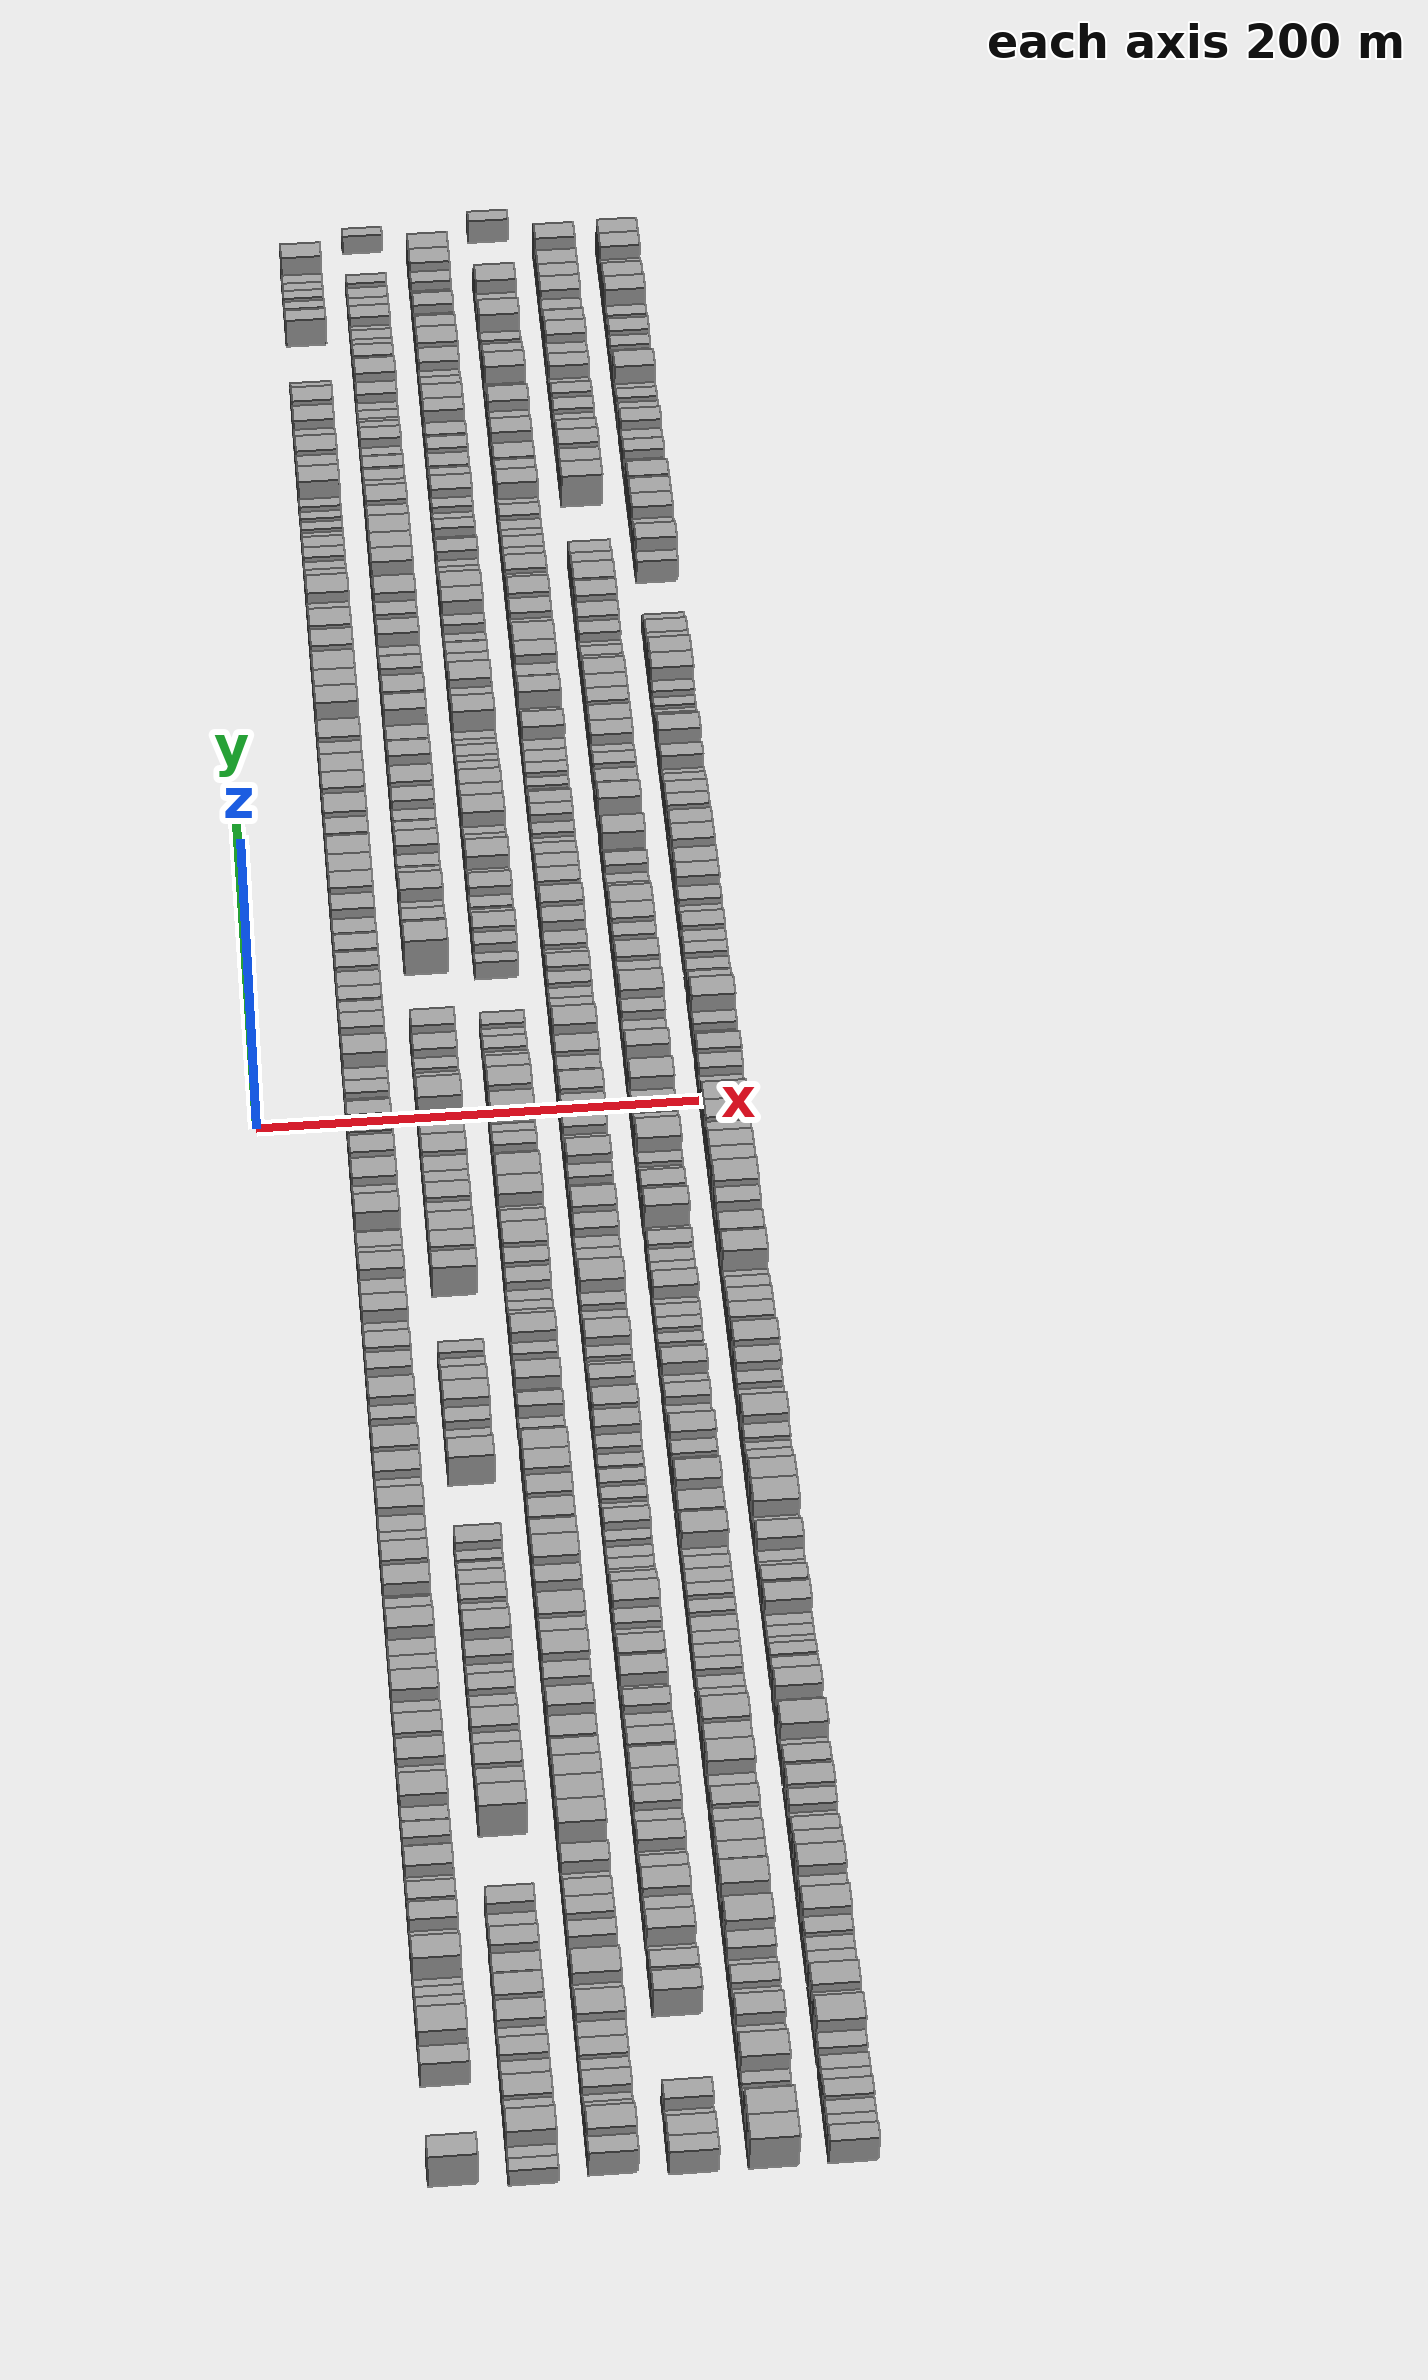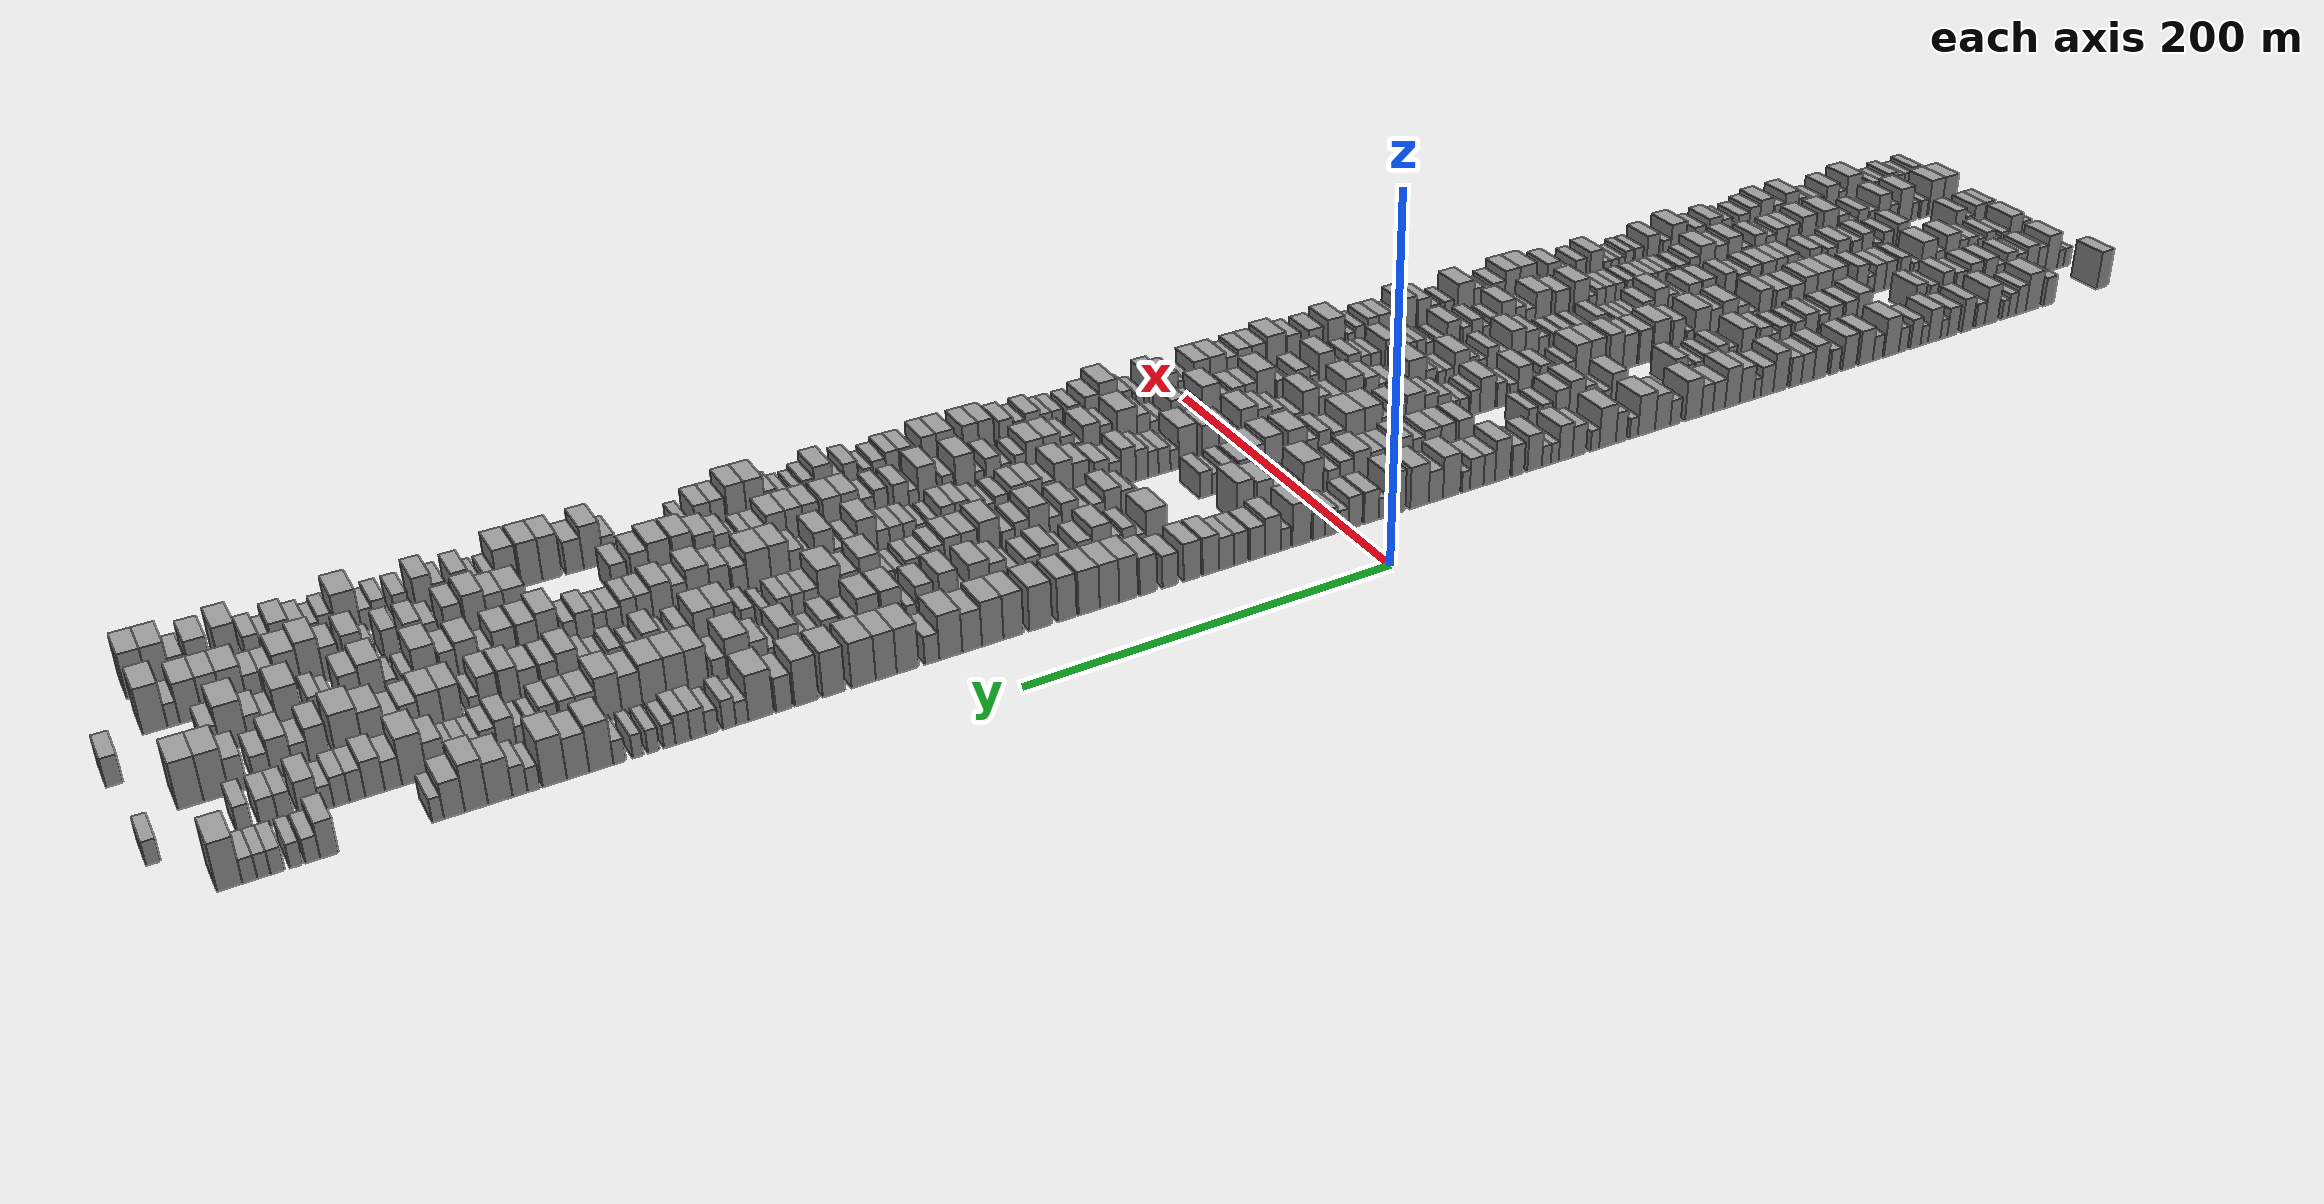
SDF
<sdf version="1.6">
 <world name="default">
  <scene>
   <sky><clouds><speed>12</speed></clouds></sky>
   <ambient>0.4 0.4 0.4 1</ambient>
   <background>0.7 0.7 0.7 1</background>
   <shadows>1</shadows>
  </scene>
  <gravity>0 0 -9.8066</gravity>
  <magnetic_field>6e-06 2.3e-05 -4.2e-05</magnetic_field>
  <physics default="0" name="default_physics" type="ode">
   <ode>
    <solver>
     <type>quick</type>
     <iters>10</iters>
     <sor>1.0</sor>
     <use_dynamic_moi_rescaling>0</use_dynamic_moi_rescaling>
    </solver>
    <constraints>
     <cfm>0</cfm>
     <erp>0.2</erp>
     <contact_max_correcting_vel>100</contact_max_correcting_vel>
     <contact_surface_layer>0.001</contact_surface_layer>
    </constraints>
   </ode>
   <max_step_size>0.004</max_step_size>
   <real_time_factor>1</real_time_factor>
   <real_time_update_rate>250</real_time_update_rate>
  </physics>
  <light name="sun" type="directional">
   <pose>0 0 10 0 0 0</pose>
   <diffuse>0.8 0.8 0.8 1</diffuse>
   <specular>0.2 0.2 0.2 1</specular>
   <attenuation>
    <range>1000</range>
    <constant>0.9</constant>
    <linear>0.01</linear>
    <quadratic>0.001</quadratic>
   </attenuation>
   <direction>-0.5 0.1 -0.9</direction>
  </light>
  <model name="building_1">
   <static>1</static>
   <pose>50.0000 -533.1544 0 0.000000 0.000000 0.000000</pose>
   <link name="link">
    <pose>0 0 12.00 0 0 0</pose>
    <collision name="collision"><geometry><box><size>20.0000 9.6913 24.0000</size></box></geometry></collision>
    <visual name="visual">
     <cast_shadows>0</cast_shadows>
     <geometry><box><size>20.0000 9.6913 24.0000</size></box></geometry>
     <material>
      <script>
       <uri>model://grey_wall/materials/scripts</uri>
       <uri>model://grey_wall/materials/textures</uri>
       <name>vrc/grey_wall</name>
      </script>
     </material>
    </visual>
   </link>
  </model>
  <model name="building_2">
   <static>1</static>
   <pose>50.0000 -488.7023 0 0.000000 0.000000 0.000000</pose>
   <link name="link">
    <pose>0 0 9.00 0 0 0</pose>
    <collision name="collision"><geometry><box><size>20.0000 8.4043 18.0000</size></box></geometry></collision>
    <visual name="visual">
     <cast_shadows>0</cast_shadows>
     <geometry><box><size>20.0000 8.4043 18.0000</size></box></geometry>
     <material>
      <script>
       <uri>model://grey_wall/materials/scripts</uri>
       <uri>model://grey_wall/materials/textures</uri>
       <name>vrc/grey_wall</name>
      </script>
     </material>
    </visual>
   </link>
  </model>
  <model name="building_3">
   <static>1</static>
   <pose>50.0000 -475.6321 0 0.000000 0.000000 0.000000</pose>
   <link name="link">
    <pose>0 0 12.00 0 0 0</pose>
    <collision name="collision"><geometry><box><size>20.0000 11.7363 24.0000</size></box></geometry></collision>
    <visual name="visual">
     <cast_shadows>0</cast_shadows>
     <geometry><box><size>20.0000 11.7363 24.0000</size></box></geometry>
     <material>
      <script>
       <uri>model://grey_wall/materials/scripts</uri>
       <uri>model://grey_wall/materials/textures</uri>
       <name>vrc/grey_wall</name>
      </script>
     </material>
    </visual>
   </link>
  </model>
  <model name="building_4">
   <static>1</static>
   <pose>50.0000 -465.8471 0 0.000000 0.000000 0.000000</pose>
   <link name="link">
    <pose>0 0 9.00 0 0 0</pose>
    <collision name="collision"><geometry><box><size>20.0000 7.8336 18.0000</size></box></geometry></collision>
    <visual name="visual">
     <cast_shadows>0</cast_shadows>
     <geometry><box><size>20.0000 7.8336 18.0000</size></box></geometry>
     <material>
      <script>
       <uri>model://grey_wall/materials/scripts</uri>
       <uri>model://grey_wall/materials/textures</uri>
       <name>vrc/grey_wall</name>
      </script>
     </material>
    </visual>
   </link>
  </model>
  <model name="building_5">
   <static>1</static>
   <pose>50.0000 -458.7653 0 0.000000 0.000000 0.000000</pose>
   <link name="link">
    <pose>0 0 7.50 0 0 0</pose>
    <collision name="collision"><geometry><box><size>20.0000 6.3301 15.0000</size></box></geometry></collision>
    <visual name="visual">
     <cast_shadows>0</cast_shadows>
     <geometry><box><size>20.0000 6.3301 15.0000</size></box></geometry>
     <material>
      <script>
       <uri>model://grey_wall/materials/scripts</uri>
       <uri>model://grey_wall/materials/textures</uri>
       <name>vrc/grey_wall</name>
      </script>
     </material>
    </visual>
   </link>
  </model>
  <model name="building_6">
   <static>1</static>
   <pose>50.0000 -453.1004 0 0.000000 0.000000 0.000000</pose>
   <link name="link">
    <pose>0 0 6.00 0 0 0</pose>
    <collision name="collision"><geometry><box><size>20.0000 4.9997 12.0000</size></box></geometry></collision>
    <visual name="visual">
     <cast_shadows>0</cast_shadows>
     <geometry><box><size>20.0000 4.9997 12.0000</size></box></geometry>
     <material>
      <script>
       <uri>model://grey_wall/materials/scripts</uri>
       <uri>model://grey_wall/materials/textures</uri>
       <name>vrc/grey_wall</name>
      </script>
     </material>
    </visual>
   </link>
  </model>
  <model name="building_7">
   <static>1</static>
   <pose>50.0000 -442.2729 0 0.000000 0.000000 0.000000</pose>
   <link name="link">
    <pose>0 0 12.00 0 0 0</pose>
    <collision name="collision"><geometry><box><size>20.0000 10.6552 24.0000</size></box></geometry></collision>
    <visual name="visual">
     <cast_shadows>0</cast_shadows>
     <geometry><box><size>20.0000 10.6552 24.0000</size></box></geometry>
     <material>
      <script>
       <uri>model://grey_wall/materials/scripts</uri>
       <uri>model://grey_wall/materials/textures</uri>
       <name>vrc/grey_wall</name>
      </script>
     </material>
    </visual>
   </link>
  </model>
  <model name="building_8">
   <static>1</static>
   <pose>50.0000 -433.3605 0 0.000000 0.000000 0.000000</pose>
   <link name="link">
    <pose>0 0 7.50 0 0 0</pose>
    <collision name="collision"><geometry><box><size>20.0000 7.1696 15.0000</size></box></geometry></collision>
    <visual name="visual">
     <cast_shadows>0</cast_shadows>
     <geometry><box><size>20.0000 7.1696 15.0000</size></box></geometry>
     <material>
      <script>
       <uri>model://grey_wall/materials/scripts</uri>
       <uri>model://grey_wall/materials/textures</uri>
       <name>vrc/grey_wall</name>
      </script>
     </material>
    </visual>
   </link>
  </model>
  <model name="building_9">
   <static>1</static>
   <pose>50.0000 -423.4777 0 0.000000 0.000000 0.000000</pose>
   <link name="link">
    <pose>0 0 10.50 0 0 0</pose>
    <collision name="collision"><geometry><box><size>20.0000 8.5960 21.0000</size></box></geometry></collision>
    <visual name="visual">
     <cast_shadows>0</cast_shadows>
     <geometry><box><size>20.0000 8.5960 21.0000</size></box></geometry>
     <material>
      <script>
       <uri>model://grey_wall/materials/scripts</uri>
       <uri>model://grey_wall/materials/textures</uri>
       <name>vrc/grey_wall</name>
      </script>
     </material>
    </visual>
   </link>
  </model>
  <model name="building_10">
   <static>1</static>
   <pose>50.0000 -412.0099 0 0.000000 0.000000 0.000000</pose>
   <link name="link">
    <pose>0 0 9.00 0 0 0</pose>
    <collision name="collision"><geometry><box><size>20.0000 8.3396 18.0000</size></box></geometry></collision>
    <visual name="visual">
     <cast_shadows>0</cast_shadows>
     <geometry><box><size>20.0000 8.3396 18.0000</size></box></geometry>
     <material>
      <script>
       <uri>model://grey_wall/materials/scripts</uri>
       <uri>model://grey_wall/materials/textures</uri>
       <name>vrc/grey_wall</name>
      </script>
     </material>
    </visual>
   </link>
  </model>
  <model name="building_11">
   <static>1</static>
   <pose>50.0000 -405.1322 0 0.000000 0.000000 0.000000</pose>
   <link name="link">
    <pose>0 0 6.00 0 0 0</pose>
    <collision name="collision"><geometry><box><size>20.0000 5.4160 12.0000</size></box></geometry></collision>
    <visual name="visual">
     <cast_shadows>0</cast_shadows>
     <geometry><box><size>20.0000 5.4160 12.0000</size></box></geometry>
     <material>
      <script>
       <uri>model://grey_wall/materials/scripts</uri>
       <uri>model://grey_wall/materials/textures</uri>
       <name>vrc/grey_wall</name>
      </script>
     </material>
    </visual>
   </link>
  </model>
  <model name="building_12">
   <static>1</static>
   <pose>50.0000 -397.6413 0 0.000000 0.000000 0.000000</pose>
   <link name="link">
    <pose>0 0 10.50 0 0 0</pose>
    <collision name="collision"><geometry><box><size>20.0000 9.5656 21.0000</size></box></geometry></collision>
    <visual name="visual">
     <cast_shadows>0</cast_shadows>
     <geometry><box><size>20.0000 9.5656 21.0000</size></box></geometry>
     <material>
      <script>
       <uri>model://grey_wall/materials/scripts</uri>
       <uri>model://grey_wall/materials/textures</uri>
       <name>vrc/grey_wall</name>
      </script>
     </material>
    </visual>
   </link>
  </model>
  <model name="building_13">
   <static>1</static>
   <pose>50.0000 -390.0340 0 0.000000 0.000000 0.000000</pose>
   <link name="link">
    <pose>0 0 6.00 0 0 0</pose>
    <collision name="collision"><geometry><box><size>20.0000 5.6491 12.0000</size></box></geometry></collision>
    <visual name="visual">
     <cast_shadows>0</cast_shadows>
     <geometry><box><size>20.0000 5.6491 12.0000</size></box></geometry>
     <material>
      <script>
       <uri>model://grey_wall/materials/scripts</uri>
       <uri>model://grey_wall/materials/textures</uri>
       <name>vrc/grey_wall</name>
      </script>
     </material>
    </visual>
   </link>
  </model>
  <model name="building_14">
   <static>1</static>
   <pose>50.0000 -383.2667 0 0.000000 0.000000 0.000000</pose>
   <link name="link">
    <pose>0 0 9.00 0 0 0</pose>
    <collision name="collision"><geometry><box><size>20.0000 7.8855 18.0000</size></box></geometry></collision>
    <visual name="visual">
     <cast_shadows>0</cast_shadows>
     <geometry><box><size>20.0000 7.8855 18.0000</size></box></geometry>
     <material>
      <script>
       <uri>model://grey_wall/materials/scripts</uri>
       <uri>model://grey_wall/materials/textures</uri>
       <name>vrc/grey_wall</name>
      </script>
     </material>
    </visual>
   </link>
  </model>
  <model name="building_15">
   <static>1</static>
   <pose>50.0000 -373.9476 0 0.000000 0.000000 0.000000</pose>
   <link name="link">
    <pose>0 0 7.50 0 0 0</pose>
    <collision name="collision"><geometry><box><size>20.0000 6.7527 15.0000</size></box></geometry></collision>
    <visual name="visual">
     <cast_shadows>0</cast_shadows>
     <geometry><box><size>20.0000 6.7527 15.0000</size></box></geometry>
     <material>
      <script>
       <uri>model://grey_wall/materials/scripts</uri>
       <uri>model://grey_wall/materials/textures</uri>
       <name>vrc/grey_wall</name>
      </script>
     </material>
    </visual>
   </link>
  </model>
  <model name="building_16">
   <static>1</static>
   <pose>50.0000 -364.9535 0 0.000000 0.000000 0.000000</pose>
   <link name="link">
    <pose>0 0 12.00 0 0 0</pose>
    <collision name="collision"><geometry><box><size>20.0000 11.2354 24.0000</size></box></geometry></collision>
    <visual name="visual">
     <cast_shadows>0</cast_shadows>
     <geometry><box><size>20.0000 11.2354 24.0000</size></box></geometry>
     <material>
      <script>
       <uri>model://grey_wall/materials/scripts</uri>
       <uri>model://grey_wall/materials/textures</uri>
       <name>vrc/grey_wall</name>
      </script>
     </material>
    </visual>
   </link>
  </model>
  <model name="building_17">
   <static>1</static>
   <pose>50.0000 -354.6423 0 0.000000 0.000000 0.000000</pose>
   <link name="link">
    <pose>0 0 7.50 0 0 0</pose>
    <collision name="collision"><geometry><box><size>20.0000 7.3870 15.0000</size></box></geometry></collision>
    <visual name="visual">
     <cast_shadows>0</cast_shadows>
     <geometry><box><size>20.0000 7.3870 15.0000</size></box></geometry>
     <material>
      <script>
       <uri>model://grey_wall/materials/scripts</uri>
       <uri>model://grey_wall/materials/textures</uri>
       <name>vrc/grey_wall</name>
      </script>
     </material>
    </visual>
   </link>
  </model>
  <model name="building_18">
   <static>1</static>
   <pose>50.0000 -345.7513 0 0.000000 0.000000 0.000000</pose>
   <link name="link">
    <pose>0 0 10.50 0 0 0</pose>
    <collision name="collision"><geometry><box><size>20.0000 10.3950 21.0000</size></box></geometry></collision>
    <visual name="visual">
     <cast_shadows>0</cast_shadows>
     <geometry><box><size>20.0000 10.3950 21.0000</size></box></geometry>
     <material>
      <script>
       <uri>model://grey_wall/materials/scripts</uri>
       <uri>model://grey_wall/materials/textures</uri>
       <name>vrc/grey_wall</name>
      </script>
     </material>
    </visual>
   </link>
  </model>
  <model name="building_19">
   <static>1</static>
   <pose>50.0000 -333.4408 0 0.000000 0.000000 0.000000</pose>
   <link name="link">
    <pose>0 0 10.50 0 0 0</pose>
    <collision name="collision"><geometry><box><size>20.0000 10.2261 21.0000</size></box></geometry></collision>
    <visual name="visual">
     <cast_shadows>0</cast_shadows>
     <geometry><box><size>20.0000 10.2261 21.0000</size></box></geometry>
     <material>
      <script>
       <uri>model://grey_wall/materials/scripts</uri>
       <uri>model://grey_wall/materials/textures</uri>
       <name>vrc/grey_wall</name>
      </script>
     </material>
    </visual>
   </link>
  </model>
  <model name="building_20">
   <static>1</static>
   <pose>50.0000 -322.7514 0 0.000000 0.000000 0.000000</pose>
   <link name="link">
    <pose>0 0 7.50 0 0 0</pose>
    <collision name="collision"><geometry><box><size>20.0000 7.1527 15.0000</size></box></geometry></collision>
    <visual name="visual">
     <cast_shadows>0</cast_shadows>
     <geometry><box><size>20.0000 7.1527 15.0000</size></box></geometry>
     <material>
      <script>
       <uri>model://grey_wall/materials/scripts</uri>
       <uri>model://grey_wall/materials/textures</uri>
       <name>vrc/grey_wall</name>
      </script>
     </material>
    </visual>
   </link>
  </model>
  <model name="building_21">
   <static>1</static>
   <pose>50.0000 -312.0736 0 0.000000 0.000000 0.000000</pose>
   <link name="link">
    <pose>0 0 10.50 0 0 0</pose>
    <collision name="collision"><geometry><box><size>20.0000 10.2030 21.0000</size></box></geometry></collision>
    <visual name="visual">
     <cast_shadows>0</cast_shadows>
     <geometry><box><size>20.0000 10.2030 21.0000</size></box></geometry>
     <material>
      <script>
       <uri>model://grey_wall/materials/scripts</uri>
       <uri>model://grey_wall/materials/textures</uri>
       <name>vrc/grey_wall</name>
      </script>
     </material>
    </visual>
   </link>
  </model>
  <model name="building_22">
   <static>1</static>
   <pose>50.0000 -302.5627 0 0.000000 0.000000 0.000000</pose>
   <link name="link">
    <pose>0 0 9.00 0 0 0</pose>
    <collision name="collision"><geometry><box><size>20.0000 8.8188 18.0000</size></box></geometry></collision>
    <visual name="visual">
     <cast_shadows>0</cast_shadows>
     <geometry><box><size>20.0000 8.8188 18.0000</size></box></geometry>
     <material>
      <script>
       <uri>model://grey_wall/materials/scripts</uri>
       <uri>model://grey_wall/materials/textures</uri>
       <name>vrc/grey_wall</name>
      </script>
     </material>
    </visual>
   </link>
  </model>
  <model name="building_23">
   <static>1</static>
   <pose>50.0000 -294.1191 0 0.000000 0.000000 0.000000</pose>
   <link name="link">
    <pose>0 0 9.00 0 0 0</pose>
    <collision name="collision"><geometry><box><size>20.0000 8.0684 18.0000</size></box></geometry></collision>
    <visual name="visual">
     <cast_shadows>0</cast_shadows>
     <geometry><box><size>20.0000 8.0684 18.0000</size></box></geometry>
     <material>
      <script>
       <uri>model://grey_wall/materials/scripts</uri>
       <uri>model://grey_wall/materials/textures</uri>
       <name>vrc/grey_wall</name>
      </script>
     </material>
    </visual>
   </link>
  </model>
  <model name="building_24">
   <static>1</static>
   <pose>50.0000 -283.0544 0 0.000000 0.000000 0.000000</pose>
   <link name="link">
    <pose>0 0 12.00 0 0 0</pose>
    <collision name="collision"><geometry><box><size>20.0000 10.0608 24.0000</size></box></geometry></collision>
    <visual name="visual">
     <cast_shadows>0</cast_shadows>
     <geometry><box><size>20.0000 10.0608 24.0000</size></box></geometry>
     <material>
      <script>
       <uri>model://grey_wall/materials/scripts</uri>
       <uri>model://grey_wall/materials/textures</uri>
       <name>vrc/grey_wall</name>
      </script>
     </material>
    </visual>
   </link>
  </model>
  <model name="building_25">
   <static>1</static>
   <pose>50.0000 -273.5514 0 0.000000 0.000000 0.000000</pose>
   <link name="link">
    <pose>0 0 9.00 0 0 0</pose>
    <collision name="collision"><geometry><box><size>20.0000 8.9453 18.0000</size></box></geometry></collision>
    <visual name="visual">
     <cast_shadows>0</cast_shadows>
     <geometry><box><size>20.0000 8.9453 18.0000</size></box></geometry>
     <material>
      <script>
       <uri>model://grey_wall/materials/scripts</uri>
       <uri>model://grey_wall/materials/textures</uri>
       <name>vrc/grey_wall</name>
      </script>
     </material>
    </visual>
   </link>
  </model>
  <model name="building_26">
   <static>1</static>
   <pose>50.0000 -266.6149 0 0.000000 0.000000 0.000000</pose>
   <link name="link">
    <pose>0 0 6.00 0 0 0</pose>
    <collision name="collision"><geometry><box><size>20.0000 4.9277 12.0000</size></box></geometry></collision>
    <visual name="visual">
     <cast_shadows>0</cast_shadows>
     <geometry><box><size>20.0000 4.9277 12.0000</size></box></geometry>
     <material>
      <script>
       <uri>model://grey_wall/materials/scripts</uri>
       <uri>model://grey_wall/materials/textures</uri>
       <name>vrc/grey_wall</name>
      </script>
     </material>
    </visual>
   </link>
  </model>
  <model name="building_27">
   <static>1</static>
   <pose>50.0000 -259.1388 0 0.000000 0.000000 0.000000</pose>
   <link name="link">
    <pose>0 0 10.50 0 0 0</pose>
    <collision name="collision"><geometry><box><size>20.0000 10.0245 21.0000</size></box></geometry></collision>
    <visual name="visual">
     <cast_shadows>0</cast_shadows>
     <geometry><box><size>20.0000 10.0245 21.0000</size></box></geometry>
     <material>
      <script>
       <uri>model://grey_wall/materials/scripts</uri>
       <uri>model://grey_wall/materials/textures</uri>
       <name>vrc/grey_wall</name>
      </script>
     </material>
    </visual>
   </link>
  </model>
  <model name="building_28">
   <static>1</static>
   <pose>50.0000 -249.0320 0 0.000000 0.000000 0.000000</pose>
   <link name="link">
    <pose>0 0 12.00 0 0 0</pose>
    <collision name="collision"><geometry><box><size>20.0000 10.1892 24.0000</size></box></geometry></collision>
    <visual name="visual">
     <cast_shadows>0</cast_shadows>
     <geometry><box><size>20.0000 10.1892 24.0000</size></box></geometry>
     <material>
      <script>
       <uri>model://grey_wall/materials/scripts</uri>
       <uri>model://grey_wall/materials/textures</uri>
       <name>vrc/grey_wall</name>
      </script>
     </material>
    </visual>
   </link>
  </model>
  <model name="building_29">
   <static>1</static>
   <pose>50.0000 -239.6317 0 0.000000 0.000000 0.000000</pose>
   <link name="link">
    <pose>0 0 9.00 0 0 0</pose>
    <collision name="collision"><geometry><box><size>20.0000 8.6114 18.0000</size></box></geometry></collision>
    <visual name="visual">
     <cast_shadows>0</cast_shadows>
     <geometry><box><size>20.0000 8.6114 18.0000</size></box></geometry>
     <material>
      <script>
       <uri>model://grey_wall/materials/scripts</uri>
       <uri>model://grey_wall/materials/textures</uri>
       <name>vrc/grey_wall</name>
      </script>
     </material>
    </visual>
   </link>
  </model>
  <model name="building_30">
   <static>1</static>
   <pose>50.0000 -231.2340 0 0.000000 0.000000 0.000000</pose>
   <link name="link">
    <pose>0 0 9.00 0 0 0</pose>
    <collision name="collision"><geometry><box><size>20.0000 8.1840 18.0000</size></box></geometry></collision>
    <visual name="visual">
     <cast_shadows>0</cast_shadows>
     <geometry><box><size>20.0000 8.1840 18.0000</size></box></geometry>
     <material>
      <script>
       <uri>model://grey_wall/materials/scripts</uri>
       <uri>model://grey_wall/materials/textures</uri>
       <name>vrc/grey_wall</name>
      </script>
     </material>
    </visual>
   </link>
  </model>
  <model name="building_31">
   <static>1</static>
   <pose>50.0000 -221.6913 0 0.000000 0.000000 0.000000</pose>
   <link name="link">
    <pose>0 0 12.00 0 0 0</pose>
    <collision name="collision"><geometry><box><size>20.0000 10.9014 24.0000</size></box></geometry></collision>
    <visual name="visual">
     <cast_shadows>0</cast_shadows>
     <geometry><box><size>20.0000 10.9014 24.0000</size></box></geometry>
     <material>
      <script>
       <uri>model://grey_wall/materials/scripts</uri>
       <uri>model://grey_wall/materials/textures</uri>
       <name>vrc/grey_wall</name>
      </script>
     </material>
    </visual>
   </link>
  </model>
  <model name="building_32">
   <static>1</static>
   <pose>50.0000 -209.6548 0 0.000000 0.000000 0.000000</pose>
   <link name="link">
    <pose>0 0 7.50 0 0 0</pose>
    <collision name="collision"><geometry><box><size>20.0000 7.1716 15.0000</size></box></geometry></collision>
    <visual name="visual">
     <cast_shadows>0</cast_shadows>
     <geometry><box><size>20.0000 7.1716 15.0000</size></box></geometry>
     <material>
      <script>
       <uri>model://grey_wall/materials/scripts</uri>
       <uri>model://grey_wall/materials/textures</uri>
       <name>vrc/grey_wall</name>
      </script>
     </material>
    </visual>
   </link>
  </model>
  <model name="building_33">
   <static>1</static>
   <pose>50.0000 -200.8544 0 0.000000 0.000000 0.000000</pose>
   <link name="link">
    <pose>0 0 10.50 0 0 0</pose>
    <collision name="collision"><geometry><box><size>20.0000 10.4291 21.0000</size></box></geometry></collision>
    <visual name="visual">
     <cast_shadows>0</cast_shadows>
     <geometry><box><size>20.0000 10.4291 21.0000</size></box></geometry>
     <material>
      <script>
       <uri>model://grey_wall/materials/scripts</uri>
       <uri>model://grey_wall/materials/textures</uri>
       <name>vrc/grey_wall</name>
      </script>
     </material>
    </visual>
   </link>
  </model>
  <model name="building_34">
   <static>1</static>
   <pose>50.0000 -189.8872 0 0.000000 0.000000 0.000000</pose>
   <link name="link">
    <pose>0 0 12.00 0 0 0</pose>
    <collision name="collision"><geometry><box><size>20.0000 11.5054 24.0000</size></box></geometry></collision>
    <visual name="visual">
     <cast_shadows>0</cast_shadows>
     <geometry><box><size>20.0000 11.5054 24.0000</size></box></geometry>
     <material>
      <script>
       <uri>model://grey_wall/materials/scripts</uri>
       <uri>model://grey_wall/materials/textures</uri>
       <name>vrc/grey_wall</name>
      </script>
     </material>
    </visual>
   </link>
  </model>
  <model name="building_35">
   <static>1</static>
   <pose>50.0000 -181.3341 0 0.000000 0.000000 0.000000</pose>
   <link name="link">
    <pose>0 0 6.00 0 0 0</pose>
    <collision name="collision"><geometry><box><size>20.0000 5.6009 12.0000</size></box></geometry></collision>
    <visual name="visual">
     <cast_shadows>0</cast_shadows>
     <geometry><box><size>20.0000 5.6009 12.0000</size></box></geometry>
     <material>
      <script>
       <uri>model://grey_wall/materials/scripts</uri>
       <uri>model://grey_wall/materials/textures</uri>
       <name>vrc/grey_wall</name>
      </script>
     </material>
    </visual>
   </link>
  </model>
  <model name="building_36">
   <static>1</static>
   <pose>50.0000 -172.9242 0 0.000000 0.000000 0.000000</pose>
   <link name="link">
    <pose>0 0 9.00 0 0 0</pose>
    <collision name="collision"><geometry><box><size>20.0000 7.2188 18.0000</size></box></geometry></collision>
    <visual name="visual">
     <cast_shadows>0</cast_shadows>
     <geometry><box><size>20.0000 7.2188 18.0000</size></box></geometry>
     <material>
      <script>
       <uri>model://grey_wall/materials/scripts</uri>
       <uri>model://grey_wall/materials/textures</uri>
       <name>vrc/grey_wall</name>
      </script>
     </material>
    </visual>
   </link>
  </model>
  <model name="building_37">
   <static>1</static>
   <pose>50.0000 -163.7981 0 0.000000 0.000000 0.000000</pose>
   <link name="link">
    <pose>0 0 12.00 0 0 0</pose>
    <collision name="collision"><geometry><box><size>20.0000 11.0333 24.0000</size></box></geometry></collision>
    <visual name="visual">
     <cast_shadows>0</cast_shadows>
     <geometry><box><size>20.0000 11.0333 24.0000</size></box></geometry>
     <material>
      <script>
       <uri>model://grey_wall/materials/scripts</uri>
       <uri>model://grey_wall/materials/textures</uri>
       <name>vrc/grey_wall</name>
      </script>
     </material>
    </visual>
   </link>
  </model>
  <model name="building_38">
   <static>1</static>
   <pose>50.0000 -155.4298 0 0.000000 0.000000 0.000000</pose>
   <link name="link">
    <pose>0 0 6.00 0 0 0</pose>
    <collision name="collision"><geometry><box><size>20.0000 5.7034 12.0000</size></box></geometry></collision>
    <visual name="visual">
     <cast_shadows>0</cast_shadows>
     <geometry><box><size>20.0000 5.7034 12.0000</size></box></geometry>
     <material>
      <script>
       <uri>model://grey_wall/materials/scripts</uri>
       <uri>model://grey_wall/materials/textures</uri>
       <name>vrc/grey_wall</name>
      </script>
     </material>
    </visual>
   </link>
  </model>
  <model name="building_39">
   <static>1</static>
   <pose>50.0000 -145.1319 0 0.000000 0.000000 0.000000</pose>
   <link name="link">
    <pose>0 0 9.00 0 0 0</pose>
    <collision name="collision"><geometry><box><size>20.0000 8.8923 18.0000</size></box></geometry></collision>
    <visual name="visual">
     <cast_shadows>0</cast_shadows>
     <geometry><box><size>20.0000 8.8923 18.0000</size></box></geometry>
     <material>
      <script>
       <uri>model://grey_wall/materials/scripts</uri>
       <uri>model://grey_wall/materials/textures</uri>
       <name>vrc/grey_wall</name>
      </script>
     </material>
    </visual>
   </link>
  </model>
  <model name="building_40">
   <static>1</static>
   <pose>50.0000 -136.2018 0 0.000000 0.000000 0.000000</pose>
   <link name="link">
    <pose>0 0 10.50 0 0 0</pose>
    <collision name="collision"><geometry><box><size>20.0000 8.9679 21.0000</size></box></geometry></collision>
    <visual name="visual">
     <cast_shadows>0</cast_shadows>
     <geometry><box><size>20.0000 8.9679 21.0000</size></box></geometry>
     <material>
      <script>
       <uri>model://grey_wall/materials/scripts</uri>
       <uri>model://grey_wall/materials/textures</uri>
       <name>vrc/grey_wall</name>
      </script>
     </material>
    </visual>
   </link>
  </model>
  <model name="building_41">
   <static>1</static>
   <pose>50.0000 -129.1809 0 0.000000 0.000000 0.000000</pose>
   <link name="link">
    <pose>0 0 6.00 0 0 0</pose>
    <collision name="collision"><geometry><box><size>20.0000 5.0738 12.0000</size></box></geometry></collision>
    <visual name="visual">
     <cast_shadows>0</cast_shadows>
     <geometry><box><size>20.0000 5.0738 12.0000</size></box></geometry>
     <material>
      <script>
       <uri>model://grey_wall/materials/scripts</uri>
       <uri>model://grey_wall/materials/textures</uri>
       <name>vrc/grey_wall</name>
      </script>
     </material>
    </visual>
   </link>
  </model>
  <model name="building_42">
   <static>1</static>
   <pose>50.0000 -123.7242 0 0.000000 0.000000 0.000000</pose>
   <link name="link">
    <pose>0 0 6.00 0 0 0</pose>
    <collision name="collision"><geometry><box><size>20.0000 5.8395 12.0000</size></box></geometry></collision>
    <visual name="visual">
     <cast_shadows>0</cast_shadows>
     <geometry><box><size>20.0000 5.8395 12.0000</size></box></geometry>
     <material>
      <script>
       <uri>model://grey_wall/materials/scripts</uri>
       <uri>model://grey_wall/materials/textures</uri>
       <name>vrc/grey_wall</name>
      </script>
     </material>
    </visual>
   </link>
  </model>
  <model name="building_43">
   <static>1</static>
   <pose>50.0000 -116.1181 0 0.000000 0.000000 0.000000</pose>
   <link name="link">
    <pose>0 0 10.50 0 0 0</pose>
    <collision name="collision"><geometry><box><size>20.0000 9.3727 21.0000</size></box></geometry></collision>
    <visual name="visual">
     <cast_shadows>0</cast_shadows>
     <geometry><box><size>20.0000 9.3727 21.0000</size></box></geometry>
     <material>
      <script>
       <uri>model://grey_wall/materials/scripts</uri>
       <uri>model://grey_wall/materials/textures</uri>
       <name>vrc/grey_wall</name>
      </script>
     </material>
    </visual>
   </link>
  </model>
  <model name="building_44">
   <static>1</static>
   <pose>50.0000 -105.4651 0 0.000000 0.000000 0.000000</pose>
   <link name="link">
    <pose>0 0 9.00 0 0 0</pose>
    <collision name="collision"><geometry><box><size>20.0000 7.9334 18.0000</size></box></geometry></collision>
    <visual name="visual">
     <cast_shadows>0</cast_shadows>
     <geometry><box><size>20.0000 7.9334 18.0000</size></box></geometry>
     <material>
      <script>
       <uri>model://grey_wall/materials/scripts</uri>
       <uri>model://grey_wall/materials/textures</uri>
       <name>vrc/grey_wall</name>
      </script>
     </material>
    </visual>
   </link>
  </model>
  <model name="building_45">
   <static>1</static>
   <pose>50.0000 -95.6676 0 0.000000 0.000000 0.000000</pose>
   <link name="link">
    <pose>0 0 12.00 0 0 0</pose>
    <collision name="collision"><geometry><box><size>20.0000 9.6616 24.0000</size></box></geometry></collision>
    <visual name="visual">
     <cast_shadows>0</cast_shadows>
     <geometry><box><size>20.0000 9.6616 24.0000</size></box></geometry>
     <material>
      <script>
       <uri>model://grey_wall/materials/scripts</uri>
       <uri>model://grey_wall/materials/textures</uri>
       <name>vrc/grey_wall</name>
      </script>
     </material>
    </visual>
   </link>
  </model>
  <model name="building_46">
   <static>1</static>
   <pose>50.0000 -87.2326 0 0.000000 0.000000 0.000000</pose>
   <link name="link">
    <pose>0 0 9.00 0 0 0</pose>
    <collision name="collision"><geometry><box><size>20.0000 7.2084 18.0000</size></box></geometry></collision>
    <visual name="visual">
     <cast_shadows>0</cast_shadows>
     <geometry><box><size>20.0000 7.2084 18.0000</size></box></geometry>
     <material>
      <script>
       <uri>model://grey_wall/materials/scripts</uri>
       <uri>model://grey_wall/materials/textures</uri>
       <name>vrc/grey_wall</name>
      </script>
     </material>
    </visual>
   </link>
  </model>
  <model name="building_47">
   <static>1</static>
   <pose>50.0000 -79.3638 0 0.000000 0.000000 0.000000</pose>
   <link name="link">
    <pose>0 0 9.00 0 0 0</pose>
    <collision name="collision"><geometry><box><size>20.0000 8.5292 18.0000</size></box></geometry></collision>
    <visual name="visual">
     <cast_shadows>0</cast_shadows>
     <geometry><box><size>20.0000 8.5292 18.0000</size></box></geometry>
     <material>
      <script>
       <uri>model://grey_wall/materials/scripts</uri>
       <uri>model://grey_wall/materials/textures</uri>
       <name>vrc/grey_wall</name>
      </script>
     </material>
    </visual>
   </link>
  </model>
  <model name="building_48">
   <static>1</static>
   <pose>50.0000 -72.6055 0 0.000000 0.000000 0.000000</pose>
   <link name="link">
    <pose>0 0 6.00 0 0 0</pose>
    <collision name="collision"><geometry><box><size>20.0000 4.9873 12.0000</size></box></geometry></collision>
    <visual name="visual">
     <cast_shadows>0</cast_shadows>
     <geometry><box><size>20.0000 4.9873 12.0000</size></box></geometry>
     <material>
      <script>
       <uri>model://grey_wall/materials/scripts</uri>
       <uri>model://grey_wall/materials/textures</uri>
       <name>vrc/grey_wall</name>
      </script>
     </material>
    </visual>
   </link>
  </model>
  <model name="building_49">
   <static>1</static>
   <pose>50.0000 -63.7204 0 0.000000 0.000000 0.000000</pose>
   <link name="link">
    <pose>0 0 12.00 0 0 0</pose>
    <collision name="collision"><geometry><box><size>20.0000 10.7830 24.0000</size></box></geometry></collision>
    <visual name="visual">
     <cast_shadows>0</cast_shadows>
     <geometry><box><size>20.0000 10.7830 24.0000</size></box></geometry>
     <material>
      <script>
       <uri>model://grey_wall/materials/scripts</uri>
       <uri>model://grey_wall/materials/textures</uri>
       <name>vrc/grey_wall</name>
      </script>
     </material>
    </visual>
   </link>
  </model>
  <model name="building_50">
   <static>1</static>
   <pose>50.0000 -53.9373 0 0.000000 0.000000 0.000000</pose>
   <link name="link">
    <pose>0 0 9.00 0 0 0</pose>
    <collision name="collision"><geometry><box><size>20.0000 8.7832 18.0000</size></box></geometry></collision>
    <visual name="visual">
     <cast_shadows>0</cast_shadows>
     <geometry><box><size>20.0000 8.7832 18.0000</size></box></geometry>
     <material>
      <script>
       <uri>model://grey_wall/materials/scripts</uri>
       <uri>model://grey_wall/materials/textures</uri>
       <name>vrc/grey_wall</name>
      </script>
     </material>
    </visual>
   </link>
  </model>
  <model name="building_51">
   <static>1</static>
   <pose>50.0000 -43.9038 0 0.000000 0.000000 0.000000</pose>
   <link name="link">
    <pose>0 0 12.00 0 0 0</pose>
    <collision name="collision"><geometry><box><size>20.0000 11.2838 24.0000</size></box></geometry></collision>
    <visual name="visual">
     <cast_shadows>0</cast_shadows>
     <geometry><box><size>20.0000 11.2838 24.0000</size></box></geometry>
     <material>
      <script>
       <uri>model://grey_wall/materials/scripts</uri>
       <uri>model://grey_wall/materials/textures</uri>
       <name>vrc/grey_wall</name>
      </script>
     </material>
    </visual>
   </link>
  </model>
  <model name="building_52">
   <static>1</static>
   <pose>50.0000 -30.2886 0 0.000000 0.000000 0.000000</pose>
   <link name="link">
    <pose>0 0 12.00 0 0 0</pose>
    <collision name="collision"><geometry><box><size>20.0000 9.9465 24.0000</size></box></geometry></collision>
    <visual name="visual">
     <cast_shadows>0</cast_shadows>
     <geometry><box><size>20.0000 9.9465 24.0000</size></box></geometry>
     <material>
      <script>
       <uri>model://grey_wall/materials/scripts</uri>
       <uri>model://grey_wall/materials/textures</uri>
       <name>vrc/grey_wall</name>
      </script>
     </material>
    </visual>
   </link>
  </model>
  <model name="building_53">
   <static>1</static>
   <pose>50.0000 -21.7753 0 0.000000 0.000000 0.000000</pose>
   <link name="link">
    <pose>0 0 6.00 0 0 0</pose>
    <collision name="collision"><geometry><box><size>20.0000 5.0801 12.0000</size></box></geometry></collision>
    <visual name="visual">
     <cast_shadows>0</cast_shadows>
     <geometry><box><size>20.0000 5.0801 12.0000</size></box></geometry>
     <material>
      <script>
       <uri>model://grey_wall/materials/scripts</uri>
       <uri>model://grey_wall/materials/textures</uri>
       <name>vrc/grey_wall</name>
      </script>
     </material>
    </visual>
   </link>
  </model>
  <model name="building_54">
   <static>1</static>
   <pose>50.0000 -14.7899 0 0.000000 0.000000 0.000000</pose>
   <link name="link">
    <pose>0 0 9.00 0 0 0</pose>
    <collision name="collision"><geometry><box><size>20.0000 8.8905 18.0000</size></box></geometry></collision>
    <visual name="visual">
     <cast_shadows>0</cast_shadows>
     <geometry><box><size>20.0000 8.8905 18.0000</size></box></geometry>
     <material>
      <script>
       <uri>model://grey_wall/materials/scripts</uri>
       <uri>model://grey_wall/materials/textures</uri>
       <name>vrc/grey_wall</name>
      </script>
     </material>
    </visual>
   </link>
  </model>
  <model name="building_55">
   <static>1</static>
   <pose>50.0000 -5.2620 0 0.000000 0.000000 0.000000</pose>
   <link name="link">
    <pose>0 0 9.00 0 0 0</pose>
    <collision name="collision"><geometry><box><size>20.0000 8.1654 18.0000</size></box></geometry></collision>
    <visual name="visual">
     <cast_shadows>0</cast_shadows>
     <geometry><box><size>20.0000 8.1654 18.0000</size></box></geometry>
     <material>
      <script>
       <uri>model://grey_wall/materials/scripts</uri>
       <uri>model://grey_wall/materials/textures</uri>
       <name>vrc/grey_wall</name>
      </script>
     </material>
    </visual>
   </link>
  </model>
  <model name="building_56">
   <static>1</static>
   <pose>50.0000 1.6433 0 0.000000 0.000000 0.000000</pose>
   <link name="link">
    <pose>0 0 6.00 0 0 0</pose>
    <collision name="collision"><geometry><box><size>20.0000 5.6452 12.0000</size></box></geometry></collision>
    <visual name="visual">
     <cast_shadows>0</cast_shadows>
     <geometry><box><size>20.0000 5.6452 12.0000</size></box></geometry>
     <material>
      <script>
       <uri>model://grey_wall/materials/scripts</uri>
       <uri>model://grey_wall/materials/textures</uri>
       <name>vrc/grey_wall</name>
      </script>
     </material>
    </visual>
   </link>
  </model>
  <model name="building_57">
   <static>1</static>
   <pose>50.0000 9.2083 0 0.000000 0.000000 0.000000</pose>
   <link name="link">
    <pose>0 0 7.50 0 0 0</pose>
    <collision name="collision"><geometry><box><size>20.0000 7.4848 15.0000</size></box></geometry></collision>
    <visual name="visual">
     <cast_shadows>0</cast_shadows>
     <geometry><box><size>20.0000 7.4848 15.0000</size></box></geometry>
     <material>
      <script>
       <uri>model://grey_wall/materials/scripts</uri>
       <uri>model://grey_wall/materials/textures</uri>
       <name>vrc/grey_wall</name>
      </script>
     </material>
    </visual>
   </link>
  </model>
  <model name="building_58">
   <static>1</static>
   <pose>50.0000 16.4128 0 0.000000 0.000000 0.000000</pose>
   <link name="link">
    <pose>0 0 7.50 0 0 0</pose>
    <collision name="collision"><geometry><box><size>20.0000 6.9242 15.0000</size></box></geometry></collision>
    <visual name="visual">
     <cast_shadows>0</cast_shadows>
     <geometry><box><size>20.0000 6.9242 15.0000</size></box></geometry>
     <material>
      <script>
       <uri>model://grey_wall/materials/scripts</uri>
       <uri>model://grey_wall/materials/textures</uri>
       <name>vrc/grey_wall</name>
      </script>
     </material>
    </visual>
   </link>
  </model>
  <model name="building_59">
   <static>1</static>
   <pose>50.0000 26.3806 0 0.000000 0.000000 0.000000</pose>
   <link name="link">
    <pose>0 0 12.00 0 0 0</pose>
    <collision name="collision"><geometry><box><size>20.0000 11.0114 24.0000</size></box></geometry></collision>
    <visual name="visual">
     <cast_shadows>0</cast_shadows>
     <geometry><box><size>20.0000 11.0114 24.0000</size></box></geometry>
     <material>
      <script>
       <uri>model://grey_wall/materials/scripts</uri>
       <uri>model://grey_wall/materials/textures</uri>
       <name>vrc/grey_wall</name>
      </script>
     </material>
    </visual>
   </link>
  </model>
  <model name="building_60">
   <static>1</static>
   <pose>50.0000 35.6208 0 0.000000 0.000000 0.000000</pose>
   <link name="link">
    <pose>0 0 6.00 0 0 0</pose>
    <collision name="collision"><geometry><box><size>20.0000 5.4691 12.0000</size></box></geometry></collision>
    <visual name="visual">
     <cast_shadows>0</cast_shadows>
     <geometry><box><size>20.0000 5.4691 12.0000</size></box></geometry>
     <material>
      <script>
       <uri>model://grey_wall/materials/scripts</uri>
       <uri>model://grey_wall/materials/textures</uri>
       <name>vrc/grey_wall</name>
      </script>
     </material>
    </visual>
   </link>
  </model>
  <model name="building_61">
   <static>1</static>
   <pose>50.0000 42.9283 0 0.000000 0.000000 0.000000</pose>
   <link name="link">
    <pose>0 0 10.50 0 0 0</pose>
    <collision name="collision"><geometry><box><size>20.0000 9.1458 21.0000</size></box></geometry></collision>
    <visual name="visual">
     <cast_shadows>0</cast_shadows>
     <geometry><box><size>20.0000 9.1458 21.0000</size></box></geometry>
     <material>
      <script>
       <uri>model://grey_wall/materials/scripts</uri>
       <uri>model://grey_wall/materials/textures</uri>
       <name>vrc/grey_wall</name>
      </script>
     </material>
    </visual>
   </link>
  </model>
  <model name="building_62">
   <static>1</static>
   <pose>50.0000 51.9414 0 0.000000 0.000000 0.000000</pose>
   <link name="link">
    <pose>0 0 9.00 0 0 0</pose>
    <collision name="collision"><geometry><box><size>20.0000 8.8803 18.0000</size></box></geometry></collision>
    <visual name="visual">
     <cast_shadows>0</cast_shadows>
     <geometry><box><size>20.0000 8.8803 18.0000</size></box></geometry>
     <material>
      <script>
       <uri>model://grey_wall/materials/scripts</uri>
       <uri>model://grey_wall/materials/textures</uri>
       <name>vrc/grey_wall</name>
      </script>
     </material>
    </visual>
   </link>
  </model>
  <model name="building_63">
   <static>1</static>
   <pose>50.0000 61.2831 0 0.000000 0.000000 0.000000</pose>
   <link name="link">
    <pose>0 0 9.00 0 0 0</pose>
    <collision name="collision"><geometry><box><size>20.0000 7.8031 18.0000</size></box></geometry></collision>
    <visual name="visual">
     <cast_shadows>0</cast_shadows>
     <geometry><box><size>20.0000 7.8031 18.0000</size></box></geometry>
     <material>
      <script>
       <uri>model://grey_wall/materials/scripts</uri>
       <uri>model://grey_wall/materials/textures</uri>
       <name>vrc/grey_wall</name>
      </script>
     </material>
    </visual>
   </link>
  </model>
  <model name="building_64">
   <static>1</static>
   <pose>50.0000 69.5711 0 0.000000 0.000000 0.000000</pose>
   <link name="link">
    <pose>0 0 9.00 0 0 0</pose>
    <collision name="collision"><geometry><box><size>20.0000 8.7729 18.0000</size></box></geometry></collision>
    <visual name="visual">
     <cast_shadows>0</cast_shadows>
     <geometry><box><size>20.0000 8.7729 18.0000</size></box></geometry>
     <material>
      <script>
       <uri>model://grey_wall/materials/scripts</uri>
       <uri>model://grey_wall/materials/textures</uri>
       <name>vrc/grey_wall</name>
      </script>
     </material>
    </visual>
   </link>
  </model>
  <model name="building_65">
   <static>1</static>
   <pose>50.0000 78.4867 0 0.000000 0.000000 0.000000</pose>
   <link name="link">
    <pose>0 0 10.50 0 0 0</pose>
    <collision name="collision"><geometry><box><size>20.0000 9.0582 21.0000</size></box></geometry></collision>
    <visual name="visual">
     <cast_shadows>0</cast_shadows>
     <geometry><box><size>20.0000 9.0582 21.0000</size></box></geometry>
     <material>
      <script>
       <uri>model://grey_wall/materials/scripts</uri>
       <uri>model://grey_wall/materials/textures</uri>
       <name>vrc/grey_wall</name>
      </script>
     </material>
    </visual>
   </link>
  </model>
  <model name="building_66">
   <static>1</static>
   <pose>50.0000 88.7880 0 0.000000 0.000000 0.000000</pose>
   <link name="link">
    <pose>0 0 10.50 0 0 0</pose>
    <collision name="collision"><geometry><box><size>20.0000 9.5445 21.0000</size></box></geometry></collision>
    <visual name="visual">
     <cast_shadows>0</cast_shadows>
     <geometry><box><size>20.0000 9.5445 21.0000</size></box></geometry>
     <material>
      <script>
       <uri>model://grey_wall/materials/scripts</uri>
       <uri>model://grey_wall/materials/textures</uri>
       <name>vrc/grey_wall</name>
      </script>
     </material>
    </visual>
   </link>
  </model>
  <model name="building_67">
   <static>1</static>
   <pose>50.0000 100.9029 0 0.000000 0.000000 0.000000</pose>
   <link name="link">
    <pose>0 0 9.00 0 0 0</pose>
    <collision name="collision"><geometry><box><size>20.0000 8.6853 18.0000</size></box></geometry></collision>
    <visual name="visual">
     <cast_shadows>0</cast_shadows>
     <geometry><box><size>20.0000 8.6853 18.0000</size></box></geometry>
     <material>
      <script>
       <uri>model://grey_wall/materials/scripts</uri>
       <uri>model://grey_wall/materials/textures</uri>
       <name>vrc/grey_wall</name>
      </script>
     </material>
    </visual>
   </link>
  </model>
  <model name="building_68">
   <static>1</static>
   <pose>50.0000 112.9835 0 0.000000 0.000000 0.000000</pose>
   <link name="link">
    <pose>0 0 10.50 0 0 0</pose>
    <collision name="collision"><geometry><box><size>20.0000 9.4759 21.0000</size></box></geometry></collision>
    <visual name="visual">
     <cast_shadows>0</cast_shadows>
     <geometry><box><size>20.0000 9.4759 21.0000</size></box></geometry>
     <material>
      <script>
       <uri>model://grey_wall/materials/scripts</uri>
       <uri>model://grey_wall/materials/textures</uri>
       <name>vrc/grey_wall</name>
      </script>
     </material>
    </visual>
   </link>
  </model>
  <model name="building_69">
   <static>1</static>
   <pose>50.0000 123.7591 0 0.000000 0.000000 0.000000</pose>
   <link name="link">
    <pose>0 0 12.00 0 0 0</pose>
    <collision name="collision"><geometry><box><size>20.0000 10.0753 24.0000</size></box></geometry></collision>
    <visual name="visual">
     <cast_shadows>0</cast_shadows>
     <geometry><box><size>20.0000 10.0753 24.0000</size></box></geometry>
     <material>
      <script>
       <uri>model://grey_wall/materials/scripts</uri>
       <uri>model://grey_wall/materials/textures</uri>
       <name>vrc/grey_wall</name>
      </script>
     </material>
    </visual>
   </link>
  </model>
  <model name="building_70">
   <static>1</static>
   <pose>50.0000 134.0763 0 0.000000 0.000000 0.000000</pose>
   <link name="link">
    <pose>0 0 12.00 0 0 0</pose>
    <collision name="collision"><geometry><box><size>20.0000 10.5591 24.0000</size></box></geometry></collision>
    <visual name="visual">
     <cast_shadows>0</cast_shadows>
     <geometry><box><size>20.0000 10.5591 24.0000</size></box></geometry>
     <material>
      <script>
       <uri>model://grey_wall/materials/scripts</uri>
       <uri>model://grey_wall/materials/textures</uri>
       <name>vrc/grey_wall</name>
      </script>
     </material>
    </visual>
   </link>
  </model>
  <model name="building_71">
   <static>1</static>
   <pose>50.0000 144.9980 0 0.000000 0.000000 0.000000</pose>
   <link name="link">
    <pose>0 0 12.00 0 0 0</pose>
    <collision name="collision"><geometry><box><size>20.0000 11.2843 24.0000</size></box></geometry></collision>
    <visual name="visual">
     <cast_shadows>0</cast_shadows>
     <geometry><box><size>20.0000 11.2843 24.0000</size></box></geometry>
     <material>
      <script>
       <uri>model://grey_wall/materials/scripts</uri>
       <uri>model://grey_wall/materials/textures</uri>
       <name>vrc/grey_wall</name>
      </script>
     </material>
    </visual>
   </link>
  </model>
  <model name="building_72">
   <static>1</static>
   <pose>50.0000 156.6652 0 0.000000 0.000000 0.000000</pose>
   <link name="link">
    <pose>0 0 12.00 0 0 0</pose>
    <collision name="collision"><geometry><box><size>20.0000 10.0502 24.0000</size></box></geometry></collision>
    <visual name="visual">
     <cast_shadows>0</cast_shadows>
     <geometry><box><size>20.0000 10.0502 24.0000</size></box></geometry>
     <material>
      <script>
       <uri>model://grey_wall/materials/scripts</uri>
       <uri>model://grey_wall/materials/textures</uri>
       <name>vrc/grey_wall</name>
      </script>
     </material>
    </visual>
   </link>
  </model>
  <model name="building_73">
   <static>1</static>
   <pose>50.0000 170.6518 0 0.000000 0.000000 0.000000</pose>
   <link name="link">
    <pose>0 0 12.00 0 0 0</pose>
    <collision name="collision"><geometry><box><size>20.0000 11.9229 24.0000</size></box></geometry></collision>
    <visual name="visual">
     <cast_shadows>0</cast_shadows>
     <geometry><box><size>20.0000 11.9229 24.0000</size></box></geometry>
     <material>
      <script>
       <uri>model://grey_wall/materials/scripts</uri>
       <uri>model://grey_wall/materials/textures</uri>
       <name>vrc/grey_wall</name>
      </script>
     </material>
    </visual>
   </link>
  </model>
  <model name="building_74">
   <static>1</static>
   <pose>50.0000 184.8121 0 0.000000 0.000000 0.000000</pose>
   <link name="link">
    <pose>0 0 12.00 0 0 0</pose>
    <collision name="collision"><geometry><box><size>20.0000 10.3978 24.0000</size></box></geometry></collision>
    <visual name="visual">
     <cast_shadows>0</cast_shadows>
     <geometry><box><size>20.0000 10.3978 24.0000</size></box></geometry>
     <material>
      <script>
       <uri>model://grey_wall/materials/scripts</uri>
       <uri>model://grey_wall/materials/textures</uri>
       <name>vrc/grey_wall</name>
      </script>
     </material>
    </visual>
   </link>
  </model>
  <model name="building_75">
   <static>1</static>
   <pose>50.0000 195.5651 0 0.000000 0.000000 0.000000</pose>
   <link name="link">
    <pose>0 0 12.00 0 0 0</pose>
    <collision name="collision"><geometry><box><size>20.0000 11.1081 24.0000</size></box></geometry></collision>
    <visual name="visual">
     <cast_shadows>0</cast_shadows>
     <geometry><box><size>20.0000 11.1081 24.0000</size></box></geometry>
     <material>
      <script>
       <uri>model://grey_wall/materials/scripts</uri>
       <uri>model://grey_wall/materials/textures</uri>
       <name>vrc/grey_wall</name>
      </script>
     </material>
    </visual>
   </link>
  </model>
  <model name="building_76">
   <static>1</static>
   <pose>50.0000 206.1168 0 0.000000 0.000000 0.000000</pose>
   <link name="link">
    <pose>0 0 10.50 0 0 0</pose>
    <collision name="collision"><geometry><box><size>20.0000 9.9954 21.0000</size></box></geometry></collision>
    <visual name="visual">
     <cast_shadows>0</cast_shadows>
     <geometry><box><size>20.0000 9.9954 21.0000</size></box></geometry>
     <material>
      <script>
       <uri>model://grey_wall/materials/scripts</uri>
       <uri>model://grey_wall/materials/textures</uri>
       <name>vrc/grey_wall</name>
      </script>
     </material>
    </visual>
   </link>
  </model>
  <model name="building_77">
   <static>1</static>
   <pose>50.0000 216.9283 0 0.000000 0.000000 0.000000</pose>
   <link name="link">
    <pose>0 0 12.00 0 0 0</pose>
    <collision name="collision"><geometry><box><size>20.0000 11.6275 24.0000</size></box></geometry></collision>
    <visual name="visual">
     <cast_shadows>0</cast_shadows>
     <geometry><box><size>20.0000 11.6275 24.0000</size></box></geometry>
     <material>
      <script>
       <uri>model://grey_wall/materials/scripts</uri>
       <uri>model://grey_wall/materials/textures</uri>
       <name>vrc/grey_wall</name>
      </script>
     </material>
    </visual>
   </link>
  </model>
  <model name="building_78">
   <static>1</static>
   <pose>50.0000 226.4135 0 0.000000 0.000000 0.000000</pose>
   <link name="link">
    <pose>0 0 7.50 0 0 0</pose>
    <collision name="collision"><geometry><box><size>20.0000 7.3429 15.0000</size></box></geometry></collision>
    <visual name="visual">
     <cast_shadows>0</cast_shadows>
     <geometry><box><size>20.0000 7.3429 15.0000</size></box></geometry>
     <material>
      <script>
       <uri>model://grey_wall/materials/scripts</uri>
       <uri>model://grey_wall/materials/textures</uri>
       <name>vrc/grey_wall</name>
      </script>
     </material>
    </visual>
   </link>
  </model>
  <model name="building_79">
   <static>1</static>
   <pose>50.0000 238.5901 0 0.000000 0.000000 0.000000</pose>
   <link name="link">
    <pose>0 0 12.00 0 0 0</pose>
    <collision name="collision"><geometry><box><size>20.0000 11.0103 24.0000</size></box></geometry></collision>
    <visual name="visual">
     <cast_shadows>0</cast_shadows>
     <geometry><box><size>20.0000 11.0103 24.0000</size></box></geometry>
     <material>
      <script>
       <uri>model://grey_wall/materials/scripts</uri>
       <uri>model://grey_wall/materials/textures</uri>
       <name>vrc/grey_wall</name>
      </script>
     </material>
    </visual>
   </link>
  </model>
  <model name="building_80">
   <static>1</static>
   <pose>50.0000 249.2594 0 0.000000 0.000000 0.000000</pose>
   <link name="link">
    <pose>0 0 12.00 0 0 0</pose>
    <collision name="collision"><geometry><box><size>20.0000 10.3283 24.0000</size></box></geometry></collision>
    <visual name="visual">
     <cast_shadows>0</cast_shadows>
     <geometry><box><size>20.0000 10.3283 24.0000</size></box></geometry>
     <material>
      <script>
       <uri>model://grey_wall/materials/scripts</uri>
       <uri>model://grey_wall/materials/textures</uri>
       <name>vrc/grey_wall</name>
      </script>
     </material>
    </visual>
   </link>
  </model>
  <model name="building_81">
   <static>1</static>
   <pose>50.0000 260.3841 0 0.000000 0.000000 0.000000</pose>
   <link name="link">
    <pose>0 0 12.00 0 0 0</pose>
    <collision name="collision"><geometry><box><size>20.0000 11.9211 24.0000</size></box></geometry></collision>
    <visual name="visual">
     <cast_shadows>0</cast_shadows>
     <geometry><box><size>20.0000 11.9211 24.0000</size></box></geometry>
     <material>
      <script>
       <uri>model://grey_wall/materials/scripts</uri>
       <uri>model://grey_wall/materials/textures</uri>
       <name>vrc/grey_wall</name>
      </script>
     </material>
    </visual>
   </link>
  </model>
  <model name="building_82">
   <static>1</static>
   <pose>50.0000 274.8255 0 0.000000 0.000000 0.000000</pose>
   <link name="link">
    <pose>0 0 12.00 0 0 0</pose>
    <collision name="collision"><geometry><box><size>20.0000 10.9617 24.0000</size></box></geometry></collision>
    <visual name="visual">
     <cast_shadows>0</cast_shadows>
     <geometry><box><size>20.0000 10.9617 24.0000</size></box></geometry>
     <material>
      <script>
       <uri>model://grey_wall/materials/scripts</uri>
       <uri>model://grey_wall/materials/textures</uri>
       <name>vrc/grey_wall</name>
      </script>
     </material>
    </visual>
   </link>
  </model>
  <model name="building_83">
   <static>1</static>
   <pose>50.0000 287.9975 0 0.000000 0.000000 0.000000</pose>
   <link name="link">
    <pose>0 0 12.00 0 0 0</pose>
    <collision name="collision"><geometry><box><size>20.0000 11.3823 24.0000</size></box></geometry></collision>
    <visual name="visual">
     <cast_shadows>0</cast_shadows>
     <geometry><box><size>20.0000 11.3823 24.0000</size></box></geometry>
     <material>
      <script>
       <uri>model://grey_wall/materials/scripts</uri>
       <uri>model://grey_wall/materials/textures</uri>
       <name>vrc/grey_wall</name>
      </script>
     </material>
    </visual>
   </link>
  </model>
  <model name="building_84">
   <static>1</static>
   <pose>50.0000 298.6449 0 0.000000 0.000000 0.000000</pose>
   <link name="link">
    <pose>0 0 9.00 0 0 0</pose>
    <collision name="collision"><geometry><box><size>20.0000 7.9124 18.0000</size></box></geometry></collision>
    <visual name="visual">
     <cast_shadows>0</cast_shadows>
     <geometry><box><size>20.0000 7.9124 18.0000</size></box></geometry>
     <material>
      <script>
       <uri>model://grey_wall/materials/scripts</uri>
       <uri>model://grey_wall/materials/textures</uri>
       <name>vrc/grey_wall</name>
      </script>
     </material>
    </visual>
   </link>
  </model>
  <model name="building_85">
   <static>1</static>
   <pose>50.0000 309.5856 0 0.000000 0.000000 0.000000</pose>
   <link name="link">
    <pose>0 0 12.00 0 0 0</pose>
    <collision name="collision"><geometry><box><size>20.0000 11.9690 24.0000</size></box></geometry></collision>
    <visual name="visual">
     <cast_shadows>0</cast_shadows>
     <geometry><box><size>20.0000 11.9690 24.0000</size></box></geometry>
     <material>
      <script>
       <uri>model://grey_wall/materials/scripts</uri>
       <uri>model://grey_wall/materials/textures</uri>
       <name>vrc/grey_wall</name>
      </script>
     </material>
    </visual>
   </link>
  </model>
  <model name="building_86">
   <static>1</static>
   <pose>50.0000 318.4888 0 0.000000 0.000000 0.000000</pose>
   <link name="link">
    <pose>0 0 6.00 0 0 0</pose>
    <collision name="collision"><geometry><box><size>20.0000 5.8375 12.0000</size></box></geometry></collision>
    <visual name="visual">
     <cast_shadows>0</cast_shadows>
     <geometry><box><size>20.0000 5.8375 12.0000</size></box></geometry>
     <material>
      <script>
       <uri>model://grey_wall/materials/scripts</uri>
       <uri>model://grey_wall/materials/textures</uri>
       <name>vrc/grey_wall</name>
      </script>
     </material>
    </visual>
   </link>
  </model>
  <model name="building_87">
   <static>1</static>
   <pose>50.0000 324.4644 0 0.000000 0.000000 0.000000</pose>
   <link name="link">
    <pose>0 0 7.50 0 0 0</pose>
    <collision name="collision"><geometry><box><size>20.0000 6.1135 15.0000</size></box></geometry></collision>
    <visual name="visual">
     <cast_shadows>0</cast_shadows>
     <geometry><box><size>20.0000 6.1135 15.0000</size></box></geometry>
     <material>
      <script>
       <uri>model://grey_wall/materials/scripts</uri>
       <uri>model://grey_wall/materials/textures</uri>
       <name>vrc/grey_wall</name>
      </script>
     </material>
    </visual>
   </link>
  </model>
  <model name="building_88">
   <static>1</static>
   <pose>50.0000 332.4617 0 0.000000 0.000000 0.000000</pose>
   <link name="link">
    <pose>0 0 6.00 0 0 0</pose>
    <collision name="collision"><geometry><box><size>20.0000 5.8812 12.0000</size></box></geometry></collision>
    <visual name="visual">
     <cast_shadows>0</cast_shadows>
     <geometry><box><size>20.0000 5.8812 12.0000</size></box></geometry>
     <material>
      <script>
       <uri>model://grey_wall/materials/scripts</uri>
       <uri>model://grey_wall/materials/textures</uri>
       <name>vrc/grey_wall</name>
      </script>
     </material>
    </visual>
   </link>
  </model>
  <model name="building_89">
   <static>1</static>
   <pose>50.0000 338.8879 0 0.000000 0.000000 0.000000</pose>
   <link name="link">
    <pose>0 0 7.50 0 0 0</pose>
    <collision name="collision"><geometry><box><size>20.0000 6.9712 15.0000</size></box></geometry></collision>
    <visual name="visual">
     <cast_shadows>0</cast_shadows>
     <geometry><box><size>20.0000 6.9712 15.0000</size></box></geometry>
     <material>
      <script>
       <uri>model://grey_wall/materials/scripts</uri>
       <uri>model://grey_wall/materials/textures</uri>
       <name>vrc/grey_wall</name>
      </script>
     </material>
    </visual>
   </link>
  </model>
  <model name="building_90">
   <static>1</static>
   <pose>50.0000 345.8396 0 0.000000 0.000000 0.000000</pose>
   <link name="link">
    <pose>0 0 7.50 0 0 0</pose>
    <collision name="collision"><geometry><box><size>20.0000 6.9321 15.0000</size></box></geometry></collision>
    <visual name="visual">
     <cast_shadows>0</cast_shadows>
     <geometry><box><size>20.0000 6.9321 15.0000</size></box></geometry>
     <material>
      <script>
       <uri>model://grey_wall/materials/scripts</uri>
       <uri>model://grey_wall/materials/textures</uri>
       <name>vrc/grey_wall</name>
      </script>
     </material>
    </visual>
   </link>
  </model>
  <model name="building_91">
   <static>1</static>
   <pose>50.0000 351.9965 0 0.000000 0.000000 0.000000</pose>
   <link name="link">
    <pose>0 0 6.00 0 0 0</pose>
    <collision name="collision"><geometry><box><size>20.0000 5.3816 12.0000</size></box></geometry></collision>
    <visual name="visual">
     <cast_shadows>0</cast_shadows>
     <geometry><box><size>20.0000 5.3816 12.0000</size></box></geometry>
     <material>
      <script>
       <uri>model://grey_wall/materials/scripts</uri>
       <uri>model://grey_wall/materials/textures</uri>
       <name>vrc/grey_wall</name>
      </script>
     </material>
    </visual>
   </link>
  </model>
  <model name="building_92">
   <static>1</static>
   <pose>50.0000 359.2964 0 0.000000 0.000000 0.000000</pose>
   <link name="link">
    <pose>0 0 6.00 0 0 0</pose>
    <collision name="collision"><geometry><box><size>20.0000 5.2183 12.0000</size></box></geometry></collision>
    <visual name="visual">
     <cast_shadows>0</cast_shadows>
     <geometry><box><size>20.0000 5.2183 12.0000</size></box></geometry>
     <material>
      <script>
       <uri>model://grey_wall/materials/scripts</uri>
       <uri>model://grey_wall/materials/textures</uri>
       <name>vrc/grey_wall</name>
      </script>
     </material>
    </visual>
   </link>
  </model>
  <model name="building_93">
   <static>1</static>
   <pose>50.0000 366.3369 0 0.000000 0.000000 0.000000</pose>
   <link name="link">
    <pose>0 0 6.00 0 0 0</pose>
    <collision name="collision"><geometry><box><size>20.0000 4.8625 12.0000</size></box></geometry></collision>
    <visual name="visual">
     <cast_shadows>0</cast_shadows>
     <geometry><box><size>20.0000 4.8625 12.0000</size></box></geometry>
     <material>
      <script>
       <uri>model://grey_wall/materials/scripts</uri>
       <uri>model://grey_wall/materials/textures</uri>
       <name>vrc/grey_wall</name>
      </script>
     </material>
    </visual>
   </link>
  </model>
  <model name="building_94">
   <static>1</static>
   <pose>50.0000 374.5605 0 0.000000 0.000000 0.000000</pose>
   <link name="link">
    <pose>0 0 6.00 0 0 0</pose>
    <collision name="collision"><geometry><box><size>20.0000 5.5847 12.0000</size></box></geometry></collision>
    <visual name="visual">
     <cast_shadows>0</cast_shadows>
     <geometry><box><size>20.0000 5.5847 12.0000</size></box></geometry>
     <material>
      <script>
       <uri>model://grey_wall/materials/scripts</uri>
       <uri>model://grey_wall/materials/textures</uri>
       <name>vrc/grey_wall</name>
      </script>
     </material>
    </visual>
   </link>
  </model>
  <model name="building_95">
   <static>1</static>
   <pose>50.0000 382.7004 0 0.000000 0.000000 0.000000</pose>
   <link name="link">
    <pose>0 0 12.00 0 0 0</pose>
    <collision name="collision"><geometry><box><size>20.0000 10.6951 24.0000</size></box></geometry></collision>
    <visual name="visual">
     <cast_shadows>0</cast_shadows>
     <geometry><box><size>20.0000 10.6951 24.0000</size></box></geometry>
     <material>
      <script>
       <uri>model://grey_wall/materials/scripts</uri>
       <uri>model://grey_wall/materials/textures</uri>
       <name>vrc/grey_wall</name>
      </script>
     </material>
    </visual>
   </link>
  </model>
  <model name="building_96">
   <static>1</static>
   <pose>50.0000 393.0219 0 0.000000 0.000000 0.000000</pose>
   <link name="link">
    <pose>0 0 10.50 0 0 0</pose>
    <collision name="collision"><geometry><box><size>20.0000 9.9479 21.0000</size></box></geometry></collision>
    <visual name="visual">
     <cast_shadows>0</cast_shadows>
     <geometry><box><size>20.0000 9.9479 21.0000</size></box></geometry>
     <material>
      <script>
       <uri>model://grey_wall/materials/scripts</uri>
       <uri>model://grey_wall/materials/textures</uri>
       <name>vrc/grey_wall</name>
      </script>
     </material>
    </visual>
   </link>
  </model>
  <model name="building_97">
   <static>1</static>
   <pose>50.0000 403.3108 0 0.000000 0.000000 0.000000</pose>
   <link name="link">
    <pose>0 0 12.00 0 0 0</pose>
    <collision name="collision"><geometry><box><size>20.0000 10.6300 24.0000</size></box></geometry></collision>
    <visual name="visual">
     <cast_shadows>0</cast_shadows>
     <geometry><box><size>20.0000 10.6300 24.0000</size></box></geometry>
     <material>
      <script>
       <uri>model://grey_wall/materials/scripts</uri>
       <uri>model://grey_wall/materials/textures</uri>
       <name>vrc/grey_wall</name>
      </script>
     </material>
    </visual>
   </link>
  </model>
  <model name="building_98">
   <static>1</static>
   <pose>50.0000 412.3672 0 0.000000 0.000000 0.000000</pose>
   <link name="link">
    <pose>0 0 6.00 0 0 0</pose>
    <collision name="collision"><geometry><box><size>20.0000 5.4829 12.0000</size></box></geometry></collision>
    <visual name="visual">
     <cast_shadows>0</cast_shadows>
     <geometry><box><size>20.0000 5.4829 12.0000</size></box></geometry>
     <material>
      <script>
       <uri>model://grey_wall/materials/scripts</uri>
       <uri>model://grey_wall/materials/textures</uri>
       <name>vrc/grey_wall</name>
      </script>
     </material>
    </visual>
   </link>
  </model>
  <model name="building_99">
   <static>1</static>
   <pose>50.0000 418.3608 0 0.000000 0.000000 0.000000</pose>
   <link name="link">
    <pose>0 0 7.50 0 0 0</pose>
    <collision name="collision"><geometry><box><size>20.0000 6.5042 15.0000</size></box></geometry></collision>
    <visual name="visual">
     <cast_shadows>0</cast_shadows>
     <geometry><box><size>20.0000 6.5042 15.0000</size></box></geometry>
     <material>
      <script>
       <uri>model://grey_wall/materials/scripts</uri>
       <uri>model://grey_wall/materials/textures</uri>
       <name>vrc/grey_wall</name>
      </script>
     </material>
    </visual>
   </link>
  </model>
  <model name="building_100">
   <static>1</static>
   <pose>50.0000 426.8564 0 0.000000 0.000000 0.000000</pose>
   <link name="link">
    <pose>0 0 10.50 0 0 0</pose>
    <collision name="collision"><geometry><box><size>20.0000 10.4868 21.0000</size></box></geometry></collision>
    <visual name="visual">
     <cast_shadows>0</cast_shadows>
     <geometry><box><size>20.0000 10.4868 21.0000</size></box></geometry>
     <material>
      <script>
       <uri>model://grey_wall/materials/scripts</uri>
       <uri>model://grey_wall/materials/textures</uri>
       <name>vrc/grey_wall</name>
      </script>
     </material>
    </visual>
   </link>
  </model>
  <model name="building_101">
   <static>1</static>
   <pose>50.0000 437.0171 0 0.000000 0.000000 0.000000</pose>
   <link name="link">
    <pose>0 0 12.00 0 0 0</pose>
    <collision name="collision"><geometry><box><size>20.0000 9.8347 24.0000</size></box></geometry></collision>
    <visual name="visual">
     <cast_shadows>0</cast_shadows>
     <geometry><box><size>20.0000 9.8347 24.0000</size></box></geometry>
     <material>
      <script>
       <uri>model://grey_wall/materials/scripts</uri>
       <uri>model://grey_wall/materials/textures</uri>
       <name>vrc/grey_wall</name>
      </script>
     </material>
    </visual>
   </link>
  </model>
  <model name="building_102">
   <static>1</static>
   <pose>50.0000 446.3662 0 0.000000 0.000000 0.000000</pose>
   <link name="link">
    <pose>0 0 9.00 0 0 0</pose>
    <collision name="collision"><geometry><box><size>20.0000 8.8635 18.0000</size></box></geometry></collision>
    <visual name="visual">
     <cast_shadows>0</cast_shadows>
     <geometry><box><size>20.0000 8.8635 18.0000</size></box></geometry>
     <material>
      <script>
       <uri>model://grey_wall/materials/scripts</uri>
       <uri>model://grey_wall/materials/textures</uri>
       <name>vrc/grey_wall</name>
      </script>
     </material>
    </visual>
   </link>
  </model>
  <model name="building_103">
   <static>1</static>
   <pose>50.0000 453.2689 0 0.000000 0.000000 0.000000</pose>
   <link name="link">
    <pose>0 0 6.00 0 0 0</pose>
    <collision name="collision"><geometry><box><size>20.0000 4.9417 12.0000</size></box></geometry></collision>
    <visual name="visual">
     <cast_shadows>0</cast_shadows>
     <geometry><box><size>20.0000 4.9417 12.0000</size></box></geometry>
     <material>
      <script>
       <uri>model://grey_wall/materials/scripts</uri>
       <uri>model://grey_wall/materials/textures</uri>
       <name>vrc/grey_wall</name>
      </script>
     </material>
    </visual>
   </link>
  </model>
  <model name="building_104">
   <static>1</static>
   <pose>50.0000 497.9549 0 0.000000 0.000000 0.000000</pose>
   <link name="link">
    <pose>0 0 9.00 0 0 0</pose>
    <collision name="collision"><geometry><box><size>20.0000 7.4768 18.0000</size></box></geometry></collision>
    <visual name="visual">
     <cast_shadows>0</cast_shadows>
     <geometry><box><size>20.0000 7.4768 18.0000</size></box></geometry>
     <material>
      <script>
       <uri>model://grey_wall/materials/scripts</uri>
       <uri>model://grey_wall/materials/textures</uri>
       <name>vrc/grey_wall</name>
      </script>
     </material>
    </visual>
   </link>
  </model>
  <model name="building_105">
   <static>1</static>
   <pose>50.0000 504.6402 0 0.000000 0.000000 0.000000</pose>
   <link name="link">
    <pose>0 0 6.00 0 0 0</pose>
    <collision name="collision"><geometry><box><size>20.0000 5.8939 12.0000</size></box></geometry></collision>
    <visual name="visual">
     <cast_shadows>0</cast_shadows>
     <geometry><box><size>20.0000 5.8939 12.0000</size></box></geometry>
     <material>
      <script>
       <uri>model://grey_wall/materials/scripts</uri>
       <uri>model://grey_wall/materials/textures</uri>
       <name>vrc/grey_wall</name>
      </script>
     </material>
    </visual>
   </link>
  </model>
  <model name="building_106">
   <static>1</static>
   <pose>50.0000 511.2139 0 0.000000 0.000000 0.000000</pose>
   <link name="link">
    <pose>0 0 6.00 0 0 0</pose>
    <collision name="collision"><geometry><box><size>20.0000 5.2535 12.0000</size></box></geometry></collision>
    <visual name="visual">
     <cast_shadows>0</cast_shadows>
     <geometry><box><size>20.0000 5.2535 12.0000</size></box></geometry>
     <material>
      <script>
       <uri>model://grey_wall/materials/scripts</uri>
       <uri>model://grey_wall/materials/textures</uri>
       <name>vrc/grey_wall</name>
      </script>
     </material>
    </visual>
   </link>
  </model>
  <model name="building_107">
   <static>1</static>
   <pose>50.0000 518.6714 0 0.000000 0.000000 0.000000</pose>
   <link name="link">
    <pose>0 0 6.00 0 0 0</pose>
    <collision name="collision"><geometry><box><size>20.0000 5.6615 12.0000</size></box></geometry></collision>
    <visual name="visual">
     <cast_shadows>0</cast_shadows>
     <geometry><box><size>20.0000 5.6615 12.0000</size></box></geometry>
     <material>
      <script>
       <uri>model://grey_wall/materials/scripts</uri>
       <uri>model://grey_wall/materials/textures</uri>
       <name>vrc/grey_wall</name>
      </script>
     </material>
    </visual>
   </link>
  </model>
  <model name="building_108">
   <static>1</static>
   <pose>50.0000 524.1190 0 0.000000 0.000000 0.000000</pose>
   <link name="link">
    <pose>0 0 6.00 0 0 0</pose>
    <collision name="collision"><geometry><box><size>20.0000 5.2336 12.0000</size></box></geometry></collision>
    <visual name="visual">
     <cast_shadows>0</cast_shadows>
     <geometry><box><size>20.0000 5.2336 12.0000</size></box></geometry>
     <material>
      <script>
       <uri>model://grey_wall/materials/scripts</uri>
       <uri>model://grey_wall/materials/textures</uri>
       <name>vrc/grey_wall</name>
      </script>
     </material>
    </visual>
   </link>
  </model>
  <model name="building_109">
   <static>1</static>
   <pose>50.0000 529.6528 0 0.000000 0.000000 0.000000</pose>
   <link name="link">
    <pose>0 0 6.00 0 0 0</pose>
    <collision name="collision"><geometry><box><size>20.0000 5.8340 12.0000</size></box></geometry></collision>
    <visual name="visual">
     <cast_shadows>0</cast_shadows>
     <geometry><box><size>20.0000 5.8340 12.0000</size></box></geometry>
     <material>
      <script>
       <uri>model://grey_wall/materials/scripts</uri>
       <uri>model://grey_wall/materials/textures</uri>
       <name>vrc/grey_wall</name>
      </script>
     </material>
    </visual>
   </link>
  </model>
  <model name="building_110">
   <static>1</static>
   <pose>50.0000 537.5482 0 0.000000 0.000000 0.000000</pose>
   <link name="link">
    <pose>0 0 12.00 0 0 0</pose>
    <collision name="collision"><geometry><box><size>20.0000 9.9569 24.0000</size></box></geometry></collision>
    <visual name="visual">
     <cast_shadows>0</cast_shadows>
     <geometry><box><size>20.0000 9.9569 24.0000</size></box></geometry>
     <material>
      <script>
       <uri>model://grey_wall/materials/scripts</uri>
       <uri>model://grey_wall/materials/textures</uri>
       <name>vrc/grey_wall</name>
      </script>
     </material>
    </visual>
   </link>
  </model>
  <model name="building_111">
   <static>1</static>
   <pose>82.0000 -537.1869 0 0.000000 0.000000 0.000000</pose>
   <link name="link">
    <pose>0 0 6.00 0 0 0</pose>
    <collision name="collision"><geometry><box><size>20.0000 5.6262 12.0000</size></box></geometry></collision>
    <visual name="visual">
     <cast_shadows>0</cast_shadows>
     <geometry><box><size>20.0000 5.6262 12.0000</size></box></geometry>
     <material>
      <script>
       <uri>model://grey_wall/materials/scripts</uri>
       <uri>model://grey_wall/materials/textures</uri>
       <name>vrc/grey_wall</name>
      </script>
     </material>
    </visual>
   </link>
  </model>
  <model name="building_112">
   <static>1</static>
   <pose>82.0000 -531.8034 0 0.000000 0.000000 0.000000</pose>
   <link name="link">
    <pose>0 0 6.00 0 0 0</pose>
    <collision name="collision"><geometry><box><size>20.0000 5.1406 12.0000</size></box></geometry></collision>
    <visual name="visual">
     <cast_shadows>0</cast_shadows>
     <geometry><box><size>20.0000 5.1406 12.0000</size></box></geometry>
     <material>
      <script>
       <uri>model://grey_wall/materials/scripts</uri>
       <uri>model://grey_wall/materials/textures</uri>
       <name>vrc/grey_wall</name>
      </script>
     </material>
    </visual>
   </link>
  </model>
  <model name="building_113">
   <static>1</static>
   <pose>82.0000 -523.9387 0 0.000000 0.000000 0.000000</pose>
   <link name="link">
    <pose>0 0 12.00 0 0 0</pose>
    <collision name="collision"><geometry><box><size>20.0000 10.5888 24.0000</size></box></geometry></collision>
    <visual name="visual">
     <cast_shadows>0</cast_shadows>
     <geometry><box><size>20.0000 10.5888 24.0000</size></box></geometry>
     <material>
      <script>
       <uri>model://grey_wall/materials/scripts</uri>
       <uri>model://grey_wall/materials/textures</uri>
       <name>vrc/grey_wall</name>
      </script>
     </material>
    </visual>
   </link>
  </model>
  <model name="building_114">
   <static>1</static>
   <pose>82.0000 -515.0204 0 0.000000 0.000000 0.000000</pose>
   <link name="link">
    <pose>0 0 9.00 0 0 0</pose>
    <collision name="collision"><geometry><box><size>20.0000 7.2479 18.0000</size></box></geometry></collision>
    <visual name="visual">
     <cast_shadows>0</cast_shadows>
     <geometry><box><size>20.0000 7.2479 18.0000</size></box></geometry>
     <material>
      <script>
       <uri>model://grey_wall/materials/scripts</uri>
       <uri>model://grey_wall/materials/textures</uri>
       <name>vrc/grey_wall</name>
      </script>
     </material>
    </visual>
   </link>
  </model>
  <model name="building_115">
   <static>1</static>
   <pose>82.0000 -506.4903 0 0.000000 0.000000 0.000000</pose>
   <link name="link">
    <pose>0 0 10.50 0 0 0</pose>
    <collision name="collision"><geometry><box><size>20.0000 9.8122 21.0000</size></box></geometry></collision>
    <visual name="visual">
     <cast_shadows>0</cast_shadows>
     <geometry><box><size>20.0000 9.8122 21.0000</size></box></geometry>
     <material>
      <script>
       <uri>model://grey_wall/materials/scripts</uri>
       <uri>model://grey_wall/materials/textures</uri>
       <name>vrc/grey_wall</name>
      </script>
     </material>
    </visual>
   </link>
  </model>
  <model name="building_116">
   <static>1</static>
   <pose>82.0000 -497.7534 0 0.000000 0.000000 0.000000</pose>
   <link name="link">
    <pose>0 0 9.00 0 0 0</pose>
    <collision name="collision"><geometry><box><size>20.0000 7.6617 18.0000</size></box></geometry></collision>
    <visual name="visual">
     <cast_shadows>0</cast_shadows>
     <geometry><box><size>20.0000 7.6617 18.0000</size></box></geometry>
     <material>
      <script>
       <uri>model://grey_wall/materials/scripts</uri>
       <uri>model://grey_wall/materials/textures</uri>
       <name>vrc/grey_wall</name>
      </script>
     </material>
    </visual>
   </link>
  </model>
  <model name="building_117">
   <static>1</static>
   <pose>82.0000 -488.7185 0 0.000000 0.000000 0.000000</pose>
   <link name="link">
    <pose>0 0 10.50 0 0 0</pose>
    <collision name="collision"><geometry><box><size>20.0000 8.4082 21.0000</size></box></geometry></collision>
    <visual name="visual">
     <cast_shadows>0</cast_shadows>
     <geometry><box><size>20.0000 8.4082 21.0000</size></box></geometry>
     <material>
      <script>
       <uri>model://grey_wall/materials/scripts</uri>
       <uri>model://grey_wall/materials/textures</uri>
       <name>vrc/grey_wall</name>
      </script>
     </material>
    </visual>
   </link>
  </model>
  <model name="building_118">
   <static>1</static>
   <pose>82.0000 -480.7843 0 0.000000 0.000000 0.000000</pose>
   <link name="link">
    <pose>0 0 7.50 0 0 0</pose>
    <collision name="collision"><geometry><box><size>20.0000 7.4601 15.0000</size></box></geometry></collision>
    <visual name="visual">
     <cast_shadows>0</cast_shadows>
     <geometry><box><size>20.0000 7.4601 15.0000</size></box></geometry>
     <material>
      <script>
       <uri>model://grey_wall/materials/scripts</uri>
       <uri>model://grey_wall/materials/textures</uri>
       <name>vrc/grey_wall</name>
      </script>
     </material>
    </visual>
   </link>
  </model>
  <model name="building_119">
   <static>1</static>
   <pose>82.0000 -472.2372 0 0.000000 0.000000 0.000000</pose>
   <link name="link">
    <pose>0 0 10.50 0 0 0</pose>
    <collision name="collision"><geometry><box><size>20.0000 9.6342 21.0000</size></box></geometry></collision>
    <visual name="visual">
     <cast_shadows>0</cast_shadows>
     <geometry><box><size>20.0000 9.6342 21.0000</size></box></geometry>
     <material>
      <script>
       <uri>model://grey_wall/materials/scripts</uri>
       <uri>model://grey_wall/materials/textures</uri>
       <name>vrc/grey_wall</name>
      </script>
     </material>
    </visual>
   </link>
  </model>
  <model name="building_120">
   <static>1</static>
   <pose>82.0000 -460.2959 0 0.000000 0.000000 0.000000</pose>
   <link name="link">
    <pose>0 0 10.50 0 0 0</pose>
    <collision name="collision"><geometry><box><size>20.0000 10.2485 21.0000</size></box></geometry></collision>
    <visual name="visual">
     <cast_shadows>0</cast_shadows>
     <geometry><box><size>20.0000 10.2485 21.0000</size></box></geometry>
     <material>
      <script>
       <uri>model://grey_wall/materials/scripts</uri>
       <uri>model://grey_wall/materials/textures</uri>
       <name>vrc/grey_wall</name>
      </script>
     </material>
    </visual>
   </link>
  </model>
  <model name="building_121">
   <static>1</static>
   <pose>82.0000 -448.6991 0 0.000000 0.000000 0.000000</pose>
   <link name="link">
    <pose>0 0 9.00 0 0 0</pose>
    <collision name="collision"><geometry><box><size>20.0000 8.9450 18.0000</size></box></geometry></collision>
    <visual name="visual">
     <cast_shadows>0</cast_shadows>
     <geometry><box><size>20.0000 8.9450 18.0000</size></box></geometry>
     <material>
      <script>
       <uri>model://grey_wall/materials/scripts</uri>
       <uri>model://grey_wall/materials/textures</uri>
       <name>vrc/grey_wall</name>
      </script>
     </material>
    </visual>
   </link>
  </model>
  <model name="building_122">
   <static>1</static>
   <pose>82.0000 -437.8125 0 0.000000 0.000000 0.000000</pose>
   <link name="link">
    <pose>0 0 10.50 0 0 0</pose>
    <collision name="collision"><geometry><box><size>20.0000 8.8283 21.0000</size></box></geometry></collision>
    <visual name="visual">
     <cast_shadows>0</cast_shadows>
     <geometry><box><size>20.0000 8.8283 21.0000</size></box></geometry>
     <material>
      <script>
       <uri>model://grey_wall/materials/scripts</uri>
       <uri>model://grey_wall/materials/textures</uri>
       <name>vrc/grey_wall</name>
      </script>
     </material>
    </visual>
   </link>
  </model>
  <model name="building_123">
   <static>1</static>
   <pose>82.0000 -427.2287 0 0.000000 0.000000 0.000000</pose>
   <link name="link">
    <pose>0 0 7.50 0 0 0</pose>
    <collision name="collision"><geometry><box><size>20.0000 6.3393 15.0000</size></box></geometry></collision>
    <visual name="visual">
     <cast_shadows>0</cast_shadows>
     <geometry><box><size>20.0000 6.3393 15.0000</size></box></geometry>
     <material>
      <script>
       <uri>model://grey_wall/materials/scripts</uri>
       <uri>model://grey_wall/materials/textures</uri>
       <name>vrc/grey_wall</name>
      </script>
     </material>
    </visual>
   </link>
  </model>
  <model name="building_124">
   <static>1</static>
   <pose>82.0000 -416.9278 0 0.000000 0.000000 0.000000</pose>
   <link name="link">
    <pose>0 0 9.00 0 0 0</pose>
    <collision name="collision"><geometry><box><size>20.0000 8.2625 18.0000</size></box></geometry></collision>
    <visual name="visual">
     <cast_shadows>0</cast_shadows>
     <geometry><box><size>20.0000 8.2625 18.0000</size></box></geometry>
     <material>
      <script>
       <uri>model://grey_wall/materials/scripts</uri>
       <uri>model://grey_wall/materials/textures</uri>
       <name>vrc/grey_wall</name>
      </script>
     </material>
    </visual>
   </link>
  </model>
  <model name="building_125">
   <static>1</static>
   <pose>82.0000 -372.6218 0 0.000000 0.000000 0.000000</pose>
   <link name="link">
    <pose>0 0 12.00 0 0 0</pose>
    <collision name="collision"><geometry><box><size>20.0000 10.7831 24.0000</size></box></geometry></collision>
    <visual name="visual">
     <cast_shadows>0</cast_shadows>
     <geometry><box><size>20.0000 10.7831 24.0000</size></box></geometry>
     <material>
      <script>
       <uri>model://grey_wall/materials/scripts</uri>
       <uri>model://grey_wall/materials/textures</uri>
       <name>vrc/grey_wall</name>
      </script>
     </material>
    </visual>
   </link>
  </model>
  <model name="building_126">
   <static>1</static>
   <pose>82.0000 -362.6271 0 0.000000 0.000000 0.000000</pose>
   <link name="link">
    <pose>0 0 10.50 0 0 0</pose>
    <collision name="collision"><geometry><box><size>20.0000 9.2064 21.0000</size></box></geometry></collision>
    <visual name="visual">
     <cast_shadows>0</cast_shadows>
     <geometry><box><size>20.0000 9.2064 21.0000</size></box></geometry>
     <material>
      <script>
       <uri>model://grey_wall/materials/scripts</uri>
       <uri>model://grey_wall/materials/textures</uri>
       <name>vrc/grey_wall</name>
      </script>
     </material>
    </visual>
   </link>
  </model>
  <model name="building_127">
   <static>1</static>
   <pose>82.0000 -351.0024 0 0.000000 0.000000 0.000000</pose>
   <link name="link">
    <pose>0 0 10.50 0 0 0</pose>
    <collision name="collision"><geometry><box><size>20.0000 10.0430 21.0000</size></box></geometry></collision>
    <visual name="visual">
     <cast_shadows>0</cast_shadows>
     <geometry><box><size>20.0000 10.0430 21.0000</size></box></geometry>
     <material>
      <script>
       <uri>model://grey_wall/materials/scripts</uri>
       <uri>model://grey_wall/materials/textures</uri>
       <name>vrc/grey_wall</name>
      </script>
     </material>
    </visual>
   </link>
  </model>
  <model name="building_128">
   <static>1</static>
   <pose>82.0000 -342.3606 0 0.000000 0.000000 0.000000</pose>
   <link name="link">
    <pose>0 0 9.00 0 0 0</pose>
    <collision name="collision"><geometry><box><size>20.0000 7.2405 18.0000</size></box></geometry></collision>
    <visual name="visual">
     <cast_shadows>0</cast_shadows>
     <geometry><box><size>20.0000 7.2405 18.0000</size></box></geometry>
     <material>
      <script>
       <uri>model://grey_wall/materials/scripts</uri>
       <uri>model://grey_wall/materials/textures</uri>
       <name>vrc/grey_wall</name>
      </script>
     </material>
    </visual>
   </link>
  </model>
  <model name="building_129">
   <static>1</static>
   <pose>82.0000 -332.8972 0 0.000000 0.000000 0.000000</pose>
   <link name="link">
    <pose>0 0 10.50 0 0 0</pose>
    <collision name="collision"><geometry><box><size>20.0000 9.6863 21.0000</size></box></geometry></collision>
    <visual name="visual">
     <cast_shadows>0</cast_shadows>
     <geometry><box><size>20.0000 9.6863 21.0000</size></box></geometry>
     <material>
      <script>
       <uri>model://grey_wall/materials/scripts</uri>
       <uri>model://grey_wall/materials/textures</uri>
       <name>vrc/grey_wall</name>
      </script>
     </material>
    </visual>
   </link>
  </model>
  <model name="building_130">
   <static>1</static>
   <pose>82.0000 -324.3057 0 0.000000 0.000000 0.000000</pose>
   <link name="link">
    <pose>0 0 9.00 0 0 0</pose>
    <collision name="collision"><geometry><box><size>20.0000 7.4966 18.0000</size></box></geometry></collision>
    <visual name="visual">
     <cast_shadows>0</cast_shadows>
     <geometry><box><size>20.0000 7.4966 18.0000</size></box></geometry>
     <material>
      <script>
       <uri>model://grey_wall/materials/scripts</uri>
       <uri>model://grey_wall/materials/textures</uri>
       <name>vrc/grey_wall</name>
      </script>
     </material>
    </visual>
   </link>
  </model>
  <model name="building_131">
   <static>1</static>
   <pose>82.0000 -313.5541 0 0.000000 0.000000 0.000000</pose>
   <link name="link">
    <pose>0 0 9.00 0 0 0</pose>
    <collision name="collision"><geometry><box><size>20.0000 8.0067 18.0000</size></box></geometry></collision>
    <visual name="visual">
     <cast_shadows>0</cast_shadows>
     <geometry><box><size>20.0000 8.0067 18.0000</size></box></geometry>
     <material>
      <script>
       <uri>model://grey_wall/materials/scripts</uri>
       <uri>model://grey_wall/materials/textures</uri>
       <name>vrc/grey_wall</name>
      </script>
     </material>
    </visual>
   </link>
  </model>
  <model name="building_132">
   <static>1</static>
   <pose>82.0000 -306.3340 0 0.000000 0.000000 0.000000</pose>
   <link name="link">
    <pose>0 0 7.50 0 0 0</pose>
    <collision name="collision"><geometry><box><size>20.0000 6.4335 15.0000</size></box></geometry></collision>
    <visual name="visual">
     <cast_shadows>0</cast_shadows>
     <geometry><box><size>20.0000 6.4335 15.0000</size></box></geometry>
     <material>
      <script>
       <uri>model://grey_wall/materials/scripts</uri>
       <uri>model://grey_wall/materials/textures</uri>
       <name>vrc/grey_wall</name>
      </script>
     </material>
    </visual>
   </link>
  </model>
  <model name="building_133">
   <static>1</static>
   <pose>82.0000 -298.8642 0 0.000000 0.000000 0.000000</pose>
   <link name="link">
    <pose>0 0 10.50 0 0 0</pose>
    <collision name="collision"><geometry><box><size>20.0000 8.5059 21.0000</size></box></geometry></collision>
    <visual name="visual">
     <cast_shadows>0</cast_shadows>
     <geometry><box><size>20.0000 8.5059 21.0000</size></box></geometry>
     <material>
      <script>
       <uri>model://grey_wall/materials/scripts</uri>
       <uri>model://grey_wall/materials/textures</uri>
       <name>vrc/grey_wall</name>
      </script>
     </material>
    </visual>
   </link>
  </model>
  <model name="building_134">
   <static>1</static>
   <pose>82.0000 -286.6389 0 0.000000 0.000000 0.000000</pose>
   <link name="link">
    <pose>0 0 12.00 0 0 0</pose>
    <collision name="collision"><geometry><box><size>20.0000 9.9447 24.0000</size></box></geometry></collision>
    <visual name="visual">
     <cast_shadows>0</cast_shadows>
     <geometry><box><size>20.0000 9.9447 24.0000</size></box></geometry>
     <material>
      <script>
       <uri>model://grey_wall/materials/scripts</uri>
       <uri>model://grey_wall/materials/textures</uri>
       <name>vrc/grey_wall</name>
      </script>
     </material>
    </visual>
   </link>
  </model>
  <model name="building_135">
   <static>1</static>
   <pose>82.0000 -275.4617 0 0.000000 0.000000 0.000000</pose>
   <link name="link">
    <pose>0 0 7.50 0 0 0</pose>
    <collision name="collision"><geometry><box><size>20.0000 6.4098 15.0000</size></box></geometry></collision>
    <visual name="visual">
     <cast_shadows>0</cast_shadows>
     <geometry><box><size>20.0000 6.4098 15.0000</size></box></geometry>
     <material>
      <script>
       <uri>model://grey_wall/materials/scripts</uri>
       <uri>model://grey_wall/materials/textures</uri>
       <name>vrc/grey_wall</name>
      </script>
     </material>
    </visual>
   </link>
  </model>
  <model name="building_136">
   <static>1</static>
   <pose>82.0000 -268.4153 0 0.000000 0.000000 0.000000</pose>
   <link name="link">
    <pose>0 0 9.00 0 0 0</pose>
    <collision name="collision"><geometry><box><size>20.0000 7.6828 18.0000</size></box></geometry></collision>
    <visual name="visual">
     <cast_shadows>0</cast_shadows>
     <geometry><box><size>20.0000 7.6828 18.0000</size></box></geometry>
     <material>
      <script>
       <uri>model://grey_wall/materials/scripts</uri>
       <uri>model://grey_wall/materials/textures</uri>
       <name>vrc/grey_wall</name>
      </script>
     </material>
    </visual>
   </link>
  </model>
  <model name="building_137">
   <static>1</static>
   <pose>82.0000 -258.9660 0 0.000000 0.000000 0.000000</pose>
   <link name="link">
    <pose>0 0 7.50 0 0 0</pose>
    <collision name="collision"><geometry><box><size>20.0000 7.2158 15.0000</size></box></geometry></collision>
    <visual name="visual">
     <cast_shadows>0</cast_shadows>
     <geometry><box><size>20.0000 7.2158 15.0000</size></box></geometry>
     <material>
      <script>
       <uri>model://grey_wall/materials/scripts</uri>
       <uri>model://grey_wall/materials/textures</uri>
       <name>vrc/grey_wall</name>
      </script>
     </material>
    </visual>
   </link>
  </model>
  <model name="building_138">
   <static>1</static>
   <pose>82.0000 -252.3687 0 0.000000 0.000000 0.000000</pose>
   <link name="link">
    <pose>0 0 6.00 0 0 0</pose>
    <collision name="collision"><geometry><box><size>20.0000 5.9787 12.0000</size></box></geometry></collision>
    <visual name="visual">
     <cast_shadows>0</cast_shadows>
     <geometry><box><size>20.0000 5.9787 12.0000</size></box></geometry>
     <material>
      <script>
       <uri>model://grey_wall/materials/scripts</uri>
       <uri>model://grey_wall/materials/textures</uri>
       <name>vrc/grey_wall</name>
      </script>
     </material>
    </visual>
   </link>
  </model>
  <model name="building_139">
   <static>1</static>
   <pose>82.0000 -245.8576 0 0.000000 0.000000 0.000000</pose>
   <link name="link">
    <pose>0 0 6.00 0 0 0</pose>
    <collision name="collision"><geometry><box><size>20.0000 5.0436 12.0000</size></box></geometry></collision>
    <visual name="visual">
     <cast_shadows>0</cast_shadows>
     <geometry><box><size>20.0000 5.0436 12.0000</size></box></geometry>
     <material>
      <script>
       <uri>model://grey_wall/materials/scripts</uri>
       <uri>model://grey_wall/materials/textures</uri>
       <name>vrc/grey_wall</name>
      </script>
     </material>
    </visual>
   </link>
  </model>
  <model name="building_140">
   <static>1</static>
   <pose>82.0000 -238.9983 0 0.000000 0.000000 0.000000</pose>
   <link name="link">
    <pose>0 0 9.00 0 0 0</pose>
    <collision name="collision"><geometry><box><size>20.0000 8.6749 18.0000</size></box></geometry></collision>
    <visual name="visual">
     <cast_shadows>0</cast_shadows>
     <geometry><box><size>20.0000 8.6749 18.0000</size></box></geometry>
     <material>
      <script>
       <uri>model://grey_wall/materials/scripts</uri>
       <uri>model://grey_wall/materials/textures</uri>
       <name>vrc/grey_wall</name>
      </script>
     </material>
    </visual>
   </link>
  </model>
  <model name="building_141">
   <static>1</static>
   <pose>82.0000 -196.0917 0 0.000000 0.000000 0.000000</pose>
   <link name="link">
    <pose>0 0 10.50 0 0 0</pose>
    <collision name="collision"><geometry><box><size>20.0000 10.3795 21.0000</size></box></geometry></collision>
    <visual name="visual">
     <cast_shadows>0</cast_shadows>
     <geometry><box><size>20.0000 10.3795 21.0000</size></box></geometry>
     <material>
      <script>
       <uri>model://grey_wall/materials/scripts</uri>
       <uri>model://grey_wall/materials/textures</uri>
       <name>vrc/grey_wall</name>
      </script>
     </material>
    </visual>
   </link>
  </model>
  <model name="building_142">
   <static>1</static>
   <pose>82.0000 -188.2773 0 0.000000 0.000000 0.000000</pose>
   <link name="link">
    <pose>0 0 6.00 0 0 0</pose>
    <collision name="collision"><geometry><box><size>20.0000 5.2494 12.0000</size></box></geometry></collision>
    <visual name="visual">
     <cast_shadows>0</cast_shadows>
     <geometry><box><size>20.0000 5.2494 12.0000</size></box></geometry>
     <material>
      <script>
       <uri>model://grey_wall/materials/scripts</uri>
       <uri>model://grey_wall/materials/textures</uri>
       <name>vrc/grey_wall</name>
      </script>
     </material>
    </visual>
   </link>
  </model>
  <model name="building_143">
   <static>1</static>
   <pose>82.0000 -182.9989 0 0.000000 0.000000 0.000000</pose>
   <link name="link">
    <pose>0 0 6.00 0 0 0</pose>
    <collision name="collision"><geometry><box><size>20.0000 5.3073 12.0000</size></box></geometry></collision>
    <visual name="visual">
     <cast_shadows>0</cast_shadows>
     <geometry><box><size>20.0000 5.3073 12.0000</size></box></geometry>
     <material>
      <script>
       <uri>model://grey_wall/materials/scripts</uri>
       <uri>model://grey_wall/materials/textures</uri>
       <name>vrc/grey_wall</name>
      </script>
     </material>
    </visual>
   </link>
  </model>
  <model name="building_144">
   <static>1</static>
   <pose>82.0000 -176.5511 0 0.000000 0.000000 0.000000</pose>
   <link name="link">
    <pose>0 0 9.00 0 0 0</pose>
    <collision name="collision"><geometry><box><size>20.0000 7.5883 18.0000</size></box></geometry></collision>
    <visual name="visual">
     <cast_shadows>0</cast_shadows>
     <geometry><box><size>20.0000 7.5883 18.0000</size></box></geometry>
     <material>
      <script>
       <uri>model://grey_wall/materials/scripts</uri>
       <uri>model://grey_wall/materials/textures</uri>
       <name>vrc/grey_wall</name>
      </script>
     </material>
    </visual>
   </link>
  </model>
  <model name="building_145">
   <static>1</static>
   <pose>82.0000 -167.6243 0 0.000000 0.000000 0.000000</pose>
   <link name="link">
    <pose>0 0 12.00 0 0 0</pose>
    <collision name="collision"><geometry><box><size>20.0000 10.2653 24.0000</size></box></geometry></collision>
    <visual name="visual">
     <cast_shadows>0</cast_shadows>
     <geometry><box><size>20.0000 10.2653 24.0000</size></box></geometry>
     <material>
      <script>
       <uri>model://grey_wall/materials/scripts</uri>
       <uri>model://grey_wall/materials/textures</uri>
       <name>vrc/grey_wall</name>
      </script>
     </material>
    </visual>
   </link>
  </model>
  <model name="building_146">
   <static>1</static>
   <pose>82.0000 -157.8451 0 0.000000 0.000000 0.000000</pose>
   <link name="link">
    <pose>0 0 10.50 0 0 0</pose>
    <collision name="collision"><geometry><box><size>20.0000 9.2931 21.0000</size></box></geometry></collision>
    <visual name="visual">
     <cast_shadows>0</cast_shadows>
     <geometry><box><size>20.0000 9.2931 21.0000</size></box></geometry>
     <material>
      <script>
       <uri>model://grey_wall/materials/scripts</uri>
       <uri>model://grey_wall/materials/textures</uri>
       <name>vrc/grey_wall</name>
      </script>
     </material>
    </visual>
   </link>
  </model>
  <model name="building_147">
   <static>1</static>
   <pose>82.0000 -147.8512 0 0.000000 0.000000 0.000000</pose>
   <link name="link">
    <pose>0 0 7.50 0 0 0</pose>
    <collision name="collision"><geometry><box><size>20.0000 6.6949 15.0000</size></box></geometry></collision>
    <visual name="visual">
     <cast_shadows>0</cast_shadows>
     <geometry><box><size>20.0000 6.6949 15.0000</size></box></geometry>
     <material>
      <script>
       <uri>model://grey_wall/materials/scripts</uri>
       <uri>model://grey_wall/materials/textures</uri>
       <name>vrc/grey_wall</name>
      </script>
     </material>
    </visual>
   </link>
  </model>
  <model name="building_148">
   <static>1</static>
   <pose>82.0000 -138.4165 0 0.000000 0.000000 0.000000</pose>
   <link name="link">
    <pose>0 0 7.50 0 0 0</pose>
    <collision name="collision"><geometry><box><size>20.0000 6.1744 15.0000</size></box></geometry></collision>
    <visual name="visual">
     <cast_shadows>0</cast_shadows>
     <geometry><box><size>20.0000 6.1744 15.0000</size></box></geometry>
     <material>
      <script>
       <uri>model://grey_wall/materials/scripts</uri>
       <uri>model://grey_wall/materials/textures</uri>
       <name>vrc/grey_wall</name>
      </script>
     </material>
    </visual>
   </link>
  </model>
  <model name="building_149">
   <static>1</static>
   <pose>82.0000 -95.0042 0 0.000000 0.000000 0.000000</pose>
   <link name="link">
    <pose>0 0 10.50 0 0 0</pose>
    <collision name="collision"><geometry><box><size>20.0000 9.5501 21.0000</size></box></geometry></collision>
    <visual name="visual">
     <cast_shadows>0</cast_shadows>
     <geometry><box><size>20.0000 9.5501 21.0000</size></box></geometry>
     <material>
      <script>
       <uri>model://grey_wall/materials/scripts</uri>
       <uri>model://grey_wall/materials/textures</uri>
       <name>vrc/grey_wall</name>
      </script>
     </material>
    </visual>
   </link>
  </model>
  <model name="building_150">
   <static>1</static>
   <pose>82.0000 -83.6209 0 0.000000 0.000000 0.000000</pose>
   <link name="link">
    <pose>0 0 10.50 0 0 0</pose>
    <collision name="collision"><geometry><box><size>20.0000 9.2165 21.0000</size></box></geometry></collision>
    <visual name="visual">
     <cast_shadows>0</cast_shadows>
     <geometry><box><size>20.0000 9.2165 21.0000</size></box></geometry>
     <material>
      <script>
       <uri>model://grey_wall/materials/scripts</uri>
       <uri>model://grey_wall/materials/textures</uri>
       <name>vrc/grey_wall</name>
      </script>
     </material>
    </visual>
   </link>
  </model>
  <model name="building_151">
   <static>1</static>
   <pose>82.0000 -73.8313 0 0.000000 0.000000 0.000000</pose>
   <link name="link">
    <pose>0 0 10.50 0 0 0</pose>
    <collision name="collision"><geometry><box><size>20.0000 10.3627 21.0000</size></box></geometry></collision>
    <visual name="visual">
     <cast_shadows>0</cast_shadows>
     <geometry><box><size>20.0000 10.3627 21.0000</size></box></geometry>
     <material>
      <script>
       <uri>model://grey_wall/materials/scripts</uri>
       <uri>model://grey_wall/materials/textures</uri>
       <name>vrc/grey_wall</name>
      </script>
     </material>
    </visual>
   </link>
  </model>
  <model name="building_152">
   <static>1</static>
   <pose>82.0000 -64.8846 0 0.000000 0.000000 0.000000</pose>
   <link name="link">
    <pose>0 0 9.00 0 0 0</pose>
    <collision name="collision"><geometry><box><size>20.0000 7.5306 18.0000</size></box></geometry></collision>
    <visual name="visual">
     <cast_shadows>0</cast_shadows>
     <geometry><box><size>20.0000 7.5306 18.0000</size></box></geometry>
     <material>
      <script>
       <uri>model://grey_wall/materials/scripts</uri>
       <uri>model://grey_wall/materials/textures</uri>
       <name>vrc/grey_wall</name>
      </script>
     </material>
    </visual>
   </link>
  </model>
  <model name="building_153">
   <static>1</static>
   <pose>82.0000 -56.6148 0 0.000000 0.000000 0.000000</pose>
   <link name="link">
    <pose>0 0 10.50 0 0 0</pose>
    <collision name="collision"><geometry><box><size>20.0000 9.0090 21.0000</size></box></geometry></collision>
    <visual name="visual">
     <cast_shadows>0</cast_shadows>
     <geometry><box><size>20.0000 9.0090 21.0000</size></box></geometry>
     <material>
      <script>
       <uri>model://grey_wall/materials/scripts</uri>
       <uri>model://grey_wall/materials/textures</uri>
       <name>vrc/grey_wall</name>
      </script>
     </material>
    </visual>
   </link>
  </model>
  <model name="building_154">
   <static>1</static>
   <pose>82.0000 -48.0225 0 0.000000 0.000000 0.000000</pose>
   <link name="link">
    <pose>0 0 9.00 0 0 0</pose>
    <collision name="collision"><geometry><box><size>20.0000 8.1756 18.0000</size></box></geometry></collision>
    <visual name="visual">
     <cast_shadows>0</cast_shadows>
     <geometry><box><size>20.0000 8.1756 18.0000</size></box></geometry>
     <material>
      <script>
       <uri>model://grey_wall/materials/scripts</uri>
       <uri>model://grey_wall/materials/textures</uri>
       <name>vrc/grey_wall</name>
      </script>
     </material>
    </visual>
   </link>
  </model>
  <model name="building_155">
   <static>1</static>
   <pose>82.0000 -39.6415 0 0.000000 0.000000 0.000000</pose>
   <link name="link">
    <pose>0 0 9.00 0 0 0</pose>
    <collision name="collision"><geometry><box><size>20.0000 8.5864 18.0000</size></box></geometry></collision>
    <visual name="visual">
     <cast_shadows>0</cast_shadows>
     <geometry><box><size>20.0000 8.5864 18.0000</size></box></geometry>
     <material>
      <script>
       <uri>model://grey_wall/materials/scripts</uri>
       <uri>model://grey_wall/materials/textures</uri>
       <name>vrc/grey_wall</name>
      </script>
     </material>
    </visual>
   </link>
  </model>
  <model name="building_156">
   <static>1</static>
   <pose>82.0000 -30.1468 0 0.000000 0.000000 0.000000</pose>
   <link name="link">
    <pose>0 0 10.50 0 0 0</pose>
    <collision name="collision"><geometry><box><size>20.0000 10.4030 21.0000</size></box></geometry></collision>
    <visual name="visual">
     <cast_shadows>0</cast_shadows>
     <geometry><box><size>20.0000 10.4030 21.0000</size></box></geometry>
     <material>
      <script>
       <uri>model://grey_wall/materials/scripts</uri>
       <uri>model://grey_wall/materials/textures</uri>
       <name>vrc/grey_wall</name>
      </script>
     </material>
    </visual>
   </link>
  </model>
  <model name="building_157">
   <static>1</static>
   <pose>82.0000 -20.6657 0 0.000000 0.000000 0.000000</pose>
   <link name="link">
    <pose>0 0 9.00 0 0 0</pose>
    <collision name="collision"><geometry><box><size>20.0000 8.5592 18.0000</size></box></geometry></collision>
    <visual name="visual">
     <cast_shadows>0</cast_shadows>
     <geometry><box><size>20.0000 8.5592 18.0000</size></box></geometry>
     <material>
      <script>
       <uri>model://grey_wall/materials/scripts</uri>
       <uri>model://grey_wall/materials/textures</uri>
       <name>vrc/grey_wall</name>
      </script>
     </material>
    </visual>
   </link>
  </model>
  <model name="building_158">
   <static>1</static>
   <pose>82.0000 -12.9702 0 0.000000 0.000000 0.000000</pose>
   <link name="link">
    <pose>0 0 7.50 0 0 0</pose>
    <collision name="collision"><geometry><box><size>20.0000 6.8317 15.0000</size></box></geometry></collision>
    <visual name="visual">
     <cast_shadows>0</cast_shadows>
     <geometry><box><size>20.0000 6.8317 15.0000</size></box></geometry>
     <material>
      <script>
       <uri>model://grey_wall/materials/scripts</uri>
       <uri>model://grey_wall/materials/textures</uri>
       <name>vrc/grey_wall</name>
      </script>
     </material>
    </visual>
   </link>
  </model>
  <model name="building_159">
   <static>1</static>
   <pose>82.0000 -0.5578 0 0.000000 0.000000 0.000000</pose>
   <link name="link">
    <pose>0 0 12.00 0 0 0</pose>
    <collision name="collision"><geometry><box><size>20.0000 11.9931 24.0000</size></box></geometry></collision>
    <visual name="visual">
     <cast_shadows>0</cast_shadows>
     <geometry><box><size>20.0000 11.9931 24.0000</size></box></geometry>
     <material>
      <script>
       <uri>model://grey_wall/materials/scripts</uri>
       <uri>model://grey_wall/materials/textures</uri>
       <name>vrc/grey_wall</name>
      </script>
     </material>
    </visual>
   </link>
  </model>
  <model name="building_160">
   <static>1</static>
   <pose>82.0000 11.0810 0 0.000000 0.000000 0.000000</pose>
   <link name="link">
    <pose>0 0 7.50 0 0 0</pose>
    <collision name="collision"><geometry><box><size>20.0000 7.2846 15.0000</size></box></geometry></collision>
    <visual name="visual">
     <cast_shadows>0</cast_shadows>
     <geometry><box><size>20.0000 7.2846 15.0000</size></box></geometry>
     <material>
      <script>
       <uri>model://grey_wall/materials/scripts</uri>
       <uri>model://grey_wall/materials/textures</uri>
       <name>vrc/grey_wall</name>
      </script>
     </material>
    </visual>
   </link>
  </model>
  <model name="building_161">
   <static>1</static>
   <pose>82.0000 19.9955 0 0.000000 0.000000 0.000000</pose>
   <link name="link">
    <pose>0 0 7.50 0 0 0</pose>
    <collision name="collision"><geometry><box><size>20.0000 6.5443 15.0000</size></box></geometry></collision>
    <visual name="visual">
     <cast_shadows>0</cast_shadows>
     <geometry><box><size>20.0000 6.5443 15.0000</size></box></geometry>
     <material>
      <script>
       <uri>model://grey_wall/materials/scripts</uri>
       <uri>model://grey_wall/materials/textures</uri>
       <name>vrc/grey_wall</name>
      </script>
     </material>
    </visual>
   </link>
  </model>
  <model name="building_162">
   <static>1</static>
   <pose>82.0000 27.9349 0 0.000000 0.000000 0.000000</pose>
   <link name="link">
    <pose>0 0 10.50 0 0 0</pose>
    <collision name="collision"><geometry><box><size>20.0000 9.3345 21.0000</size></box></geometry></collision>
    <visual name="visual">
     <cast_shadows>0</cast_shadows>
     <geometry><box><size>20.0000 9.3345 21.0000</size></box></geometry>
     <material>
      <script>
       <uri>model://grey_wall/materials/scripts</uri>
       <uri>model://grey_wall/materials/textures</uri>
       <name>vrc/grey_wall</name>
      </script>
     </material>
    </visual>
   </link>
  </model>
  <model name="building_163">
   <static>1</static>
   <pose>82.0000 39.4538 0 0.000000 0.000000 0.000000</pose>
   <link name="link">
    <pose>0 0 12.00 0 0 0</pose>
    <collision name="collision"><geometry><box><size>20.0000 9.7034 24.0000</size></box></geometry></collision>
    <visual name="visual">
     <cast_shadows>0</cast_shadows>
     <geometry><box><size>20.0000 9.7034 24.0000</size></box></geometry>
     <material>
      <script>
       <uri>model://grey_wall/materials/scripts</uri>
       <uri>model://grey_wall/materials/textures</uri>
       <name>vrc/grey_wall</name>
      </script>
     </material>
    </visual>
   </link>
  </model>
  <model name="building_164">
   <static>1</static>
   <pose>82.0000 90.2785 0 0.000000 0.000000 0.000000</pose>
   <link name="link">
    <pose>0 0 12.00 0 0 0</pose>
    <collision name="collision"><geometry><box><size>20.0000 11.9820 24.0000</size></box></geometry></collision>
    <visual name="visual">
     <cast_shadows>0</cast_shadows>
     <geometry><box><size>20.0000 11.9820 24.0000</size></box></geometry>
     <material>
      <script>
       <uri>model://grey_wall/materials/scripts</uri>
       <uri>model://grey_wall/materials/textures</uri>
       <name>vrc/grey_wall</name>
      </script>
     </material>
    </visual>
   </link>
  </model>
  <model name="building_165">
   <static>1</static>
   <pose>82.0000 99.1228 0 0.000000 0.000000 0.000000</pose>
   <link name="link">
    <pose>0 0 6.00 0 0 0</pose>
    <collision name="collision"><geometry><box><size>20.0000 5.7067 12.0000</size></box></geometry></collision>
    <visual name="visual">
     <cast_shadows>0</cast_shadows>
     <geometry><box><size>20.0000 5.7067 12.0000</size></box></geometry>
     <material>
      <script>
       <uri>model://grey_wall/materials/scripts</uri>
       <uri>model://grey_wall/materials/textures</uri>
       <name>vrc/grey_wall</name>
      </script>
     </material>
    </visual>
   </link>
  </model>
  <model name="building_166">
   <static>1</static>
   <pose>82.0000 105.6028 0 0.000000 0.000000 0.000000</pose>
   <link name="link">
    <pose>0 0 9.00 0 0 0</pose>
    <collision name="collision"><geometry><box><size>20.0000 7.2533 18.0000</size></box></geometry></collision>
    <visual name="visual">
     <cast_shadows>0</cast_shadows>
     <geometry><box><size>20.0000 7.2533 18.0000</size></box></geometry>
     <material>
      <script>
       <uri>model://grey_wall/materials/scripts</uri>
       <uri>model://grey_wall/materials/textures</uri>
       <name>vrc/grey_wall</name>
      </script>
     </material>
    </visual>
   </link>
  </model>
  <model name="building_167">
   <static>1</static>
   <pose>82.0000 112.3086 0 0.000000 0.000000 0.000000</pose>
   <link name="link">
    <pose>0 0 7.50 0 0 0</pose>
    <collision name="collision"><geometry><box><size>20.0000 6.1583 15.0000</size></box></geometry></collision>
    <visual name="visual">
     <cast_shadows>0</cast_shadows>
     <geometry><box><size>20.0000 6.1583 15.0000</size></box></geometry>
     <material>
      <script>
       <uri>model://grey_wall/materials/scripts</uri>
       <uri>model://grey_wall/materials/textures</uri>
       <name>vrc/grey_wall</name>
      </script>
     </material>
    </visual>
   </link>
  </model>
  <model name="building_168">
   <static>1</static>
   <pose>82.0000 120.6377 0 0.000000 0.000000 0.000000</pose>
   <link name="link">
    <pose>0 0 12.00 0 0 0</pose>
    <collision name="collision"><geometry><box><size>20.0000 10.4998 24.0000</size></box></geometry></collision>
    <visual name="visual">
     <cast_shadows>0</cast_shadows>
     <geometry><box><size>20.0000 10.4998 24.0000</size></box></geometry>
     <material>
      <script>
       <uri>model://grey_wall/materials/scripts</uri>
       <uri>model://grey_wall/materials/textures</uri>
       <name>vrc/grey_wall</name>
      </script>
     </material>
    </visual>
   </link>
  </model>
  <model name="building_169">
   <static>1</static>
   <pose>82.0000 129.8772 0 0.000000 0.000000 0.000000</pose>
   <link name="link">
    <pose>0 0 9.00 0 0 0</pose>
    <collision name="collision"><geometry><box><size>20.0000 7.9793 18.0000</size></box></geometry></collision>
    <visual name="visual">
     <cast_shadows>0</cast_shadows>
     <geometry><box><size>20.0000 7.9793 18.0000</size></box></geometry>
     <material>
      <script>
       <uri>model://grey_wall/materials/scripts</uri>
       <uri>model://grey_wall/materials/textures</uri>
       <name>vrc/grey_wall</name>
      </script>
     </material>
    </visual>
   </link>
  </model>
  <model name="building_170">
   <static>1</static>
   <pose>82.0000 140.5922 0 0.000000 0.000000 0.000000</pose>
   <link name="link">
    <pose>0 0 7.50 0 0 0</pose>
    <collision name="collision"><geometry><box><size>20.0000 7.4507 15.0000</size></box></geometry></collision>
    <visual name="visual">
     <cast_shadows>0</cast_shadows>
     <geometry><box><size>20.0000 7.4507 15.0000</size></box></geometry>
     <material>
      <script>
       <uri>model://grey_wall/materials/scripts</uri>
       <uri>model://grey_wall/materials/textures</uri>
       <name>vrc/grey_wall</name>
      </script>
     </material>
    </visual>
   </link>
  </model>
  <model name="building_171">
   <static>1</static>
   <pose>82.0000 149.1295 0 0.000000 0.000000 0.000000</pose>
   <link name="link">
    <pose>0 0 10.50 0 0 0</pose>
    <collision name="collision"><geometry><box><size>20.0000 9.6239 21.0000</size></box></geometry></collision>
    <visual name="visual">
     <cast_shadows>0</cast_shadows>
     <geometry><box><size>20.0000 9.6239 21.0000</size></box></geometry>
     <material>
      <script>
       <uri>model://grey_wall/materials/scripts</uri>
       <uri>model://grey_wall/materials/textures</uri>
       <name>vrc/grey_wall</name>
      </script>
     </material>
    </visual>
   </link>
  </model>
  <model name="building_172">
   <static>1</static>
   <pose>82.0000 157.9962 0 0.000000 0.000000 0.000000</pose>
   <link name="link">
    <pose>0 0 9.00 0 0 0</pose>
    <collision name="collision"><geometry><box><size>20.0000 8.1096 18.0000</size></box></geometry></collision>
    <visual name="visual">
     <cast_shadows>0</cast_shadows>
     <geometry><box><size>20.0000 8.1096 18.0000</size></box></geometry>
     <material>
      <script>
       <uri>model://grey_wall/materials/scripts</uri>
       <uri>model://grey_wall/materials/textures</uri>
       <name>vrc/grey_wall</name>
      </script>
     </material>
    </visual>
   </link>
  </model>
  <model name="building_173">
   <static>1</static>
   <pose>82.0000 168.4247 0 0.000000 0.000000 0.000000</pose>
   <link name="link">
    <pose>0 0 7.50 0 0 0</pose>
    <collision name="collision"><geometry><box><size>20.0000 6.7474 15.0000</size></box></geometry></collision>
    <visual name="visual">
     <cast_shadows>0</cast_shadows>
     <geometry><box><size>20.0000 6.7474 15.0000</size></box></geometry>
     <material>
      <script>
       <uri>model://grey_wall/materials/scripts</uri>
       <uri>model://grey_wall/materials/textures</uri>
       <name>vrc/grey_wall</name>
      </script>
     </material>
    </visual>
   </link>
  </model>
  <model name="building_174">
   <static>1</static>
   <pose>82.0000 176.3094 0 0.000000 0.000000 0.000000</pose>
   <link name="link">
    <pose>0 0 10.50 0 0 0</pose>
    <collision name="collision"><geometry><box><size>20.0000 9.0221 21.0000</size></box></geometry></collision>
    <visual name="visual">
     <cast_shadows>0</cast_shadows>
     <geometry><box><size>20.0000 9.0221 21.0000</size></box></geometry>
     <material>
      <script>
       <uri>model://grey_wall/materials/scripts</uri>
       <uri>model://grey_wall/materials/textures</uri>
       <name>vrc/grey_wall</name>
      </script>
     </material>
    </visual>
   </link>
  </model>
  <model name="building_175">
   <static>1</static>
   <pose>82.0000 186.1241 0 0.000000 0.000000 0.000000</pose>
   <link name="link">
    <pose>0 0 12.00 0 0 0</pose>
    <collision name="collision"><geometry><box><size>20.0000 10.6072 24.0000</size></box></geometry></collision>
    <visual name="visual">
     <cast_shadows>0</cast_shadows>
     <geometry><box><size>20.0000 10.6072 24.0000</size></box></geometry>
     <material>
      <script>
       <uri>model://grey_wall/materials/scripts</uri>
       <uri>model://grey_wall/materials/textures</uri>
       <name>vrc/grey_wall</name>
      </script>
     </material>
    </visual>
   </link>
  </model>
  <model name="building_176">
   <static>1</static>
   <pose>82.0000 194.3829 0 0.000000 0.000000 0.000000</pose>
   <link name="link">
    <pose>0 0 6.00 0 0 0</pose>
    <collision name="collision"><geometry><box><size>20.0000 5.9103 12.0000</size></box></geometry></collision>
    <visual name="visual">
     <cast_shadows>0</cast_shadows>
     <geometry><box><size>20.0000 5.9103 12.0000</size></box></geometry>
     <material>
      <script>
       <uri>model://grey_wall/materials/scripts</uri>
       <uri>model://grey_wall/materials/textures</uri>
       <name>vrc/grey_wall</name>
      </script>
     </material>
    </visual>
   </link>
  </model>
  <model name="building_177">
   <static>1</static>
   <pose>82.0000 202.1694 0 0.000000 0.000000 0.000000</pose>
   <link name="link">
    <pose>0 0 12.00 0 0 0</pose>
    <collision name="collision"><geometry><box><size>20.0000 9.6629 24.0000</size></box></geometry></collision>
    <visual name="visual">
     <cast_shadows>0</cast_shadows>
     <geometry><box><size>20.0000 9.6629 24.0000</size></box></geometry>
     <material>
      <script>
       <uri>model://grey_wall/materials/scripts</uri>
       <uri>model://grey_wall/materials/textures</uri>
       <name>vrc/grey_wall</name>
      </script>
     </material>
    </visual>
   </link>
  </model>
  <model name="building_178">
   <static>1</static>
   <pose>82.0000 214.4754 0 0.000000 0.000000 0.000000</pose>
   <link name="link">
    <pose>0 0 10.50 0 0 0</pose>
    <collision name="collision"><geometry><box><size>20.0000 8.9491 21.0000</size></box></geometry></collision>
    <visual name="visual">
     <cast_shadows>0</cast_shadows>
     <geometry><box><size>20.0000 8.9491 21.0000</size></box></geometry>
     <material>
      <script>
       <uri>model://grey_wall/materials/scripts</uri>
       <uri>model://grey_wall/materials/textures</uri>
       <name>vrc/grey_wall</name>
      </script>
     </material>
    </visual>
   </link>
  </model>
  <model name="building_179">
   <static>1</static>
   <pose>82.0000 221.5475 0 0.000000 0.000000 0.000000</pose>
   <link name="link">
    <pose>0 0 6.00 0 0 0</pose>
    <collision name="collision"><geometry><box><size>20.0000 5.1951 12.0000</size></box></geometry></collision>
    <visual name="visual">
     <cast_shadows>0</cast_shadows>
     <geometry><box><size>20.0000 5.1951 12.0000</size></box></geometry>
     <material>
      <script>
       <uri>model://grey_wall/materials/scripts</uri>
       <uri>model://grey_wall/materials/textures</uri>
       <name>vrc/grey_wall</name>
      </script>
     </material>
    </visual>
   </link>
  </model>
  <model name="building_180">
   <static>1</static>
   <pose>82.0000 231.3109 0 0.000000 0.000000 0.000000</pose>
   <link name="link">
    <pose>0 0 12.00 0 0 0</pose>
    <collision name="collision"><geometry><box><size>20.0000 10.3318 24.0000</size></box></geometry></collision>
    <visual name="visual">
     <cast_shadows>0</cast_shadows>
     <geometry><box><size>20.0000 10.3318 24.0000</size></box></geometry>
     <material>
      <script>
       <uri>model://grey_wall/materials/scripts</uri>
       <uri>model://grey_wall/materials/textures</uri>
       <name>vrc/grey_wall</name>
      </script>
     </material>
    </visual>
   </link>
  </model>
  <model name="building_181">
   <static>1</static>
   <pose>82.0000 242.8859 0 0.000000 0.000000 0.000000</pose>
   <link name="link">
    <pose>0 0 12.00 0 0 0</pose>
    <collision name="collision"><geometry><box><size>20.0000 10.8182 24.0000</size></box></geometry></collision>
    <visual name="visual">
     <cast_shadows>0</cast_shadows>
     <geometry><box><size>20.0000 10.8182 24.0000</size></box></geometry>
     <material>
      <script>
       <uri>model://grey_wall/materials/scripts</uri>
       <uri>model://grey_wall/materials/textures</uri>
       <name>vrc/grey_wall</name>
      </script>
     </material>
    </visual>
   </link>
  </model>
  <model name="building_182">
   <static>1</static>
   <pose>82.0000 251.4532 0 0.000000 0.000000 0.000000</pose>
   <link name="link">
    <pose>0 0 7.50 0 0 0</pose>
    <collision name="collision"><geometry><box><size>20.0000 6.3163 15.0000</size></box></geometry></collision>
    <visual name="visual">
     <cast_shadows>0</cast_shadows>
     <geometry><box><size>20.0000 6.3163 15.0000</size></box></geometry>
     <material>
      <script>
       <uri>model://grey_wall/materials/scripts</uri>
       <uri>model://grey_wall/materials/textures</uri>
       <name>vrc/grey_wall</name>
      </script>
     </material>
    </visual>
   </link>
  </model>
  <model name="building_183">
   <static>1</static>
   <pose>82.0000 261.8719 0 0.000000 0.000000 0.000000</pose>
   <link name="link">
    <pose>0 0 9.00 0 0 0</pose>
    <collision name="collision"><geometry><box><size>20.0000 8.5211 18.0000</size></box></geometry></collision>
    <visual name="visual">
     <cast_shadows>0</cast_shadows>
     <geometry><box><size>20.0000 8.5211 18.0000</size></box></geometry>
     <material>
      <script>
       <uri>model://grey_wall/materials/scripts</uri>
       <uri>model://grey_wall/materials/textures</uri>
       <name>vrc/grey_wall</name>
      </script>
     </material>
    </visual>
   </link>
  </model>
  <model name="building_184">
   <static>1</static>
   <pose>82.0000 268.9287 0 0.000000 0.000000 0.000000</pose>
   <link name="link">
    <pose>0 0 6.00 0 0 0</pose>
    <collision name="collision"><geometry><box><size>20.0000 5.5925 12.0000</size></box></geometry></collision>
    <visual name="visual">
     <cast_shadows>0</cast_shadows>
     <geometry><box><size>20.0000 5.5925 12.0000</size></box></geometry>
     <material>
      <script>
       <uri>model://grey_wall/materials/scripts</uri>
       <uri>model://grey_wall/materials/textures</uri>
       <name>vrc/grey_wall</name>
      </script>
     </material>
    </visual>
   </link>
  </model>
  <model name="building_185">
   <static>1</static>
   <pose>82.0000 274.5625 0 0.000000 0.000000 0.000000</pose>
   <link name="link">
    <pose>0 0 6.00 0 0 0</pose>
    <collision name="collision"><geometry><box><size>20.0000 5.6750 12.0000</size></box></geometry></collision>
    <visual name="visual">
     <cast_shadows>0</cast_shadows>
     <geometry><box><size>20.0000 5.6750 12.0000</size></box></geometry>
     <material>
      <script>
       <uri>model://grey_wall/materials/scripts</uri>
       <uri>model://grey_wall/materials/textures</uri>
       <name>vrc/grey_wall</name>
      </script>
     </material>
    </visual>
   </link>
  </model>
  <model name="building_186">
   <static>1</static>
   <pose>82.0000 282.2583 0 0.000000 0.000000 0.000000</pose>
   <link name="link">
    <pose>0 0 10.50 0 0 0</pose>
    <collision name="collision"><geometry><box><size>20.0000 9.7166 21.0000</size></box></geometry></collision>
    <visual name="visual">
     <cast_shadows>0</cast_shadows>
     <geometry><box><size>20.0000 9.7166 21.0000</size></box></geometry>
     <material>
      <script>
       <uri>model://grey_wall/materials/scripts</uri>
       <uri>model://grey_wall/materials/textures</uri>
       <name>vrc/grey_wall</name>
      </script>
     </material>
    </visual>
   </link>
  </model>
  <model name="building_187">
   <static>1</static>
   <pose>82.0000 289.8539 0 0.000000 0.000000 0.000000</pose>
   <link name="link">
    <pose>0 0 6.00 0 0 0</pose>
    <collision name="collision"><geometry><box><size>20.0000 5.4747 12.0000</size></box></geometry></collision>
    <visual name="visual">
     <cast_shadows>0</cast_shadows>
     <geometry><box><size>20.0000 5.4747 12.0000</size></box></geometry>
     <material>
      <script>
       <uri>model://grey_wall/materials/scripts</uri>
       <uri>model://grey_wall/materials/textures</uri>
       <name>vrc/grey_wall</name>
      </script>
     </material>
    </visual>
   </link>
  </model>
  <model name="building_188">
   <static>1</static>
   <pose>82.0000 296.7579 0 0.000000 0.000000 0.000000</pose>
   <link name="link">
    <pose>0 0 9.00 0 0 0</pose>
    <collision name="collision"><geometry><box><size>20.0000 8.3334 18.0000</size></box></geometry></collision>
    <visual name="visual">
     <cast_shadows>0</cast_shadows>
     <geometry><box><size>20.0000 8.3334 18.0000</size></box></geometry>
     <material>
      <script>
       <uri>model://grey_wall/materials/scripts</uri>
       <uri>model://grey_wall/materials/textures</uri>
       <name>vrc/grey_wall</name>
      </script>
     </material>
    </visual>
   </link>
  </model>
  <model name="building_189">
   <static>1</static>
   <pose>82.0000 306.7646 0 0.000000 0.000000 0.000000</pose>
   <link name="link">
    <pose>0 0 12.00 0 0 0</pose>
    <collision name="collision"><geometry><box><size>20.0000 11.6799 24.0000</size></box></geometry></collision>
    <visual name="visual">
     <cast_shadows>0</cast_shadows>
     <geometry><box><size>20.0000 11.6799 24.0000</size></box></geometry>
     <material>
      <script>
       <uri>model://grey_wall/materials/scripts</uri>
       <uri>model://grey_wall/materials/textures</uri>
       <name>vrc/grey_wall</name>
      </script>
     </material>
    </visual>
   </link>
  </model>
  <model name="building_190">
   <static>1</static>
   <pose>82.0000 316.0292 0 0.000000 0.000000 0.000000</pose>
   <link name="link">
    <pose>0 0 7.50 0 0 0</pose>
    <collision name="collision"><geometry><box><size>20.0000 6.8494 15.0000</size></box></geometry></collision>
    <visual name="visual">
     <cast_shadows>0</cast_shadows>
     <geometry><box><size>20.0000 6.8494 15.0000</size></box></geometry>
     <material>
      <script>
       <uri>model://grey_wall/materials/scripts</uri>
       <uri>model://grey_wall/materials/textures</uri>
       <name>vrc/grey_wall</name>
      </script>
     </material>
    </visual>
   </link>
  </model>
  <model name="building_191">
   <static>1</static>
   <pose>82.0000 326.2964 0 0.000000 0.000000 0.000000</pose>
   <link name="link">
    <pose>0 0 12.00 0 0 0</pose>
    <collision name="collision"><geometry><box><size>20.0000 9.6848 24.0000</size></box></geometry></collision>
    <visual name="visual">
     <cast_shadows>0</cast_shadows>
     <geometry><box><size>20.0000 9.6848 24.0000</size></box></geometry>
     <material>
      <script>
       <uri>model://grey_wall/materials/scripts</uri>
       <uri>model://grey_wall/materials/textures</uri>
       <name>vrc/grey_wall</name>
      </script>
     </material>
    </visual>
   </link>
  </model>
  <model name="building_192">
   <static>1</static>
   <pose>82.0000 336.1384 0 0.000000 0.000000 0.000000</pose>
   <link name="link">
    <pose>0 0 12.00 0 0 0</pose>
    <collision name="collision"><geometry><box><size>20.0000 9.9993 24.0000</size></box></geometry></collision>
    <visual name="visual">
     <cast_shadows>0</cast_shadows>
     <geometry><box><size>20.0000 9.9993 24.0000</size></box></geometry>
     <material>
      <script>
       <uri>model://grey_wall/materials/scripts</uri>
       <uri>model://grey_wall/materials/textures</uri>
       <name>vrc/grey_wall</name>
      </script>
     </material>
    </visual>
   </link>
  </model>
  <model name="building_193">
   <static>1</static>
   <pose>82.0000 346.8224 0 0.000000 0.000000 0.000000</pose>
   <link name="link">
    <pose>0 0 12.00 0 0 0</pose>
    <collision name="collision"><geometry><box><size>20.0000 11.3688 24.0000</size></box></geometry></collision>
    <visual name="visual">
     <cast_shadows>0</cast_shadows>
     <geometry><box><size>20.0000 11.3688 24.0000</size></box></geometry>
     <material>
      <script>
       <uri>model://grey_wall/materials/scripts</uri>
       <uri>model://grey_wall/materials/textures</uri>
       <name>vrc/grey_wall</name>
      </script>
     </material>
    </visual>
   </link>
  </model>
  <model name="building_194">
   <static>1</static>
   <pose>82.0000 357.2764 0 0.000000 0.000000 0.000000</pose>
   <link name="link">
    <pose>0 0 10.50 0 0 0</pose>
    <collision name="collision"><geometry><box><size>20.0000 9.5392 21.0000</size></box></geometry></collision>
    <visual name="visual">
     <cast_shadows>0</cast_shadows>
     <geometry><box><size>20.0000 9.5392 21.0000</size></box></geometry>
     <material>
      <script>
       <uri>model://grey_wall/materials/scripts</uri>
       <uri>model://grey_wall/materials/textures</uri>
       <name>vrc/grey_wall</name>
      </script>
     </material>
    </visual>
   </link>
  </model>
  <model name="building_195">
   <static>1</static>
   <pose>82.0000 367.4168 0 0.000000 0.000000 0.000000</pose>
   <link name="link">
    <pose>0 0 12.00 0 0 0</pose>
    <collision name="collision"><geometry><box><size>20.0000 10.7417 24.0000</size></box></geometry></collision>
    <visual name="visual">
     <cast_shadows>0</cast_shadows>
     <geometry><box><size>20.0000 10.7417 24.0000</size></box></geometry>
     <material>
      <script>
       <uri>model://grey_wall/materials/scripts</uri>
       <uri>model://grey_wall/materials/textures</uri>
       <name>vrc/grey_wall</name>
      </script>
     </material>
    </visual>
   </link>
  </model>
  <model name="building_196">
   <static>1</static>
   <pose>82.0000 377.2480 0 0.000000 0.000000 0.000000</pose>
   <link name="link">
    <pose>0 0 9.00 0 0 0</pose>
    <collision name="collision"><geometry><box><size>20.0000 8.9206 18.0000</size></box></geometry></collision>
    <visual name="visual">
     <cast_shadows>0</cast_shadows>
     <geometry><box><size>20.0000 8.9206 18.0000</size></box></geometry>
     <material>
      <script>
       <uri>model://grey_wall/materials/scripts</uri>
       <uri>model://grey_wall/materials/textures</uri>
       <name>vrc/grey_wall</name>
      </script>
     </material>
    </visual>
   </link>
  </model>
  <model name="building_197">
   <static>1</static>
   <pose>82.0000 385.4522 0 0.000000 0.000000 0.000000</pose>
   <link name="link">
    <pose>0 0 9.00 0 0 0</pose>
    <collision name="collision"><geometry><box><size>20.0000 7.4877 18.0000</size></box></geometry></collision>
    <visual name="visual">
     <cast_shadows>0</cast_shadows>
     <geometry><box><size>20.0000 7.4877 18.0000</size></box></geometry>
     <material>
      <script>
       <uri>model://grey_wall/materials/scripts</uri>
       <uri>model://grey_wall/materials/textures</uri>
       <name>vrc/grey_wall</name>
      </script>
     </material>
    </visual>
   </link>
  </model>
  <model name="building_198">
   <static>1</static>
   <pose>82.0000 394.1133 0 0.000000 0.000000 0.000000</pose>
   <link name="link">
    <pose>0 0 9.00 0 0 0</pose>
    <collision name="collision"><geometry><box><size>20.0000 7.8347 18.0000</size></box></geometry></collision>
    <visual name="visual">
     <cast_shadows>0</cast_shadows>
     <geometry><box><size>20.0000 7.8347 18.0000</size></box></geometry>
     <material>
      <script>
       <uri>model://grey_wall/materials/scripts</uri>
       <uri>model://grey_wall/materials/textures</uri>
       <name>vrc/grey_wall</name>
      </script>
     </material>
    </visual>
   </link>
  </model>
  <model name="building_199">
   <static>1</static>
   <pose>82.0000 400.5833 0 0.000000 0.000000 0.000000</pose>
   <link name="link">
    <pose>0 0 6.00 0 0 0</pose>
    <collision name="collision"><geometry><box><size>20.0000 5.1051 12.0000</size></box></geometry></collision>
    <visual name="visual">
     <cast_shadows>0</cast_shadows>
     <geometry><box><size>20.0000 5.1051 12.0000</size></box></geometry>
     <material>
      <script>
       <uri>model://grey_wall/materials/scripts</uri>
       <uri>model://grey_wall/materials/textures</uri>
       <name>vrc/grey_wall</name>
      </script>
     </material>
    </visual>
   </link>
  </model>
  <model name="building_200">
   <static>1</static>
   <pose>82.0000 406.8288 0 0.000000 0.000000 0.000000</pose>
   <link name="link">
    <pose>0 0 6.00 0 0 0</pose>
    <collision name="collision"><geometry><box><size>20.0000 5.3860 12.0000</size></box></geometry></collision>
    <visual name="visual">
     <cast_shadows>0</cast_shadows>
     <geometry><box><size>20.0000 5.3860 12.0000</size></box></geometry>
     <material>
      <script>
       <uri>model://grey_wall/materials/scripts</uri>
       <uri>model://grey_wall/materials/textures</uri>
       <name>vrc/grey_wall</name>
      </script>
     </material>
    </visual>
   </link>
  </model>
  <model name="building_201">
   <static>1</static>
   <pose>82.0000 413.6128 0 0.000000 0.000000 0.000000</pose>
   <link name="link">
    <pose>0 0 9.00 0 0 0</pose>
    <collision name="collision"><geometry><box><size>20.0000 8.1819 18.0000</size></box></geometry></collision>
    <visual name="visual">
     <cast_shadows>0</cast_shadows>
     <geometry><box><size>20.0000 8.1819 18.0000</size></box></geometry>
     <material>
      <script>
       <uri>model://grey_wall/materials/scripts</uri>
       <uri>model://grey_wall/materials/textures</uri>
       <name>vrc/grey_wall</name>
      </script>
     </material>
    </visual>
   </link>
  </model>
  <model name="building_202">
   <static>1</static>
   <pose>82.0000 421.1309 0 0.000000 0.000000 0.000000</pose>
   <link name="link">
    <pose>0 0 7.50 0 0 0</pose>
    <collision name="collision"><geometry><box><size>20.0000 6.8543 15.0000</size></box></geometry></collision>
    <visual name="visual">
     <cast_shadows>0</cast_shadows>
     <geometry><box><size>20.0000 6.8543 15.0000</size></box></geometry>
     <material>
      <script>
       <uri>model://grey_wall/materials/scripts</uri>
       <uri>model://grey_wall/materials/textures</uri>
       <name>vrc/grey_wall</name>
      </script>
     </material>
    </visual>
   </link>
  </model>
  <model name="building_203">
   <static>1</static>
   <pose>82.0000 426.9973 0 0.000000 0.000000 0.000000</pose>
   <link name="link">
    <pose>0 0 6.00 0 0 0</pose>
    <collision name="collision"><geometry><box><size>20.0000 4.8786 12.0000</size></box></geometry></collision>
    <visual name="visual">
     <cast_shadows>0</cast_shadows>
     <geometry><box><size>20.0000 4.8786 12.0000</size></box></geometry>
     <material>
      <script>
       <uri>model://grey_wall/materials/scripts</uri>
       <uri>model://grey_wall/materials/textures</uri>
       <name>vrc/grey_wall</name>
      </script>
     </material>
    </visual>
   </link>
  </model>
  <model name="building_204">
   <static>1</static>
   <pose>82.0000 432.2888 0 0.000000 0.000000 0.000000</pose>
   <link name="link">
    <pose>0 0 6.00 0 0 0</pose>
    <collision name="collision"><geometry><box><size>20.0000 5.7044 12.0000</size></box></geometry></collision>
    <visual name="visual">
     <cast_shadows>0</cast_shadows>
     <geometry><box><size>20.0000 5.7044 12.0000</size></box></geometry>
     <material>
      <script>
       <uri>model://grey_wall/materials/scripts</uri>
       <uri>model://grey_wall/materials/textures</uri>
       <name>vrc/grey_wall</name>
      </script>
     </material>
    </visual>
   </link>
  </model>
  <model name="building_205">
   <static>1</static>
   <pose>82.0000 437.6186 0 0.000000 0.000000 0.000000</pose>
   <link name="link">
    <pose>0 0 6.00 0 0 0</pose>
    <collision name="collision"><geometry><box><size>20.0000 4.9552 12.0000</size></box></geometry></collision>
    <visual name="visual">
     <cast_shadows>0</cast_shadows>
     <geometry><box><size>20.0000 4.9552 12.0000</size></box></geometry>
     <material>
      <script>
       <uri>model://grey_wall/materials/scripts</uri>
       <uri>model://grey_wall/materials/textures</uri>
       <name>vrc/grey_wall</name>
      </script>
     </material>
    </visual>
   </link>
  </model>
  <model name="building_206">
   <static>1</static>
   <pose>82.0000 444.3856 0 0.000000 0.000000 0.000000</pose>
   <link name="link">
    <pose>0 0 9.00 0 0 0</pose>
    <collision name="collision"><geometry><box><size>20.0000 8.5787 18.0000</size></box></geometry></collision>
    <visual name="visual">
     <cast_shadows>0</cast_shadows>
     <geometry><box><size>20.0000 8.5787 18.0000</size></box></geometry>
     <material>
      <script>
       <uri>model://grey_wall/materials/scripts</uri>
       <uri>model://grey_wall/materials/textures</uri>
       <name>vrc/grey_wall</name>
      </script>
     </material>
    </visual>
   </link>
  </model>
  <model name="building_207">
   <static>1</static>
   <pose>82.0000 454.0905 0 0.000000 0.000000 0.000000</pose>
   <link name="link">
    <pose>0 0 12.00 0 0 0</pose>
    <collision name="collision"><geometry><box><size>20.0000 10.8312 24.0000</size></box></geometry></collision>
    <visual name="visual">
     <cast_shadows>0</cast_shadows>
     <geometry><box><size>20.0000 10.8312 24.0000</size></box></geometry>
     <material>
      <script>
       <uri>model://grey_wall/materials/scripts</uri>
       <uri>model://grey_wall/materials/textures</uri>
       <name>vrc/grey_wall</name>
      </script>
     </material>
    </visual>
   </link>
  </model>
  <model name="building_208">
   <static>1</static>
   <pose>82.0000 463.1431 0 0.000000 0.000000 0.000000</pose>
   <link name="link">
    <pose>0 0 7.50 0 0 0</pose>
    <collision name="collision"><geometry><box><size>20.0000 7.2739 15.0000</size></box></geometry></collision>
    <visual name="visual">
     <cast_shadows>0</cast_shadows>
     <geometry><box><size>20.0000 7.2739 15.0000</size></box></geometry>
     <material>
      <script>
       <uri>model://grey_wall/materials/scripts</uri>
       <uri>model://grey_wall/materials/textures</uri>
       <name>vrc/grey_wall</name>
      </script>
     </material>
    </visual>
   </link>
  </model>
  <model name="building_209">
   <static>1</static>
   <pose>82.0000 470.9309 0 0.000000 0.000000 0.000000</pose>
   <link name="link">
    <pose>0 0 9.00 0 0 0</pose>
    <collision name="collision"><geometry><box><size>20.0000 8.3017 18.0000</size></box></geometry></collision>
    <visual name="visual">
     <cast_shadows>0</cast_shadows>
     <geometry><box><size>20.0000 8.3017 18.0000</size></box></geometry>
     <material>
      <script>
       <uri>model://grey_wall/materials/scripts</uri>
       <uri>model://grey_wall/materials/textures</uri>
       <name>vrc/grey_wall</name>
      </script>
     </material>
    </visual>
   </link>
  </model>
  <model name="building_210">
   <static>1</static>
   <pose>82.0000 478.3264 0 0.000000 0.000000 0.000000</pose>
   <link name="link">
    <pose>0 0 7.50 0 0 0</pose>
    <collision name="collision"><geometry><box><size>20.0000 6.4893 15.0000</size></box></geometry></collision>
    <visual name="visual">
     <cast_shadows>0</cast_shadows>
     <geometry><box><size>20.0000 6.4893 15.0000</size></box></geometry>
     <material>
      <script>
       <uri>model://grey_wall/materials/scripts</uri>
       <uri>model://grey_wall/materials/textures</uri>
       <name>vrc/grey_wall</name>
      </script>
     </material>
    </visual>
   </link>
  </model>
  <model name="building_211">
   <static>1</static>
   <pose>82.0000 484.8423 0 0.000000 0.000000 0.000000</pose>
   <link name="link">
    <pose>0 0 7.50 0 0 0</pose>
    <collision name="collision"><geometry><box><size>20.0000 6.5426 15.0000</size></box></geometry></collision>
    <visual name="visual">
     <cast_shadows>0</cast_shadows>
     <geometry><box><size>20.0000 6.5426 15.0000</size></box></geometry>
     <material>
      <script>
       <uri>model://grey_wall/materials/scripts</uri>
       <uri>model://grey_wall/materials/textures</uri>
       <name>vrc/grey_wall</name>
      </script>
     </material>
    </visual>
   </link>
  </model>
  <model name="building_212">
   <static>1</static>
   <pose>82.0000 490.9392 0 0.000000 0.000000 0.000000</pose>
   <link name="link">
    <pose>0 0 6.00 0 0 0</pose>
    <collision name="collision"><geometry><box><size>20.0000 5.6511 12.0000</size></box></geometry></collision>
    <visual name="visual">
     <cast_shadows>0</cast_shadows>
     <geometry><box><size>20.0000 5.6511 12.0000</size></box></geometry>
     <material>
      <script>
       <uri>model://grey_wall/materials/scripts</uri>
       <uri>model://grey_wall/materials/textures</uri>
       <name>vrc/grey_wall</name>
      </script>
     </material>
    </visual>
   </link>
  </model>
  <model name="building_213">
   <static>1</static>
   <pose>82.0000 498.0391 0 0.000000 0.000000 0.000000</pose>
   <link name="link">
    <pose>0 0 9.00 0 0 0</pose>
    <collision name="collision"><geometry><box><size>20.0000 8.5487 18.0000</size></box></geometry></collision>
    <visual name="visual">
     <cast_shadows>0</cast_shadows>
     <geometry><box><size>20.0000 8.5487 18.0000</size></box></geometry>
     <material>
      <script>
       <uri>model://grey_wall/materials/scripts</uri>
       <uri>model://grey_wall/materials/textures</uri>
       <name>vrc/grey_wall</name>
      </script>
     </material>
    </visual>
   </link>
  </model>
  <model name="building_214">
   <static>1</static>
   <pose>82.0000 507.5200 0 0.000000 0.000000 0.000000</pose>
   <link name="link">
    <pose>0 0 7.50 0 0 0</pose>
    <collision name="collision"><geometry><box><size>20.0000 6.4130 15.0000</size></box></geometry></collision>
    <visual name="visual">
     <cast_shadows>0</cast_shadows>
     <geometry><box><size>20.0000 6.4130 15.0000</size></box></geometry>
     <material>
      <script>
       <uri>model://grey_wall/materials/scripts</uri>
       <uri>model://grey_wall/materials/textures</uri>
       <name>vrc/grey_wall</name>
      </script>
     </material>
    </visual>
   </link>
  </model>
  <model name="building_215">
   <static>1</static>
   <pose>82.0000 514.3505 0 0.000000 0.000000 0.000000</pose>
   <link name="link">
    <pose>0 0 7.50 0 0 0</pose>
    <collision name="collision"><geometry><box><size>20.0000 7.2481 15.0000</size></box></geometry></collision>
    <visual name="visual">
     <cast_shadows>0</cast_shadows>
     <geometry><box><size>20.0000 7.2481 15.0000</size></box></geometry>
     <material>
      <script>
       <uri>model://grey_wall/materials/scripts</uri>
       <uri>model://grey_wall/materials/textures</uri>
       <name>vrc/grey_wall</name>
      </script>
     </material>
    </visual>
   </link>
  </model>
  <model name="building_216">
   <static>1</static>
   <pose>82.0000 524.0894 0 0.000000 0.000000 0.000000</pose>
   <link name="link">
    <pose>0 0 7.50 0 0 0</pose>
    <collision name="collision"><geometry><box><size>20.0000 6.2297 15.0000</size></box></geometry></collision>
    <visual name="visual">
     <cast_shadows>0</cast_shadows>
     <geometry><box><size>20.0000 6.2297 15.0000</size></box></geometry>
     <material>
      <script>
       <uri>model://grey_wall/materials/scripts</uri>
       <uri>model://grey_wall/materials/textures</uri>
       <name>vrc/grey_wall</name>
      </script>
     </material>
    </visual>
   </link>
  </model>
  <model name="building_217">
   <static>1</static>
   <pose>82.0000 560.8797 0 0.000000 0.000000 0.000000</pose>
   <link name="link">
    <pose>0 0 6.00 0 0 0</pose>
    <collision name="collision"><geometry><box><size>20.0000 5.7836 12.0000</size></box></geometry></collision>
    <visual name="visual">
     <cast_shadows>0</cast_shadows>
     <geometry><box><size>20.0000 5.7836 12.0000</size></box></geometry>
     <material>
      <script>
       <uri>model://grey_wall/materials/scripts</uri>
       <uri>model://grey_wall/materials/textures</uri>
       <name>vrc/grey_wall</name>
      </script>
     </material>
    </visual>
   </link>
  </model>
  <model name="building_218">
   <static>1</static>
   <pose>114.0000 -534.1683 0 0.000000 0.000000 0.000000</pose>
   <link name="link">
    <pose>0 0 9.00 0 0 0</pose>
    <collision name="collision"><geometry><box><size>20.0000 7.6635 18.0000</size></box></geometry></collision>
    <visual name="visual">
     <cast_shadows>0</cast_shadows>
     <geometry><box><size>20.0000 7.6635 18.0000</size></box></geometry>
     <material>
      <script>
       <uri>model://grey_wall/materials/scripts</uri>
       <uri>model://grey_wall/materials/textures</uri>
       <name>vrc/grey_wall</name>
      </script>
     </material>
    </visual>
   </link>
  </model>
  <model name="building_219">
   <static>1</static>
   <pose>114.0000 -525.1397 0 0.000000 0.000000 0.000000</pose>
   <link name="link">
    <pose>0 0 12.00 0 0 0</pose>
    <collision name="collision"><geometry><box><size>20.0000 10.3936 24.0000</size></box></geometry></collision>
    <visual name="visual">
     <cast_shadows>0</cast_shadows>
     <geometry><box><size>20.0000 10.3936 24.0000</size></box></geometry>
     <material>
      <script>
       <uri>model://grey_wall/materials/scripts</uri>
       <uri>model://grey_wall/materials/textures</uri>
       <name>vrc/grey_wall</name>
      </script>
     </material>
    </visual>
   </link>
  </model>
  <model name="building_220">
   <static>1</static>
   <pose>114.0000 -516.5947 0 0.000000 0.000000 0.000000</pose>
   <link name="link">
    <pose>0 0 7.50 0 0 0</pose>
    <collision name="collision"><geometry><box><size>20.0000 6.6965 15.0000</size></box></geometry></collision>
    <visual name="visual">
     <cast_shadows>0</cast_shadows>
     <geometry><box><size>20.0000 6.6965 15.0000</size></box></geometry>
     <material>
      <script>
       <uri>model://grey_wall/materials/scripts</uri>
       <uri>model://grey_wall/materials/textures</uri>
       <name>vrc/grey_wall</name>
      </script>
     </material>
    </visual>
   </link>
  </model>
  <model name="building_221">
   <static>1</static>
   <pose>114.0000 -510.7768 0 0.000000 0.000000 0.000000</pose>
   <link name="link">
    <pose>0 0 6.00 0 0 0</pose>
    <collision name="collision"><geometry><box><size>20.0000 4.9392 12.0000</size></box></geometry></collision>
    <visual name="visual">
     <cast_shadows>0</cast_shadows>
     <geometry><box><size>20.0000 4.9392 12.0000</size></box></geometry>
     <material>
      <script>
       <uri>model://grey_wall/materials/scripts</uri>
       <uri>model://grey_wall/materials/textures</uri>
       <name>vrc/grey_wall</name>
      </script>
     </material>
    </visual>
   </link>
  </model>
  <model name="building_222">
   <static>1</static>
   <pose>114.0000 -504.3592 0 0.000000 0.000000 0.000000</pose>
   <link name="link">
    <pose>0 0 9.00 0 0 0</pose>
    <collision name="collision"><geometry><box><size>20.0000 7.8959 18.0000</size></box></geometry></collision>
    <visual name="visual">
     <cast_shadows>0</cast_shadows>
     <geometry><box><size>20.0000 7.8959 18.0000</size></box></geometry>
     <material>
      <script>
       <uri>model://grey_wall/materials/scripts</uri>
       <uri>model://grey_wall/materials/textures</uri>
       <name>vrc/grey_wall</name>
      </script>
     </material>
    </visual>
   </link>
  </model>
  <model name="building_223">
   <static>1</static>
   <pose>114.0000 -497.1288 0 0.000000 0.000000 0.000000</pose>
   <link name="link">
    <pose>0 0 7.50 0 0 0</pose>
    <collision name="collision"><geometry><box><size>20.0000 6.5648 15.0000</size></box></geometry></collision>
    <visual name="visual">
     <cast_shadows>0</cast_shadows>
     <geometry><box><size>20.0000 6.5648 15.0000</size></box></geometry>
     <material>
      <script>
       <uri>model://grey_wall/materials/scripts</uri>
       <uri>model://grey_wall/materials/textures</uri>
       <name>vrc/grey_wall</name>
      </script>
     </material>
    </visual>
   </link>
  </model>
  <model name="building_224">
   <static>1</static>
   <pose>114.0000 -489.7370 0 0.000000 0.000000 0.000000</pose>
   <link name="link">
    <pose>0 0 9.00 0 0 0</pose>
    <collision name="collision"><geometry><box><size>20.0000 8.2188 18.0000</size></box></geometry></collision>
    <visual name="visual">
     <cast_shadows>0</cast_shadows>
     <geometry><box><size>20.0000 8.2188 18.0000</size></box></geometry>
     <material>
      <script>
       <uri>model://grey_wall/materials/scripts</uri>
       <uri>model://grey_wall/materials/textures</uri>
       <name>vrc/grey_wall</name>
      </script>
     </material>
    </visual>
   </link>
  </model>
  <model name="building_225">
   <static>1</static>
   <pose>114.0000 -481.9946 0 0.000000 0.000000 0.000000</pose>
   <link name="link">
    <pose>0 0 9.00 0 0 0</pose>
    <collision name="collision"><geometry><box><size>20.0000 7.2662 18.0000</size></box></geometry></collision>
    <visual name="visual">
     <cast_shadows>0</cast_shadows>
     <geometry><box><size>20.0000 7.2662 18.0000</size></box></geometry>
     <material>
      <script>
       <uri>model://grey_wall/materials/scripts</uri>
       <uri>model://grey_wall/materials/textures</uri>
       <name>vrc/grey_wall</name>
      </script>
     </material>
    </visual>
   </link>
  </model>
  <model name="building_226">
   <static>1</static>
   <pose>114.0000 -472.6661 0 0.000000 0.000000 0.000000</pose>
   <link name="link">
    <pose>0 0 12.00 0 0 0</pose>
    <collision name="collision"><geometry><box><size>20.0000 11.3907 24.0000</size></box></geometry></collision>
    <visual name="visual">
     <cast_shadows>0</cast_shadows>
     <geometry><box><size>20.0000 11.3907 24.0000</size></box></geometry>
     <material>
      <script>
       <uri>model://grey_wall/materials/scripts</uri>
       <uri>model://grey_wall/materials/textures</uri>
       <name>vrc/grey_wall</name>
      </script>
     </material>
    </visual>
   </link>
  </model>
  <model name="building_227">
   <static>1</static>
   <pose>114.0000 -463.2926 0 0.000000 0.000000 0.000000</pose>
   <link name="link">
    <pose>0 0 7.50 0 0 0</pose>
    <collision name="collision"><geometry><box><size>20.0000 7.3563 15.0000</size></box></geometry></collision>
    <visual name="visual">
     <cast_shadows>0</cast_shadows>
     <geometry><box><size>20.0000 7.3563 15.0000</size></box></geometry>
     <material>
      <script>
       <uri>model://grey_wall/materials/scripts</uri>
       <uri>model://grey_wall/materials/textures</uri>
       <name>vrc/grey_wall</name>
      </script>
     </material>
    </visual>
   </link>
  </model>
  <model name="building_228">
   <static>1</static>
   <pose>114.0000 -453.8165 0 0.000000 0.000000 0.000000</pose>
   <link name="link">
    <pose>0 0 12.00 0 0 0</pose>
    <collision name="collision"><geometry><box><size>20.0000 11.5959 24.0000</size></box></geometry></collision>
    <visual name="visual">
     <cast_shadows>0</cast_shadows>
     <geometry><box><size>20.0000 11.5959 24.0000</size></box></geometry>
     <material>
      <script>
       <uri>model://grey_wall/materials/scripts</uri>
       <uri>model://grey_wall/materials/textures</uri>
       <name>vrc/grey_wall</name>
      </script>
     </material>
    </visual>
   </link>
  </model>
  <model name="building_229">
   <static>1</static>
   <pose>114.0000 -445.0546 0 0.000000 0.000000 0.000000</pose>
   <link name="link">
    <pose>0 0 6.00 0 0 0</pose>
    <collision name="collision"><geometry><box><size>20.0000 5.9278 12.0000</size></box></geometry></collision>
    <visual name="visual">
     <cast_shadows>0</cast_shadows>
     <geometry><box><size>20.0000 5.9278 12.0000</size></box></geometry>
     <material>
      <script>
       <uri>model://grey_wall/materials/scripts</uri>
       <uri>model://grey_wall/materials/textures</uri>
       <name>vrc/grey_wall</name>
      </script>
     </material>
    </visual>
   </link>
  </model>
  <model name="building_230">
   <static>1</static>
   <pose>114.0000 -435.2041 0 0.000000 0.000000 0.000000</pose>
   <link name="link">
    <pose>0 0 9.00 0 0 0</pose>
    <collision name="collision"><geometry><box><size>20.0000 7.7733 18.0000</size></box></geometry></collision>
    <visual name="visual">
     <cast_shadows>0</cast_shadows>
     <geometry><box><size>20.0000 7.7733 18.0000</size></box></geometry>
     <material>
      <script>
       <uri>model://grey_wall/materials/scripts</uri>
       <uri>model://grey_wall/materials/textures</uri>
       <name>vrc/grey_wall</name>
      </script>
     </material>
    </visual>
   </link>
  </model>
  <model name="building_231">
   <static>1</static>
   <pose>114.0000 -424.1363 0 0.000000 0.000000 0.000000</pose>
   <link name="link">
    <pose>0 0 9.00 0 0 0</pose>
    <collision name="collision"><geometry><box><size>20.0000 8.3623 18.0000</size></box></geometry></collision>
    <visual name="visual">
     <cast_shadows>0</cast_shadows>
     <geometry><box><size>20.0000 8.3623 18.0000</size></box></geometry>
     <material>
      <script>
       <uri>model://grey_wall/materials/scripts</uri>
       <uri>model://grey_wall/materials/textures</uri>
       <name>vrc/grey_wall</name>
      </script>
     </material>
    </visual>
   </link>
  </model>
  <model name="building_232">
   <static>1</static>
   <pose>114.0000 -415.7824 0 0.000000 0.000000 0.000000</pose>
   <link name="link">
    <pose>0 0 9.00 0 0 0</pose>
    <collision name="collision"><geometry><box><size>20.0000 8.3455 18.0000</size></box></geometry></collision>
    <visual name="visual">
     <cast_shadows>0</cast_shadows>
     <geometry><box><size>20.0000 8.3455 18.0000</size></box></geometry>
     <material>
      <script>
       <uri>model://grey_wall/materials/scripts</uri>
       <uri>model://grey_wall/materials/textures</uri>
       <name>vrc/grey_wall</name>
      </script>
     </material>
    </visual>
   </link>
  </model>
  <model name="building_233">
   <static>1</static>
   <pose>114.0000 -408.6740 0 0.000000 0.000000 0.000000</pose>
   <link name="link">
    <pose>0 0 6.00 0 0 0</pose>
    <collision name="collision"><geometry><box><size>20.0000 5.8712 12.0000</size></box></geometry></collision>
    <visual name="visual">
     <cast_shadows>0</cast_shadows>
     <geometry><box><size>20.0000 5.8712 12.0000</size></box></geometry>
     <material>
      <script>
       <uri>model://grey_wall/materials/scripts</uri>
       <uri>model://grey_wall/materials/textures</uri>
       <name>vrc/grey_wall</name>
      </script>
     </material>
    </visual>
   </link>
  </model>
  <model name="building_234">
   <static>1</static>
   <pose>114.0000 -401.1987 0 0.000000 0.000000 0.000000</pose>
   <link name="link">
    <pose>0 0 10.50 0 0 0</pose>
    <collision name="collision"><geometry><box><size>20.0000 9.0793 21.0000</size></box></geometry></collision>
    <visual name="visual">
     <cast_shadows>0</cast_shadows>
     <geometry><box><size>20.0000 9.0793 21.0000</size></box></geometry>
     <material>
      <script>
       <uri>model://grey_wall/materials/scripts</uri>
       <uri>model://grey_wall/materials/textures</uri>
       <name>vrc/grey_wall</name>
      </script>
     </material>
    </visual>
   </link>
  </model>
  <model name="building_235">
   <static>1</static>
   <pose>114.0000 -394.1381 0 0.000000 0.000000 0.000000</pose>
   <link name="link">
    <pose>0 0 6.00 0 0 0</pose>
    <collision name="collision"><geometry><box><size>20.0000 5.0420 12.0000</size></box></geometry></collision>
    <visual name="visual">
     <cast_shadows>0</cast_shadows>
     <geometry><box><size>20.0000 5.0420 12.0000</size></box></geometry>
     <material>
      <script>
       <uri>model://grey_wall/materials/scripts</uri>
       <uri>model://grey_wall/materials/textures</uri>
       <name>vrc/grey_wall</name>
      </script>
     </material>
    </visual>
   </link>
  </model>
  <model name="building_236">
   <static>1</static>
   <pose>114.0000 -382.9175 0 0.000000 0.000000 0.000000</pose>
   <link name="link">
    <pose>0 0 12.00 0 0 0</pose>
    <collision name="collision"><geometry><box><size>20.0000 11.3992 24.0000</size></box></geometry></collision>
    <visual name="visual">
     <cast_shadows>0</cast_shadows>
     <geometry><box><size>20.0000 11.3992 24.0000</size></box></geometry>
     <material>
      <script>
       <uri>model://grey_wall/materials/scripts</uri>
       <uri>model://grey_wall/materials/textures</uri>
       <name>vrc/grey_wall</name>
      </script>
     </material>
    </visual>
   </link>
  </model>
  <model name="building_237">
   <static>1</static>
   <pose>114.0000 -371.4480 0 0.000000 0.000000 0.000000</pose>
   <link name="link">
    <pose>0 0 12.00 0 0 0</pose>
    <collision name="collision"><geometry><box><size>20.0000 11.5396 24.0000</size></box></geometry></collision>
    <visual name="visual">
     <cast_shadows>0</cast_shadows>
     <geometry><box><size>20.0000 11.5396 24.0000</size></box></geometry>
     <material>
      <script>
       <uri>model://grey_wall/materials/scripts</uri>
       <uri>model://grey_wall/materials/textures</uri>
       <name>vrc/grey_wall</name>
      </script>
     </material>
    </visual>
   </link>
  </model>
  <model name="building_238">
   <static>1</static>
   <pose>114.0000 -360.8293 0 0.000000 0.000000 0.000000</pose>
   <link name="link">
    <pose>0 0 12.00 0 0 0</pose>
    <collision name="collision"><geometry><box><size>20.0000 9.6978 24.0000</size></box></geometry></collision>
    <visual name="visual">
     <cast_shadows>0</cast_shadows>
     <geometry><box><size>20.0000 9.6978 24.0000</size></box></geometry>
     <material>
      <script>
       <uri>model://grey_wall/materials/scripts</uri>
       <uri>model://grey_wall/materials/textures</uri>
       <name>vrc/grey_wall</name>
      </script>
     </material>
    </visual>
   </link>
  </model>
  <model name="building_239">
   <static>1</static>
   <pose>114.0000 -350.8976 0 0.000000 0.000000 0.000000</pose>
   <link name="link">
    <pose>0 0 10.50 0 0 0</pose>
    <collision name="collision"><geometry><box><size>20.0000 10.1657 21.0000</size></box></geometry></collision>
    <visual name="visual">
     <cast_shadows>0</cast_shadows>
     <geometry><box><size>20.0000 10.1657 21.0000</size></box></geometry>
     <material>
      <script>
       <uri>model://grey_wall/materials/scripts</uri>
       <uri>model://grey_wall/materials/textures</uri>
       <name>vrc/grey_wall</name>
      </script>
     </material>
    </visual>
   </link>
  </model>
  <model name="building_240">
   <static>1</static>
   <pose>114.0000 -339.7421 0 0.000000 0.000000 0.000000</pose>
   <link name="link">
    <pose>0 0 10.50 0 0 0</pose>
    <collision name="collision"><geometry><box><size>20.0000 10.1452 21.0000</size></box></geometry></collision>
    <visual name="visual">
     <cast_shadows>0</cast_shadows>
     <geometry><box><size>20.0000 10.1452 21.0000</size></box></geometry>
     <material>
      <script>
       <uri>model://grey_wall/materials/scripts</uri>
       <uri>model://grey_wall/materials/textures</uri>
       <name>vrc/grey_wall</name>
      </script>
     </material>
    </visual>
   </link>
  </model>
  <model name="building_241">
   <static>1</static>
   <pose>114.0000 -326.8398 0 0.000000 0.000000 0.000000</pose>
   <link name="link">
    <pose>0 0 12.00 0 0 0</pose>
    <collision name="collision"><geometry><box><size>20.0000 9.6594 24.0000</size></box></geometry></collision>
    <visual name="visual">
     <cast_shadows>0</cast_shadows>
     <geometry><box><size>20.0000 9.6594 24.0000</size></box></geometry>
     <material>
      <script>
       <uri>model://grey_wall/materials/scripts</uri>
       <uri>model://grey_wall/materials/textures</uri>
       <name>vrc/grey_wall</name>
      </script>
     </material>
    </visual>
   </link>
  </model>
  <model name="building_242">
   <static>1</static>
   <pose>114.0000 -319.2292 0 0.000000 0.000000 0.000000</pose>
   <link name="link">
    <pose>0 0 6.00 0 0 0</pose>
    <collision name="collision"><geometry><box><size>20.0000 5.5619 12.0000</size></box></geometry></collision>
    <visual name="visual">
     <cast_shadows>0</cast_shadows>
     <geometry><box><size>20.0000 5.5619 12.0000</size></box></geometry>
     <material>
      <script>
       <uri>model://grey_wall/materials/scripts</uri>
       <uri>model://grey_wall/materials/textures</uri>
       <name>vrc/grey_wall</name>
      </script>
     </material>
    </visual>
   </link>
  </model>
  <model name="building_243">
   <static>1</static>
   <pose>114.0000 -310.2282 0 0.000000 0.000000 0.000000</pose>
   <link name="link">
    <pose>0 0 9.00 0 0 0</pose>
    <collision name="collision"><geometry><box><size>20.0000 8.4400 18.0000</size></box></geometry></collision>
    <visual name="visual">
     <cast_shadows>0</cast_shadows>
     <geometry><box><size>20.0000 8.4400 18.0000</size></box></geometry>
     <material>
      <script>
       <uri>model://grey_wall/materials/scripts</uri>
       <uri>model://grey_wall/materials/textures</uri>
       <name>vrc/grey_wall</name>
      </script>
     </material>
    </visual>
   </link>
  </model>
  <model name="building_244">
   <static>1</static>
   <pose>114.0000 -300.3605 0 0.000000 0.000000 0.000000</pose>
   <link name="link">
    <pose>0 0 12.00 0 0 0</pose>
    <collision name="collision"><geometry><box><size>20.0000 11.2954 24.0000</size></box></geometry></collision>
    <visual name="visual">
     <cast_shadows>0</cast_shadows>
     <geometry><box><size>20.0000 11.2954 24.0000</size></box></geometry>
     <material>
      <script>
       <uri>model://grey_wall/materials/scripts</uri>
       <uri>model://grey_wall/materials/textures</uri>
       <name>vrc/grey_wall</name>
      </script>
     </material>
    </visual>
   </link>
  </model>
  <model name="building_245">
   <static>1</static>
   <pose>114.0000 -290.4537 0 0.000000 0.000000 0.000000</pose>
   <link name="link">
    <pose>0 0 10.50 0 0 0</pose>
    <collision name="collision"><geometry><box><size>20.0000 8.5182 21.0000</size></box></geometry></collision>
    <visual name="visual">
     <cast_shadows>0</cast_shadows>
     <geometry><box><size>20.0000 8.5182 21.0000</size></box></geometry>
     <material>
      <script>
       <uri>model://grey_wall/materials/scripts</uri>
       <uri>model://grey_wall/materials/textures</uri>
       <name>vrc/grey_wall</name>
      </script>
     </material>
    </visual>
   </link>
  </model>
  <model name="building_246">
   <static>1</static>
   <pose>114.0000 -280.4928 0 0.000000 0.000000 0.000000</pose>
   <link name="link">
    <pose>0 0 12.00 0 0 0</pose>
    <collision name="collision"><geometry><box><size>20.0000 11.4037 24.0000</size></box></geometry></collision>
    <visual name="visual">
     <cast_shadows>0</cast_shadows>
     <geometry><box><size>20.0000 11.4037 24.0000</size></box></geometry>
     <material>
      <script>
       <uri>model://grey_wall/materials/scripts</uri>
       <uri>model://grey_wall/materials/textures</uri>
       <name>vrc/grey_wall</name>
      </script>
     </material>
    </visual>
   </link>
  </model>
  <model name="building_247">
   <static>1</static>
   <pose>114.0000 -272.3788 0 0.000000 0.000000 0.000000</pose>
   <link name="link">
    <pose>0 0 6.00 0 0 0</pose>
    <collision name="collision"><geometry><box><size>20.0000 4.8243 12.0000</size></box></geometry></collision>
    <visual name="visual">
     <cast_shadows>0</cast_shadows>
     <geometry><box><size>20.0000 4.8243 12.0000</size></box></geometry>
     <material>
      <script>
       <uri>model://grey_wall/materials/scripts</uri>
       <uri>model://grey_wall/materials/textures</uri>
       <name>vrc/grey_wall</name>
      </script>
     </material>
    </visual>
   </link>
  </model>
  <model name="building_248">
   <static>1</static>
   <pose>114.0000 -263.6312 0 0.000000 0.000000 0.000000</pose>
   <link name="link">
    <pose>0 0 10.50 0 0 0</pose>
    <collision name="collision"><geometry><box><size>20.0000 8.6708 21.0000</size></box></geometry></collision>
    <visual name="visual">
     <cast_shadows>0</cast_shadows>
     <geometry><box><size>20.0000 8.6708 21.0000</size></box></geometry>
     <material>
      <script>
       <uri>model://grey_wall/materials/scripts</uri>
       <uri>model://grey_wall/materials/textures</uri>
       <name>vrc/grey_wall</name>
      </script>
     </material>
    </visual>
   </link>
  </model>
  <model name="building_249">
   <static>1</static>
   <pose>114.0000 -251.4500 0 0.000000 0.000000 0.000000</pose>
   <link name="link">
    <pose>0 0 12.00 0 0 0</pose>
    <collision name="collision"><geometry><box><size>20.0000 11.6916 24.0000</size></box></geometry></collision>
    <visual name="visual">
     <cast_shadows>0</cast_shadows>
     <geometry><box><size>20.0000 11.6916 24.0000</size></box></geometry>
     <material>
      <script>
       <uri>model://grey_wall/materials/scripts</uri>
       <uri>model://grey_wall/materials/textures</uri>
       <name>vrc/grey_wall</name>
      </script>
     </material>
    </visual>
   </link>
  </model>
  <model name="building_250">
   <static>1</static>
   <pose>114.0000 -240.1351 0 0.000000 0.000000 0.000000</pose>
   <link name="link">
    <pose>0 0 10.50 0 0 0</pose>
    <collision name="collision"><geometry><box><size>20.0000 8.9382 21.0000</size></box></geometry></collision>
    <visual name="visual">
     <cast_shadows>0</cast_shadows>
     <geometry><box><size>20.0000 8.9382 21.0000</size></box></geometry>
     <material>
      <script>
       <uri>model://grey_wall/materials/scripts</uri>
       <uri>model://grey_wall/materials/textures</uri>
       <name>vrc/grey_wall</name>
      </script>
     </material>
    </visual>
   </link>
  </model>
  <model name="building_251">
   <static>1</static>
   <pose>114.0000 -229.6135 0 0.000000 0.000000 0.000000</pose>
   <link name="link">
    <pose>0 0 10.50 0 0 0</pose>
    <collision name="collision"><geometry><box><size>20.0000 10.1050 21.0000</size></box></geometry></collision>
    <visual name="visual">
     <cast_shadows>0</cast_shadows>
     <geometry><box><size>20.0000 10.1050 21.0000</size></box></geometry>
     <material>
      <script>
       <uri>model://grey_wall/materials/scripts</uri>
       <uri>model://grey_wall/materials/textures</uri>
       <name>vrc/grey_wall</name>
      </script>
     </material>
    </visual>
   </link>
  </model>
  <model name="building_252">
   <static>1</static>
   <pose>114.0000 -219.6420 0 0.000000 0.000000 0.000000</pose>
   <link name="link">
    <pose>0 0 12.00 0 0 0</pose>
    <collision name="collision"><geometry><box><size>20.0000 9.8380 24.0000</size></box></geometry></collision>
    <visual name="visual">
     <cast_shadows>0</cast_shadows>
     <geometry><box><size>20.0000 9.8380 24.0000</size></box></geometry>
     <material>
      <script>
       <uri>model://grey_wall/materials/scripts</uri>
       <uri>model://grey_wall/materials/textures</uri>
       <name>vrc/grey_wall</name>
      </script>
     </material>
    </visual>
   </link>
  </model>
  <model name="building_253">
   <static>1</static>
   <pose>114.0000 -206.5514 0 0.000000 0.000000 0.000000</pose>
   <link name="link">
    <pose>0 0 12.00 0 0 0</pose>
    <collision name="collision"><geometry><box><size>20.0000 10.3431 24.0000</size></box></geometry></collision>
    <visual name="visual">
     <cast_shadows>0</cast_shadows>
     <geometry><box><size>20.0000 10.3431 24.0000</size></box></geometry>
     <material>
      <script>
       <uri>model://grey_wall/materials/scripts</uri>
       <uri>model://grey_wall/materials/textures</uri>
       <name>vrc/grey_wall</name>
      </script>
     </material>
    </visual>
   </link>
  </model>
  <model name="building_254">
   <static>1</static>
   <pose>114.0000 -196.2469 0 0.000000 0.000000 0.000000</pose>
   <link name="link">
    <pose>0 0 12.00 0 0 0</pose>
    <collision name="collision"><geometry><box><size>20.0000 10.2659 24.0000</size></box></geometry></collision>
    <visual name="visual">
     <cast_shadows>0</cast_shadows>
     <geometry><box><size>20.0000 10.2659 24.0000</size></box></geometry>
     <material>
      <script>
       <uri>model://grey_wall/materials/scripts</uri>
       <uri>model://grey_wall/materials/textures</uri>
       <name>vrc/grey_wall</name>
      </script>
     </material>
    </visual>
   </link>
  </model>
  <model name="building_255">
   <static>1</static>
   <pose>114.0000 -188.1120 0 0.000000 0.000000 0.000000</pose>
   <link name="link">
    <pose>0 0 7.50 0 0 0</pose>
    <collision name="collision"><geometry><box><size>20.0000 6.0039 15.0000</size></box></geometry></collision>
    <visual name="visual">
     <cast_shadows>0</cast_shadows>
     <geometry><box><size>20.0000 6.0039 15.0000</size></box></geometry>
     <material>
      <script>
       <uri>model://grey_wall/materials/scripts</uri>
       <uri>model://grey_wall/materials/textures</uri>
       <name>vrc/grey_wall</name>
      </script>
     </material>
    </visual>
   </link>
  </model>
  <model name="building_256">
   <static>1</static>
   <pose>114.0000 -179.3318 0 0.000000 0.000000 0.000000</pose>
   <link name="link">
    <pose>0 0 6.00 0 0 0</pose>
    <collision name="collision"><geometry><box><size>20.0000 5.5566 12.0000</size></box></geometry></collision>
    <visual name="visual">
     <cast_shadows>0</cast_shadows>
     <geometry><box><size>20.0000 5.5566 12.0000</size></box></geometry>
     <material>
      <script>
       <uri>model://grey_wall/materials/scripts</uri>
       <uri>model://grey_wall/materials/textures</uri>
       <name>vrc/grey_wall</name>
      </script>
     </material>
    </visual>
   </link>
  </model>
  <model name="building_257">
   <static>1</static>
   <pose>114.0000 -170.7039 0 0.000000 0.000000 0.000000</pose>
   <link name="link">
    <pose>0 0 9.00 0 0 0</pose>
    <collision name="collision"><geometry><box><size>20.0000 7.6991 18.0000</size></box></geometry></collision>
    <visual name="visual">
     <cast_shadows>0</cast_shadows>
     <geometry><box><size>20.0000 7.6991 18.0000</size></box></geometry>
     <material>
      <script>
       <uri>model://grey_wall/materials/scripts</uri>
       <uri>model://grey_wall/materials/textures</uri>
       <name>vrc/grey_wall</name>
      </script>
     </material>
    </visual>
   </link>
  </model>
  <model name="building_258">
   <static>1</static>
   <pose>114.0000 -164.3246 0 0.000000 0.000000 0.000000</pose>
   <link name="link">
    <pose>0 0 6.00 0 0 0</pose>
    <collision name="collision"><geometry><box><size>20.0000 5.0596 12.0000</size></box></geometry></collision>
    <visual name="visual">
     <cast_shadows>0</cast_shadows>
     <geometry><box><size>20.0000 5.0596 12.0000</size></box></geometry>
     <material>
      <script>
       <uri>model://grey_wall/materials/scripts</uri>
       <uri>model://grey_wall/materials/textures</uri>
       <name>vrc/grey_wall</name>
      </script>
     </material>
    </visual>
   </link>
  </model>
  <model name="building_259">
   <static>1</static>
   <pose>114.0000 -157.0309 0 0.000000 0.000000 0.000000</pose>
   <link name="link">
    <pose>0 0 10.50 0 0 0</pose>
    <collision name="collision"><geometry><box><size>20.0000 9.5276 21.0000</size></box></geometry></collision>
    <visual name="visual">
     <cast_shadows>0</cast_shadows>
     <geometry><box><size>20.0000 9.5276 21.0000</size></box></geometry>
     <material>
      <script>
       <uri>model://grey_wall/materials/scripts</uri>
       <uri>model://grey_wall/materials/textures</uri>
       <name>vrc/grey_wall</name>
      </script>
     </material>
    </visual>
   </link>
  </model>
  <model name="building_260">
   <static>1</static>
   <pose>114.0000 -149.4459 0 0.000000 0.000000 0.000000</pose>
   <link name="link">
    <pose>0 0 6.00 0 0 0</pose>
    <collision name="collision"><geometry><box><size>20.0000 5.6425 12.0000</size></box></geometry></collision>
    <visual name="visual">
     <cast_shadows>0</cast_shadows>
     <geometry><box><size>20.0000 5.6425 12.0000</size></box></geometry>
     <material>
      <script>
       <uri>model://grey_wall/materials/scripts</uri>
       <uri>model://grey_wall/materials/textures</uri>
       <name>vrc/grey_wall</name>
      </script>
     </material>
    </visual>
   </link>
  </model>
  <model name="building_261">
   <static>1</static>
   <pose>114.0000 -141.5200 0 0.000000 0.000000 0.000000</pose>
   <link name="link">
    <pose>0 0 7.50 0 0 0</pose>
    <collision name="collision"><geometry><box><size>20.0000 6.2092 15.0000</size></box></geometry></collision>
    <visual name="visual">
     <cast_shadows>0</cast_shadows>
     <geometry><box><size>20.0000 6.2092 15.0000</size></box></geometry>
     <material>
      <script>
       <uri>model://grey_wall/materials/scripts</uri>
       <uri>model://grey_wall/materials/textures</uri>
       <name>vrc/grey_wall</name>
      </script>
     </material>
    </visual>
   </link>
  </model>
  <model name="building_262">
   <static>1</static>
   <pose>114.0000 -132.2514 0 0.000000 0.000000 0.000000</pose>
   <link name="link">
    <pose>0 0 10.50 0 0 0</pose>
    <collision name="collision"><geometry><box><size>20.0000 10.3281 21.0000</size></box></geometry></collision>
    <visual name="visual">
     <cast_shadows>0</cast_shadows>
     <geometry><box><size>20.0000 10.3281 21.0000</size></box></geometry>
     <material>
      <script>
       <uri>model://grey_wall/materials/scripts</uri>
       <uri>model://grey_wall/materials/textures</uri>
       <name>vrc/grey_wall</name>
      </script>
     </material>
    </visual>
   </link>
  </model>
  <model name="building_263">
   <static>1</static>
   <pose>114.0000 -123.9300 0 0.000000 0.000000 0.000000</pose>
   <link name="link">
    <pose>0 0 7.50 0 0 0</pose>
    <collision name="collision"><geometry><box><size>20.0000 6.3147 15.0000</size></box></geometry></collision>
    <visual name="visual">
     <cast_shadows>0</cast_shadows>
     <geometry><box><size>20.0000 6.3147 15.0000</size></box></geometry>
     <material>
      <script>
       <uri>model://grey_wall/materials/scripts</uri>
       <uri>model://grey_wall/materials/textures</uri>
       <name>vrc/grey_wall</name>
      </script>
     </material>
    </visual>
   </link>
  </model>
  <model name="building_264">
   <static>1</static>
   <pose>114.0000 -116.7811 0 0.000000 0.000000 0.000000</pose>
   <link name="link">
    <pose>0 0 6.00 0 0 0</pose>
    <collision name="collision"><geometry><box><size>20.0000 5.9831 12.0000</size></box></geometry></collision>
    <visual name="visual">
     <cast_shadows>0</cast_shadows>
     <geometry><box><size>20.0000 5.9831 12.0000</size></box></geometry>
     <material>
      <script>
       <uri>model://grey_wall/materials/scripts</uri>
       <uri>model://grey_wall/materials/textures</uri>
       <name>vrc/grey_wall</name>
      </script>
     </material>
    </visual>
   </link>
  </model>
  <model name="building_265">
   <static>1</static>
   <pose>114.0000 -110.8699 0 0.000000 0.000000 0.000000</pose>
   <link name="link">
    <pose>0 0 6.00 0 0 0</pose>
    <collision name="collision"><geometry><box><size>20.0000 5.8393 12.0000</size></box></geometry></collision>
    <visual name="visual">
     <cast_shadows>0</cast_shadows>
     <geometry><box><size>20.0000 5.8393 12.0000</size></box></geometry>
     <material>
      <script>
       <uri>model://grey_wall/materials/scripts</uri>
       <uri>model://grey_wall/materials/textures</uri>
       <name>vrc/grey_wall</name>
      </script>
     </material>
    </visual>
   </link>
  </model>
  <model name="building_266">
   <static>1</static>
   <pose>114.0000 -103.6674 0 0.000000 0.000000 0.000000</pose>
   <link name="link">
    <pose>0 0 9.00 0 0 0</pose>
    <collision name="collision"><geometry><box><size>20.0000 8.5657 18.0000</size></box></geometry></collision>
    <visual name="visual">
     <cast_shadows>0</cast_shadows>
     <geometry><box><size>20.0000 8.5657 18.0000</size></box></geometry>
     <material>
      <script>
       <uri>model://grey_wall/materials/scripts</uri>
       <uri>model://grey_wall/materials/textures</uri>
       <name>vrc/grey_wall</name>
      </script>
     </material>
    </visual>
   </link>
  </model>
  <model name="building_267">
   <static>1</static>
   <pose>114.0000 -95.1274 0 0.000000 0.000000 0.000000</pose>
   <link name="link">
    <pose>0 0 10.50 0 0 0</pose>
    <collision name="collision"><geometry><box><size>20.0000 8.5143 21.0000</size></box></geometry></collision>
    <visual name="visual">
     <cast_shadows>0</cast_shadows>
     <geometry><box><size>20.0000 8.5143 21.0000</size></box></geometry>
     <material>
      <script>
       <uri>model://grey_wall/materials/scripts</uri>
       <uri>model://grey_wall/materials/textures</uri>
       <name>vrc/grey_wall</name>
      </script>
     </material>
    </visual>
   </link>
  </model>
  <model name="building_268">
   <static>1</static>
   <pose>114.0000 -84.8776 0 0.000000 0.000000 0.000000</pose>
   <link name="link">
    <pose>0 0 12.00 0 0 0</pose>
    <collision name="collision"><geometry><box><size>20.0000 11.9854 24.0000</size></box></geometry></collision>
    <visual name="visual">
     <cast_shadows>0</cast_shadows>
     <geometry><box><size>20.0000 11.9854 24.0000</size></box></geometry>
     <material>
      <script>
       <uri>model://grey_wall/materials/scripts</uri>
       <uri>model://grey_wall/materials/textures</uri>
       <name>vrc/grey_wall</name>
      </script>
     </material>
    </visual>
   </link>
  </model>
  <model name="building_269">
   <static>1</static>
   <pose>114.0000 -74.4719 0 0.000000 0.000000 0.000000</pose>
   <link name="link">
    <pose>0 0 10.50 0 0 0</pose>
    <collision name="collision"><geometry><box><size>20.0000 8.8259 21.0000</size></box></geometry></collision>
    <visual name="visual">
     <cast_shadows>0</cast_shadows>
     <geometry><box><size>20.0000 8.8259 21.0000</size></box></geometry>
     <material>
      <script>
       <uri>model://grey_wall/materials/scripts</uri>
       <uri>model://grey_wall/materials/textures</uri>
       <name>vrc/grey_wall</name>
      </script>
     </material>
    </visual>
   </link>
  </model>
  <model name="building_270">
   <static>1</static>
   <pose>114.0000 -66.9127 0 0.000000 0.000000 0.000000</pose>
   <link name="link">
    <pose>0 0 7.50 0 0 0</pose>
    <collision name="collision"><geometry><box><size>20.0000 6.2924 15.0000</size></box></geometry></collision>
    <visual name="visual">
     <cast_shadows>0</cast_shadows>
     <geometry><box><size>20.0000 6.2924 15.0000</size></box></geometry>
     <material>
      <script>
       <uri>model://grey_wall/materials/scripts</uri>
       <uri>model://grey_wall/materials/textures</uri>
       <name>vrc/grey_wall</name>
      </script>
     </material>
    </visual>
   </link>
  </model>
  <model name="building_271">
   <static>1</static>
   <pose>114.0000 -58.3142 0 0.000000 0.000000 0.000000</pose>
   <link name="link">
    <pose>0 0 12.00 0 0 0</pose>
    <collision name="collision"><geometry><box><size>20.0000 10.9047 24.0000</size></box></geometry></collision>
    <visual name="visual">
     <cast_shadows>0</cast_shadows>
     <geometry><box><size>20.0000 10.9047 24.0000</size></box></geometry>
     <material>
      <script>
       <uri>model://grey_wall/materials/scripts</uri>
       <uri>model://grey_wall/materials/textures</uri>
       <name>vrc/grey_wall</name>
      </script>
     </material>
    </visual>
   </link>
  </model>
  <model name="building_272">
   <static>1</static>
   <pose>114.0000 -46.8731 0 0.000000 0.000000 0.000000</pose>
   <link name="link">
    <pose>0 0 12.00 0 0 0</pose>
    <collision name="collision"><geometry><box><size>20.0000 11.9774 24.0000</size></box></geometry></collision>
    <visual name="visual">
     <cast_shadows>0</cast_shadows>
     <geometry><box><size>20.0000 11.9774 24.0000</size></box></geometry>
     <material>
      <script>
       <uri>model://grey_wall/materials/scripts</uri>
       <uri>model://grey_wall/materials/textures</uri>
       <name>vrc/grey_wall</name>
      </script>
     </material>
    </visual>
   </link>
  </model>
  <model name="building_273">
   <static>1</static>
   <pose>114.0000 -37.1674 0 0.000000 0.000000 0.000000</pose>
   <link name="link">
    <pose>0 0 7.50 0 0 0</pose>
    <collision name="collision"><geometry><box><size>20.0000 7.4342 15.0000</size></box></geometry></collision>
    <visual name="visual">
     <cast_shadows>0</cast_shadows>
     <geometry><box><size>20.0000 7.4342 15.0000</size></box></geometry>
     <material>
      <script>
       <uri>model://grey_wall/materials/scripts</uri>
       <uri>model://grey_wall/materials/textures</uri>
       <name>vrc/grey_wall</name>
      </script>
     </material>
    </visual>
   </link>
  </model>
  <model name="building_274">
   <static>1</static>
   <pose>114.0000 -27.7327 0 0.000000 0.000000 0.000000</pose>
   <link name="link">
    <pose>0 0 9.00 0 0 0</pose>
    <collision name="collision"><geometry><box><size>20.0000 7.4352 18.0000</size></box></geometry></collision>
    <visual name="visual">
     <cast_shadows>0</cast_shadows>
     <geometry><box><size>20.0000 7.4352 18.0000</size></box></geometry>
     <material>
      <script>
       <uri>model://grey_wall/materials/scripts</uri>
       <uri>model://grey_wall/materials/textures</uri>
       <name>vrc/grey_wall</name>
      </script>
     </material>
    </visual>
   </link>
  </model>
  <model name="building_275">
   <static>1</static>
   <pose>114.0000 -20.5681 0 0.000000 0.000000 0.000000</pose>
   <link name="link">
    <pose>0 0 7.50 0 0 0</pose>
    <collision name="collision"><geometry><box><size>20.0000 6.8940 15.0000</size></box></geometry></collision>
    <visual name="visual">
     <cast_shadows>0</cast_shadows>
     <geometry><box><size>20.0000 6.8940 15.0000</size></box></geometry>
     <material>
      <script>
       <uri>model://grey_wall/materials/scripts</uri>
       <uri>model://grey_wall/materials/textures</uri>
       <name>vrc/grey_wall</name>
      </script>
     </material>
    </visual>
   </link>
  </model>
  <model name="building_276">
   <static>1</static>
   <pose>114.0000 -11.2187 0 0.000000 0.000000 0.000000</pose>
   <link name="link">
    <pose>0 0 12.00 0 0 0</pose>
    <collision name="collision"><geometry><box><size>20.0000 11.8048 24.0000</size></box></geometry></collision>
    <visual name="visual">
     <cast_shadows>0</cast_shadows>
     <geometry><box><size>20.0000 11.8048 24.0000</size></box></geometry>
     <material>
      <script>
       <uri>model://grey_wall/materials/scripts</uri>
       <uri>model://grey_wall/materials/textures</uri>
       <name>vrc/grey_wall</name>
      </script>
     </material>
    </visual>
   </link>
  </model>
  <model name="building_277">
   <static>1</static>
   <pose>114.0000 3.1664 0 0.000000 0.000000 0.000000</pose>
   <link name="link">
    <pose>0 0 12.00 0 0 0</pose>
    <collision name="collision"><geometry><box><size>20.0000 10.9654 24.0000</size></box></geometry></collision>
    <visual name="visual">
     <cast_shadows>0</cast_shadows>
     <geometry><box><size>20.0000 10.9654 24.0000</size></box></geometry>
     <material>
      <script>
       <uri>model://grey_wall/materials/scripts</uri>
       <uri>model://grey_wall/materials/textures</uri>
       <name>vrc/grey_wall</name>
      </script>
     </material>
    </visual>
   </link>
  </model>
  <model name="building_278">
   <static>1</static>
   <pose>114.0000 13.0855 0 0.000000 0.000000 0.000000</pose>
   <link name="link">
    <pose>0 0 10.50 0 0 0</pose>
    <collision name="collision"><geometry><box><size>20.0000 8.8729 21.0000</size></box></geometry></collision>
    <visual name="visual">
     <cast_shadows>0</cast_shadows>
     <geometry><box><size>20.0000 8.8729 21.0000</size></box></geometry>
     <material>
      <script>
       <uri>model://grey_wall/materials/scripts</uri>
       <uri>model://grey_wall/materials/textures</uri>
       <name>vrc/grey_wall</name>
      </script>
     </material>
    </visual>
   </link>
  </model>
  <model name="building_279">
   <static>1</static>
   <pose>114.0000 20.8991 0 0.000000 0.000000 0.000000</pose>
   <link name="link">
    <pose>0 0 7.50 0 0 0</pose>
    <collision name="collision"><geometry><box><size>20.0000 6.7544 15.0000</size></box></geometry></collision>
    <visual name="visual">
     <cast_shadows>0</cast_shadows>
     <geometry><box><size>20.0000 6.7544 15.0000</size></box></geometry>
     <material>
      <script>
       <uri>model://grey_wall/materials/scripts</uri>
       <uri>model://grey_wall/materials/textures</uri>
       <name>vrc/grey_wall</name>
      </script>
     </material>
    </visual>
   </link>
  </model>
  <model name="building_280">
   <static>1</static>
   <pose>114.0000 29.8711 0 0.000000 0.000000 0.000000</pose>
   <link name="link">
    <pose>0 0 7.50 0 0 0</pose>
    <collision name="collision"><geometry><box><size>20.0000 7.1896 15.0000</size></box></geometry></collision>
    <visual name="visual">
     <cast_shadows>0</cast_shadows>
     <geometry><box><size>20.0000 7.1896 15.0000</size></box></geometry>
     <material>
      <script>
       <uri>model://grey_wall/materials/scripts</uri>
       <uri>model://grey_wall/materials/textures</uri>
       <name>vrc/grey_wall</name>
      </script>
     </material>
    </visual>
   </link>
  </model>
  <model name="building_281">
   <static>1</static>
   <pose>114.0000 37.3006 0 0.000000 0.000000 0.000000</pose>
   <link name="link">
    <pose>0 0 6.00 0 0 0</pose>
    <collision name="collision"><geometry><box><size>20.0000 5.6692 12.0000</size></box></geometry></collision>
    <visual name="visual">
     <cast_shadows>0</cast_shadows>
     <geometry><box><size>20.0000 5.6692 12.0000</size></box></geometry>
     <material>
      <script>
       <uri>model://grey_wall/materials/scripts</uri>
       <uri>model://grey_wall/materials/textures</uri>
       <name>vrc/grey_wall</name>
      </script>
     </material>
    </visual>
   </link>
  </model>
  <model name="building_282">
   <static>1</static>
   <pose>114.0000 43.7442 0 0.000000 0.000000 0.000000</pose>
   <link name="link">
    <pose>0 0 7.50 0 0 0</pose>
    <collision name="collision"><geometry><box><size>20.0000 7.2180 15.0000</size></box></geometry></collision>
    <visual name="visual">
     <cast_shadows>0</cast_shadows>
     <geometry><box><size>20.0000 7.2180 15.0000</size></box></geometry>
     <material>
      <script>
       <uri>model://grey_wall/materials/scripts</uri>
       <uri>model://grey_wall/materials/textures</uri>
       <name>vrc/grey_wall</name>
      </script>
     </material>
    </visual>
   </link>
  </model>
  <model name="building_283">
   <static>1</static>
   <pose>114.0000 82.0651 0 0.000000 0.000000 0.000000</pose>
   <link name="link">
    <pose>0 0 6.00 0 0 0</pose>
    <collision name="collision"><geometry><box><size>20.0000 5.8079 12.0000</size></box></geometry></collision>
    <visual name="visual">
     <cast_shadows>0</cast_shadows>
     <geometry><box><size>20.0000 5.8079 12.0000</size></box></geometry>
     <material>
      <script>
       <uri>model://grey_wall/materials/scripts</uri>
       <uri>model://grey_wall/materials/textures</uri>
       <name>vrc/grey_wall</name>
      </script>
     </material>
    </visual>
   </link>
  </model>
  <model name="building_284">
   <static>1</static>
   <pose>114.0000 88.7136 0 0.000000 0.000000 0.000000</pose>
   <link name="link">
    <pose>0 0 9.00 0 0 0</pose>
    <collision name="collision"><geometry><box><size>20.0000 7.4890 18.0000</size></box></geometry></collision>
    <visual name="visual">
     <cast_shadows>0</cast_shadows>
     <geometry><box><size>20.0000 7.4890 18.0000</size></box></geometry>
     <material>
      <script>
       <uri>model://grey_wall/materials/scripts</uri>
       <uri>model://grey_wall/materials/textures</uri>
       <name>vrc/grey_wall</name>
      </script>
     </material>
    </visual>
   </link>
  </model>
  <model name="building_285">
   <static>1</static>
   <pose>114.0000 97.1096 0 0.000000 0.000000 0.000000</pose>
   <link name="link">
    <pose>0 0 10.50 0 0 0</pose>
    <collision name="collision"><geometry><box><size>20.0000 9.3031 21.0000</size></box></geometry></collision>
    <visual name="visual">
     <cast_shadows>0</cast_shadows>
     <geometry><box><size>20.0000 9.3031 21.0000</size></box></geometry>
     <material>
      <script>
       <uri>model://grey_wall/materials/scripts</uri>
       <uri>model://grey_wall/materials/textures</uri>
       <name>vrc/grey_wall</name>
      </script>
     </material>
    </visual>
   </link>
  </model>
  <model name="building_286">
   <static>1</static>
   <pose>114.0000 105.2376 0 0.000000 0.000000 0.000000</pose>
   <link name="link">
    <pose>0 0 7.50 0 0 0</pose>
    <collision name="collision"><geometry><box><size>20.0000 6.9529 15.0000</size></box></geometry></collision>
    <visual name="visual">
     <cast_shadows>0</cast_shadows>
     <geometry><box><size>20.0000 6.9529 15.0000</size></box></geometry>
     <material>
      <script>
       <uri>model://grey_wall/materials/scripts</uri>
       <uri>model://grey_wall/materials/textures</uri>
       <name>vrc/grey_wall</name>
      </script>
     </material>
    </visual>
   </link>
  </model>
  <model name="building_287">
   <static>1</static>
   <pose>114.0000 113.1294 0 0.000000 0.000000 0.000000</pose>
   <link name="link">
    <pose>0 0 7.50 0 0 0</pose>
    <collision name="collision"><geometry><box><size>20.0000 6.8306 15.0000</size></box></geometry></collision>
    <visual name="visual">
     <cast_shadows>0</cast_shadows>
     <geometry><box><size>20.0000 6.8306 15.0000</size></box></geometry>
     <material>
      <script>
       <uri>model://grey_wall/materials/scripts</uri>
       <uri>model://grey_wall/materials/textures</uri>
       <name>vrc/grey_wall</name>
      </script>
     </material>
    </visual>
   </link>
  </model>
  <model name="building_288">
   <static>1</static>
   <pose>114.0000 121.1689 0 0.000000 0.000000 0.000000</pose>
   <link name="link">
    <pose>0 0 10.50 0 0 0</pose>
    <collision name="collision"><geometry><box><size>20.0000 9.2484 21.0000</size></box></geometry></collision>
    <visual name="visual">
     <cast_shadows>0</cast_shadows>
     <geometry><box><size>20.0000 9.2484 21.0000</size></box></geometry>
     <material>
      <script>
       <uri>model://grey_wall/materials/scripts</uri>
       <uri>model://grey_wall/materials/textures</uri>
       <name>vrc/grey_wall</name>
      </script>
     </material>
    </visual>
   </link>
  </model>
  <model name="building_289">
   <static>1</static>
   <pose>114.0000 129.2201 0 0.000000 0.000000 0.000000</pose>
   <link name="link">
    <pose>0 0 7.50 0 0 0</pose>
    <collision name="collision"><geometry><box><size>20.0000 6.8539 15.0000</size></box></geometry></collision>
    <visual name="visual">
     <cast_shadows>0</cast_shadows>
     <geometry><box><size>20.0000 6.8539 15.0000</size></box></geometry>
     <material>
      <script>
       <uri>model://grey_wall/materials/scripts</uri>
       <uri>model://grey_wall/materials/textures</uri>
       <name>vrc/grey_wall</name>
      </script>
     </material>
    </visual>
   </link>
  </model>
  <model name="building_290">
   <static>1</static>
   <pose>114.0000 138.1390 0 0.000000 0.000000 0.000000</pose>
   <link name="link">
    <pose>0 0 12.00 0 0 0</pose>
    <collision name="collision"><geometry><box><size>20.0000 10.9840 24.0000</size></box></geometry></collision>
    <visual name="visual">
     <cast_shadows>0</cast_shadows>
     <geometry><box><size>20.0000 10.9840 24.0000</size></box></geometry>
     <material>
      <script>
       <uri>model://grey_wall/materials/scripts</uri>
       <uri>model://grey_wall/materials/textures</uri>
       <name>vrc/grey_wall</name>
      </script>
     </material>
    </visual>
   </link>
  </model>
  <model name="building_291">
   <static>1</static>
   <pose>114.0000 147.6111 0 0.000000 0.000000 0.000000</pose>
   <link name="link">
    <pose>0 0 9.00 0 0 0</pose>
    <collision name="collision"><geometry><box><size>20.0000 7.9601 18.0000</size></box></geometry></collision>
    <visual name="visual">
     <cast_shadows>0</cast_shadows>
     <geometry><box><size>20.0000 7.9601 18.0000</size></box></geometry>
     <material>
      <script>
       <uri>model://grey_wall/materials/scripts</uri>
       <uri>model://grey_wall/materials/textures</uri>
       <name>vrc/grey_wall</name>
      </script>
     </material>
    </visual>
   </link>
  </model>
  <model name="building_292">
   <static>1</static>
   <pose>114.0000 155.0831 0 0.000000 0.000000 0.000000</pose>
   <link name="link">
    <pose>0 0 7.50 0 0 0</pose>
    <collision name="collision"><geometry><box><size>20.0000 6.9839 15.0000</size></box></geometry></collision>
    <visual name="visual">
     <cast_shadows>0</cast_shadows>
     <geometry><box><size>20.0000 6.9839 15.0000</size></box></geometry>
     <material>
      <script>
       <uri>model://grey_wall/materials/scripts</uri>
       <uri>model://grey_wall/materials/textures</uri>
       <name>vrc/grey_wall</name>
      </script>
     </material>
    </visual>
   </link>
  </model>
  <model name="building_293">
   <static>1</static>
   <pose>114.0000 165.0633 0 0.000000 0.000000 0.000000</pose>
   <link name="link">
    <pose>0 0 12.00 0 0 0</pose>
    <collision name="collision"><geometry><box><size>20.0000 10.9765 24.0000</size></box></geometry></collision>
    <visual name="visual">
     <cast_shadows>0</cast_shadows>
     <geometry><box><size>20.0000 10.9765 24.0000</size></box></geometry>
     <material>
      <script>
       <uri>model://grey_wall/materials/scripts</uri>
       <uri>model://grey_wall/materials/textures</uri>
       <name>vrc/grey_wall</name>
      </script>
     </material>
    </visual>
   </link>
  </model>
  <model name="building_294">
   <static>1</static>
   <pose>114.0000 175.9234 0 0.000000 0.000000 0.000000</pose>
   <link name="link">
    <pose>0 0 10.50 0 0 0</pose>
    <collision name="collision"><geometry><box><size>20.0000 8.7436 21.0000</size></box></geometry></collision>
    <visual name="visual">
     <cast_shadows>0</cast_shadows>
     <geometry><box><size>20.0000 8.7436 21.0000</size></box></geometry>
     <material>
      <script>
       <uri>model://grey_wall/materials/scripts</uri>
       <uri>model://grey_wall/materials/textures</uri>
       <name>vrc/grey_wall</name>
      </script>
     </material>
    </visual>
   </link>
  </model>
  <model name="building_295">
   <static>1</static>
   <pose>114.0000 184.7116 0 0.000000 0.000000 0.000000</pose>
   <link name="link">
    <pose>0 0 10.50 0 0 0</pose>
    <collision name="collision"><geometry><box><size>20.0000 8.8327 21.0000</size></box></geometry></collision>
    <visual name="visual">
     <cast_shadows>0</cast_shadows>
     <geometry><box><size>20.0000 8.8327 21.0000</size></box></geometry>
     <material>
      <script>
       <uri>model://grey_wall/materials/scripts</uri>
       <uri>model://grey_wall/materials/textures</uri>
       <name>vrc/grey_wall</name>
      </script>
     </material>
    </visual>
   </link>
  </model>
  <model name="building_296">
   <static>1</static>
   <pose>114.0000 192.8135 0 0.000000 0.000000 0.000000</pose>
   <link name="link">
    <pose>0 0 9.00 0 0 0</pose>
    <collision name="collision"><geometry><box><size>20.0000 7.3713 18.0000</size></box></geometry></collision>
    <visual name="visual">
     <cast_shadows>0</cast_shadows>
     <geometry><box><size>20.0000 7.3713 18.0000</size></box></geometry>
     <material>
      <script>
       <uri>model://grey_wall/materials/scripts</uri>
       <uri>model://grey_wall/materials/textures</uri>
       <name>vrc/grey_wall</name>
      </script>
     </material>
    </visual>
   </link>
  </model>
  <model name="building_297">
   <static>1</static>
   <pose>114.0000 199.6403 0 0.000000 0.000000 0.000000</pose>
   <link name="link">
    <pose>0 0 7.50 0 0 0</pose>
    <collision name="collision"><geometry><box><size>20.0000 6.2823 15.0000</size></box></geometry></collision>
    <visual name="visual">
     <cast_shadows>0</cast_shadows>
     <geometry><box><size>20.0000 6.2823 15.0000</size></box></geometry>
     <material>
      <script>
       <uri>model://grey_wall/materials/scripts</uri>
       <uri>model://grey_wall/materials/textures</uri>
       <name>vrc/grey_wall</name>
      </script>
     </material>
    </visual>
   </link>
  </model>
  <model name="building_298">
   <static>1</static>
   <pose>114.0000 206.2403 0 0.000000 0.000000 0.000000</pose>
   <link name="link">
    <pose>0 0 7.50 0 0 0</pose>
    <collision name="collision"><geometry><box><size>20.0000 6.9176 15.0000</size></box></geometry></collision>
    <visual name="visual">
     <cast_shadows>0</cast_shadows>
     <geometry><box><size>20.0000 6.9176 15.0000</size></box></geometry>
     <material>
      <script>
       <uri>model://grey_wall/materials/scripts</uri>
       <uri>model://grey_wall/materials/textures</uri>
       <name>vrc/grey_wall</name>
      </script>
     </material>
    </visual>
   </link>
  </model>
  <model name="building_299">
   <static>1</static>
   <pose>114.0000 213.1508 0 0.000000 0.000000 0.000000</pose>
   <link name="link">
    <pose>0 0 6.00 0 0 0</pose>
    <collision name="collision"><geometry><box><size>20.0000 4.9034 12.0000</size></box></geometry></collision>
    <visual name="visual">
     <cast_shadows>0</cast_shadows>
     <geometry><box><size>20.0000 4.9034 12.0000</size></box></geometry>
     <material>
      <script>
       <uri>model://grey_wall/materials/scripts</uri>
       <uri>model://grey_wall/materials/textures</uri>
       <name>vrc/grey_wall</name>
      </script>
     </material>
    </visual>
   </link>
  </model>
  <model name="building_300">
   <static>1</static>
   <pose>114.0000 218.0530 0 0.000000 0.000000 0.000000</pose>
   <link name="link">
    <pose>0 0 6.00 0 0 0</pose>
    <collision name="collision"><geometry><box><size>20.0000 4.9011 12.0000</size></box></geometry></collision>
    <visual name="visual">
     <cast_shadows>0</cast_shadows>
     <geometry><box><size>20.0000 4.9011 12.0000</size></box></geometry>
     <material>
      <script>
       <uri>model://grey_wall/materials/scripts</uri>
       <uri>model://grey_wall/materials/textures</uri>
       <name>vrc/grey_wall</name>
      </script>
     </material>
    </visual>
   </link>
  </model>
  <model name="building_301">
   <static>1</static>
   <pose>114.0000 227.7849 0 0.000000 0.000000 0.000000</pose>
   <link name="link">
    <pose>0 0 12.00 0 0 0</pose>
    <collision name="collision"><geometry><box><size>20.0000 10.5627 24.0000</size></box></geometry></collision>
    <visual name="visual">
     <cast_shadows>0</cast_shadows>
     <geometry><box><size>20.0000 10.5627 24.0000</size></box></geometry>
     <material>
      <script>
       <uri>model://grey_wall/materials/scripts</uri>
       <uri>model://grey_wall/materials/textures</uri>
       <name>vrc/grey_wall</name>
      </script>
     </material>
    </visual>
   </link>
  </model>
  <model name="building_302">
   <static>1</static>
   <pose>114.0000 238.4668 0 0.000000 0.000000 0.000000</pose>
   <link name="link">
    <pose>0 0 9.00 0 0 0</pose>
    <collision name="collision"><geometry><box><size>20.0000 8.8010 18.0000</size></box></geometry></collision>
    <visual name="visual">
     <cast_shadows>0</cast_shadows>
     <geometry><box><size>20.0000 8.8010 18.0000</size></box></geometry>
     <material>
      <script>
       <uri>model://grey_wall/materials/scripts</uri>
       <uri>model://grey_wall/materials/textures</uri>
       <name>vrc/grey_wall</name>
      </script>
     </material>
    </visual>
   </link>
  </model>
  <model name="building_303">
   <static>1</static>
   <pose>114.0000 248.6417 0 0.000000 0.000000 0.000000</pose>
   <link name="link">
    <pose>0 0 12.00 0 0 0</pose>
    <collision name="collision"><geometry><box><size>20.0000 11.5488 24.0000</size></box></geometry></collision>
    <visual name="visual">
     <cast_shadows>0</cast_shadows>
     <geometry><box><size>20.0000 11.5488 24.0000</size></box></geometry>
     <material>
      <script>
       <uri>model://grey_wall/materials/scripts</uri>
       <uri>model://grey_wall/materials/textures</uri>
       <name>vrc/grey_wall</name>
      </script>
     </material>
    </visual>
   </link>
  </model>
  <model name="building_304">
   <static>1</static>
   <pose>114.0000 258.0569 0 0.000000 0.000000 0.000000</pose>
   <link name="link">
    <pose>0 0 7.50 0 0 0</pose>
    <collision name="collision"><geometry><box><size>20.0000 7.2815 15.0000</size></box></geometry></collision>
    <visual name="visual">
     <cast_shadows>0</cast_shadows>
     <geometry><box><size>20.0000 7.2815 15.0000</size></box></geometry>
     <material>
      <script>
       <uri>model://grey_wall/materials/scripts</uri>
       <uri>model://grey_wall/materials/textures</uri>
       <name>vrc/grey_wall</name>
      </script>
     </material>
    </visual>
   </link>
  </model>
  <model name="building_305">
   <static>1</static>
   <pose>114.0000 264.8349 0 0.000000 0.000000 0.000000</pose>
   <link name="link">
    <pose>0 0 7.50 0 0 0</pose>
    <collision name="collision"><geometry><box><size>20.0000 6.2746 15.0000</size></box></geometry></collision>
    <visual name="visual">
     <cast_shadows>0</cast_shadows>
     <geometry><box><size>20.0000 6.2746 15.0000</size></box></geometry>
     <material>
      <script>
       <uri>model://grey_wall/materials/scripts</uri>
       <uri>model://grey_wall/materials/textures</uri>
       <name>vrc/grey_wall</name>
      </script>
     </material>
    </visual>
   </link>
  </model>
  <model name="building_306">
   <static>1</static>
   <pose>114.0000 271.5600 0 0.000000 0.000000 0.000000</pose>
   <link name="link">
    <pose>0 0 7.50 0 0 0</pose>
    <collision name="collision"><geometry><box><size>20.0000 7.1756 15.0000</size></box></geometry></collision>
    <visual name="visual">
     <cast_shadows>0</cast_shadows>
     <geometry><box><size>20.0000 7.1756 15.0000</size></box></geometry>
     <material>
      <script>
       <uri>model://grey_wall/materials/scripts</uri>
       <uri>model://grey_wall/materials/textures</uri>
       <name>vrc/grey_wall</name>
      </script>
     </material>
    </visual>
   </link>
  </model>
  <model name="building_307">
   <static>1</static>
   <pose>114.0000 280.6509 0 0.000000 0.000000 0.000000</pose>
   <link name="link">
    <pose>0 0 6.00 0 0 0</pose>
    <collision name="collision"><geometry><box><size>20.0000 5.0061 12.0000</size></box></geometry></collision>
    <visual name="visual">
     <cast_shadows>0</cast_shadows>
     <geometry><box><size>20.0000 5.0061 12.0000</size></box></geometry>
     <material>
      <script>
       <uri>model://grey_wall/materials/scripts</uri>
       <uri>model://grey_wall/materials/textures</uri>
       <name>vrc/grey_wall</name>
      </script>
     </material>
    </visual>
   </link>
  </model>
  <model name="building_308">
   <static>1</static>
   <pose>114.0000 289.5008 0 0.000000 0.000000 0.000000</pose>
   <link name="link">
    <pose>0 0 7.50 0 0 0</pose>
    <collision name="collision"><geometry><box><size>20.0000 6.6936 15.0000</size></box></geometry></collision>
    <visual name="visual">
     <cast_shadows>0</cast_shadows>
     <geometry><box><size>20.0000 6.6936 15.0000</size></box></geometry>
     <material>
      <script>
       <uri>model://grey_wall/materials/scripts</uri>
       <uri>model://grey_wall/materials/textures</uri>
       <name>vrc/grey_wall</name>
      </script>
     </material>
    </visual>
   </link>
  </model>
  <model name="building_309">
   <static>1</static>
   <pose>114.0000 300.6900 0 0.000000 0.000000 0.000000</pose>
   <link name="link">
    <pose>0 0 10.50 0 0 0</pose>
    <collision name="collision"><geometry><box><size>20.0000 9.6849 21.0000</size></box></geometry></collision>
    <visual name="visual">
     <cast_shadows>0</cast_shadows>
     <geometry><box><size>20.0000 9.6849 21.0000</size></box></geometry>
     <material>
      <script>
       <uri>model://grey_wall/materials/scripts</uri>
       <uri>model://grey_wall/materials/textures</uri>
       <name>vrc/grey_wall</name>
      </script>
     </material>
    </visual>
   </link>
  </model>
  <model name="building_310">
   <static>1</static>
   <pose>114.0000 310.5525 0 0.000000 0.000000 0.000000</pose>
   <link name="link">
    <pose>0 0 10.50 0 0 0</pose>
    <collision name="collision"><geometry><box><size>20.0000 10.0399 21.0000</size></box></geometry></collision>
    <visual name="visual">
     <cast_shadows>0</cast_shadows>
     <geometry><box><size>20.0000 10.0399 21.0000</size></box></geometry>
     <material>
      <script>
       <uri>model://grey_wall/materials/scripts</uri>
       <uri>model://grey_wall/materials/textures</uri>
       <name>vrc/grey_wall</name>
      </script>
     </material>
    </visual>
   </link>
  </model>
  <model name="building_311">
   <static>1</static>
   <pose>114.0000 320.9832 0 0.000000 0.000000 0.000000</pose>
   <link name="link">
    <pose>0 0 7.50 0 0 0</pose>
    <collision name="collision"><geometry><box><size>20.0000 6.8216 15.0000</size></box></geometry></collision>
    <visual name="visual">
     <cast_shadows>0</cast_shadows>
     <geometry><box><size>20.0000 6.8216 15.0000</size></box></geometry>
     <material>
      <script>
       <uri>model://grey_wall/materials/scripts</uri>
       <uri>model://grey_wall/materials/textures</uri>
       <name>vrc/grey_wall</name>
      </script>
     </material>
    </visual>
   </link>
  </model>
  <model name="building_312">
   <static>1</static>
   <pose>114.0000 328.9063 0 0.000000 0.000000 0.000000</pose>
   <link name="link">
    <pose>0 0 6.00 0 0 0</pose>
    <collision name="collision"><geometry><box><size>20.0000 5.0246 12.0000</size></box></geometry></collision>
    <visual name="visual">
     <cast_shadows>0</cast_shadows>
     <geometry><box><size>20.0000 5.0246 12.0000</size></box></geometry>
     <material>
      <script>
       <uri>model://grey_wall/materials/scripts</uri>
       <uri>model://grey_wall/materials/textures</uri>
       <name>vrc/grey_wall</name>
      </script>
     </material>
    </visual>
   </link>
  </model>
  <model name="building_313">
   <static>1</static>
   <pose>114.0000 335.7146 0 0.000000 0.000000 0.000000</pose>
   <link name="link">
    <pose>0 0 9.00 0 0 0</pose>
    <collision name="collision"><geometry><box><size>20.0000 8.5921 18.0000</size></box></geometry></collision>
    <visual name="visual">
     <cast_shadows>0</cast_shadows>
     <geometry><box><size>20.0000 8.5921 18.0000</size></box></geometry>
     <material>
      <script>
       <uri>model://grey_wall/materials/scripts</uri>
       <uri>model://grey_wall/materials/textures</uri>
       <name>vrc/grey_wall</name>
      </script>
     </material>
    </visual>
   </link>
  </model>
  <model name="building_314">
   <static>1</static>
   <pose>114.0000 343.8473 0 0.000000 0.000000 0.000000</pose>
   <link name="link">
    <pose>0 0 6.00 0 0 0</pose>
    <collision name="collision"><geometry><box><size>20.0000 5.6732 12.0000</size></box></geometry></collision>
    <visual name="visual">
     <cast_shadows>0</cast_shadows>
     <geometry><box><size>20.0000 5.6732 12.0000</size></box></geometry>
     <material>
      <script>
       <uri>model://grey_wall/materials/scripts</uri>
       <uri>model://grey_wall/materials/textures</uri>
       <name>vrc/grey_wall</name>
      </script>
     </material>
    </visual>
   </link>
  </model>
  <model name="building_315">
   <static>1</static>
   <pose>114.0000 352.9465 0 0.000000 0.000000 0.000000</pose>
   <link name="link">
    <pose>0 0 7.50 0 0 0</pose>
    <collision name="collision"><geometry><box><size>20.0000 6.5253 15.0000</size></box></geometry></collision>
    <visual name="visual">
     <cast_shadows>0</cast_shadows>
     <geometry><box><size>20.0000 6.5253 15.0000</size></box></geometry>
     <material>
      <script>
       <uri>model://grey_wall/materials/scripts</uri>
       <uri>model://grey_wall/materials/textures</uri>
       <name>vrc/grey_wall</name>
      </script>
     </material>
    </visual>
   </link>
  </model>
  <model name="building_316">
   <static>1</static>
   <pose>114.0000 359.9876 0 0.000000 0.000000 0.000000</pose>
   <link name="link">
    <pose>0 0 6.00 0 0 0</pose>
    <collision name="collision"><geometry><box><size>20.0000 5.5569 12.0000</size></box></geometry></collision>
    <visual name="visual">
     <cast_shadows>0</cast_shadows>
     <geometry><box><size>20.0000 5.5569 12.0000</size></box></geometry>
     <material>
      <script>
       <uri>model://grey_wall/materials/scripts</uri>
       <uri>model://grey_wall/materials/textures</uri>
       <name>vrc/grey_wall</name>
      </script>
     </material>
    </visual>
   </link>
  </model>
  <model name="building_317">
   <static>1</static>
   <pose>114.0000 366.8975 0 0.000000 0.000000 0.000000</pose>
   <link name="link">
    <pose>0 0 7.50 0 0 0</pose>
    <collision name="collision"><geometry><box><size>20.0000 6.2629 15.0000</size></box></geometry></collision>
    <visual name="visual">
     <cast_shadows>0</cast_shadows>
     <geometry><box><size>20.0000 6.2629 15.0000</size></box></geometry>
     <material>
      <script>
       <uri>model://grey_wall/materials/scripts</uri>
       <uri>model://grey_wall/materials/textures</uri>
       <name>vrc/grey_wall</name>
      </script>
     </material>
    </visual>
   </link>
  </model>
  <model name="building_318">
   <static>1</static>
   <pose>114.0000 374.9000 0 0.000000 0.000000 0.000000</pose>
   <link name="link">
    <pose>0 0 10.50 0 0 0</pose>
    <collision name="collision"><geometry><box><size>20.0000 9.7422 21.0000</size></box></geometry></collision>
    <visual name="visual">
     <cast_shadows>0</cast_shadows>
     <geometry><box><size>20.0000 9.7422 21.0000</size></box></geometry>
     <material>
      <script>
       <uri>model://grey_wall/materials/scripts</uri>
       <uri>model://grey_wall/materials/textures</uri>
       <name>vrc/grey_wall</name>
      </script>
     </material>
    </visual>
   </link>
  </model>
  <model name="building_319">
   <static>1</static>
   <pose>114.0000 383.6989 0 0.000000 0.000000 0.000000</pose>
   <link name="link">
    <pose>0 0 9.00 0 0 0</pose>
    <collision name="collision"><geometry><box><size>20.0000 7.8556 18.0000</size></box></geometry></collision>
    <visual name="visual">
     <cast_shadows>0</cast_shadows>
     <geometry><box><size>20.0000 7.8556 18.0000</size></box></geometry>
     <material>
      <script>
       <uri>model://grey_wall/materials/scripts</uri>
       <uri>model://grey_wall/materials/textures</uri>
       <name>vrc/grey_wall</name>
      </script>
     </material>
    </visual>
   </link>
  </model>
  <model name="building_320">
   <static>1</static>
   <pose>114.0000 393.0754 0 0.000000 0.000000 0.000000</pose>
   <link name="link">
    <pose>0 0 9.00 0 0 0</pose>
    <collision name="collision"><geometry><box><size>20.0000 8.8974 18.0000</size></box></geometry></collision>
    <visual name="visual">
     <cast_shadows>0</cast_shadows>
     <geometry><box><size>20.0000 8.8974 18.0000</size></box></geometry>
     <material>
      <script>
       <uri>model://grey_wall/materials/scripts</uri>
       <uri>model://grey_wall/materials/textures</uri>
       <name>vrc/grey_wall</name>
      </script>
     </material>
    </visual>
   </link>
  </model>
  <model name="building_321">
   <static>1</static>
   <pose>114.0000 401.7678 0 0.000000 0.000000 0.000000</pose>
   <link name="link">
    <pose>0 0 10.50 0 0 0</pose>
    <collision name="collision"><geometry><box><size>20.0000 8.4874 21.0000</size></box></geometry></collision>
    <visual name="visual">
     <cast_shadows>0</cast_shadows>
     <geometry><box><size>20.0000 8.4874 21.0000</size></box></geometry>
     <material>
      <script>
       <uri>model://grey_wall/materials/scripts</uri>
       <uri>model://grey_wall/materials/textures</uri>
       <name>vrc/grey_wall</name>
      </script>
     </material>
    </visual>
   </link>
  </model>
  <model name="building_322">
   <static>1</static>
   <pose>114.0000 411.2692 0 0.000000 0.000000 0.000000</pose>
   <link name="link">
    <pose>0 0 10.50 0 0 0</pose>
    <collision name="collision"><geometry><box><size>20.0000 8.5153 21.0000</size></box></geometry></collision>
    <visual name="visual">
     <cast_shadows>0</cast_shadows>
     <geometry><box><size>20.0000 8.5153 21.0000</size></box></geometry>
     <material>
      <script>
       <uri>model://grey_wall/materials/scripts</uri>
       <uri>model://grey_wall/materials/textures</uri>
       <name>vrc/grey_wall</name>
      </script>
     </material>
    </visual>
   </link>
  </model>
  <model name="building_323">
   <static>1</static>
   <pose>114.0000 417.9303 0 0.000000 0.000000 0.000000</pose>
   <link name="link">
    <pose>0 0 6.00 0 0 0</pose>
    <collision name="collision"><geometry><box><size>20.0000 4.8069 12.0000</size></box></geometry></collision>
    <visual name="visual">
     <cast_shadows>0</cast_shadows>
     <geometry><box><size>20.0000 4.8069 12.0000</size></box></geometry>
     <material>
      <script>
       <uri>model://grey_wall/materials/scripts</uri>
       <uri>model://grey_wall/materials/textures</uri>
       <name>vrc/grey_wall</name>
      </script>
     </material>
    </visual>
   </link>
  </model>
  <model name="building_324">
   <static>1</static>
   <pose>114.0000 427.7049 0 0.000000 0.000000 0.000000</pose>
   <link name="link">
    <pose>0 0 10.50 0 0 0</pose>
    <collision name="collision"><geometry><box><size>20.0000 8.7421 21.0000</size></box></geometry></collision>
    <visual name="visual">
     <cast_shadows>0</cast_shadows>
     <geometry><box><size>20.0000 8.7421 21.0000</size></box></geometry>
     <material>
      <script>
       <uri>model://grey_wall/materials/scripts</uri>
       <uri>model://grey_wall/materials/textures</uri>
       <name>vrc/grey_wall</name>
      </script>
     </material>
    </visual>
   </link>
  </model>
  <model name="building_325">
   <static>1</static>
   <pose>114.0000 436.9769 0 0.000000 0.000000 0.000000</pose>
   <link name="link">
    <pose>0 0 10.50 0 0 0</pose>
    <collision name="collision"><geometry><box><size>20.0000 9.8019 21.0000</size></box></geometry></collision>
    <visual name="visual">
     <cast_shadows>0</cast_shadows>
     <geometry><box><size>20.0000 9.8019 21.0000</size></box></geometry>
     <material>
      <script>
       <uri>model://grey_wall/materials/scripts</uri>
       <uri>model://grey_wall/materials/textures</uri>
       <name>vrc/grey_wall</name>
      </script>
     </material>
    </visual>
   </link>
  </model>
  <model name="building_326">
   <static>1</static>
   <pose>114.0000 445.8864 0 0.000000 0.000000 0.000000</pose>
   <link name="link">
    <pose>0 0 9.00 0 0 0</pose>
    <collision name="collision"><geometry><box><size>20.0000 8.0171 18.0000</size></box></geometry></collision>
    <visual name="visual">
     <cast_shadows>0</cast_shadows>
     <geometry><box><size>20.0000 8.0171 18.0000</size></box></geometry>
     <material>
      <script>
       <uri>model://grey_wall/materials/scripts</uri>
       <uri>model://grey_wall/materials/textures</uri>
       <name>vrc/grey_wall</name>
      </script>
     </material>
    </visual>
   </link>
  </model>
  <model name="building_327">
   <static>1</static>
   <pose>114.0000 453.4464 0 0.000000 0.000000 0.000000</pose>
   <link name="link">
    <pose>0 0 7.50 0 0 0</pose>
    <collision name="collision"><geometry><box><size>20.0000 7.1028 15.0000</size></box></geometry></collision>
    <visual name="visual">
     <cast_shadows>0</cast_shadows>
     <geometry><box><size>20.0000 7.1028 15.0000</size></box></geometry>
     <material>
      <script>
       <uri>model://grey_wall/materials/scripts</uri>
       <uri>model://grey_wall/materials/textures</uri>
       <name>vrc/grey_wall</name>
      </script>
     </material>
    </visual>
   </link>
  </model>
  <model name="building_328">
   <static>1</static>
   <pose>114.0000 462.1535 0 0.000000 0.000000 0.000000</pose>
   <link name="link">
    <pose>0 0 10.50 0 0 0</pose>
    <collision name="collision"><geometry><box><size>20.0000 10.3115 21.0000</size></box></geometry></collision>
    <visual name="visual">
     <cast_shadows>0</cast_shadows>
     <geometry><box><size>20.0000 10.3115 21.0000</size></box></geometry>
     <material>
      <script>
       <uri>model://grey_wall/materials/scripts</uri>
       <uri>model://grey_wall/materials/textures</uri>
       <name>vrc/grey_wall</name>
      </script>
     </material>
    </visual>
   </link>
  </model>
  <model name="building_329">
   <static>1</static>
   <pose>114.0000 473.1919 0 0.000000 0.000000 0.000000</pose>
   <link name="link">
    <pose>0 0 12.00 0 0 0</pose>
    <collision name="collision"><geometry><box><size>20.0000 11.7653 24.0000</size></box></geometry></collision>
    <visual name="visual">
     <cast_shadows>0</cast_shadows>
     <geometry><box><size>20.0000 11.7653 24.0000</size></box></geometry>
     <material>
      <script>
       <uri>model://grey_wall/materials/scripts</uri>
       <uri>model://grey_wall/materials/textures</uri>
       <name>vrc/grey_wall</name>
      </script>
     </material>
    </visual>
   </link>
  </model>
  <model name="building_330">
   <static>1</static>
   <pose>114.0000 485.4593 0 0.000000 0.000000 0.000000</pose>
   <link name="link">
    <pose>0 0 10.50 0 0 0</pose>
    <collision name="collision"><geometry><box><size>20.0000 8.7696 21.0000</size></box></geometry></collision>
    <visual name="visual">
     <cast_shadows>0</cast_shadows>
     <geometry><box><size>20.0000 8.7696 21.0000</size></box></geometry>
     <material>
      <script>
       <uri>model://grey_wall/materials/scripts</uri>
       <uri>model://grey_wall/materials/textures</uri>
       <name>vrc/grey_wall</name>
      </script>
     </material>
    </visual>
   </link>
  </model>
  <model name="building_331">
   <static>1</static>
   <pose>114.0000 493.3688 0 0.000000 0.000000 0.000000</pose>
   <link name="link">
    <pose>0 0 7.50 0 0 0</pose>
    <collision name="collision"><geometry><box><size>20.0000 7.0493 15.0000</size></box></geometry></collision>
    <visual name="visual">
     <cast_shadows>0</cast_shadows>
     <geometry><box><size>20.0000 7.0493 15.0000</size></box></geometry>
     <material>
      <script>
       <uri>model://grey_wall/materials/scripts</uri>
       <uri>model://grey_wall/materials/textures</uri>
       <name>vrc/grey_wall</name>
      </script>
     </material>
    </visual>
   </link>
  </model>
  <model name="building_332">
   <static>1</static>
   <pose>114.0000 501.4157 0 0.000000 0.000000 0.000000</pose>
   <link name="link">
    <pose>0 0 10.50 0 0 0</pose>
    <collision name="collision"><geometry><box><size>20.0000 9.0444 21.0000</size></box></geometry></collision>
    <visual name="visual">
     <cast_shadows>0</cast_shadows>
     <geometry><box><size>20.0000 9.0444 21.0000</size></box></geometry>
     <material>
      <script>
       <uri>model://grey_wall/materials/scripts</uri>
       <uri>model://grey_wall/materials/textures</uri>
       <name>vrc/grey_wall</name>
      </script>
     </material>
    </visual>
   </link>
  </model>
  <model name="building_333">
   <static>1</static>
   <pose>114.0000 509.6195 0 0.000000 0.000000 0.000000</pose>
   <link name="link">
    <pose>0 0 7.50 0 0 0</pose>
    <collision name="collision"><geometry><box><size>20.0000 7.3633 15.0000</size></box></geometry></collision>
    <visual name="visual">
     <cast_shadows>0</cast_shadows>
     <geometry><box><size>20.0000 7.3633 15.0000</size></box></geometry>
     <material>
      <script>
       <uri>model://grey_wall/materials/scripts</uri>
       <uri>model://grey_wall/materials/textures</uri>
       <name>vrc/grey_wall</name>
      </script>
     </material>
    </visual>
   </link>
  </model>
  <model name="building_334">
   <static>1</static>
   <pose>114.0000 520.1396 0 0.000000 0.000000 0.000000</pose>
   <link name="link">
    <pose>0 0 9.00 0 0 0</pose>
    <collision name="collision"><geometry><box><size>20.0000 7.6771 18.0000</size></box></geometry></collision>
    <visual name="visual">
     <cast_shadows>0</cast_shadows>
     <geometry><box><size>20.0000 7.6771 18.0000</size></box></geometry>
     <material>
      <script>
       <uri>model://grey_wall/materials/scripts</uri>
       <uri>model://grey_wall/materials/textures</uri>
       <name>vrc/grey_wall</name>
      </script>
     </material>
    </visual>
   </link>
  </model>
  <model name="building_335">
   <static>1</static>
   <pose>114.0000 529.1671 0 0.000000 0.000000 0.000000</pose>
   <link name="link">
    <pose>0 0 12.00 0 0 0</pose>
    <collision name="collision"><geometry><box><size>20.0000 10.3779 24.0000</size></box></geometry></collision>
    <visual name="visual">
     <cast_shadows>0</cast_shadows>
     <geometry><box><size>20.0000 10.3779 24.0000</size></box></geometry>
     <material>
      <script>
       <uri>model://grey_wall/materials/scripts</uri>
       <uri>model://grey_wall/materials/textures</uri>
       <name>vrc/grey_wall</name>
      </script>
     </material>
    </visual>
   </link>
  </model>
  <model name="building_336">
   <static>1</static>
   <pose>114.0000 539.6617 0 0.000000 0.000000 0.000000</pose>
   <link name="link">
    <pose>0 0 12.00 0 0 0</pose>
    <collision name="collision"><geometry><box><size>20.0000 10.6111 24.0000</size></box></geometry></collision>
    <visual name="visual">
     <cast_shadows>0</cast_shadows>
     <geometry><box><size>20.0000 10.6111 24.0000</size></box></geometry>
     <material>
      <script>
       <uri>model://grey_wall/materials/scripts</uri>
       <uri>model://grey_wall/materials/textures</uri>
       <name>vrc/grey_wall</name>
      </script>
     </material>
    </visual>
   </link>
  </model>
  <model name="building_337">
   <static>1</static>
   <pose>146.0000 -536.2122 0 0.000000 0.000000 0.000000</pose>
   <link name="link">
    <pose>0 0 9.00 0 0 0</pose>
    <collision name="collision"><geometry><box><size>20.0000 7.5755 18.0000</size></box></geometry></collision>
    <visual name="visual">
     <cast_shadows>0</cast_shadows>
     <geometry><box><size>20.0000 7.5755 18.0000</size></box></geometry>
     <material>
      <script>
       <uri>model://grey_wall/materials/scripts</uri>
       <uri>model://grey_wall/materials/textures</uri>
       <name>vrc/grey_wall</name>
      </script>
     </material>
    </visual>
   </link>
  </model>
  <model name="building_338">
   <static>1</static>
   <pose>146.0000 -527.9289 0 0.000000 0.000000 0.000000</pose>
   <link name="link">
    <pose>0 0 9.00 0 0 0</pose>
    <collision name="collision"><geometry><box><size>20.0000 8.9912 18.0000</size></box></geometry></collision>
    <visual name="visual">
     <cast_shadows>0</cast_shadows>
     <geometry><box><size>20.0000 8.9912 18.0000</size></box></geometry>
     <material>
      <script>
       <uri>model://grey_wall/materials/scripts</uri>
       <uri>model://grey_wall/materials/textures</uri>
       <name>vrc/grey_wall</name>
      </script>
     </material>
    </visual>
   </link>
  </model>
  <model name="building_339">
   <static>1</static>
   <pose>146.0000 -520.6929 0 0.000000 0.000000 0.000000</pose>
   <link name="link">
    <pose>0 0 6.00 0 0 0</pose>
    <collision name="collision"><geometry><box><size>20.0000 5.4808 12.0000</size></box></geometry></collision>
    <visual name="visual">
     <cast_shadows>0</cast_shadows>
     <geometry><box><size>20.0000 5.4808 12.0000</size></box></geometry>
     <material>
      <script>
       <uri>model://grey_wall/materials/scripts</uri>
       <uri>model://grey_wall/materials/textures</uri>
       <name>vrc/grey_wall</name>
      </script>
     </material>
    </visual>
   </link>
  </model>
  <model name="building_340">
   <static>1</static>
   <pose>146.0000 -511.7498 0 0.000000 0.000000 0.000000</pose>
   <link name="link">
    <pose>0 0 9.00 0 0 0</pose>
    <collision name="collision"><geometry><box><size>20.0000 8.4054 18.0000</size></box></geometry></collision>
    <visual name="visual">
     <cast_shadows>0</cast_shadows>
     <geometry><box><size>20.0000 8.4054 18.0000</size></box></geometry>
     <material>
      <script>
       <uri>model://grey_wall/materials/scripts</uri>
       <uri>model://grey_wall/materials/textures</uri>
       <name>vrc/grey_wall</name>
      </script>
     </material>
    </visual>
   </link>
  </model>
  <model name="building_341">
   <static>1</static>
   <pose>146.0000 -463.4768 0 0.000000 0.000000 0.000000</pose>
   <link name="link">
    <pose>0 0 10.50 0 0 0</pose>
    <collision name="collision"><geometry><box><size>20.0000 9.3802 21.0000</size></box></geometry></collision>
    <visual name="visual">
     <cast_shadows>0</cast_shadows>
     <geometry><box><size>20.0000 9.3802 21.0000</size></box></geometry>
     <material>
      <script>
       <uri>model://grey_wall/materials/scripts</uri>
       <uri>model://grey_wall/materials/textures</uri>
       <name>vrc/grey_wall</name>
      </script>
     </material>
    </visual>
   </link>
  </model>
  <model name="building_342">
   <static>1</static>
   <pose>146.0000 -451.7834 0 0.000000 0.000000 0.000000</pose>
   <link name="link">
    <pose>0 0 9.00 0 0 0</pose>
    <collision name="collision"><geometry><box><size>20.0000 8.0065 18.0000</size></box></geometry></collision>
    <visual name="visual">
     <cast_shadows>0</cast_shadows>
     <geometry><box><size>20.0000 8.0065 18.0000</size></box></geometry>
     <material>
      <script>
       <uri>model://grey_wall/materials/scripts</uri>
       <uri>model://grey_wall/materials/textures</uri>
       <name>vrc/grey_wall</name>
      </script>
     </material>
    </visual>
   </link>
  </model>
  <model name="building_343">
   <static>1</static>
   <pose>146.0000 -445.1301 0 0.000000 0.000000 0.000000</pose>
   <link name="link">
    <pose>0 0 6.00 0 0 0</pose>
    <collision name="collision"><geometry><box><size>20.0000 5.3001 12.0000</size></box></geometry></collision>
    <visual name="visual">
     <cast_shadows>0</cast_shadows>
     <geometry><box><size>20.0000 5.3001 12.0000</size></box></geometry>
     <material>
      <script>
       <uri>model://grey_wall/materials/scripts</uri>
       <uri>model://grey_wall/materials/textures</uri>
       <name>vrc/grey_wall</name>
      </script>
     </material>
    </visual>
   </link>
  </model>
  <model name="building_344">
   <static>1</static>
   <pose>146.0000 -434.9575 0 0.000000 0.000000 0.000000</pose>
   <link name="link">
    <pose>0 0 10.50 0 0 0</pose>
    <collision name="collision"><geometry><box><size>20.0000 9.0452 21.0000</size></box></geometry></collision>
    <visual name="visual">
     <cast_shadows>0</cast_shadows>
     <geometry><box><size>20.0000 9.0452 21.0000</size></box></geometry>
     <material>
      <script>
       <uri>model://grey_wall/materials/scripts</uri>
       <uri>model://grey_wall/materials/textures</uri>
       <name>vrc/grey_wall</name>
      </script>
     </material>
    </visual>
   </link>
  </model>
  <model name="building_345">
   <static>1</static>
   <pose>146.0000 -426.5508 0 0.000000 0.000000 0.000000</pose>
   <link name="link">
    <pose>0 0 9.00 0 0 0</pose>
    <collision name="collision"><geometry><box><size>20.0000 7.7682 18.0000</size></box></geometry></collision>
    <visual name="visual">
     <cast_shadows>0</cast_shadows>
     <geometry><box><size>20.0000 7.7682 18.0000</size></box></geometry>
     <material>
      <script>
       <uri>model://grey_wall/materials/scripts</uri>
       <uri>model://grey_wall/materials/textures</uri>
       <name>vrc/grey_wall</name>
      </script>
     </material>
    </visual>
   </link>
  </model>
  <model name="building_346">
   <static>1</static>
   <pose>146.0000 -415.5626 0 0.000000 0.000000 0.000000</pose>
   <link name="link">
    <pose>0 0 10.50 0 0 0</pose>
    <collision name="collision"><geometry><box><size>20.0000 10.2081 21.0000</size></box></geometry></collision>
    <visual name="visual">
     <cast_shadows>0</cast_shadows>
     <geometry><box><size>20.0000 10.2081 21.0000</size></box></geometry>
     <material>
      <script>
       <uri>model://grey_wall/materials/scripts</uri>
       <uri>model://grey_wall/materials/textures</uri>
       <name>vrc/grey_wall</name>
      </script>
     </material>
    </visual>
   </link>
  </model>
  <model name="building_347">
   <static>1</static>
   <pose>146.0000 -406.6643 0 0.000000 0.000000 0.000000</pose>
   <link name="link">
    <pose>0 0 9.00 0 0 0</pose>
    <collision name="collision"><geometry><box><size>20.0000 7.5885 18.0000</size></box></geometry></collision>
    <visual name="visual">
     <cast_shadows>0</cast_shadows>
     <geometry><box><size>20.0000 7.5885 18.0000</size></box></geometry>
     <material>
      <script>
       <uri>model://grey_wall/materials/scripts</uri>
       <uri>model://grey_wall/materials/textures</uri>
       <name>vrc/grey_wall</name>
      </script>
     </material>
    </visual>
   </link>
  </model>
  <model name="building_348">
   <static>1</static>
   <pose>146.0000 -400.2858 0 0.000000 0.000000 0.000000</pose>
   <link name="link">
    <pose>0 0 6.00 0 0 0</pose>
    <collision name="collision"><geometry><box><size>20.0000 5.1684 12.0000</size></box></geometry></collision>
    <visual name="visual">
     <cast_shadows>0</cast_shadows>
     <geometry><box><size>20.0000 5.1684 12.0000</size></box></geometry>
     <material>
      <script>
       <uri>model://grey_wall/materials/scripts</uri>
       <uri>model://grey_wall/materials/textures</uri>
       <name>vrc/grey_wall</name>
      </script>
     </material>
    </visual>
   </link>
  </model>
  <model name="building_349">
   <static>1</static>
   <pose>146.0000 -393.1628 0 0.000000 0.000000 0.000000</pose>
   <link name="link">
    <pose>0 0 10.50 0 0 0</pose>
    <collision name="collision"><geometry><box><size>20.0000 9.0776 21.0000</size></box></geometry></collision>
    <visual name="visual">
     <cast_shadows>0</cast_shadows>
     <geometry><box><size>20.0000 9.0776 21.0000</size></box></geometry>
     <material>
      <script>
       <uri>model://grey_wall/materials/scripts</uri>
       <uri>model://grey_wall/materials/textures</uri>
       <name>vrc/grey_wall</name>
      </script>
     </material>
    </visual>
   </link>
  </model>
  <model name="building_350">
   <static>1</static>
   <pose>146.0000 -383.1751 0 0.000000 0.000000 0.000000</pose>
   <link name="link">
    <pose>0 0 7.50 0 0 0</pose>
    <collision name="collision"><geometry><box><size>20.0000 6.8979 15.0000</size></box></geometry></collision>
    <visual name="visual">
     <cast_shadows>0</cast_shadows>
     <geometry><box><size>20.0000 6.8979 15.0000</size></box></geometry>
     <material>
      <script>
       <uri>model://grey_wall/materials/scripts</uri>
       <uri>model://grey_wall/materials/textures</uri>
       <name>vrc/grey_wall</name>
      </script>
     </material>
    </visual>
   </link>
  </model>
  <model name="building_351">
   <static>1</static>
   <pose>146.0000 -375.4685 0 0.000000 0.000000 0.000000</pose>
   <link name="link">
    <pose>0 0 10.50 0 0 0</pose>
    <collision name="collision"><geometry><box><size>20.0000 8.5153 21.0000</size></box></geometry></collision>
    <visual name="visual">
     <cast_shadows>0</cast_shadows>
     <geometry><box><size>20.0000 8.5153 21.0000</size></box></geometry>
     <material>
      <script>
       <uri>model://grey_wall/materials/scripts</uri>
       <uri>model://grey_wall/materials/textures</uri>
       <name>vrc/grey_wall</name>
      </script>
     </material>
    </visual>
   </link>
  </model>
  <model name="building_352">
   <static>1</static>
   <pose>146.0000 -366.9878 0 0.000000 0.000000 0.000000</pose>
   <link name="link">
    <pose>0 0 10.50 0 0 0</pose>
    <collision name="collision"><geometry><box><size>20.0000 8.4460 21.0000</size></box></geometry></collision>
    <visual name="visual">
     <cast_shadows>0</cast_shadows>
     <geometry><box><size>20.0000 8.4460 21.0000</size></box></geometry>
     <material>
      <script>
       <uri>model://grey_wall/materials/scripts</uri>
       <uri>model://grey_wall/materials/textures</uri>
       <name>vrc/grey_wall</name>
      </script>
     </material>
    </visual>
   </link>
  </model>
  <model name="building_353">
   <static>1</static>
   <pose>146.0000 -357.5821 0 0.000000 0.000000 0.000000</pose>
   <link name="link">
    <pose>0 0 10.50 0 0 0</pose>
    <collision name="collision"><geometry><box><size>20.0000 10.3655 21.0000</size></box></geometry></collision>
    <visual name="visual">
     <cast_shadows>0</cast_shadows>
     <geometry><box><size>20.0000 10.3655 21.0000</size></box></geometry>
     <material>
      <script>
       <uri>model://grey_wall/materials/scripts</uri>
       <uri>model://grey_wall/materials/textures</uri>
       <name>vrc/grey_wall</name>
      </script>
     </material>
    </visual>
   </link>
  </model>
  <model name="building_354">
   <static>1</static>
   <pose>146.0000 -347.0587 0 0.000000 0.000000 0.000000</pose>
   <link name="link">
    <pose>0 0 10.50 0 0 0</pose>
    <collision name="collision"><geometry><box><size>20.0000 8.6813 21.0000</size></box></geometry></collision>
    <visual name="visual">
     <cast_shadows>0</cast_shadows>
     <geometry><box><size>20.0000 8.6813 21.0000</size></box></geometry>
     <material>
      <script>
       <uri>model://grey_wall/materials/scripts</uri>
       <uri>model://grey_wall/materials/textures</uri>
       <name>vrc/grey_wall</name>
      </script>
     </material>
    </visual>
   </link>
  </model>
  <model name="building_355">
   <static>1</static>
   <pose>146.0000 -338.6442 0 0.000000 0.000000 0.000000</pose>
   <link name="link">
    <pose>0 0 9.00 0 0 0</pose>
    <collision name="collision"><geometry><box><size>20.0000 8.1475 18.0000</size></box></geometry></collision>
    <visual name="visual">
     <cast_shadows>0</cast_shadows>
     <geometry><box><size>20.0000 8.1475 18.0000</size></box></geometry>
     <material>
      <script>
       <uri>model://grey_wall/materials/scripts</uri>
       <uri>model://grey_wall/materials/textures</uri>
       <name>vrc/grey_wall</name>
      </script>
     </material>
    </visual>
   </link>
  </model>
  <model name="building_356">
   <static>1</static>
   <pose>146.0000 -328.3301 0 0.000000 0.000000 0.000000</pose>
   <link name="link">
    <pose>0 0 10.50 0 0 0</pose>
    <collision name="collision"><geometry><box><size>20.0000 8.4806 21.0000</size></box></geometry></collision>
    <visual name="visual">
     <cast_shadows>0</cast_shadows>
     <geometry><box><size>20.0000 8.4806 21.0000</size></box></geometry>
     <material>
      <script>
       <uri>model://grey_wall/materials/scripts</uri>
       <uri>model://grey_wall/materials/textures</uri>
       <name>vrc/grey_wall</name>
      </script>
     </material>
    </visual>
   </link>
  </model>
  <model name="building_357">
   <static>1</static>
   <pose>146.0000 -319.5629 0 0.000000 0.000000 0.000000</pose>
   <link name="link">
    <pose>0 0 6.00 0 0 0</pose>
    <collision name="collision"><geometry><box><size>20.0000 5.0540 12.0000</size></box></geometry></collision>
    <visual name="visual">
     <cast_shadows>0</cast_shadows>
     <geometry><box><size>20.0000 5.0540 12.0000</size></box></geometry>
     <material>
      <script>
       <uri>model://grey_wall/materials/scripts</uri>
       <uri>model://grey_wall/materials/textures</uri>
       <name>vrc/grey_wall</name>
      </script>
     </material>
    </visual>
   </link>
  </model>
  <model name="building_358">
   <static>1</static>
   <pose>146.0000 -312.1546 0 0.000000 0.000000 0.000000</pose>
   <link name="link">
    <pose>0 0 10.50 0 0 0</pose>
    <collision name="collision"><geometry><box><size>20.0000 9.7626 21.0000</size></box></geometry></collision>
    <visual name="visual">
     <cast_shadows>0</cast_shadows>
     <geometry><box><size>20.0000 9.7626 21.0000</size></box></geometry>
     <material>
      <script>
       <uri>model://grey_wall/materials/scripts</uri>
       <uri>model://grey_wall/materials/textures</uri>
       <name>vrc/grey_wall</name>
      </script>
     </material>
    </visual>
   </link>
  </model>
  <model name="building_359">
   <static>1</static>
   <pose>146.0000 -301.4895 0 0.000000 0.000000 0.000000</pose>
   <link name="link">
    <pose>0 0 10.50 0 0 0</pose>
    <collision name="collision"><geometry><box><size>20.0000 9.5676 21.0000</size></box></geometry></collision>
    <visual name="visual">
     <cast_shadows>0</cast_shadows>
     <geometry><box><size>20.0000 9.5676 21.0000</size></box></geometry>
     <material>
      <script>
       <uri>model://grey_wall/materials/scripts</uri>
       <uri>model://grey_wall/materials/textures</uri>
       <name>vrc/grey_wall</name>
      </script>
     </material>
    </visual>
   </link>
  </model>
  <model name="building_360">
   <static>1</static>
   <pose>146.0000 -293.5397 0 0.000000 0.000000 0.000000</pose>
   <link name="link">
    <pose>0 0 7.50 0 0 0</pose>
    <collision name="collision"><geometry><box><size>20.0000 6.3321 15.0000</size></box></geometry></collision>
    <visual name="visual">
     <cast_shadows>0</cast_shadows>
     <geometry><box><size>20.0000 6.3321 15.0000</size></box></geometry>
     <material>
      <script>
       <uri>model://grey_wall/materials/scripts</uri>
       <uri>model://grey_wall/materials/textures</uri>
       <name>vrc/grey_wall</name>
      </script>
     </material>
    </visual>
   </link>
  </model>
  <model name="building_361">
   <static>1</static>
   <pose>146.0000 -285.6236 0 0.000000 0.000000 0.000000</pose>
   <link name="link">
    <pose>0 0 9.00 0 0 0</pose>
    <collision name="collision"><geometry><box><size>20.0000 7.5001 18.0000</size></box></geometry></collision>
    <visual name="visual">
     <cast_shadows>0</cast_shadows>
     <geometry><box><size>20.0000 7.5001 18.0000</size></box></geometry>
     <material>
      <script>
       <uri>model://grey_wall/materials/scripts</uri>
       <uri>model://grey_wall/materials/textures</uri>
       <name>vrc/grey_wall</name>
      </script>
     </material>
    </visual>
   </link>
  </model>
  <model name="building_362">
   <static>1</static>
   <pose>146.0000 -276.8213 0 0.000000 0.000000 0.000000</pose>
   <link name="link">
    <pose>0 0 12.00 0 0 0</pose>
    <collision name="collision"><geometry><box><size>20.0000 10.1045 24.0000</size></box></geometry></collision>
    <visual name="visual">
     <cast_shadows>0</cast_shadows>
     <geometry><box><size>20.0000 10.1045 24.0000</size></box></geometry>
     <material>
      <script>
       <uri>model://grey_wall/materials/scripts</uri>
       <uri>model://grey_wall/materials/textures</uri>
       <name>vrc/grey_wall</name>
      </script>
     </material>
    </visual>
   </link>
  </model>
  <model name="building_363">
   <static>1</static>
   <pose>146.0000 -267.5331 0 0.000000 0.000000 0.000000</pose>
   <link name="link">
    <pose>0 0 9.00 0 0 0</pose>
    <collision name="collision"><geometry><box><size>20.0000 8.4719 18.0000</size></box></geometry></collision>
    <visual name="visual">
     <cast_shadows>0</cast_shadows>
     <geometry><box><size>20.0000 8.4719 18.0000</size></box></geometry>
     <material>
      <script>
       <uri>model://grey_wall/materials/scripts</uri>
       <uri>model://grey_wall/materials/textures</uri>
       <name>vrc/grey_wall</name>
      </script>
     </material>
    </visual>
   </link>
  </model>
  <model name="building_364">
   <static>1</static>
   <pose>146.0000 -260.5155 0 0.000000 0.000000 0.000000</pose>
   <link name="link">
    <pose>0 0 6.00 0 0 0</pose>
    <collision name="collision"><geometry><box><size>20.0000 5.5634 12.0000</size></box></geometry></collision>
    <visual name="visual">
     <cast_shadows>0</cast_shadows>
     <geometry><box><size>20.0000 5.5634 12.0000</size></box></geometry>
     <material>
      <script>
       <uri>model://grey_wall/materials/scripts</uri>
       <uri>model://grey_wall/materials/textures</uri>
       <name>vrc/grey_wall</name>
      </script>
     </material>
    </visual>
   </link>
  </model>
  <model name="building_365">
   <static>1</static>
   <pose>146.0000 -254.9244 0 0.000000 0.000000 0.000000</pose>
   <link name="link">
    <pose>0 0 6.00 0 0 0</pose>
    <collision name="collision"><geometry><box><size>20.0000 5.6187 12.0000</size></box></geometry></collision>
    <visual name="visual">
     <cast_shadows>0</cast_shadows>
     <geometry><box><size>20.0000 5.6187 12.0000</size></box></geometry>
     <material>
      <script>
       <uri>model://grey_wall/materials/scripts</uri>
       <uri>model://grey_wall/materials/textures</uri>
       <name>vrc/grey_wall</name>
      </script>
     </material>
    </visual>
   </link>
  </model>
  <model name="building_366">
   <static>1</static>
   <pose>146.0000 -249.2355 0 0.000000 0.000000 0.000000</pose>
   <link name="link">
    <pose>0 0 6.00 0 0 0</pose>
    <collision name="collision"><geometry><box><size>20.0000 5.7590 12.0000</size></box></geometry></collision>
    <visual name="visual">
     <cast_shadows>0</cast_shadows>
     <geometry><box><size>20.0000 5.7590 12.0000</size></box></geometry>
     <material>
      <script>
       <uri>model://grey_wall/materials/scripts</uri>
       <uri>model://grey_wall/materials/textures</uri>
       <name>vrc/grey_wall</name>
      </script>
     </material>
    </visual>
   </link>
  </model>
  <model name="building_367">
   <static>1</static>
   <pose>146.0000 -240.6476 0 0.000000 0.000000 0.000000</pose>
   <link name="link">
    <pose>0 0 6.00 0 0 0</pose>
    <collision name="collision"><geometry><box><size>20.0000 5.4169 12.0000</size></box></geometry></collision>
    <visual name="visual">
     <cast_shadows>0</cast_shadows>
     <geometry><box><size>20.0000 5.4169 12.0000</size></box></geometry>
     <material>
      <script>
       <uri>model://grey_wall/materials/scripts</uri>
       <uri>model://grey_wall/materials/textures</uri>
       <name>vrc/grey_wall</name>
      </script>
     </material>
    </visual>
   </link>
  </model>
  <model name="building_368">
   <static>1</static>
   <pose>146.0000 -234.1759 0 0.000000 0.000000 0.000000</pose>
   <link name="link">
    <pose>0 0 9.00 0 0 0</pose>
    <collision name="collision"><geometry><box><size>20.0000 7.5264 18.0000</size></box></geometry></collision>
    <visual name="visual">
     <cast_shadows>0</cast_shadows>
     <geometry><box><size>20.0000 7.5264 18.0000</size></box></geometry>
     <material>
      <script>
       <uri>model://grey_wall/materials/scripts</uri>
       <uri>model://grey_wall/materials/textures</uri>
       <name>vrc/grey_wall</name>
      </script>
     </material>
    </visual>
   </link>
  </model>
  <model name="building_369">
   <static>1</static>
   <pose>146.0000 -226.6441 0 0.000000 0.000000 0.000000</pose>
   <link name="link">
    <pose>0 0 6.00 0 0 0</pose>
    <collision name="collision"><geometry><box><size>20.0000 5.5373 12.0000</size></box></geometry></collision>
    <visual name="visual">
     <cast_shadows>0</cast_shadows>
     <geometry><box><size>20.0000 5.5373 12.0000</size></box></geometry>
     <material>
      <script>
       <uri>model://grey_wall/materials/scripts</uri>
       <uri>model://grey_wall/materials/textures</uri>
       <name>vrc/grey_wall</name>
      </script>
     </material>
    </visual>
   </link>
  </model>
  <model name="building_370">
   <static>1</static>
   <pose>146.0000 -220.5611 0 0.000000 0.000000 0.000000</pose>
   <link name="link">
    <pose>0 0 7.50 0 0 0</pose>
    <collision name="collision"><geometry><box><size>20.0000 6.6286 15.0000</size></box></geometry></collision>
    <visual name="visual">
     <cast_shadows>0</cast_shadows>
     <geometry><box><size>20.0000 6.6286 15.0000</size></box></geometry>
     <material>
      <script>
       <uri>model://grey_wall/materials/scripts</uri>
       <uri>model://grey_wall/materials/textures</uri>
       <name>vrc/grey_wall</name>
      </script>
     </material>
    </visual>
   </link>
  </model>
  <model name="building_371">
   <static>1</static>
   <pose>146.0000 -211.6110 0 0.000000 0.000000 0.000000</pose>
   <link name="link">
    <pose>0 0 7.50 0 0 0</pose>
    <collision name="collision"><geometry><box><size>20.0000 7.2715 15.0000</size></box></geometry></collision>
    <visual name="visual">
     <cast_shadows>0</cast_shadows>
     <geometry><box><size>20.0000 7.2715 15.0000</size></box></geometry>
     <material>
      <script>
       <uri>model://grey_wall/materials/scripts</uri>
       <uri>model://grey_wall/materials/textures</uri>
       <name>vrc/grey_wall</name>
      </script>
     </material>
    </visual>
   </link>
  </model>
  <model name="building_372">
   <static>1</static>
   <pose>146.0000 -203.6123 0 0.000000 0.000000 0.000000</pose>
   <link name="link">
    <pose>0 0 7.50 0 0 0</pose>
    <collision name="collision"><geometry><box><size>20.0000 6.7260 15.0000</size></box></geometry></collision>
    <visual name="visual">
     <cast_shadows>0</cast_shadows>
     <geometry><box><size>20.0000 6.7260 15.0000</size></box></geometry>
     <material>
      <script>
       <uri>model://grey_wall/materials/scripts</uri>
       <uri>model://grey_wall/materials/textures</uri>
       <name>vrc/grey_wall</name>
      </script>
     </material>
    </visual>
   </link>
  </model>
  <model name="building_373">
   <static>1</static>
   <pose>146.0000 -193.6481 0 0.000000 0.000000 0.000000</pose>
   <link name="link">
    <pose>0 0 7.50 0 0 0</pose>
    <collision name="collision"><geometry><box><size>20.0000 7.2025 15.0000</size></box></geometry></collision>
    <visual name="visual">
     <cast_shadows>0</cast_shadows>
     <geometry><box><size>20.0000 7.2025 15.0000</size></box></geometry>
     <material>
      <script>
       <uri>model://grey_wall/materials/scripts</uri>
       <uri>model://grey_wall/materials/textures</uri>
       <name>vrc/grey_wall</name>
      </script>
     </material>
    </visual>
   </link>
  </model>
  <model name="building_374">
   <static>1</static>
   <pose>146.0000 -185.3965 0 0.000000 0.000000 0.000000</pose>
   <link name="link">
    <pose>0 0 10.50 0 0 0</pose>
    <collision name="collision"><geometry><box><size>20.0000 9.3005 21.0000</size></box></geometry></collision>
    <visual name="visual">
     <cast_shadows>0</cast_shadows>
     <geometry><box><size>20.0000 9.3005 21.0000</size></box></geometry>
     <material>
      <script>
       <uri>model://grey_wall/materials/scripts</uri>
       <uri>model://grey_wall/materials/textures</uri>
       <name>vrc/grey_wall</name>
      </script>
     </material>
    </visual>
   </link>
  </model>
  <model name="building_375">
   <static>1</static>
   <pose>146.0000 -175.8782 0 0.000000 0.000000 0.000000</pose>
   <link name="link">
    <pose>0 0 12.00 0 0 0</pose>
    <collision name="collision"><geometry><box><size>20.0000 9.7362 24.0000</size></box></geometry></collision>
    <visual name="visual">
     <cast_shadows>0</cast_shadows>
     <geometry><box><size>20.0000 9.7362 24.0000</size></box></geometry>
     <material>
      <script>
       <uri>model://grey_wall/materials/scripts</uri>
       <uri>model://grey_wall/materials/textures</uri>
       <name>vrc/grey_wall</name>
      </script>
     </material>
    </visual>
   </link>
  </model>
  <model name="building_376">
   <static>1</static>
   <pose>146.0000 -168.2844 0 0.000000 0.000000 0.000000</pose>
   <link name="link">
    <pose>0 0 6.00 0 0 0</pose>
    <collision name="collision"><geometry><box><size>20.0000 5.4515 12.0000</size></box></geometry></collision>
    <visual name="visual">
     <cast_shadows>0</cast_shadows>
     <geometry><box><size>20.0000 5.4515 12.0000</size></box></geometry>
     <material>
      <script>
       <uri>model://grey_wall/materials/scripts</uri>
       <uri>model://grey_wall/materials/textures</uri>
       <name>vrc/grey_wall</name>
      </script>
     </material>
    </visual>
   </link>
  </model>
  <model name="building_377">
   <static>1</static>
   <pose>146.0000 -158.6741 0 0.000000 0.000000 0.000000</pose>
   <link name="link">
    <pose>0 0 9.00 0 0 0</pose>
    <collision name="collision"><geometry><box><size>20.0000 7.7691 18.0000</size></box></geometry></collision>
    <visual name="visual">
     <cast_shadows>0</cast_shadows>
     <geometry><box><size>20.0000 7.7691 18.0000</size></box></geometry>
     <material>
      <script>
       <uri>model://grey_wall/materials/scripts</uri>
       <uri>model://grey_wall/materials/textures</uri>
       <name>vrc/grey_wall</name>
      </script>
     </material>
    </visual>
   </link>
  </model>
  <model name="building_378">
   <static>1</static>
   <pose>146.0000 -151.8385 0 0.000000 0.000000 0.000000</pose>
   <link name="link">
    <pose>0 0 6.00 0 0 0</pose>
    <collision name="collision"><geometry><box><size>20.0000 5.9021 12.0000</size></box></geometry></collision>
    <visual name="visual">
     <cast_shadows>0</cast_shadows>
     <geometry><box><size>20.0000 5.9021 12.0000</size></box></geometry>
     <material>
      <script>
       <uri>model://grey_wall/materials/scripts</uri>
       <uri>model://grey_wall/materials/textures</uri>
       <name>vrc/grey_wall</name>
      </script>
     </material>
    </visual>
   </link>
  </model>
  <model name="building_379">
   <static>1</static>
   <pose>146.0000 -145.8356 0 0.000000 0.000000 0.000000</pose>
   <link name="link">
    <pose>0 0 7.50 0 0 0</pose>
    <collision name="collision"><geometry><box><size>20.0000 6.1038 15.0000</size></box></geometry></collision>
    <visual name="visual">
     <cast_shadows>0</cast_shadows>
     <geometry><box><size>20.0000 6.1038 15.0000</size></box></geometry>
     <material>
      <script>
       <uri>model://grey_wall/materials/scripts</uri>
       <uri>model://grey_wall/materials/textures</uri>
       <name>vrc/grey_wall</name>
      </script>
     </material>
    </visual>
   </link>
  </model>
  <model name="building_380">
   <static>1</static>
   <pose>146.0000 -137.6751 0 0.000000 0.000000 0.000000</pose>
   <link name="link">
    <pose>0 0 10.50 0 0 0</pose>
    <collision name="collision"><geometry><box><size>20.0000 10.2172 21.0000</size></box></geometry></collision>
    <visual name="visual">
     <cast_shadows>0</cast_shadows>
     <geometry><box><size>20.0000 10.2172 21.0000</size></box></geometry>
     <material>
      <script>
       <uri>model://grey_wall/materials/scripts</uri>
       <uri>model://grey_wall/materials/textures</uri>
       <name>vrc/grey_wall</name>
      </script>
     </material>
    </visual>
   </link>
  </model>
  <model name="building_381">
   <static>1</static>
   <pose>146.0000 -129.6942 0 0.000000 0.000000 0.000000</pose>
   <link name="link">
    <pose>0 0 6.00 0 0 0</pose>
    <collision name="collision"><geometry><box><size>20.0000 5.7446 12.0000</size></box></geometry></collision>
    <visual name="visual">
     <cast_shadows>0</cast_shadows>
     <geometry><box><size>20.0000 5.7446 12.0000</size></box></geometry>
     <material>
      <script>
       <uri>model://grey_wall/materials/scripts</uri>
       <uri>model://grey_wall/materials/textures</uri>
       <name>vrc/grey_wall</name>
      </script>
     </material>
    </visual>
   </link>
  </model>
  <model name="building_382">
   <static>1</static>
   <pose>146.0000 -124.2754 0 0.000000 0.000000 0.000000</pose>
   <link name="link">
    <pose>0 0 6.00 0 0 0</pose>
    <collision name="collision"><geometry><box><size>20.0000 5.0929 12.0000</size></box></geometry></collision>
    <visual name="visual">
     <cast_shadows>0</cast_shadows>
     <geometry><box><size>20.0000 5.0929 12.0000</size></box></geometry>
     <material>
      <script>
       <uri>model://grey_wall/materials/scripts</uri>
       <uri>model://grey_wall/materials/textures</uri>
       <name>vrc/grey_wall</name>
      </script>
     </material>
    </visual>
   </link>
  </model>
  <model name="building_383">
   <static>1</static>
   <pose>146.0000 -117.3075 0 0.000000 0.000000 0.000000</pose>
   <link name="link">
    <pose>0 0 7.50 0 0 0</pose>
    <collision name="collision"><geometry><box><size>20.0000 6.8428 15.0000</size></box></geometry></collision>
    <visual name="visual">
     <cast_shadows>0</cast_shadows>
     <geometry><box><size>20.0000 6.8428 15.0000</size></box></geometry>
     <material>
      <script>
       <uri>model://grey_wall/materials/scripts</uri>
       <uri>model://grey_wall/materials/textures</uri>
       <name>vrc/grey_wall</name>
      </script>
     </material>
    </visual>
   </link>
  </model>
  <model name="building_384">
   <static>1</static>
   <pose>146.0000 -108.0203 0 0.000000 0.000000 0.000000</pose>
   <link name="link">
    <pose>0 0 12.00 0 0 0</pose>
    <collision name="collision"><geometry><box><size>20.0000 11.7317 24.0000</size></box></geometry></collision>
    <visual name="visual">
     <cast_shadows>0</cast_shadows>
     <geometry><box><size>20.0000 11.7317 24.0000</size></box></geometry>
     <material>
      <script>
       <uri>model://grey_wall/materials/scripts</uri>
       <uri>model://grey_wall/materials/textures</uri>
       <name>vrc/grey_wall</name>
      </script>
     </material>
    </visual>
   </link>
  </model>
  <model name="building_385">
   <static>1</static>
   <pose>146.0000 -99.4421 0 0.000000 0.000000 0.000000</pose>
   <link name="link">
    <pose>0 0 6.00 0 0 0</pose>
    <collision name="collision"><geometry><box><size>20.0000 5.4247 12.0000</size></box></geometry></collision>
    <visual name="visual">
     <cast_shadows>0</cast_shadows>
     <geometry><box><size>20.0000 5.4247 12.0000</size></box></geometry>
     <material>
      <script>
       <uri>model://grey_wall/materials/scripts</uri>
       <uri>model://grey_wall/materials/textures</uri>
       <name>vrc/grey_wall</name>
      </script>
     </material>
    </visual>
   </link>
  </model>
  <model name="building_386">
   <static>1</static>
   <pose>146.0000 -93.1561 0 0.000000 0.000000 0.000000</pose>
   <link name="link">
    <pose>0 0 7.50 0 0 0</pose>
    <collision name="collision"><geometry><box><size>20.0000 7.1473 15.0000</size></box></geometry></collision>
    <visual name="visual">
     <cast_shadows>0</cast_shadows>
     <geometry><box><size>20.0000 7.1473 15.0000</size></box></geometry>
     <material>
      <script>
       <uri>model://grey_wall/materials/scripts</uri>
       <uri>model://grey_wall/materials/textures</uri>
       <name>vrc/grey_wall</name>
      </script>
     </material>
    </visual>
   </link>
  </model>
  <model name="building_387">
   <static>1</static>
   <pose>146.0000 -86.3762 0 0.000000 0.000000 0.000000</pose>
   <link name="link">
    <pose>0 0 7.50 0 0 0</pose>
    <collision name="collision"><geometry><box><size>20.0000 6.4125 15.0000</size></box></geometry></collision>
    <visual name="visual">
     <cast_shadows>0</cast_shadows>
     <geometry><box><size>20.0000 6.4125 15.0000</size></box></geometry>
     <material>
      <script>
       <uri>model://grey_wall/materials/scripts</uri>
       <uri>model://grey_wall/materials/textures</uri>
       <name>vrc/grey_wall</name>
      </script>
     </material>
    </visual>
   </link>
  </model>
  <model name="building_388">
   <static>1</static>
   <pose>146.0000 -78.7064 0 0.000000 0.000000 0.000000</pose>
   <link name="link">
    <pose>0 0 10.50 0 0 0</pose>
    <collision name="collision"><geometry><box><size>20.0000 8.9271 21.0000</size></box></geometry></collision>
    <visual name="visual">
     <cast_shadows>0</cast_shadows>
     <geometry><box><size>20.0000 8.9271 21.0000</size></box></geometry>
     <material>
      <script>
       <uri>model://grey_wall/materials/scripts</uri>
       <uri>model://grey_wall/materials/textures</uri>
       <name>vrc/grey_wall</name>
      </script>
     </material>
    </visual>
   </link>
  </model>
  <model name="building_389">
   <static>1</static>
   <pose>146.0000 -67.4989 0 0.000000 0.000000 0.000000</pose>
   <link name="link">
    <pose>0 0 12.00 0 0 0</pose>
    <collision name="collision"><geometry><box><size>20.0000 11.4879 24.0000</size></box></geometry></collision>
    <visual name="visual">
     <cast_shadows>0</cast_shadows>
     <geometry><box><size>20.0000 11.4879 24.0000</size></box></geometry>
     <material>
      <script>
       <uri>model://grey_wall/materials/scripts</uri>
       <uri>model://grey_wall/materials/textures</uri>
       <name>vrc/grey_wall</name>
      </script>
     </material>
    </visual>
   </link>
  </model>
  <model name="building_390">
   <static>1</static>
   <pose>146.0000 -58.0126 0 0.000000 0.000000 0.000000</pose>
   <link name="link">
    <pose>0 0 7.50 0 0 0</pose>
    <collision name="collision"><geometry><box><size>20.0000 7.4848 15.0000</size></box></geometry></collision>
    <visual name="visual">
     <cast_shadows>0</cast_shadows>
     <geometry><box><size>20.0000 7.4848 15.0000</size></box></geometry>
     <material>
      <script>
       <uri>model://grey_wall/materials/scripts</uri>
       <uri>model://grey_wall/materials/textures</uri>
       <name>vrc/grey_wall</name>
      </script>
     </material>
    </visual>
   </link>
  </model>
  <model name="building_391">
   <static>1</static>
   <pose>146.0000 -48.4838 0 0.000000 0.000000 0.000000</pose>
   <link name="link">
    <pose>0 0 9.00 0 0 0</pose>
    <collision name="collision"><geometry><box><size>20.0000 7.5729 18.0000</size></box></geometry></collision>
    <visual name="visual">
     <cast_shadows>0</cast_shadows>
     <geometry><box><size>20.0000 7.5729 18.0000</size></box></geometry>
     <material>
      <script>
       <uri>model://grey_wall/materials/scripts</uri>
       <uri>model://grey_wall/materials/textures</uri>
       <name>vrc/grey_wall</name>
      </script>
     </material>
    </visual>
   </link>
  </model>
  <model name="building_392">
   <static>1</static>
   <pose>146.0000 -39.6119 0 0.000000 0.000000 0.000000</pose>
   <link name="link">
    <pose>0 0 12.00 0 0 0</pose>
    <collision name="collision"><geometry><box><size>20.0000 10.1710 24.0000</size></box></geometry></collision>
    <visual name="visual">
     <cast_shadows>0</cast_shadows>
     <geometry><box><size>20.0000 10.1710 24.0000</size></box></geometry>
     <material>
      <script>
       <uri>model://grey_wall/materials/scripts</uri>
       <uri>model://grey_wall/materials/textures</uri>
       <name>vrc/grey_wall</name>
      </script>
     </material>
    </visual>
   </link>
  </model>
  <model name="building_393">
   <static>1</static>
   <pose>146.0000 -31.7596 0 0.000000 0.000000 0.000000</pose>
   <link name="link">
    <pose>0 0 6.00 0 0 0</pose>
    <collision name="collision"><geometry><box><size>20.0000 5.5335 12.0000</size></box></geometry></collision>
    <visual name="visual">
     <cast_shadows>0</cast_shadows>
     <geometry><box><size>20.0000 5.5335 12.0000</size></box></geometry>
     <material>
      <script>
       <uri>model://grey_wall/materials/scripts</uri>
       <uri>model://grey_wall/materials/textures</uri>
       <name>vrc/grey_wall</name>
      </script>
     </material>
    </visual>
   </link>
  </model>
  <model name="building_394">
   <static>1</static>
   <pose>146.0000 -26.3055 0 0.000000 0.000000 0.000000</pose>
   <link name="link">
    <pose>0 0 6.00 0 0 0</pose>
    <collision name="collision"><geometry><box><size>20.0000 5.3748 12.0000</size></box></geometry></collision>
    <visual name="visual">
     <cast_shadows>0</cast_shadows>
     <geometry><box><size>20.0000 5.3748 12.0000</size></box></geometry>
     <material>
      <script>
       <uri>model://grey_wall/materials/scripts</uri>
       <uri>model://grey_wall/materials/textures</uri>
       <name>vrc/grey_wall</name>
      </script>
     </material>
    </visual>
   </link>
  </model>
  <model name="building_395">
   <static>1</static>
   <pose>146.0000 -19.5446 0 0.000000 0.000000 0.000000</pose>
   <link name="link">
    <pose>0 0 9.00 0 0 0</pose>
    <collision name="collision"><geometry><box><size>20.0000 8.1469 18.0000</size></box></geometry></collision>
    <visual name="visual">
     <cast_shadows>0</cast_shadows>
     <geometry><box><size>20.0000 8.1469 18.0000</size></box></geometry>
     <material>
      <script>
       <uri>model://grey_wall/materials/scripts</uri>
       <uri>model://grey_wall/materials/textures</uri>
       <name>vrc/grey_wall</name>
      </script>
     </material>
    </visual>
   </link>
  </model>
  <model name="building_396">
   <static>1</static>
   <pose>146.0000 -11.2219 0 0.000000 0.000000 0.000000</pose>
   <link name="link">
    <pose>0 0 10.50 0 0 0</pose>
    <collision name="collision"><geometry><box><size>20.0000 8.4985 21.0000</size></box></geometry></collision>
    <visual name="visual">
     <cast_shadows>0</cast_shadows>
     <geometry><box><size>20.0000 8.4985 21.0000</size></box></geometry>
     <material>
      <script>
       <uri>model://grey_wall/materials/scripts</uri>
       <uri>model://grey_wall/materials/textures</uri>
       <name>vrc/grey_wall</name>
      </script>
     </material>
    </visual>
   </link>
  </model>
  <model name="building_397">
   <static>1</static>
   <pose>146.0000 -1.5701 0 0.000000 0.000000 0.000000</pose>
   <link name="link">
    <pose>0 0 12.00 0 0 0</pose>
    <collision name="collision"><geometry><box><size>20.0000 10.8052 24.0000</size></box></geometry></collision>
    <visual name="visual">
     <cast_shadows>0</cast_shadows>
     <geometry><box><size>20.0000 10.8052 24.0000</size></box></geometry>
     <material>
      <script>
       <uri>model://grey_wall/materials/scripts</uri>
       <uri>model://grey_wall/materials/textures</uri>
       <name>vrc/grey_wall</name>
      </script>
     </material>
    </visual>
   </link>
  </model>
  <model name="building_398">
   <static>1</static>
   <pose>146.0000 6.3872 0 0.000000 0.000000 0.000000</pose>
   <link name="link">
    <pose>0 0 6.00 0 0 0</pose>
    <collision name="collision"><geometry><box><size>20.0000 5.1092 12.0000</size></box></geometry></collision>
    <visual name="visual">
     <cast_shadows>0</cast_shadows>
     <geometry><box><size>20.0000 5.1092 12.0000</size></box></geometry>
     <material>
      <script>
       <uri>model://grey_wall/materials/scripts</uri>
       <uri>model://grey_wall/materials/textures</uri>
       <name>vrc/grey_wall</name>
      </script>
     </material>
    </visual>
   </link>
  </model>
  <model name="building_399">
   <static>1</static>
   <pose>146.0000 12.9421 0 0.000000 0.000000 0.000000</pose>
   <link name="link">
    <pose>0 0 9.00 0 0 0</pose>
    <collision name="collision"><geometry><box><size>20.0000 8.0006 18.0000</size></box></geometry></collision>
    <visual name="visual">
     <cast_shadows>0</cast_shadows>
     <geometry><box><size>20.0000 8.0006 18.0000</size></box></geometry>
     <material>
      <script>
       <uri>model://grey_wall/materials/scripts</uri>
       <uri>model://grey_wall/materials/textures</uri>
       <name>vrc/grey_wall</name>
      </script>
     </material>
    </visual>
   </link>
  </model>
  <model name="building_400">
   <static>1</static>
   <pose>146.0000 21.9885 0 0.000000 0.000000 0.000000</pose>
   <link name="link">
    <pose>0 0 10.50 0 0 0</pose>
    <collision name="collision"><geometry><box><size>20.0000 10.0922 21.0000</size></box></geometry></collision>
    <visual name="visual">
     <cast_shadows>0</cast_shadows>
     <geometry><box><size>20.0000 10.0922 21.0000</size></box></geometry>
     <material>
      <script>
       <uri>model://grey_wall/materials/scripts</uri>
       <uri>model://grey_wall/materials/textures</uri>
       <name>vrc/grey_wall</name>
      </script>
     </material>
    </visual>
   </link>
  </model>
  <model name="building_401">
   <static>1</static>
   <pose>146.0000 35.6291 0 0.000000 0.000000 0.000000</pose>
   <link name="link">
    <pose>0 0 12.00 0 0 0</pose>
    <collision name="collision"><geometry><box><size>20.0000 11.1890 24.0000</size></box></geometry></collision>
    <visual name="visual">
     <cast_shadows>0</cast_shadows>
     <geometry><box><size>20.0000 11.1890 24.0000</size></box></geometry>
     <material>
      <script>
       <uri>model://grey_wall/materials/scripts</uri>
       <uri>model://grey_wall/materials/textures</uri>
       <name>vrc/grey_wall</name>
      </script>
     </material>
    </visual>
   </link>
  </model>
  <model name="building_402">
   <static>1</static>
   <pose>146.0000 43.6874 0 0.000000 0.000000 0.000000</pose>
   <link name="link">
    <pose>0 0 6.00 0 0 0</pose>
    <collision name="collision"><geometry><box><size>20.0000 4.9275 12.0000</size></box></geometry></collision>
    <visual name="visual">
     <cast_shadows>0</cast_shadows>
     <geometry><box><size>20.0000 4.9275 12.0000</size></box></geometry>
     <material>
      <script>
       <uri>model://grey_wall/materials/scripts</uri>
       <uri>model://grey_wall/materials/textures</uri>
       <name>vrc/grey_wall</name>
      </script>
     </material>
    </visual>
   </link>
  </model>
  <model name="building_403">
   <static>1</static>
   <pose>146.0000 49.6857 0 0.000000 0.000000 0.000000</pose>
   <link name="link">
    <pose>0 0 7.50 0 0 0</pose>
    <collision name="collision"><geometry><box><size>20.0000 7.0691 15.0000</size></box></geometry></collision>
    <visual name="visual">
     <cast_shadows>0</cast_shadows>
     <geometry><box><size>20.0000 7.0691 15.0000</size></box></geometry>
     <material>
      <script>
       <uri>model://grey_wall/materials/scripts</uri>
       <uri>model://grey_wall/materials/textures</uri>
       <name>vrc/grey_wall</name>
      </script>
     </material>
    </visual>
   </link>
  </model>
  <model name="building_404">
   <static>1</static>
   <pose>146.0000 56.2538 0 0.000000 0.000000 0.000000</pose>
   <link name="link">
    <pose>0 0 7.50 0 0 0</pose>
    <collision name="collision"><geometry><box><size>20.0000 6.0670 15.0000</size></box></geometry></collision>
    <visual name="visual">
     <cast_shadows>0</cast_shadows>
     <geometry><box><size>20.0000 6.0670 15.0000</size></box></geometry>
     <material>
      <script>
       <uri>model://grey_wall/materials/scripts</uri>
       <uri>model://grey_wall/materials/textures</uri>
       <name>vrc/grey_wall</name>
      </script>
     </material>
    </visual>
   </link>
  </model>
  <model name="building_405">
   <static>1</static>
   <pose>146.0000 62.9308 0 0.000000 0.000000 0.000000</pose>
   <link name="link">
    <pose>0 0 9.00 0 0 0</pose>
    <collision name="collision"><geometry><box><size>20.0000 7.2870 18.0000</size></box></geometry></collision>
    <visual name="visual">
     <cast_shadows>0</cast_shadows>
     <geometry><box><size>20.0000 7.2870 18.0000</size></box></geometry>
     <material>
      <script>
       <uri>model://grey_wall/materials/scripts</uri>
       <uri>model://grey_wall/materials/textures</uri>
       <name>vrc/grey_wall</name>
      </script>
     </material>
    </visual>
   </link>
  </model>
  <model name="building_406">
   <static>1</static>
   <pose>146.0000 70.8221 0 0.000000 0.000000 0.000000</pose>
   <link name="link">
    <pose>0 0 10.50 0 0 0</pose>
    <collision name="collision"><geometry><box><size>20.0000 8.4955 21.0000</size></box></geometry></collision>
    <visual name="visual">
     <cast_shadows>0</cast_shadows>
     <geometry><box><size>20.0000 8.4955 21.0000</size></box></geometry>
     <material>
      <script>
       <uri>model://grey_wall/materials/scripts</uri>
       <uri>model://grey_wall/materials/textures</uri>
       <name>vrc/grey_wall</name>
      </script>
     </material>
    </visual>
   </link>
  </model>
  <model name="building_407">
   <static>1</static>
   <pose>146.0000 78.5710 0 0.000000 0.000000 0.000000</pose>
   <link name="link">
    <pose>0 0 7.50 0 0 0</pose>
    <collision name="collision"><geometry><box><size>20.0000 7.0023 15.0000</size></box></geometry></collision>
    <visual name="visual">
     <cast_shadows>0</cast_shadows>
     <geometry><box><size>20.0000 7.0023 15.0000</size></box></geometry>
     <material>
      <script>
       <uri>model://grey_wall/materials/scripts</uri>
       <uri>model://grey_wall/materials/textures</uri>
       <name>vrc/grey_wall</name>
      </script>
     </material>
    </visual>
   </link>
  </model>
  <model name="building_408">
   <static>1</static>
   <pose>146.0000 86.2087 0 0.000000 0.000000 0.000000</pose>
   <link name="link">
    <pose>0 0 9.00 0 0 0</pose>
    <collision name="collision"><geometry><box><size>20.0000 8.2731 18.0000</size></box></geometry></collision>
    <visual name="visual">
     <cast_shadows>0</cast_shadows>
     <geometry><box><size>20.0000 8.2731 18.0000</size></box></geometry>
     <material>
      <script>
       <uri>model://grey_wall/materials/scripts</uri>
       <uri>model://grey_wall/materials/textures</uri>
       <name>vrc/grey_wall</name>
      </script>
     </material>
    </visual>
   </link>
  </model>
  <model name="building_409">
   <static>1</static>
   <pose>146.0000 98.0142 0 0.000000 0.000000 0.000000</pose>
   <link name="link">
    <pose>0 0 10.50 0 0 0</pose>
    <collision name="collision"><geometry><box><size>20.0000 9.3378 21.0000</size></box></geometry></collision>
    <visual name="visual">
     <cast_shadows>0</cast_shadows>
     <geometry><box><size>20.0000 9.3378 21.0000</size></box></geometry>
     <material>
      <script>
       <uri>model://grey_wall/materials/scripts</uri>
       <uri>model://grey_wall/materials/textures</uri>
       <name>vrc/grey_wall</name>
      </script>
     </material>
    </visual>
   </link>
  </model>
  <model name="building_410">
   <static>1</static>
   <pose>146.0000 107.8942 0 0.000000 0.000000 0.000000</pose>
   <link name="link">
    <pose>0 0 12.00 0 0 0</pose>
    <collision name="collision"><geometry><box><size>20.0000 10.4223 24.0000</size></box></geometry></collision>
    <visual name="visual">
     <cast_shadows>0</cast_shadows>
     <geometry><box><size>20.0000 10.4223 24.0000</size></box></geometry>
     <material>
      <script>
       <uri>model://grey_wall/materials/scripts</uri>
       <uri>model://grey_wall/materials/textures</uri>
       <name>vrc/grey_wall</name>
      </script>
     </material>
    </visual>
   </link>
  </model>
  <model name="building_411">
   <static>1</static>
   <pose>146.0000 116.6894 0 0.000000 0.000000 0.000000</pose>
   <link name="link">
    <pose>0 0 7.50 0 0 0</pose>
    <collision name="collision"><geometry><box><size>20.0000 7.1681 15.0000</size></box></geometry></collision>
    <visual name="visual">
     <cast_shadows>0</cast_shadows>
     <geometry><box><size>20.0000 7.1681 15.0000</size></box></geometry>
     <material>
      <script>
       <uri>model://grey_wall/materials/scripts</uri>
       <uri>model://grey_wall/materials/textures</uri>
       <name>vrc/grey_wall</name>
      </script>
     </material>
    </visual>
   </link>
  </model>
  <model name="building_412">
   <static>1</static>
   <pose>146.0000 124.6776 0 0.000000 0.000000 0.000000</pose>
   <link name="link">
    <pose>0 0 9.00 0 0 0</pose>
    <collision name="collision"><geometry><box><size>20.0000 8.8082 18.0000</size></box></geometry></collision>
    <visual name="visual">
     <cast_shadows>0</cast_shadows>
     <geometry><box><size>20.0000 8.8082 18.0000</size></box></geometry>
     <material>
      <script>
       <uri>model://grey_wall/materials/scripts</uri>
       <uri>model://grey_wall/materials/textures</uri>
       <name>vrc/grey_wall</name>
      </script>
     </material>
    </visual>
   </link>
  </model>
  <model name="building_413">
   <static>1</static>
   <pose>146.0000 133.1468 0 0.000000 0.000000 0.000000</pose>
   <link name="link">
    <pose>0 0 9.00 0 0 0</pose>
    <collision name="collision"><geometry><box><size>20.0000 8.1303 18.0000</size></box></geometry></collision>
    <visual name="visual">
     <cast_shadows>0</cast_shadows>
     <geometry><box><size>20.0000 8.1303 18.0000</size></box></geometry>
     <material>
      <script>
       <uri>model://grey_wall/materials/scripts</uri>
       <uri>model://grey_wall/materials/textures</uri>
       <name>vrc/grey_wall</name>
      </script>
     </material>
    </visual>
   </link>
  </model>
  <model name="building_414">
   <static>1</static>
   <pose>146.0000 142.8515 0 0.000000 0.000000 0.000000</pose>
   <link name="link">
    <pose>0 0 7.50 0 0 0</pose>
    <collision name="collision"><geometry><box><size>20.0000 7.2791 15.0000</size></box></geometry></collision>
    <visual name="visual">
     <cast_shadows>0</cast_shadows>
     <geometry><box><size>20.0000 7.2791 15.0000</size></box></geometry>
     <material>
      <script>
       <uri>model://grey_wall/materials/scripts</uri>
       <uri>model://grey_wall/materials/textures</uri>
       <name>vrc/grey_wall</name>
      </script>
     </material>
    </visual>
   </link>
  </model>
  <model name="building_415">
   <static>1</static>
   <pose>146.0000 149.2528 0 0.000000 0.000000 0.000000</pose>
   <link name="link">
    <pose>0 0 6.00 0 0 0</pose>
    <collision name="collision"><geometry><box><size>20.0000 5.5235 12.0000</size></box></geometry></collision>
    <visual name="visual">
     <cast_shadows>0</cast_shadows>
     <geometry><box><size>20.0000 5.5235 12.0000</size></box></geometry>
     <material>
      <script>
       <uri>model://grey_wall/materials/scripts</uri>
       <uri>model://grey_wall/materials/textures</uri>
       <name>vrc/grey_wall</name>
      </script>
     </material>
    </visual>
   </link>
  </model>
  <model name="building_416">
   <static>1</static>
   <pose>146.0000 155.4478 0 0.000000 0.000000 0.000000</pose>
   <link name="link">
    <pose>0 0 7.50 0 0 0</pose>
    <collision name="collision"><geometry><box><size>20.0000 6.8664 15.0000</size></box></geometry></collision>
    <visual name="visual">
     <cast_shadows>0</cast_shadows>
     <geometry><box><size>20.0000 6.8664 15.0000</size></box></geometry>
     <material>
      <script>
       <uri>model://grey_wall/materials/scripts</uri>
       <uri>model://grey_wall/materials/textures</uri>
       <name>vrc/grey_wall</name>
      </script>
     </material>
    </visual>
   </link>
  </model>
  <model name="building_417">
   <static>1</static>
   <pose>146.0000 164.5799 0 0.000000 0.000000 0.000000</pose>
   <link name="link">
    <pose>0 0 9.00 0 0 0</pose>
    <collision name="collision"><geometry><box><size>20.0000 7.3980 18.0000</size></box></geometry></collision>
    <visual name="visual">
     <cast_shadows>0</cast_shadows>
     <geometry><box><size>20.0000 7.3980 18.0000</size></box></geometry>
     <material>
      <script>
       <uri>model://grey_wall/materials/scripts</uri>
       <uri>model://grey_wall/materials/textures</uri>
       <name>vrc/grey_wall</name>
      </script>
     </material>
    </visual>
   </link>
  </model>
  <model name="building_418">
   <static>1</static>
   <pose>146.0000 172.0785 0 0.000000 0.000000 0.000000</pose>
   <link name="link">
    <pose>0 0 9.00 0 0 0</pose>
    <collision name="collision"><geometry><box><size>20.0000 7.5991 18.0000</size></box></geometry></collision>
    <visual name="visual">
     <cast_shadows>0</cast_shadows>
     <geometry><box><size>20.0000 7.5991 18.0000</size></box></geometry>
     <material>
      <script>
       <uri>model://grey_wall/materials/scripts</uri>
       <uri>model://grey_wall/materials/textures</uri>
       <name>vrc/grey_wall</name>
      </script>
     </material>
    </visual>
   </link>
  </model>
  <model name="building_419">
   <static>1</static>
   <pose>146.0000 179.4049 0 0.000000 0.000000 0.000000</pose>
   <link name="link">
    <pose>0 0 6.00 0 0 0</pose>
    <collision name="collision"><geometry><box><size>20.0000 5.0537 12.0000</size></box></geometry></collision>
    <visual name="visual">
     <cast_shadows>0</cast_shadows>
     <geometry><box><size>20.0000 5.0537 12.0000</size></box></geometry>
     <material>
      <script>
       <uri>model://grey_wall/materials/scripts</uri>
       <uri>model://grey_wall/materials/textures</uri>
       <name>vrc/grey_wall</name>
      </script>
     </material>
    </visual>
   </link>
  </model>
  <model name="building_420">
   <static>1</static>
   <pose>146.0000 186.7535 0 0.000000 0.000000 0.000000</pose>
   <link name="link">
    <pose>0 0 6.00 0 0 0</pose>
    <collision name="collision"><geometry><box><size>20.0000 5.6435 12.0000</size></box></geometry></collision>
    <visual name="visual">
     <cast_shadows>0</cast_shadows>
     <geometry><box><size>20.0000 5.6435 12.0000</size></box></geometry>
     <material>
      <script>
       <uri>model://grey_wall/materials/scripts</uri>
       <uri>model://grey_wall/materials/textures</uri>
       <name>vrc/grey_wall</name>
      </script>
     </material>
    </visual>
   </link>
  </model>
  <model name="building_421">
   <static>1</static>
   <pose>146.0000 192.9501 0 0.000000 0.000000 0.000000</pose>
   <link name="link">
    <pose>0 0 7.50 0 0 0</pose>
    <collision name="collision"><geometry><box><size>20.0000 6.7498 15.0000</size></box></geometry></collision>
    <visual name="visual">
     <cast_shadows>0</cast_shadows>
     <geometry><box><size>20.0000 6.7498 15.0000</size></box></geometry>
     <material>
      <script>
       <uri>model://grey_wall/materials/scripts</uri>
       <uri>model://grey_wall/materials/textures</uri>
       <name>vrc/grey_wall</name>
      </script>
     </material>
    </visual>
   </link>
  </model>
  <model name="building_422">
   <static>1</static>
   <pose>146.0000 200.0481 0 0.000000 0.000000 0.000000</pose>
   <link name="link">
    <pose>0 0 7.50 0 0 0</pose>
    <collision name="collision"><geometry><box><size>20.0000 7.4462 15.0000</size></box></geometry></collision>
    <visual name="visual">
     <cast_shadows>0</cast_shadows>
     <geometry><box><size>20.0000 7.4462 15.0000</size></box></geometry>
     <material>
      <script>
       <uri>model://grey_wall/materials/scripts</uri>
       <uri>model://grey_wall/materials/textures</uri>
       <name>vrc/grey_wall</name>
      </script>
     </material>
    </visual>
   </link>
  </model>
  <model name="building_423">
   <static>1</static>
   <pose>146.0000 207.0481 0 0.000000 0.000000 0.000000</pose>
   <link name="link">
    <pose>0 0 7.50 0 0 0</pose>
    <collision name="collision"><geometry><box><size>20.0000 6.5536 15.0000</size></box></geometry></collision>
    <visual name="visual">
     <cast_shadows>0</cast_shadows>
     <geometry><box><size>20.0000 6.5536 15.0000</size></box></geometry>
     <material>
      <script>
       <uri>model://grey_wall/materials/scripts</uri>
       <uri>model://grey_wall/materials/textures</uri>
       <name>vrc/grey_wall</name>
      </script>
     </material>
    </visual>
   </link>
  </model>
  <model name="building_424">
   <static>1</static>
   <pose>146.0000 215.3480 0 0.000000 0.000000 0.000000</pose>
   <link name="link">
    <pose>0 0 12.00 0 0 0</pose>
    <collision name="collision"><geometry><box><size>20.0000 10.0463 24.0000</size></box></geometry></collision>
    <visual name="visual">
     <cast_shadows>0</cast_shadows>
     <geometry><box><size>20.0000 10.0463 24.0000</size></box></geometry>
     <material>
      <script>
       <uri>model://grey_wall/materials/scripts</uri>
       <uri>model://grey_wall/materials/textures</uri>
       <name>vrc/grey_wall</name>
      </script>
     </material>
    </visual>
   </link>
  </model>
  <model name="building_425">
   <static>1</static>
   <pose>146.0000 223.6901 0 0.000000 0.000000 0.000000</pose>
   <link name="link">
    <pose>0 0 7.50 0 0 0</pose>
    <collision name="collision"><geometry><box><size>20.0000 6.6378 15.0000</size></box></geometry></collision>
    <visual name="visual">
     <cast_shadows>0</cast_shadows>
     <geometry><box><size>20.0000 6.6378 15.0000</size></box></geometry>
     <material>
      <script>
       <uri>model://grey_wall/materials/scripts</uri>
       <uri>model://grey_wall/materials/textures</uri>
       <name>vrc/grey_wall</name>
      </script>
     </material>
    </visual>
   </link>
  </model>
  <model name="building_426">
   <static>1</static>
   <pose>146.0000 229.8246 0 0.000000 0.000000 0.000000</pose>
   <link name="link">
    <pose>0 0 6.00 0 0 0</pose>
    <collision name="collision"><geometry><box><size>20.0000 5.6311 12.0000</size></box></geometry></collision>
    <visual name="visual">
     <cast_shadows>0</cast_shadows>
     <geometry><box><size>20.0000 5.6311 12.0000</size></box></geometry>
     <material>
      <script>
       <uri>model://grey_wall/materials/scripts</uri>
       <uri>model://grey_wall/materials/textures</uri>
       <name>vrc/grey_wall</name>
      </script>
     </material>
    </visual>
   </link>
  </model>
  <model name="building_427">
   <static>1</static>
   <pose>146.0000 237.6427 0 0.000000 0.000000 0.000000</pose>
   <link name="link">
    <pose>0 0 12.00 0 0 0</pose>
    <collision name="collision"><geometry><box><size>20.0000 10.0051 24.0000</size></box></geometry></collision>
    <visual name="visual">
     <cast_shadows>0</cast_shadows>
     <geometry><box><size>20.0000 10.0051 24.0000</size></box></geometry>
     <material>
      <script>
       <uri>model://grey_wall/materials/scripts</uri>
       <uri>model://grey_wall/materials/textures</uri>
       <name>vrc/grey_wall</name>
      </script>
     </material>
    </visual>
   </link>
  </model>
  <model name="building_428">
   <static>1</static>
   <pose>146.0000 245.4409 0 0.000000 0.000000 0.000000</pose>
   <link name="link">
    <pose>0 0 6.00 0 0 0</pose>
    <collision name="collision"><geometry><box><size>20.0000 5.5914 12.0000</size></box></geometry></collision>
    <visual name="visual">
     <cast_shadows>0</cast_shadows>
     <geometry><box><size>20.0000 5.5914 12.0000</size></box></geometry>
     <material>
      <script>
       <uri>model://grey_wall/materials/scripts</uri>
       <uri>model://grey_wall/materials/textures</uri>
       <name>vrc/grey_wall</name>
      </script>
     </material>
    </visual>
   </link>
  </model>
  <model name="building_429">
   <static>1</static>
   <pose>146.0000 251.9686 0 0.000000 0.000000 0.000000</pose>
   <link name="link">
    <pose>0 0 9.00 0 0 0</pose>
    <collision name="collision"><geometry><box><size>20.0000 7.4640 18.0000</size></box></geometry></collision>
    <visual name="visual">
     <cast_shadows>0</cast_shadows>
     <geometry><box><size>20.0000 7.4640 18.0000</size></box></geometry>
     <material>
      <script>
       <uri>model://grey_wall/materials/scripts</uri>
       <uri>model://grey_wall/materials/textures</uri>
       <name>vrc/grey_wall</name>
      </script>
     </material>
    </visual>
   </link>
  </model>
  <model name="building_430">
   <static>1</static>
   <pose>146.0000 260.5795 0 0.000000 0.000000 0.000000</pose>
   <link name="link">
    <pose>0 0 12.00 0 0 0</pose>
    <collision name="collision"><geometry><box><size>20.0000 9.7578 24.0000</size></box></geometry></collision>
    <visual name="visual">
     <cast_shadows>0</cast_shadows>
     <geometry><box><size>20.0000 9.7578 24.0000</size></box></geometry>
     <material>
      <script>
       <uri>model://grey_wall/materials/scripts</uri>
       <uri>model://grey_wall/materials/textures</uri>
       <name>vrc/grey_wall</name>
      </script>
     </material>
    </visual>
   </link>
  </model>
  <model name="building_431">
   <static>1</static>
   <pose>146.0000 271.3663 0 0.000000 0.000000 0.000000</pose>
   <link name="link">
    <pose>0 0 12.00 0 0 0</pose>
    <collision name="collision"><geometry><box><size>20.0000 11.8159 24.0000</size></box></geometry></collision>
    <visual name="visual">
     <cast_shadows>0</cast_shadows>
     <geometry><box><size>20.0000 11.8159 24.0000</size></box></geometry>
     <material>
      <script>
       <uri>model://grey_wall/materials/scripts</uri>
       <uri>model://grey_wall/materials/textures</uri>
       <name>vrc/grey_wall</name>
      </script>
     </material>
    </visual>
   </link>
  </model>
  <model name="building_432">
   <static>1</static>
   <pose>146.0000 281.0857 0 0.000000 0.000000 0.000000</pose>
   <link name="link">
    <pose>0 0 9.00 0 0 0</pose>
    <collision name="collision"><geometry><box><size>20.0000 7.6229 18.0000</size></box></geometry></collision>
    <visual name="visual">
     <cast_shadows>0</cast_shadows>
     <geometry><box><size>20.0000 7.6229 18.0000</size></box></geometry>
     <material>
      <script>
       <uri>model://grey_wall/materials/scripts</uri>
       <uri>model://grey_wall/materials/textures</uri>
       <name>vrc/grey_wall</name>
      </script>
     </material>
    </visual>
   </link>
  </model>
  <model name="building_433">
   <static>1</static>
   <pose>146.0000 290.8778 0 0.000000 0.000000 0.000000</pose>
   <link name="link">
    <pose>0 0 10.50 0 0 0</pose>
    <collision name="collision"><geometry><box><size>20.0000 9.9612 21.0000</size></box></geometry></collision>
    <visual name="visual">
     <cast_shadows>0</cast_shadows>
     <geometry><box><size>20.0000 9.9612 21.0000</size></box></geometry>
     <material>
      <script>
       <uri>model://grey_wall/materials/scripts</uri>
       <uri>model://grey_wall/materials/textures</uri>
       <name>vrc/grey_wall</name>
      </script>
     </material>
    </visual>
   </link>
  </model>
  <model name="building_434">
   <static>1</static>
   <pose>146.0000 301.4423 0 0.000000 0.000000 0.000000</pose>
   <link name="link">
    <pose>0 0 12.00 0 0 0</pose>
    <collision name="collision"><geometry><box><size>20.0000 11.1678 24.0000</size></box></geometry></collision>
    <visual name="visual">
     <cast_shadows>0</cast_shadows>
     <geometry><box><size>20.0000 11.1678 24.0000</size></box></geometry>
     <material>
      <script>
       <uri>model://grey_wall/materials/scripts</uri>
       <uri>model://grey_wall/materials/textures</uri>
       <name>vrc/grey_wall</name>
      </script>
     </material>
    </visual>
   </link>
  </model>
  <model name="building_435">
   <static>1</static>
   <pose>146.0000 310.7308 0 0.000000 0.000000 0.000000</pose>
   <link name="link">
    <pose>0 0 9.00 0 0 0</pose>
    <collision name="collision"><geometry><box><size>20.0000 7.4093 18.0000</size></box></geometry></collision>
    <visual name="visual">
     <cast_shadows>0</cast_shadows>
     <geometry><box><size>20.0000 7.4093 18.0000</size></box></geometry>
     <material>
      <script>
       <uri>model://grey_wall/materials/scripts</uri>
       <uri>model://grey_wall/materials/textures</uri>
       <name>vrc/grey_wall</name>
      </script>
     </material>
    </visual>
   </link>
  </model>
  <model name="building_436">
   <static>1</static>
   <pose>146.0000 319.4147 0 0.000000 0.000000 0.000000</pose>
   <link name="link">
    <pose>0 0 10.50 0 0 0</pose>
    <collision name="collision"><geometry><box><size>20.0000 9.9584 21.0000</size></box></geometry></collision>
    <visual name="visual">
     <cast_shadows>0</cast_shadows>
     <geometry><box><size>20.0000 9.9584 21.0000</size></box></geometry>
     <material>
      <script>
       <uri>model://grey_wall/materials/scripts</uri>
       <uri>model://grey_wall/materials/textures</uri>
       <name>vrc/grey_wall</name>
      </script>
     </material>
    </visual>
   </link>
  </model>
  <model name="building_437">
   <static>1</static>
   <pose>146.0000 328.0894 0 0.000000 0.000000 0.000000</pose>
   <link name="link">
    <pose>0 0 9.00 0 0 0</pose>
    <collision name="collision"><geometry><box><size>20.0000 7.3910 18.0000</size></box></geometry></collision>
    <visual name="visual">
     <cast_shadows>0</cast_shadows>
     <geometry><box><size>20.0000 7.3910 18.0000</size></box></geometry>
     <material>
      <script>
       <uri>model://grey_wall/materials/scripts</uri>
       <uri>model://grey_wall/materials/textures</uri>
       <name>vrc/grey_wall</name>
      </script>
     </material>
    </visual>
   </link>
  </model>
  <model name="building_438">
   <static>1</static>
   <pose>146.0000 335.5271 0 0.000000 0.000000 0.000000</pose>
   <link name="link">
    <pose>0 0 9.00 0 0 0</pose>
    <collision name="collision"><geometry><box><size>20.0000 7.4844 18.0000</size></box></geometry></collision>
    <visual name="visual">
     <cast_shadows>0</cast_shadows>
     <geometry><box><size>20.0000 7.4844 18.0000</size></box></geometry>
     <material>
      <script>
       <uri>model://grey_wall/materials/scripts</uri>
       <uri>model://grey_wall/materials/textures</uri>
       <name>vrc/grey_wall</name>
      </script>
     </material>
    </visual>
   </link>
  </model>
  <model name="building_439">
   <static>1</static>
   <pose>146.0000 342.8704 0 0.000000 0.000000 0.000000</pose>
   <link name="link">
    <pose>0 0 7.50 0 0 0</pose>
    <collision name="collision"><geometry><box><size>20.0000 7.2023 15.0000</size></box></geometry></collision>
    <visual name="visual">
     <cast_shadows>0</cast_shadows>
     <geometry><box><size>20.0000 7.2023 15.0000</size></box></geometry>
     <material>
      <script>
       <uri>model://grey_wall/materials/scripts</uri>
       <uri>model://grey_wall/materials/textures</uri>
       <name>vrc/grey_wall</name>
      </script>
     </material>
    </visual>
   </link>
  </model>
  <model name="building_440">
   <static>1</static>
   <pose>146.0000 349.6117 0 0.000000 0.000000 0.000000</pose>
   <link name="link">
    <pose>0 0 7.50 0 0 0</pose>
    <collision name="collision"><geometry><box><size>20.0000 6.2802 15.0000</size></box></geometry></collision>
    <visual name="visual">
     <cast_shadows>0</cast_shadows>
     <geometry><box><size>20.0000 6.2802 15.0000</size></box></geometry>
     <material>
      <script>
       <uri>model://grey_wall/materials/scripts</uri>
       <uri>model://grey_wall/materials/textures</uri>
       <name>vrc/grey_wall</name>
      </script>
     </material>
    </visual>
   </link>
  </model>
  <model name="building_441">
   <static>1</static>
   <pose>146.0000 356.7561 0 0.000000 0.000000 0.000000</pose>
   <link name="link">
    <pose>0 0 9.00 0 0 0</pose>
    <collision name="collision"><geometry><box><size>20.0000 8.0086 18.0000</size></box></geometry></collision>
    <visual name="visual">
     <cast_shadows>0</cast_shadows>
     <geometry><box><size>20.0000 8.0086 18.0000</size></box></geometry>
     <material>
      <script>
       <uri>model://grey_wall/materials/scripts</uri>
       <uri>model://grey_wall/materials/textures</uri>
       <name>vrc/grey_wall</name>
      </script>
     </material>
    </visual>
   </link>
  </model>
  <model name="building_442">
   <static>1</static>
   <pose>146.0000 363.7714 0 0.000000 0.000000 0.000000</pose>
   <link name="link">
    <pose>0 0 7.50 0 0 0</pose>
    <collision name="collision"><geometry><box><size>20.0000 6.0221 15.0000</size></box></geometry></collision>
    <visual name="visual">
     <cast_shadows>0</cast_shadows>
     <geometry><box><size>20.0000 6.0221 15.0000</size></box></geometry>
     <material>
      <script>
       <uri>model://grey_wall/materials/scripts</uri>
       <uri>model://grey_wall/materials/textures</uri>
       <name>vrc/grey_wall</name>
      </script>
     </material>
    </visual>
   </link>
  </model>
  <model name="building_443">
   <static>1</static>
   <pose>146.0000 373.6614 0 0.000000 0.000000 0.000000</pose>
   <link name="link">
    <pose>0 0 12.00 0 0 0</pose>
    <collision name="collision"><geometry><box><size>20.0000 9.7578 24.0000</size></box></geometry></collision>
    <visual name="visual">
     <cast_shadows>0</cast_shadows>
     <geometry><box><size>20.0000 9.7578 24.0000</size></box></geometry>
     <material>
      <script>
       <uri>model://grey_wall/materials/scripts</uri>
       <uri>model://grey_wall/materials/textures</uri>
       <name>vrc/grey_wall</name>
      </script>
     </material>
    </visual>
   </link>
  </model>
  <model name="building_444">
   <static>1</static>
   <pose>146.0000 383.1697 0 0.000000 0.000000 0.000000</pose>
   <link name="link">
    <pose>0 0 10.50 0 0 0</pose>
    <collision name="collision"><geometry><box><size>20.0000 9.2587 21.0000</size></box></geometry></collision>
    <visual name="visual">
     <cast_shadows>0</cast_shadows>
     <geometry><box><size>20.0000 9.2587 21.0000</size></box></geometry>
     <material>
      <script>
       <uri>model://grey_wall/materials/scripts</uri>
       <uri>model://grey_wall/materials/textures</uri>
       <name>vrc/grey_wall</name>
      </script>
     </material>
    </visual>
   </link>
  </model>
  <model name="building_445">
   <static>1</static>
   <pose>146.0000 393.9554 0 0.000000 0.000000 0.000000</pose>
   <link name="link">
    <pose>0 0 10.50 0 0 0</pose>
    <collision name="collision"><geometry><box><size>20.0000 10.3127 21.0000</size></box></geometry></collision>
    <visual name="visual">
     <cast_shadows>0</cast_shadows>
     <geometry><box><size>20.0000 10.3127 21.0000</size></box></geometry>
     <material>
      <script>
       <uri>model://grey_wall/materials/scripts</uri>
       <uri>model://grey_wall/materials/textures</uri>
       <name>vrc/grey_wall</name>
      </script>
     </material>
    </visual>
   </link>
  </model>
  <model name="building_446">
   <static>1</static>
   <pose>146.0000 402.0879 0 0.000000 0.000000 0.000000</pose>
   <link name="link">
    <pose>0 0 6.00 0 0 0</pose>
    <collision name="collision"><geometry><box><size>20.0000 5.9524 12.0000</size></box></geometry></collision>
    <visual name="visual">
     <cast_shadows>0</cast_shadows>
     <geometry><box><size>20.0000 5.9524 12.0000</size></box></geometry>
     <material>
      <script>
       <uri>model://grey_wall/materials/scripts</uri>
       <uri>model://grey_wall/materials/textures</uri>
       <name>vrc/grey_wall</name>
      </script>
     </material>
    </visual>
   </link>
  </model>
  <model name="building_447">
   <static>1</static>
   <pose>146.0000 411.0964 0 0.000000 0.000000 0.000000</pose>
   <link name="link">
    <pose>0 0 10.50 0 0 0</pose>
    <collision name="collision"><geometry><box><size>20.0000 10.0645 21.0000</size></box></geometry></collision>
    <visual name="visual">
     <cast_shadows>0</cast_shadows>
     <geometry><box><size>20.0000 10.0645 21.0000</size></box></geometry>
     <material>
      <script>
       <uri>model://grey_wall/materials/scripts</uri>
       <uri>model://grey_wall/materials/textures</uri>
       <name>vrc/grey_wall</name>
      </script>
     </material>
    </visual>
   </link>
  </model>
  <model name="building_448">
   <static>1</static>
   <pose>146.0000 419.8108 0 0.000000 0.000000 0.000000</pose>
   <link name="link">
    <pose>0 0 9.00 0 0 0</pose>
    <collision name="collision"><geometry><box><size>20.0000 7.3644 18.0000</size></box></geometry></collision>
    <visual name="visual">
     <cast_shadows>0</cast_shadows>
     <geometry><box><size>20.0000 7.3644 18.0000</size></box></geometry>
     <material>
      <script>
       <uri>model://grey_wall/materials/scripts</uri>
       <uri>model://grey_wall/materials/textures</uri>
       <name>vrc/grey_wall</name>
      </script>
     </material>
    </visual>
   </link>
  </model>
  <model name="building_449">
   <static>1</static>
   <pose>146.0000 429.9164 0 0.000000 0.000000 0.000000</pose>
   <link name="link">
    <pose>0 0 12.00 0 0 0</pose>
    <collision name="collision"><geometry><box><size>20.0000 10.8467 24.0000</size></box></geometry></collision>
    <visual name="visual">
     <cast_shadows>0</cast_shadows>
     <geometry><box><size>20.0000 10.8467 24.0000</size></box></geometry>
     <material>
      <script>
       <uri>model://grey_wall/materials/scripts</uri>
       <uri>model://grey_wall/materials/textures</uri>
       <name>vrc/grey_wall</name>
      </script>
     </material>
    </visual>
   </link>
  </model>
  <model name="building_450">
   <static>1</static>
   <pose>146.0000 437.9888 0 0.000000 0.000000 0.000000</pose>
   <link name="link">
    <pose>0 0 6.00 0 0 0</pose>
    <collision name="collision"><geometry><box><size>20.0000 5.2981 12.0000</size></box></geometry></collision>
    <visual name="visual">
     <cast_shadows>0</cast_shadows>
     <geometry><box><size>20.0000 5.2981 12.0000</size></box></geometry>
     <material>
      <script>
       <uri>model://grey_wall/materials/scripts</uri>
       <uri>model://grey_wall/materials/textures</uri>
       <name>vrc/grey_wall</name>
      </script>
     </material>
    </visual>
   </link>
  </model>
  <model name="building_451">
   <static>1</static>
   <pose>146.0000 445.4780 0 0.000000 0.000000 0.000000</pose>
   <link name="link">
    <pose>0 0 6.00 0 0 0</pose>
    <collision name="collision"><geometry><box><size>20.0000 5.6802 12.0000</size></box></geometry></collision>
    <visual name="visual">
     <cast_shadows>0</cast_shadows>
     <geometry><box><size>20.0000 5.6802 12.0000</size></box></geometry>
     <material>
      <script>
       <uri>model://grey_wall/materials/scripts</uri>
       <uri>model://grey_wall/materials/textures</uri>
       <name>vrc/grey_wall</name>
      </script>
     </material>
    </visual>
   </link>
  </model>
  <model name="building_452">
   <static>1</static>
   <pose>146.0000 453.5496 0 0.000000 0.000000 0.000000</pose>
   <link name="link">
    <pose>0 0 12.00 0 0 0</pose>
    <collision name="collision"><geometry><box><size>20.0000 10.4631 24.0000</size></box></geometry></collision>
    <visual name="visual">
     <cast_shadows>0</cast_shadows>
     <geometry><box><size>20.0000 10.4631 24.0000</size></box></geometry>
     <material>
      <script>
       <uri>model://grey_wall/materials/scripts</uri>
       <uri>model://grey_wall/materials/textures</uri>
       <name>vrc/grey_wall</name>
      </script>
     </material>
    </visual>
   </link>
  </model>
  <model name="building_453">
   <static>1</static>
   <pose>146.0000 463.1557 0 0.000000 0.000000 0.000000</pose>
   <link name="link">
    <pose>0 0 10.50 0 0 0</pose>
    <collision name="collision"><geometry><box><size>20.0000 8.7492 21.0000</size></box></geometry></collision>
    <visual name="visual">
     <cast_shadows>0</cast_shadows>
     <geometry><box><size>20.0000 8.7492 21.0000</size></box></geometry>
     <material>
      <script>
       <uri>model://grey_wall/materials/scripts</uri>
       <uri>model://grey_wall/materials/textures</uri>
       <name>vrc/grey_wall</name>
      </script>
     </material>
    </visual>
   </link>
  </model>
  <model name="building_454">
   <static>1</static>
   <pose>146.0000 473.0037 0 0.000000 0.000000 0.000000</pose>
   <link name="link">
    <pose>0 0 6.00 0 0 0</pose>
    <collision name="collision"><geometry><box><size>20.0000 4.9467 12.0000</size></box></geometry></collision>
    <visual name="visual">
     <cast_shadows>0</cast_shadows>
     <geometry><box><size>20.0000 4.9467 12.0000</size></box></geometry>
     <material>
      <script>
       <uri>model://grey_wall/materials/scripts</uri>
       <uri>model://grey_wall/materials/textures</uri>
       <name>vrc/grey_wall</name>
      </script>
     </material>
    </visual>
   </link>
  </model>
  <model name="building_455">
   <static>1</static>
   <pose>146.0000 478.4853 0 0.000000 0.000000 0.000000</pose>
   <link name="link">
    <pose>0 0 7.50 0 0 0</pose>
    <collision name="collision"><geometry><box><size>20.0000 6.0164 15.0000</size></box></geometry></collision>
    <visual name="visual">
     <cast_shadows>0</cast_shadows>
     <geometry><box><size>20.0000 6.0164 15.0000</size></box></geometry>
     <material>
      <script>
       <uri>model://grey_wall/materials/scripts</uri>
       <uri>model://grey_wall/materials/textures</uri>
       <name>vrc/grey_wall</name>
      </script>
     </material>
    </visual>
   </link>
  </model>
  <model name="building_456">
   <static>1</static>
   <pose>146.0000 490.0346 0 0.000000 0.000000 0.000000</pose>
   <link name="link">
    <pose>0 0 12.00 0 0 0</pose>
    <collision name="collision"><geometry><box><size>20.0000 11.0824 24.0000</size></box></geometry></collision>
    <visual name="visual">
     <cast_shadows>0</cast_shadows>
     <geometry><box><size>20.0000 11.0824 24.0000</size></box></geometry>
     <material>
      <script>
       <uri>model://grey_wall/materials/scripts</uri>
       <uri>model://grey_wall/materials/textures</uri>
       <name>vrc/grey_wall</name>
      </script>
     </material>
    </visual>
   </link>
  </model>
  <model name="building_457">
   <static>1</static>
   <pose>146.0000 498.5606 0 0.000000 0.000000 0.000000</pose>
   <link name="link">
    <pose>0 0 6.00 0 0 0</pose>
    <collision name="collision"><geometry><box><size>20.0000 5.9695 12.0000</size></box></geometry></collision>
    <visual name="visual">
     <cast_shadows>0</cast_shadows>
     <geometry><box><size>20.0000 5.9695 12.0000</size></box></geometry>
     <material>
      <script>
       <uri>model://grey_wall/materials/scripts</uri>
       <uri>model://grey_wall/materials/textures</uri>
       <name>vrc/grey_wall</name>
      </script>
     </material>
    </visual>
   </link>
  </model>
  <model name="building_458">
   <static>1</static>
   <pose>146.0000 505.1028 0 0.000000 0.000000 0.000000</pose>
   <link name="link">
    <pose>0 0 7.50 0 0 0</pose>
    <collision name="collision"><geometry><box><size>20.0000 7.1149 15.0000</size></box></geometry></collision>
    <visual name="visual">
     <cast_shadows>0</cast_shadows>
     <geometry><box><size>20.0000 7.1149 15.0000</size></box></geometry>
     <material>
      <script>
       <uri>model://grey_wall/materials/scripts</uri>
       <uri>model://grey_wall/materials/textures</uri>
       <name>vrc/grey_wall</name>
      </script>
     </material>
    </visual>
   </link>
  </model>
  <model name="building_459">
   <static>1</static>
   <pose>146.0000 514.4887 0 0.000000 0.000000 0.000000</pose>
   <link name="link">
    <pose>0 0 12.00 0 0 0</pose>
    <collision name="collision"><geometry><box><size>20.0000 11.6567 24.0000</size></box></geometry></collision>
    <visual name="visual">
     <cast_shadows>0</cast_shadows>
     <geometry><box><size>20.0000 11.6567 24.0000</size></box></geometry>
     <material>
      <script>
       <uri>model://grey_wall/materials/scripts</uri>
       <uri>model://grey_wall/materials/textures</uri>
       <name>vrc/grey_wall</name>
      </script>
     </material>
    </visual>
   </link>
  </model>
  <model name="building_460">
   <static>1</static>
   <pose>146.0000 523.6121 0 0.000000 0.000000 0.000000</pose>
   <link name="link">
    <pose>0 0 7.50 0 0 0</pose>
    <collision name="collision"><geometry><box><size>20.0000 6.5901 15.0000</size></box></geometry></collision>
    <visual name="visual">
     <cast_shadows>0</cast_shadows>
     <geometry><box><size>20.0000 6.5901 15.0000</size></box></geometry>
     <material>
      <script>
       <uri>model://grey_wall/materials/scripts</uri>
       <uri>model://grey_wall/materials/textures</uri>
       <name>vrc/grey_wall</name>
      </script>
     </material>
    </visual>
   </link>
  </model>
  <model name="building_461">
   <static>1</static>
   <pose>146.0000 564.5227 0 0.000000 0.000000 0.000000</pose>
   <link name="link">
    <pose>0 0 7.50 0 0 0</pose>
    <collision name="collision"><geometry><box><size>20.0000 7.0771 15.0000</size></box></geometry></collision>
    <visual name="visual">
     <cast_shadows>0</cast_shadows>
     <geometry><box><size>20.0000 7.0771 15.0000</size></box></geometry>
     <material>
      <script>
       <uri>model://grey_wall/materials/scripts</uri>
       <uri>model://grey_wall/materials/textures</uri>
       <name>vrc/grey_wall</name>
      </script>
     </material>
    </visual>
   </link>
  </model>
  <model name="building_462">
   <static>1</static>
   <pose>178.0000 -534.3700 0 0.000000 0.000000 0.000000</pose>
   <link name="link">
    <pose>0 0 12.00 0 0 0</pose>
    <collision name="collision"><geometry><box><size>20.0000 11.2599 24.0000</size></box></geometry></collision>
    <visual name="visual">
     <cast_shadows>0</cast_shadows>
     <geometry><box><size>20.0000 11.2599 24.0000</size></box></geometry>
     <material>
      <script>
       <uri>model://grey_wall/materials/scripts</uri>
       <uri>model://grey_wall/materials/textures</uri>
       <name>vrc/grey_wall</name>
      </script>
     </material>
    </visual>
   </link>
  </model>
  <model name="building_463">
   <static>1</static>
   <pose>178.0000 -522.9968 0 0.000000 0.000000 0.000000</pose>
   <link name="link">
    <pose>0 0 12.00 0 0 0</pose>
    <collision name="collision"><geometry><box><size>20.0000 11.4866 24.0000</size></box></geometry></collision>
    <visual name="visual">
     <cast_shadows>0</cast_shadows>
     <geometry><box><size>20.0000 11.4866 24.0000</size></box></geometry>
     <material>
      <script>
       <uri>model://grey_wall/materials/scripts</uri>
       <uri>model://grey_wall/materials/textures</uri>
       <name>vrc/grey_wall</name>
      </script>
     </material>
    </visual>
   </link>
  </model>
  <model name="building_464">
   <static>1</static>
   <pose>178.0000 -513.3436 0 0.000000 0.000000 0.000000</pose>
   <link name="link">
    <pose>0 0 6.00 0 0 0</pose>
    <collision name="collision"><geometry><box><size>20.0000 5.8198 12.0000</size></box></geometry></collision>
    <visual name="visual">
     <cast_shadows>0</cast_shadows>
     <geometry><box><size>20.0000 5.8198 12.0000</size></box></geometry>
     <material>
      <script>
       <uri>model://grey_wall/materials/scripts</uri>
       <uri>model://grey_wall/materials/textures</uri>
       <name>vrc/grey_wall</name>
      </script>
     </material>
    </visual>
   </link>
  </model>
  <model name="building_465">
   <static>1</static>
   <pose>178.0000 -505.6312 0 0.000000 0.000000 0.000000</pose>
   <link name="link">
    <pose>0 0 6.00 0 0 0</pose>
    <collision name="collision"><geometry><box><size>20.0000 5.6050 12.0000</size></box></geometry></collision>
    <visual name="visual">
     <cast_shadows>0</cast_shadows>
     <geometry><box><size>20.0000 5.6050 12.0000</size></box></geometry>
     <material>
      <script>
       <uri>model://grey_wall/materials/scripts</uri>
       <uri>model://grey_wall/materials/textures</uri>
       <name>vrc/grey_wall</name>
      </script>
     </material>
    </visual>
   </link>
  </model>
  <model name="building_466">
   <static>1</static>
   <pose>178.0000 -497.2219 0 0.000000 0.000000 0.000000</pose>
   <link name="link">
    <pose>0 0 12.00 0 0 0</pose>
    <collision name="collision"><geometry><box><size>20.0000 11.2135 24.0000</size></box></geometry></collision>
    <visual name="visual">
     <cast_shadows>0</cast_shadows>
     <geometry><box><size>20.0000 11.2135 24.0000</size></box></geometry>
     <material>
      <script>
       <uri>model://grey_wall/materials/scripts</uri>
       <uri>model://grey_wall/materials/textures</uri>
       <name>vrc/grey_wall</name>
      </script>
     </material>
    </visual>
   </link>
  </model>
  <model name="building_467">
   <static>1</static>
   <pose>178.0000 -487.1347 0 0.000000 0.000000 0.000000</pose>
   <link name="link">
    <pose>0 0 7.50 0 0 0</pose>
    <collision name="collision"><geometry><box><size>20.0000 6.9610 15.0000</size></box></geometry></collision>
    <visual name="visual">
     <cast_shadows>0</cast_shadows>
     <geometry><box><size>20.0000 6.9610 15.0000</size></box></geometry>
     <material>
      <script>
       <uri>model://grey_wall/materials/scripts</uri>
       <uri>model://grey_wall/materials/textures</uri>
       <name>vrc/grey_wall</name>
      </script>
     </material>
    </visual>
   </link>
  </model>
  <model name="building_468">
   <static>1</static>
   <pose>178.0000 -478.7359 0 0.000000 0.000000 0.000000</pose>
   <link name="link">
    <pose>0 0 12.00 0 0 0</pose>
    <collision name="collision"><geometry><box><size>20.0000 9.8367 24.0000</size></box></geometry></collision>
    <visual name="visual">
     <cast_shadows>0</cast_shadows>
     <geometry><box><size>20.0000 9.8367 24.0000</size></box></geometry>
     <material>
      <script>
       <uri>model://grey_wall/materials/scripts</uri>
       <uri>model://grey_wall/materials/textures</uri>
       <name>vrc/grey_wall</name>
      </script>
     </material>
    </visual>
   </link>
  </model>
  <model name="building_469">
   <static>1</static>
   <pose>178.0000 -470.2101 0 0.000000 0.000000 0.000000</pose>
   <link name="link">
    <pose>0 0 7.50 0 0 0</pose>
    <collision name="collision"><geometry><box><size>20.0000 7.2148 15.0000</size></box></geometry></collision>
    <visual name="visual">
     <cast_shadows>0</cast_shadows>
     <geometry><box><size>20.0000 7.2148 15.0000</size></box></geometry>
     <material>
      <script>
       <uri>model://grey_wall/materials/scripts</uri>
       <uri>model://grey_wall/materials/textures</uri>
       <name>vrc/grey_wall</name>
      </script>
     </material>
    </visual>
   </link>
  </model>
  <model name="building_470">
   <static>1</static>
   <pose>178.0000 -461.3629 0 0.000000 0.000000 0.000000</pose>
   <link name="link">
    <pose>0 0 9.00 0 0 0</pose>
    <collision name="collision"><geometry><box><size>20.0000 8.4797 18.0000</size></box></geometry></collision>
    <visual name="visual">
     <cast_shadows>0</cast_shadows>
     <geometry><box><size>20.0000 8.4797 18.0000</size></box></geometry>
     <material>
      <script>
       <uri>model://grey_wall/materials/scripts</uri>
       <uri>model://grey_wall/materials/textures</uri>
       <name>vrc/grey_wall</name>
      </script>
     </material>
    </visual>
   </link>
  </model>
  <model name="building_471">
   <static>1</static>
   <pose>178.0000 -454.2690 0 0.000000 0.000000 0.000000</pose>
   <link name="link">
    <pose>0 0 6.00 0 0 0</pose>
    <collision name="collision"><geometry><box><size>20.0000 5.7081 12.0000</size></box></geometry></collision>
    <visual name="visual">
     <cast_shadows>0</cast_shadows>
     <geometry><box><size>20.0000 5.7081 12.0000</size></box></geometry>
     <material>
      <script>
       <uri>model://grey_wall/materials/scripts</uri>
       <uri>model://grey_wall/materials/textures</uri>
       <name>vrc/grey_wall</name>
      </script>
     </material>
    </visual>
   </link>
  </model>
  <model name="building_472">
   <static>1</static>
   <pose>178.0000 -445.3496 0 0.000000 0.000000 0.000000</pose>
   <link name="link">
    <pose>0 0 9.00 0 0 0</pose>
    <collision name="collision"><geometry><box><size>20.0000 8.1307 18.0000</size></box></geometry></collision>
    <visual name="visual">
     <cast_shadows>0</cast_shadows>
     <geometry><box><size>20.0000 8.1307 18.0000</size></box></geometry>
     <material>
      <script>
       <uri>model://grey_wall/materials/scripts</uri>
       <uri>model://grey_wall/materials/textures</uri>
       <name>vrc/grey_wall</name>
      </script>
     </material>
    </visual>
   </link>
  </model>
  <model name="building_473">
   <static>1</static>
   <pose>178.0000 -434.3030 0 0.000000 0.000000 0.000000</pose>
   <link name="link">
    <pose>0 0 12.00 0 0 0</pose>
    <collision name="collision"><geometry><box><size>20.0000 11.9625 24.0000</size></box></geometry></collision>
    <visual name="visual">
     <cast_shadows>0</cast_shadows>
     <geometry><box><size>20.0000 11.9625 24.0000</size></box></geometry>
     <material>
      <script>
       <uri>model://grey_wall/materials/scripts</uri>
       <uri>model://grey_wall/materials/textures</uri>
       <name>vrc/grey_wall</name>
      </script>
     </material>
    </visual>
   </link>
  </model>
  <model name="building_474">
   <static>1</static>
   <pose>178.0000 -425.4354 0 0.000000 0.000000 0.000000</pose>
   <link name="link">
    <pose>0 0 6.00 0 0 0</pose>
    <collision name="collision"><geometry><box><size>20.0000 5.7727 12.0000</size></box></geometry></collision>
    <visual name="visual">
     <cast_shadows>0</cast_shadows>
     <geometry><box><size>20.0000 5.7727 12.0000</size></box></geometry>
     <material>
      <script>
       <uri>model://grey_wall/materials/scripts</uri>
       <uri>model://grey_wall/materials/textures</uri>
       <name>vrc/grey_wall</name>
      </script>
     </material>
    </visual>
   </link>
  </model>
  <model name="building_475">
   <static>1</static>
   <pose>178.0000 -416.8198 0 0.000000 0.000000 0.000000</pose>
   <link name="link">
    <pose>0 0 12.00 0 0 0</pose>
    <collision name="collision"><geometry><box><size>20.0000 11.4587 24.0000</size></box></geometry></collision>
    <visual name="visual">
     <cast_shadows>0</cast_shadows>
     <geometry><box><size>20.0000 11.4587 24.0000</size></box></geometry>
     <material>
      <script>
       <uri>model://grey_wall/materials/scripts</uri>
       <uri>model://grey_wall/materials/textures</uri>
       <name>vrc/grey_wall</name>
      </script>
     </material>
    </visual>
   </link>
  </model>
  <model name="building_476">
   <static>1</static>
   <pose>178.0000 -404.8264 0 0.000000 0.000000 0.000000</pose>
   <link name="link">
    <pose>0 0 10.50 0 0 0</pose>
    <collision name="collision"><geometry><box><size>20.0000 8.5281 21.0000</size></box></geometry></collision>
    <visual name="visual">
     <cast_shadows>0</cast_shadows>
     <geometry><box><size>20.0000 8.5281 21.0000</size></box></geometry>
     <material>
      <script>
       <uri>model://grey_wall/materials/scripts</uri>
       <uri>model://grey_wall/materials/textures</uri>
       <name>vrc/grey_wall</name>
      </script>
     </material>
    </visual>
   </link>
  </model>
  <model name="building_477">
   <static>1</static>
   <pose>178.0000 -395.7548 0 0.000000 0.000000 0.000000</pose>
   <link name="link">
    <pose>0 0 10.50 0 0 0</pose>
    <collision name="collision"><geometry><box><size>20.0000 9.6150 21.0000</size></box></geometry></collision>
    <visual name="visual">
     <cast_shadows>0</cast_shadows>
     <geometry><box><size>20.0000 9.6150 21.0000</size></box></geometry>
     <material>
      <script>
       <uri>model://grey_wall/materials/scripts</uri>
       <uri>model://grey_wall/materials/textures</uri>
       <name>vrc/grey_wall</name>
      </script>
     </material>
    </visual>
   </link>
  </model>
  <model name="building_478">
   <static>1</static>
   <pose>178.0000 -386.9994 0 0.000000 0.000000 0.000000</pose>
   <link name="link">
    <pose>0 0 9.00 0 0 0</pose>
    <collision name="collision"><geometry><box><size>20.0000 7.8959 18.0000</size></box></geometry></collision>
    <visual name="visual">
     <cast_shadows>0</cast_shadows>
     <geometry><box><size>20.0000 7.8959 18.0000</size></box></geometry>
     <material>
      <script>
       <uri>model://grey_wall/materials/scripts</uri>
       <uri>model://grey_wall/materials/textures</uri>
       <name>vrc/grey_wall</name>
      </script>
     </material>
    </visual>
   </link>
  </model>
  <model name="building_479">
   <static>1</static>
   <pose>178.0000 -378.5696 0 0.000000 0.000000 0.000000</pose>
   <link name="link">
    <pose>0 0 10.50 0 0 0</pose>
    <collision name="collision"><geometry><box><size>20.0000 8.9636 21.0000</size></box></geometry></collision>
    <visual name="visual">
     <cast_shadows>0</cast_shadows>
     <geometry><box><size>20.0000 8.9636 21.0000</size></box></geometry>
     <material>
      <script>
       <uri>model://grey_wall/materials/scripts</uri>
       <uri>model://grey_wall/materials/textures</uri>
       <name>vrc/grey_wall</name>
      </script>
     </material>
    </visual>
   </link>
  </model>
  <model name="building_480">
   <static>1</static>
   <pose>178.0000 -368.5594 0 0.000000 0.000000 0.000000</pose>
   <link name="link">
    <pose>0 0 7.50 0 0 0</pose>
    <collision name="collision"><geometry><box><size>20.0000 7.0568 15.0000</size></box></geometry></collision>
    <visual name="visual">
     <cast_shadows>0</cast_shadows>
     <geometry><box><size>20.0000 7.0568 15.0000</size></box></geometry>
     <material>
      <script>
       <uri>model://grey_wall/materials/scripts</uri>
       <uri>model://grey_wall/materials/textures</uri>
       <name>vrc/grey_wall</name>
      </script>
     </material>
    </visual>
   </link>
  </model>
  <model name="building_481">
   <static>1</static>
   <pose>178.0000 -358.6138 0 0.000000 0.000000 0.000000</pose>
   <link name="link">
    <pose>0 0 12.00 0 0 0</pose>
    <collision name="collision"><geometry><box><size>20.0000 10.8343 24.0000</size></box></geometry></collision>
    <visual name="visual">
     <cast_shadows>0</cast_shadows>
     <geometry><box><size>20.0000 10.8343 24.0000</size></box></geometry>
     <material>
      <script>
       <uri>model://grey_wall/materials/scripts</uri>
       <uri>model://grey_wall/materials/textures</uri>
       <name>vrc/grey_wall</name>
      </script>
     </material>
    </visual>
   </link>
  </model>
  <model name="building_482">
   <static>1</static>
   <pose>178.0000 -348.2372 0 0.000000 0.000000 0.000000</pose>
   <link name="link">
    <pose>0 0 10.50 0 0 0</pose>
    <collision name="collision"><geometry><box><size>20.0000 9.9190 21.0000</size></box></geometry></collision>
    <visual name="visual">
     <cast_shadows>0</cast_shadows>
     <geometry><box><size>20.0000 9.9190 21.0000</size></box></geometry>
     <material>
      <script>
       <uri>model://grey_wall/materials/scripts</uri>
       <uri>model://grey_wall/materials/textures</uri>
       <name>vrc/grey_wall</name>
      </script>
     </material>
    </visual>
   </link>
  </model>
  <model name="building_483">
   <static>1</static>
   <pose>178.0000 -337.5874 0 0.000000 0.000000 0.000000</pose>
   <link name="link">
    <pose>0 0 12.00 0 0 0</pose>
    <collision name="collision"><geometry><box><size>20.0000 11.3805 24.0000</size></box></geometry></collision>
    <visual name="visual">
     <cast_shadows>0</cast_shadows>
     <geometry><box><size>20.0000 11.3805 24.0000</size></box></geometry>
     <material>
      <script>
       <uri>model://grey_wall/materials/scripts</uri>
       <uri>model://grey_wall/materials/textures</uri>
       <name>vrc/grey_wall</name>
      </script>
     </material>
    </visual>
   </link>
  </model>
  <model name="building_484">
   <static>1</static>
   <pose>178.0000 -328.1628 0 0.000000 0.000000 0.000000</pose>
   <link name="link">
    <pose>0 0 9.00 0 0 0</pose>
    <collision name="collision"><geometry><box><size>20.0000 7.4686 18.0000</size></box></geometry></collision>
    <visual name="visual">
     <cast_shadows>0</cast_shadows>
     <geometry><box><size>20.0000 7.4686 18.0000</size></box></geometry>
     <material>
      <script>
       <uri>model://grey_wall/materials/scripts</uri>
       <uri>model://grey_wall/materials/textures</uri>
       <name>vrc/grey_wall</name>
      </script>
     </material>
    </visual>
   </link>
  </model>
  <model name="building_485">
   <static>1</static>
   <pose>178.0000 -319.8196 0 0.000000 0.000000 0.000000</pose>
   <link name="link">
    <pose>0 0 7.50 0 0 0</pose>
    <collision name="collision"><geometry><box><size>20.0000 7.2177 15.0000</size></box></geometry></collision>
    <visual name="visual">
     <cast_shadows>0</cast_shadows>
     <geometry><box><size>20.0000 7.2177 15.0000</size></box></geometry>
     <material>
      <script>
       <uri>model://grey_wall/materials/scripts</uri>
       <uri>model://grey_wall/materials/textures</uri>
       <name>vrc/grey_wall</name>
      </script>
     </material>
    </visual>
   </link>
  </model>
  <model name="building_486">
   <static>1</static>
   <pose>178.0000 -310.0719 0 0.000000 0.000000 0.000000</pose>
   <link name="link">
    <pose>0 0 7.50 0 0 0</pose>
    <collision name="collision"><geometry><box><size>20.0000 6.2777 15.0000</size></box></geometry></collision>
    <visual name="visual">
     <cast_shadows>0</cast_shadows>
     <geometry><box><size>20.0000 6.2777 15.0000</size></box></geometry>
     <material>
      <script>
       <uri>model://grey_wall/materials/scripts</uri>
       <uri>model://grey_wall/materials/textures</uri>
       <name>vrc/grey_wall</name>
      </script>
     </material>
    </visual>
   </link>
  </model>
  <model name="building_487">
   <static>1</static>
   <pose>178.0000 -303.6040 0 0.000000 0.000000 0.000000</pose>
   <link name="link">
    <pose>0 0 7.50 0 0 0</pose>
    <collision name="collision"><geometry><box><size>20.0000 6.6582 15.0000</size></box></geometry></collision>
    <visual name="visual">
     <cast_shadows>0</cast_shadows>
     <geometry><box><size>20.0000 6.6582 15.0000</size></box></geometry>
     <material>
      <script>
       <uri>model://grey_wall/materials/scripts</uri>
       <uri>model://grey_wall/materials/textures</uri>
       <name>vrc/grey_wall</name>
      </script>
     </material>
    </visual>
   </link>
  </model>
  <model name="building_488">
   <static>1</static>
   <pose>178.0000 -297.1426 0 0.000000 0.000000 0.000000</pose>
   <link name="link">
    <pose>0 0 7.50 0 0 0</pose>
    <collision name="collision"><geometry><box><size>20.0000 6.2645 15.0000</size></box></geometry></collision>
    <visual name="visual">
     <cast_shadows>0</cast_shadows>
     <geometry><box><size>20.0000 6.2645 15.0000</size></box></geometry>
     <material>
      <script>
       <uri>model://grey_wall/materials/scripts</uri>
       <uri>model://grey_wall/materials/textures</uri>
       <name>vrc/grey_wall</name>
      </script>
     </material>
    </visual>
   </link>
  </model>
  <model name="building_489">
   <static>1</static>
   <pose>178.0000 -290.2606 0 0.000000 0.000000 0.000000</pose>
   <link name="link">
    <pose>0 0 7.50 0 0 0</pose>
    <collision name="collision"><geometry><box><size>20.0000 7.4996 15.0000</size></box></geometry></collision>
    <visual name="visual">
     <cast_shadows>0</cast_shadows>
     <geometry><box><size>20.0000 7.4996 15.0000</size></box></geometry>
     <material>
      <script>
       <uri>model://grey_wall/materials/scripts</uri>
       <uri>model://grey_wall/materials/textures</uri>
       <name>vrc/grey_wall</name>
      </script>
     </material>
    </visual>
   </link>
  </model>
  <model name="building_490">
   <static>1</static>
   <pose>178.0000 -281.1872 0 0.000000 0.000000 0.000000</pose>
   <link name="link">
    <pose>0 0 7.50 0 0 0</pose>
    <collision name="collision"><geometry><box><size>20.0000 6.6471 15.0000</size></box></geometry></collision>
    <visual name="visual">
     <cast_shadows>0</cast_shadows>
     <geometry><box><size>20.0000 6.6471 15.0000</size></box></geometry>
     <material>
      <script>
       <uri>model://grey_wall/materials/scripts</uri>
       <uri>model://grey_wall/materials/textures</uri>
       <name>vrc/grey_wall</name>
      </script>
     </material>
    </visual>
   </link>
  </model>
  <model name="building_491">
   <static>1</static>
   <pose>178.0000 -272.6079 0 0.000000 0.000000 0.000000</pose>
   <link name="link">
    <pose>0 0 7.50 0 0 0</pose>
    <collision name="collision"><geometry><box><size>20.0000 6.5116 15.0000</size></box></geometry></collision>
    <visual name="visual">
     <cast_shadows>0</cast_shadows>
     <geometry><box><size>20.0000 6.5116 15.0000</size></box></geometry>
     <material>
      <script>
       <uri>model://grey_wall/materials/scripts</uri>
       <uri>model://grey_wall/materials/textures</uri>
       <name>vrc/grey_wall</name>
      </script>
     </material>
    </visual>
   </link>
  </model>
  <model name="building_492">
   <static>1</static>
   <pose>178.0000 -265.7823 0 0.000000 0.000000 0.000000</pose>
   <link name="link">
    <pose>0 0 7.50 0 0 0</pose>
    <collision name="collision"><geometry><box><size>20.0000 7.1396 15.0000</size></box></geometry></collision>
    <visual name="visual">
     <cast_shadows>0</cast_shadows>
     <geometry><box><size>20.0000 7.1396 15.0000</size></box></geometry>
     <material>
      <script>
       <uri>model://grey_wall/materials/scripts</uri>
       <uri>model://grey_wall/materials/textures</uri>
       <name>vrc/grey_wall</name>
      </script>
     </material>
    </visual>
   </link>
  </model>
  <model name="building_493">
   <static>1</static>
   <pose>178.0000 -258.9582 0 0.000000 0.000000 0.000000</pose>
   <link name="link">
    <pose>0 0 7.50 0 0 0</pose>
    <collision name="collision"><geometry><box><size>20.0000 6.5086 15.0000</size></box></geometry></collision>
    <visual name="visual">
     <cast_shadows>0</cast_shadows>
     <geometry><box><size>20.0000 6.5086 15.0000</size></box></geometry>
     <material>
      <script>
       <uri>model://grey_wall/materials/scripts</uri>
       <uri>model://grey_wall/materials/textures</uri>
       <name>vrc/grey_wall</name>
      </script>
     </material>
    </visual>
   </link>
  </model>
  <model name="building_494">
   <static>1</static>
   <pose>178.0000 -252.8206 0 0.000000 0.000000 0.000000</pose>
   <link name="link">
    <pose>0 0 6.00 0 0 0</pose>
    <collision name="collision"><geometry><box><size>20.0000 5.7665 12.0000</size></box></geometry></collision>
    <visual name="visual">
     <cast_shadows>0</cast_shadows>
     <geometry><box><size>20.0000 5.7665 12.0000</size></box></geometry>
     <material>
      <script>
       <uri>model://grey_wall/materials/scripts</uri>
       <uri>model://grey_wall/materials/textures</uri>
       <name>vrc/grey_wall</name>
      </script>
     </material>
    </visual>
   </link>
  </model>
  <model name="building_495">
   <static>1</static>
   <pose>178.0000 -244.4012 0 0.000000 0.000000 0.000000</pose>
   <link name="link">
    <pose>0 0 12.00 0 0 0</pose>
    <collision name="collision"><geometry><box><size>20.0000 11.0724 24.0000</size></box></geometry></collision>
    <visual name="visual">
     <cast_shadows>0</cast_shadows>
     <geometry><box><size>20.0000 11.0724 24.0000</size></box></geometry>
     <material>
      <script>
       <uri>model://grey_wall/materials/scripts</uri>
       <uri>model://grey_wall/materials/textures</uri>
       <name>vrc/grey_wall</name>
      </script>
     </material>
    </visual>
   </link>
  </model>
  <model name="building_496">
   <static>1</static>
   <pose>178.0000 -230.7517 0 0.000000 0.000000 0.000000</pose>
   <link name="link">
    <pose>0 0 10.50 0 0 0</pose>
    <collision name="collision"><geometry><box><size>20.0000 10.2265 21.0000</size></box></geometry></collision>
    <visual name="visual">
     <cast_shadows>0</cast_shadows>
     <geometry><box><size>20.0000 10.2265 21.0000</size></box></geometry>
     <material>
      <script>
       <uri>model://grey_wall/materials/scripts</uri>
       <uri>model://grey_wall/materials/textures</uri>
       <name>vrc/grey_wall</name>
      </script>
     </material>
    </visual>
   </link>
  </model>
  <model name="building_497">
   <static>1</static>
   <pose>178.0000 -217.1494 0 0.000000 0.000000 0.000000</pose>
   <link name="link">
    <pose>0 0 12.00 0 0 0</pose>
    <collision name="collision"><geometry><box><size>20.0000 10.9780 24.0000</size></box></geometry></collision>
    <visual name="visual">
     <cast_shadows>0</cast_shadows>
     <geometry><box><size>20.0000 10.9780 24.0000</size></box></geometry>
     <material>
      <script>
       <uri>model://grey_wall/materials/scripts</uri>
       <uri>model://grey_wall/materials/textures</uri>
       <name>vrc/grey_wall</name>
      </script>
     </material>
    </visual>
   </link>
  </model>
  <model name="building_498">
   <static>1</static>
   <pose>178.0000 -208.1849 0 0.000000 0.000000 0.000000</pose>
   <link name="link">
    <pose>0 0 7.50 0 0 0</pose>
    <collision name="collision"><geometry><box><size>20.0000 6.9509 15.0000</size></box></geometry></collision>
    <visual name="visual">
     <cast_shadows>0</cast_shadows>
     <geometry><box><size>20.0000 6.9509 15.0000</size></box></geometry>
     <material>
      <script>
       <uri>model://grey_wall/materials/scripts</uri>
       <uri>model://grey_wall/materials/textures</uri>
       <name>vrc/grey_wall</name>
      </script>
     </material>
    </visual>
   </link>
  </model>
  <model name="building_499">
   <static>1</static>
   <pose>178.0000 -201.0829 0 0.000000 0.000000 0.000000</pose>
   <link name="link">
    <pose>0 0 9.00 0 0 0</pose>
    <collision name="collision"><geometry><box><size>20.0000 7.2531 18.0000</size></box></geometry></collision>
    <visual name="visual">
     <cast_shadows>0</cast_shadows>
     <geometry><box><size>20.0000 7.2531 18.0000</size></box></geometry>
     <material>
      <script>
       <uri>model://grey_wall/materials/scripts</uri>
       <uri>model://grey_wall/materials/textures</uri>
       <name>vrc/grey_wall</name>
      </script>
     </material>
    </visual>
   </link>
  </model>
  <model name="building_500">
   <static>1</static>
   <pose>178.0000 -192.4599 0 0.000000 0.000000 0.000000</pose>
   <link name="link">
    <pose>0 0 12.00 0 0 0</pose>
    <collision name="collision"><geometry><box><size>20.0000 9.9929 24.0000</size></box></geometry></collision>
    <visual name="visual">
     <cast_shadows>0</cast_shadows>
     <geometry><box><size>20.0000 9.9929 24.0000</size></box></geometry>
     <material>
      <script>
       <uri>model://grey_wall/materials/scripts</uri>
       <uri>model://grey_wall/materials/textures</uri>
       <name>vrc/grey_wall</name>
      </script>
     </material>
    </visual>
   </link>
  </model>
  <model name="building_501">
   <static>1</static>
   <pose>178.0000 -184.4135 0 0.000000 0.000000 0.000000</pose>
   <link name="link">
    <pose>0 0 7.50 0 0 0</pose>
    <collision name="collision"><geometry><box><size>20.0000 6.0998 15.0000</size></box></geometry></collision>
    <visual name="visual">
     <cast_shadows>0</cast_shadows>
     <geometry><box><size>20.0000 6.0998 15.0000</size></box></geometry>
     <material>
      <script>
       <uri>model://grey_wall/materials/scripts</uri>
       <uri>model://grey_wall/materials/textures</uri>
       <name>vrc/grey_wall</name>
      </script>
     </material>
    </visual>
   </link>
  </model>
  <model name="building_502">
   <static>1</static>
   <pose>178.0000 -177.6121 0 0.000000 0.000000 0.000000</pose>
   <link name="link">
    <pose>0 0 6.00 0 0 0</pose>
    <collision name="collision"><geometry><box><size>20.0000 5.5030 12.0000</size></box></geometry></collision>
    <visual name="visual">
     <cast_shadows>0</cast_shadows>
     <geometry><box><size>20.0000 5.5030 12.0000</size></box></geometry>
     <material>
      <script>
       <uri>model://grey_wall/materials/scripts</uri>
       <uri>model://grey_wall/materials/textures</uri>
       <name>vrc/grey_wall</name>
      </script>
     </material>
    </visual>
   </link>
  </model>
  <model name="building_503">
   <static>1</static>
   <pose>178.0000 -170.9659 0 0.000000 0.000000 0.000000</pose>
   <link name="link">
    <pose>0 0 9.00 0 0 0</pose>
    <collision name="collision"><geometry><box><size>20.0000 7.7895 18.0000</size></box></geometry></collision>
    <visual name="visual">
     <cast_shadows>0</cast_shadows>
     <geometry><box><size>20.0000 7.7895 18.0000</size></box></geometry>
     <material>
      <script>
       <uri>model://grey_wall/materials/scripts</uri>
       <uri>model://grey_wall/materials/textures</uri>
       <name>vrc/grey_wall</name>
      </script>
     </material>
    </visual>
   </link>
  </model>
  <model name="building_504">
   <static>1</static>
   <pose>178.0000 -164.0448 0 0.000000 0.000000 0.000000</pose>
   <link name="link">
    <pose>0 0 7.50 0 0 0</pose>
    <collision name="collision"><geometry><box><size>20.0000 6.0526 15.0000</size></box></geometry></collision>
    <visual name="visual">
     <cast_shadows>0</cast_shadows>
     <geometry><box><size>20.0000 6.0526 15.0000</size></box></geometry>
     <material>
      <script>
       <uri>model://grey_wall/materials/scripts</uri>
       <uri>model://grey_wall/materials/textures</uri>
       <name>vrc/grey_wall</name>
      </script>
     </material>
    </visual>
   </link>
  </model>
  <model name="building_505">
   <static>1</static>
   <pose>178.0000 -154.5836 0 0.000000 0.000000 0.000000</pose>
   <link name="link">
    <pose>0 0 10.50 0 0 0</pose>
    <collision name="collision"><geometry><box><size>20.0000 8.8698 21.0000</size></box></geometry></collision>
    <visual name="visual">
     <cast_shadows>0</cast_shadows>
     <geometry><box><size>20.0000 8.8698 21.0000</size></box></geometry>
     <material>
      <script>
       <uri>model://grey_wall/materials/scripts</uri>
       <uri>model://grey_wall/materials/textures</uri>
       <name>vrc/grey_wall</name>
      </script>
     </material>
    </visual>
   </link>
  </model>
  <model name="building_506">
   <static>1</static>
   <pose>178.0000 -147.3077 0 0.000000 0.000000 0.000000</pose>
   <link name="link">
    <pose>0 0 6.00 0 0 0</pose>
    <collision name="collision"><geometry><box><size>20.0000 5.6819 12.0000</size></box></geometry></collision>
    <visual name="visual">
     <cast_shadows>0</cast_shadows>
     <geometry><box><size>20.0000 5.6819 12.0000</size></box></geometry>
     <material>
      <script>
       <uri>model://grey_wall/materials/scripts</uri>
       <uri>model://grey_wall/materials/textures</uri>
       <name>vrc/grey_wall</name>
      </script>
     </material>
    </visual>
   </link>
  </model>
  <model name="building_507">
   <static>1</static>
   <pose>178.0000 -138.6546 0 0.000000 0.000000 0.000000</pose>
   <link name="link">
    <pose>0 0 6.00 0 0 0</pose>
    <collision name="collision"><geometry><box><size>20.0000 5.6244 12.0000</size></box></geometry></collision>
    <visual name="visual">
     <cast_shadows>0</cast_shadows>
     <geometry><box><size>20.0000 5.6244 12.0000</size></box></geometry>
     <material>
      <script>
       <uri>model://grey_wall/materials/scripts</uri>
       <uri>model://grey_wall/materials/textures</uri>
       <name>vrc/grey_wall</name>
      </script>
     </material>
    </visual>
   </link>
  </model>
  <model name="building_508">
   <static>1</static>
   <pose>178.0000 -132.6649 0 0.000000 0.000000 0.000000</pose>
   <link name="link">
    <pose>0 0 7.50 0 0 0</pose>
    <collision name="collision"><geometry><box><size>20.0000 6.3550 15.0000</size></box></geometry></collision>
    <visual name="visual">
     <cast_shadows>0</cast_shadows>
     <geometry><box><size>20.0000 6.3550 15.0000</size></box></geometry>
     <material>
      <script>
       <uri>model://grey_wall/materials/scripts</uri>
       <uri>model://grey_wall/materials/textures</uri>
       <name>vrc/grey_wall</name>
      </script>
     </material>
    </visual>
   </link>
  </model>
  <model name="building_509">
   <static>1</static>
   <pose>178.0000 -125.9829 0 0.000000 0.000000 0.000000</pose>
   <link name="link">
    <pose>0 0 7.50 0 0 0</pose>
    <collision name="collision"><geometry><box><size>20.0000 7.0088 15.0000</size></box></geometry></collision>
    <visual name="visual">
     <cast_shadows>0</cast_shadows>
     <geometry><box><size>20.0000 7.0088 15.0000</size></box></geometry>
     <material>
      <script>
       <uri>model://grey_wall/materials/scripts</uri>
       <uri>model://grey_wall/materials/textures</uri>
       <name>vrc/grey_wall</name>
      </script>
     </material>
    </visual>
   </link>
  </model>
  <model name="building_510">
   <static>1</static>
   <pose>178.0000 -120.0160 0 0.000000 0.000000 0.000000</pose>
   <link name="link">
    <pose>0 0 6.00 0 0 0</pose>
    <collision name="collision"><geometry><box><size>20.0000 4.9250 12.0000</size></box></geometry></collision>
    <visual name="visual">
     <cast_shadows>0</cast_shadows>
     <geometry><box><size>20.0000 4.9250 12.0000</size></box></geometry>
     <material>
      <script>
       <uri>model://grey_wall/materials/scripts</uri>
       <uri>model://grey_wall/materials/textures</uri>
       <name>vrc/grey_wall</name>
      </script>
     </material>
    </visual>
   </link>
  </model>
  <model name="building_511">
   <static>1</static>
   <pose>178.0000 -113.0868 0 0.000000 0.000000 0.000000</pose>
   <link name="link">
    <pose>0 0 10.50 0 0 0</pose>
    <collision name="collision"><geometry><box><size>20.0000 8.9333 21.0000</size></box></geometry></collision>
    <visual name="visual">
     <cast_shadows>0</cast_shadows>
     <geometry><box><size>20.0000 8.9333 21.0000</size></box></geometry>
     <material>
      <script>
       <uri>model://grey_wall/materials/scripts</uri>
       <uri>model://grey_wall/materials/textures</uri>
       <name>vrc/grey_wall</name>
      </script>
     </material>
    </visual>
   </link>
  </model>
  <model name="building_512">
   <static>1</static>
   <pose>178.0000 -102.5026 0 0.000000 0.000000 0.000000</pose>
   <link name="link">
    <pose>0 0 7.50 0 0 0</pose>
    <collision name="collision"><geometry><box><size>20.0000 6.2351 15.0000</size></box></geometry></collision>
    <visual name="visual">
     <cast_shadows>0</cast_shadows>
     <geometry><box><size>20.0000 6.2351 15.0000</size></box></geometry>
     <material>
      <script>
       <uri>model://grey_wall/materials/scripts</uri>
       <uri>model://grey_wall/materials/textures</uri>
       <name>vrc/grey_wall</name>
      </script>
     </material>
    </visual>
   </link>
  </model>
  <model name="building_513">
   <static>1</static>
   <pose>178.0000 -95.8142 0 0.000000 0.000000 0.000000</pose>
   <link name="link">
    <pose>0 0 7.50 0 0 0</pose>
    <collision name="collision"><geometry><box><size>20.0000 7.1418 15.0000</size></box></geometry></collision>
    <visual name="visual">
     <cast_shadows>0</cast_shadows>
     <geometry><box><size>20.0000 7.1418 15.0000</size></box></geometry>
     <material>
      <script>
       <uri>model://grey_wall/materials/scripts</uri>
       <uri>model://grey_wall/materials/textures</uri>
       <name>vrc/grey_wall</name>
      </script>
     </material>
    </visual>
   </link>
  </model>
  <model name="building_514">
   <static>1</static>
   <pose>178.0000 -88.1749 0 0.000000 0.000000 0.000000</pose>
   <link name="link">
    <pose>0 0 9.00 0 0 0</pose>
    <collision name="collision"><geometry><box><size>20.0000 8.1367 18.0000</size></box></geometry></collision>
    <visual name="visual">
     <cast_shadows>0</cast_shadows>
     <geometry><box><size>20.0000 8.1367 18.0000</size></box></geometry>
     <material>
      <script>
       <uri>model://grey_wall/materials/scripts</uri>
       <uri>model://grey_wall/materials/textures</uri>
       <name>vrc/grey_wall</name>
      </script>
     </material>
    </visual>
   </link>
  </model>
  <model name="building_515">
   <static>1</static>
   <pose>178.0000 -81.1768 0 0.000000 0.000000 0.000000</pose>
   <link name="link">
    <pose>0 0 6.00 0 0 0</pose>
    <collision name="collision"><geometry><box><size>20.0000 5.8596 12.0000</size></box></geometry></collision>
    <visual name="visual">
     <cast_shadows>0</cast_shadows>
     <geometry><box><size>20.0000 5.8596 12.0000</size></box></geometry>
     <material>
      <script>
       <uri>model://grey_wall/materials/scripts</uri>
       <uri>model://grey_wall/materials/textures</uri>
       <name>vrc/grey_wall</name>
      </script>
     </material>
    </visual>
   </link>
  </model>
  <model name="building_516">
   <static>1</static>
   <pose>178.0000 -70.2776 0 0.000000 0.000000 0.000000</pose>
   <link name="link">
    <pose>0 0 12.00 0 0 0</pose>
    <collision name="collision"><geometry><box><size>20.0000 9.9387 24.0000</size></box></geometry></collision>
    <visual name="visual">
     <cast_shadows>0</cast_shadows>
     <geometry><box><size>20.0000 9.9387 24.0000</size></box></geometry>
     <material>
      <script>
       <uri>model://grey_wall/materials/scripts</uri>
       <uri>model://grey_wall/materials/textures</uri>
       <name>vrc/grey_wall</name>
      </script>
     </material>
    </visual>
   </link>
  </model>
  <model name="building_517">
   <static>1</static>
   <pose>178.0000 -62.3116 0 0.000000 0.000000 0.000000</pose>
   <link name="link">
    <pose>0 0 6.00 0 0 0</pose>
    <collision name="collision"><geometry><box><size>20.0000 5.9933 12.0000</size></box></geometry></collision>
    <visual name="visual">
     <cast_shadows>0</cast_shadows>
     <geometry><box><size>20.0000 5.9933 12.0000</size></box></geometry>
     <material>
      <script>
       <uri>model://grey_wall/materials/scripts</uri>
       <uri>model://grey_wall/materials/textures</uri>
       <name>vrc/grey_wall</name>
      </script>
     </material>
    </visual>
   </link>
  </model>
  <model name="building_518">
   <static>1</static>
   <pose>178.0000 -54.8487 0 0.000000 0.000000 0.000000</pose>
   <link name="link">
    <pose>0 0 9.00 0 0 0</pose>
    <collision name="collision"><geometry><box><size>20.0000 8.9326 18.0000</size></box></geometry></collision>
    <visual name="visual">
     <cast_shadows>0</cast_shadows>
     <geometry><box><size>20.0000 8.9326 18.0000</size></box></geometry>
     <material>
      <script>
       <uri>model://grey_wall/materials/scripts</uri>
       <uri>model://grey_wall/materials/textures</uri>
       <name>vrc/grey_wall</name>
      </script>
     </material>
    </visual>
   </link>
  </model>
  <model name="building_519">
   <static>1</static>
   <pose>178.0000 -46.8706 0 0.000000 0.000000 0.000000</pose>
   <link name="link">
    <pose>0 0 6.00 0 0 0</pose>
    <collision name="collision"><geometry><box><size>20.0000 5.0236 12.0000</size></box></geometry></collision>
    <visual name="visual">
     <cast_shadows>0</cast_shadows>
     <geometry><box><size>20.0000 5.0236 12.0000</size></box></geometry>
     <material>
      <script>
       <uri>model://grey_wall/materials/scripts</uri>
       <uri>model://grey_wall/materials/textures</uri>
       <name>vrc/grey_wall</name>
      </script>
     </material>
    </visual>
   </link>
  </model>
  <model name="building_520">
   <static>1</static>
   <pose>178.0000 -41.3242 0 0.000000 0.000000 0.000000</pose>
   <link name="link">
    <pose>0 0 7.50 0 0 0</pose>
    <collision name="collision"><geometry><box><size>20.0000 6.0692 15.0000</size></box></geometry></collision>
    <visual name="visual">
     <cast_shadows>0</cast_shadows>
     <geometry><box><size>20.0000 6.0692 15.0000</size></box></geometry>
     <material>
      <script>
       <uri>model://grey_wall/materials/scripts</uri>
       <uri>model://grey_wall/materials/textures</uri>
       <name>vrc/grey_wall</name>
      </script>
     </material>
    </visual>
   </link>
  </model>
  <model name="building_521">
   <static>1</static>
   <pose>178.0000 -31.4913 0 0.000000 0.000000 0.000000</pose>
   <link name="link">
    <pose>0 0 12.00 0 0 0</pose>
    <collision name="collision"><geometry><box><size>20.0000 11.5966 24.0000</size></box></geometry></collision>
    <visual name="visual">
     <cast_shadows>0</cast_shadows>
     <geometry><box><size>20.0000 11.5966 24.0000</size></box></geometry>
     <material>
      <script>
       <uri>model://grey_wall/materials/scripts</uri>
       <uri>model://grey_wall/materials/textures</uri>
       <name>vrc/grey_wall</name>
      </script>
     </material>
    </visual>
   </link>
  </model>
  <model name="building_522">
   <static>1</static>
   <pose>178.0000 -21.9716 0 0.000000 0.000000 0.000000</pose>
   <link name="link">
    <pose>0 0 9.00 0 0 0</pose>
    <collision name="collision"><geometry><box><size>20.0000 7.4429 18.0000</size></box></geometry></collision>
    <visual name="visual">
     <cast_shadows>0</cast_shadows>
     <geometry><box><size>20.0000 7.4429 18.0000</size></box></geometry>
     <material>
      <script>
       <uri>model://grey_wall/materials/scripts</uri>
       <uri>model://grey_wall/materials/textures</uri>
       <name>vrc/grey_wall</name>
      </script>
     </material>
    </visual>
   </link>
  </model>
  <model name="building_523">
   <static>1</static>
   <pose>178.0000 -14.0890 0 0.000000 0.000000 0.000000</pose>
   <link name="link">
    <pose>0 0 9.00 0 0 0</pose>
    <collision name="collision"><geometry><box><size>20.0000 8.3222 18.0000</size></box></geometry></collision>
    <visual name="visual">
     <cast_shadows>0</cast_shadows>
     <geometry><box><size>20.0000 8.3222 18.0000</size></box></geometry>
     <material>
      <script>
       <uri>model://grey_wall/materials/scripts</uri>
       <uri>model://grey_wall/materials/textures</uri>
       <name>vrc/grey_wall</name>
      </script>
     </material>
    </visual>
   </link>
  </model>
  <model name="building_524">
   <static>1</static>
   <pose>178.0000 -6.4036 0 0.000000 0.000000 0.000000</pose>
   <link name="link">
    <pose>0 0 7.50 0 0 0</pose>
    <collision name="collision"><geometry><box><size>20.0000 7.0486 15.0000</size></box></geometry></collision>
    <visual name="visual">
     <cast_shadows>0</cast_shadows>
     <geometry><box><size>20.0000 7.0486 15.0000</size></box></geometry>
     <material>
      <script>
       <uri>model://grey_wall/materials/scripts</uri>
       <uri>model://grey_wall/materials/textures</uri>
       <name>vrc/grey_wall</name>
      </script>
     </material>
    </visual>
   </link>
  </model>
  <model name="building_525">
   <static>1</static>
   <pose>178.0000 2.7098 0 0.000000 0.000000 0.000000</pose>
   <link name="link">
    <pose>0 0 12.00 0 0 0</pose>
    <collision name="collision"><geometry><box><size>20.0000 11.1782 24.0000</size></box></geometry></collision>
    <visual name="visual">
     <cast_shadows>0</cast_shadows>
     <geometry><box><size>20.0000 11.1782 24.0000</size></box></geometry>
     <material>
      <script>
       <uri>model://grey_wall/materials/scripts</uri>
       <uri>model://grey_wall/materials/textures</uri>
       <name>vrc/grey_wall</name>
      </script>
     </material>
    </visual>
   </link>
  </model>
  <model name="building_526">
   <static>1</static>
   <pose>178.0000 11.6467 0 0.000000 0.000000 0.000000</pose>
   <link name="link">
    <pose>0 0 7.50 0 0 0</pose>
    <collision name="collision"><geometry><box><size>20.0000 6.6956 15.0000</size></box></geometry></collision>
    <visual name="visual">
     <cast_shadows>0</cast_shadows>
     <geometry><box><size>20.0000 6.6956 15.0000</size></box></geometry>
     <material>
      <script>
       <uri>model://grey_wall/materials/scripts</uri>
       <uri>model://grey_wall/materials/textures</uri>
       <name>vrc/grey_wall</name>
      </script>
     </material>
    </visual>
   </link>
  </model>
  <model name="building_527">
   <static>1</static>
   <pose>178.0000 22.5934 0 0.000000 0.000000 0.000000</pose>
   <link name="link">
    <pose>0 0 10.50 0 0 0</pose>
    <collision name="collision"><geometry><box><size>20.0000 9.1979 21.0000</size></box></geometry></collision>
    <visual name="visual">
     <cast_shadows>0</cast_shadows>
     <geometry><box><size>20.0000 9.1979 21.0000</size></box></geometry>
     <material>
      <script>
       <uri>model://grey_wall/materials/scripts</uri>
       <uri>model://grey_wall/materials/textures</uri>
       <name>vrc/grey_wall</name>
      </script>
     </material>
    </visual>
   </link>
  </model>
  <model name="building_528">
   <static>1</static>
   <pose>178.0000 31.8257 0 0.000000 0.000000 0.000000</pose>
   <link name="link">
    <pose>0 0 6.00 0 0 0</pose>
    <collision name="collision"><geometry><box><size>20.0000 5.2667 12.0000</size></box></geometry></collision>
    <visual name="visual">
     <cast_shadows>0</cast_shadows>
     <geometry><box><size>20.0000 5.2667 12.0000</size></box></geometry>
     <material>
      <script>
       <uri>model://grey_wall/materials/scripts</uri>
       <uri>model://grey_wall/materials/textures</uri>
       <name>vrc/grey_wall</name>
      </script>
     </material>
    </visual>
   </link>
  </model>
  <model name="building_529">
   <static>1</static>
   <pose>178.0000 37.2632 0 0.000000 0.000000 0.000000</pose>
   <link name="link">
    <pose>0 0 6.00 0 0 0</pose>
    <collision name="collision"><geometry><box><size>20.0000 5.6083 12.0000</size></box></geometry></collision>
    <visual name="visual">
     <cast_shadows>0</cast_shadows>
     <geometry><box><size>20.0000 5.6083 12.0000</size></box></geometry>
     <material>
      <script>
       <uri>model://grey_wall/materials/scripts</uri>
       <uri>model://grey_wall/materials/textures</uri>
       <name>vrc/grey_wall</name>
      </script>
     </material>
    </visual>
   </link>
  </model>
  <model name="building_530">
   <static>1</static>
   <pose>178.0000 43.9824 0 0.000000 0.000000 0.000000</pose>
   <link name="link">
    <pose>0 0 9.00 0 0 0</pose>
    <collision name="collision"><geometry><box><size>20.0000 7.8303 18.0000</size></box></geometry></collision>
    <visual name="visual">
     <cast_shadows>0</cast_shadows>
     <geometry><box><size>20.0000 7.8303 18.0000</size></box></geometry>
     <material>
      <script>
       <uri>model://grey_wall/materials/scripts</uri>
       <uri>model://grey_wall/materials/textures</uri>
       <name>vrc/grey_wall</name>
      </script>
     </material>
    </visual>
   </link>
  </model>
  <model name="building_531">
   <static>1</static>
   <pose>178.0000 53.8326 0 0.000000 0.000000 0.000000</pose>
   <link name="link">
    <pose>0 0 12.00 0 0 0</pose>
    <collision name="collision"><geometry><box><size>20.0000 11.8701 24.0000</size></box></geometry></collision>
    <visual name="visual">
     <cast_shadows>0</cast_shadows>
     <geometry><box><size>20.0000 11.8701 24.0000</size></box></geometry>
     <material>
      <script>
       <uri>model://grey_wall/materials/scripts</uri>
       <uri>model://grey_wall/materials/textures</uri>
       <name>vrc/grey_wall</name>
      </script>
     </material>
    </visual>
   </link>
  </model>
  <model name="building_532">
   <static>1</static>
   <pose>178.0000 66.3855 0 0.000000 0.000000 0.000000</pose>
   <link name="link">
    <pose>0 0 9.00 0 0 0</pose>
    <collision name="collision"><geometry><box><size>20.0000 7.2358 18.0000</size></box></geometry></collision>
    <visual name="visual">
     <cast_shadows>0</cast_shadows>
     <geometry><box><size>20.0000 7.2358 18.0000</size></box></geometry>
     <material>
      <script>
       <uri>model://grey_wall/materials/scripts</uri>
       <uri>model://grey_wall/materials/textures</uri>
       <name>vrc/grey_wall</name>
      </script>
     </material>
    </visual>
   </link>
  </model>
  <model name="building_533">
   <static>1</static>
   <pose>178.0000 75.0236 0 0.000000 0.000000 0.000000</pose>
   <link name="link">
    <pose>0 0 10.50 0 0 0</pose>
    <collision name="collision"><geometry><box><size>20.0000 10.0404 21.0000</size></box></geometry></collision>
    <visual name="visual">
     <cast_shadows>0</cast_shadows>
     <geometry><box><size>20.0000 10.0404 21.0000</size></box></geometry>
     <material>
      <script>
       <uri>model://grey_wall/materials/scripts</uri>
       <uri>model://grey_wall/materials/textures</uri>
       <name>vrc/grey_wall</name>
      </script>
     </material>
    </visual>
   </link>
  </model>
  <model name="building_534">
   <static>1</static>
   <pose>178.0000 82.6273 0 0.000000 0.000000 0.000000</pose>
   <link name="link">
    <pose>0 0 6.00 0 0 0</pose>
    <collision name="collision"><geometry><box><size>20.0000 5.1669 12.0000</size></box></geometry></collision>
    <visual name="visual">
     <cast_shadows>0</cast_shadows>
     <geometry><box><size>20.0000 5.1669 12.0000</size></box></geometry>
     <material>
      <script>
       <uri>model://grey_wall/materials/scripts</uri>
       <uri>model://grey_wall/materials/textures</uri>
       <name>vrc/grey_wall</name>
      </script>
     </material>
    </visual>
   </link>
  </model>
  <model name="building_535">
   <static>1</static>
   <pose>178.0000 89.1098 0 0.000000 0.000000 0.000000</pose>
   <link name="link">
    <pose>0 0 9.00 0 0 0</pose>
    <collision name="collision"><geometry><box><size>20.0000 7.7983 18.0000</size></box></geometry></collision>
    <visual name="visual">
     <cast_shadows>0</cast_shadows>
     <geometry><box><size>20.0000 7.7983 18.0000</size></box></geometry>
     <material>
      <script>
       <uri>model://grey_wall/materials/scripts</uri>
       <uri>model://grey_wall/materials/textures</uri>
       <name>vrc/grey_wall</name>
      </script>
     </material>
    </visual>
   </link>
  </model>
  <model name="building_536">
   <static>1</static>
   <pose>178.0000 97.9074 0 0.000000 0.000000 0.000000</pose>
   <link name="link">
    <pose>0 0 10.50 0 0 0</pose>
    <collision name="collision"><geometry><box><size>20.0000 9.7968 21.0000</size></box></geometry></collision>
    <visual name="visual">
     <cast_shadows>0</cast_shadows>
     <geometry><box><size>20.0000 9.7968 21.0000</size></box></geometry>
     <material>
      <script>
       <uri>model://grey_wall/materials/scripts</uri>
       <uri>model://grey_wall/materials/textures</uri>
       <name>vrc/grey_wall</name>
      </script>
     </material>
    </visual>
   </link>
  </model>
  <model name="building_537">
   <static>1</static>
   <pose>178.0000 107.8703 0 0.000000 0.000000 0.000000</pose>
   <link name="link">
    <pose>0 0 10.50 0 0 0</pose>
    <collision name="collision"><geometry><box><size>20.0000 10.1290 21.0000</size></box></geometry></collision>
    <visual name="visual">
     <cast_shadows>0</cast_shadows>
     <geometry><box><size>20.0000 10.1290 21.0000</size></box></geometry>
     <material>
      <script>
       <uri>model://grey_wall/materials/scripts</uri>
       <uri>model://grey_wall/materials/textures</uri>
       <name>vrc/grey_wall</name>
      </script>
     </material>
    </visual>
   </link>
  </model>
  <model name="building_538">
   <static>1</static>
   <pose>178.0000 116.2577 0 0.000000 0.000000 0.000000</pose>
   <link name="link">
    <pose>0 0 7.50 0 0 0</pose>
    <collision name="collision"><geometry><box><size>20.0000 6.6459 15.0000</size></box></geometry></collision>
    <visual name="visual">
     <cast_shadows>0</cast_shadows>
     <geometry><box><size>20.0000 6.6459 15.0000</size></box></geometry>
     <material>
      <script>
       <uri>model://grey_wall/materials/scripts</uri>
       <uri>model://grey_wall/materials/textures</uri>
       <name>vrc/grey_wall</name>
      </script>
     </material>
    </visual>
   </link>
  </model>
  <model name="building_539">
   <static>1</static>
   <pose>178.0000 124.5671 0 0.000000 0.000000 0.000000</pose>
   <link name="link">
    <pose>0 0 6.00 0 0 0</pose>
    <collision name="collision"><geometry><box><size>20.0000 5.9728 12.0000</size></box></geometry></collision>
    <visual name="visual">
     <cast_shadows>0</cast_shadows>
     <geometry><box><size>20.0000 5.9728 12.0000</size></box></geometry>
     <material>
      <script>
       <uri>model://grey_wall/materials/scripts</uri>
       <uri>model://grey_wall/materials/textures</uri>
       <name>vrc/grey_wall</name>
      </script>
     </material>
    </visual>
   </link>
  </model>
  <model name="building_540">
   <static>1</static>
   <pose>178.0000 131.7388 0 0.000000 0.000000 0.000000</pose>
   <link name="link">
    <pose>0 0 9.00 0 0 0</pose>
    <collision name="collision"><geometry><box><size>20.0000 8.3706 18.0000</size></box></geometry></collision>
    <visual name="visual">
     <cast_shadows>0</cast_shadows>
     <geometry><box><size>20.0000 8.3706 18.0000</size></box></geometry>
     <material>
      <script>
       <uri>model://grey_wall/materials/scripts</uri>
       <uri>model://grey_wall/materials/textures</uri>
       <name>vrc/grey_wall</name>
      </script>
     </material>
    </visual>
   </link>
  </model>
  <model name="building_541">
   <static>1</static>
   <pose>178.0000 139.5030 0 0.000000 0.000000 0.000000</pose>
   <link name="link">
    <pose>0 0 6.00 0 0 0</pose>
    <collision name="collision"><geometry><box><size>20.0000 5.1579 12.0000</size></box></geometry></collision>
    <visual name="visual">
     <cast_shadows>0</cast_shadows>
     <geometry><box><size>20.0000 5.1579 12.0000</size></box></geometry>
     <material>
      <script>
       <uri>model://grey_wall/materials/scripts</uri>
       <uri>model://grey_wall/materials/textures</uri>
       <name>vrc/grey_wall</name>
      </script>
     </material>
    </visual>
   </link>
  </model>
  <model name="building_542">
   <static>1</static>
   <pose>178.0000 147.5618 0 0.000000 0.000000 0.000000</pose>
   <link name="link">
    <pose>0 0 12.00 0 0 0</pose>
    <collision name="collision"><geometry><box><size>20.0000 10.9597 24.0000</size></box></geometry></collision>
    <visual name="visual">
     <cast_shadows>0</cast_shadows>
     <geometry><box><size>20.0000 10.9597 24.0000</size></box></geometry>
     <material>
      <script>
       <uri>model://grey_wall/materials/scripts</uri>
       <uri>model://grey_wall/materials/textures</uri>
       <name>vrc/grey_wall</name>
      </script>
     </material>
    </visual>
   </link>
  </model>
  <model name="building_543">
   <static>1</static>
   <pose>178.0000 157.2616 0 0.000000 0.000000 0.000000</pose>
   <link name="link">
    <pose>0 0 7.50 0 0 0</pose>
    <collision name="collision"><geometry><box><size>20.0000 6.4399 15.0000</size></box></geometry></collision>
    <visual name="visual">
     <cast_shadows>0</cast_shadows>
     <geometry><box><size>20.0000 6.4399 15.0000</size></box></geometry>
     <material>
      <script>
       <uri>model://grey_wall/materials/scripts</uri>
       <uri>model://grey_wall/materials/textures</uri>
       <name>vrc/grey_wall</name>
      </script>
     </material>
    </visual>
   </link>
  </model>
  <model name="building_544">
   <static>1</static>
   <pose>178.0000 168.5355 0 0.000000 0.000000 0.000000</pose>
   <link name="link">
    <pose>0 0 12.00 0 0 0</pose>
    <collision name="collision"><geometry><box><size>20.0000 10.1079 24.0000</size></box></geometry></collision>
    <visual name="visual">
     <cast_shadows>0</cast_shadows>
     <geometry><box><size>20.0000 10.1079 24.0000</size></box></geometry>
     <material>
      <script>
       <uri>model://grey_wall/materials/scripts</uri>
       <uri>model://grey_wall/materials/textures</uri>
       <name>vrc/grey_wall</name>
      </script>
     </material>
    </visual>
   </link>
  </model>
  <model name="building_545">
   <static>1</static>
   <pose>178.0000 176.3365 0 0.000000 0.000000 0.000000</pose>
   <link name="link">
    <pose>0 0 6.00 0 0 0</pose>
    <collision name="collision"><geometry><box><size>20.0000 5.4942 12.0000</size></box></geometry></collision>
    <visual name="visual">
     <cast_shadows>0</cast_shadows>
     <geometry><box><size>20.0000 5.4942 12.0000</size></box></geometry>
     <material>
      <script>
       <uri>model://grey_wall/materials/scripts</uri>
       <uri>model://grey_wall/materials/textures</uri>
       <name>vrc/grey_wall</name>
      </script>
     </material>
    </visual>
   </link>
  </model>
  <model name="building_546">
   <static>1</static>
   <pose>178.0000 183.1449 0 0.000000 0.000000 0.000000</pose>
   <link name="link">
    <pose>0 0 9.00 0 0 0</pose>
    <collision name="collision"><geometry><box><size>20.0000 8.1227 18.0000</size></box></geometry></collision>
    <visual name="visual">
     <cast_shadows>0</cast_shadows>
     <geometry><box><size>20.0000 8.1227 18.0000</size></box></geometry>
     <material>
      <script>
       <uri>model://grey_wall/materials/scripts</uri>
       <uri>model://grey_wall/materials/textures</uri>
       <name>vrc/grey_wall</name>
      </script>
     </material>
    </visual>
   </link>
  </model>
  <model name="building_547">
   <static>1</static>
   <pose>178.0000 193.8437 0 0.000000 0.000000 0.000000</pose>
   <link name="link">
    <pose>0 0 9.00 0 0 0</pose>
    <collision name="collision"><geometry><box><size>20.0000 7.2748 18.0000</size></box></geometry></collision>
    <visual name="visual">
     <cast_shadows>0</cast_shadows>
     <geometry><box><size>20.0000 7.2748 18.0000</size></box></geometry>
     <material>
      <script>
       <uri>model://grey_wall/materials/scripts</uri>
       <uri>model://grey_wall/materials/textures</uri>
       <name>vrc/grey_wall</name>
      </script>
     </material>
    </visual>
   </link>
  </model>
  <model name="building_548">
   <static>1</static>
   <pose>178.0000 201.0359 0 0.000000 0.000000 0.000000</pose>
   <link name="link">
    <pose>0 0 7.50 0 0 0</pose>
    <collision name="collision"><geometry><box><size>20.0000 7.1097 15.0000</size></box></geometry></collision>
    <visual name="visual">
     <cast_shadows>0</cast_shadows>
     <geometry><box><size>20.0000 7.1097 15.0000</size></box></geometry>
     <material>
      <script>
       <uri>model://grey_wall/materials/scripts</uri>
       <uri>model://grey_wall/materials/textures</uri>
       <name>vrc/grey_wall</name>
      </script>
     </material>
    </visual>
   </link>
  </model>
  <model name="building_549">
   <static>1</static>
   <pose>178.0000 210.2442 0 0.000000 0.000000 0.000000</pose>
   <link name="link">
    <pose>0 0 10.50 0 0 0</pose>
    <collision name="collision"><geometry><box><size>20.0000 9.3069 21.0000</size></box></geometry></collision>
    <visual name="visual">
     <cast_shadows>0</cast_shadows>
     <geometry><box><size>20.0000 9.3069 21.0000</size></box></geometry>
     <material>
      <script>
       <uri>model://grey_wall/materials/scripts</uri>
       <uri>model://grey_wall/materials/textures</uri>
       <name>vrc/grey_wall</name>
      </script>
     </material>
    </visual>
   </link>
  </model>
  <model name="building_550">
   <static>1</static>
   <pose>178.0000 219.8349 0 0.000000 0.000000 0.000000</pose>
   <link name="link">
    <pose>0 0 10.50 0 0 0</pose>
    <collision name="collision"><geometry><box><size>20.0000 9.8745 21.0000</size></box></geometry></collision>
    <visual name="visual">
     <cast_shadows>0</cast_shadows>
     <geometry><box><size>20.0000 9.8745 21.0000</size></box></geometry>
     <material>
      <script>
       <uri>model://grey_wall/materials/scripts</uri>
       <uri>model://grey_wall/materials/textures</uri>
       <name>vrc/grey_wall</name>
      </script>
     </material>
    </visual>
   </link>
  </model>
  <model name="building_551">
   <static>1</static>
   <pose>178.0000 231.1378 0 0.000000 0.000000 0.000000</pose>
   <link name="link">
    <pose>0 0 10.50 0 0 0</pose>
    <collision name="collision"><geometry><box><size>20.0000 8.7315 21.0000</size></box></geometry></collision>
    <visual name="visual">
     <cast_shadows>0</cast_shadows>
     <geometry><box><size>20.0000 8.7315 21.0000</size></box></geometry>
     <material>
      <script>
       <uri>model://grey_wall/materials/scripts</uri>
       <uri>model://grey_wall/materials/textures</uri>
       <name>vrc/grey_wall</name>
      </script>
     </material>
    </visual>
   </link>
  </model>
  <model name="building_552">
   <static>1</static>
   <pose>178.0000 239.8921 0 0.000000 0.000000 0.000000</pose>
   <link name="link">
    <pose>0 0 10.50 0 0 0</pose>
    <collision name="collision"><geometry><box><size>20.0000 8.7770 21.0000</size></box></geometry></collision>
    <visual name="visual">
     <cast_shadows>0</cast_shadows>
     <geometry><box><size>20.0000 8.7770 21.0000</size></box></geometry>
     <material>
      <script>
       <uri>model://grey_wall/materials/scripts</uri>
       <uri>model://grey_wall/materials/textures</uri>
       <name>vrc/grey_wall</name>
      </script>
     </material>
    </visual>
   </link>
  </model>
  <model name="building_553">
   <static>1</static>
   <pose>178.0000 249.3375 0 0.000000 0.000000 0.000000</pose>
   <link name="link">
    <pose>0 0 10.50 0 0 0</pose>
    <collision name="collision"><geometry><box><size>20.0000 10.1139 21.0000</size></box></geometry></collision>
    <visual name="visual">
     <cast_shadows>0</cast_shadows>
     <geometry><box><size>20.0000 10.1139 21.0000</size></box></geometry>
     <material>
      <script>
       <uri>model://grey_wall/materials/scripts</uri>
       <uri>model://grey_wall/materials/textures</uri>
       <name>vrc/grey_wall</name>
      </script>
     </material>
    </visual>
   </link>
  </model>
  <model name="building_554">
   <static>1</static>
   <pose>178.0000 258.0047 0 0.000000 0.000000 0.000000</pose>
   <link name="link">
    <pose>0 0 7.50 0 0 0</pose>
    <collision name="collision"><geometry><box><size>20.0000 7.2205 15.0000</size></box></geometry></collision>
    <visual name="visual">
     <cast_shadows>0</cast_shadows>
     <geometry><box><size>20.0000 7.2205 15.0000</size></box></geometry>
     <material>
      <script>
       <uri>model://grey_wall/materials/scripts</uri>
       <uri>model://grey_wall/materials/textures</uri>
       <name>vrc/grey_wall</name>
      </script>
     </material>
    </visual>
   </link>
  </model>
  <model name="building_555">
   <static>1</static>
   <pose>178.0000 264.6868 0 0.000000 0.000000 0.000000</pose>
   <link name="link">
    <pose>0 0 7.50 0 0 0</pose>
    <collision name="collision"><geometry><box><size>20.0000 6.1435 15.0000</size></box></geometry></collision>
    <visual name="visual">
     <cast_shadows>0</cast_shadows>
     <geometry><box><size>20.0000 6.1435 15.0000</size></box></geometry>
     <material>
      <script>
       <uri>model://grey_wall/materials/scripts</uri>
       <uri>model://grey_wall/materials/textures</uri>
       <name>vrc/grey_wall</name>
      </script>
     </material>
    </visual>
   </link>
  </model>
  <model name="building_556">
   <static>1</static>
   <pose>178.0000 270.4043 0 0.000000 0.000000 0.000000</pose>
   <link name="link">
    <pose>0 0 6.00 0 0 0</pose>
    <collision name="collision"><geometry><box><size>20.0000 5.2915 12.0000</size></box></geometry></collision>
    <visual name="visual">
     <cast_shadows>0</cast_shadows>
     <geometry><box><size>20.0000 5.2915 12.0000</size></box></geometry>
     <material>
      <script>
       <uri>model://grey_wall/materials/scripts</uri>
       <uri>model://grey_wall/materials/textures</uri>
       <name>vrc/grey_wall</name>
      </script>
     </material>
    </visual>
   </link>
  </model>
  <model name="building_557">
   <static>1</static>
   <pose>178.0000 277.0420 0 0.000000 0.000000 0.000000</pose>
   <link name="link">
    <pose>0 0 9.00 0 0 0</pose>
    <collision name="collision"><geometry><box><size>20.0000 7.9840 18.0000</size></box></geometry></collision>
    <visual name="visual">
     <cast_shadows>0</cast_shadows>
     <geometry><box><size>20.0000 7.9840 18.0000</size></box></geometry>
     <material>
      <script>
       <uri>model://grey_wall/materials/scripts</uri>
       <uri>model://grey_wall/materials/textures</uri>
       <name>vrc/grey_wall</name>
      </script>
     </material>
    </visual>
   </link>
  </model>
  <model name="building_558">
   <static>1</static>
   <pose>178.0000 285.9303 0 0.000000 0.000000 0.000000</pose>
   <link name="link">
    <pose>0 0 10.50 0 0 0</pose>
    <collision name="collision"><geometry><box><size>20.0000 9.7925 21.0000</size></box></geometry></collision>
    <visual name="visual">
     <cast_shadows>0</cast_shadows>
     <geometry><box><size>20.0000 9.7925 21.0000</size></box></geometry>
     <material>
      <script>
       <uri>model://grey_wall/materials/scripts</uri>
       <uri>model://grey_wall/materials/textures</uri>
       <name>vrc/grey_wall</name>
      </script>
     </material>
    </visual>
   </link>
  </model>
  <model name="building_559">
   <static>1</static>
   <pose>178.0000 296.9766 0 0.000000 0.000000 0.000000</pose>
   <link name="link">
    <pose>0 0 12.00 0 0 0</pose>
    <collision name="collision"><geometry><box><size>20.0000 10.3000 24.0000</size></box></geometry></collision>
    <visual name="visual">
     <cast_shadows>0</cast_shadows>
     <geometry><box><size>20.0000 10.3000 24.0000</size></box></geometry>
     <material>
      <script>
       <uri>model://grey_wall/materials/scripts</uri>
       <uri>model://grey_wall/materials/textures</uri>
       <name>vrc/grey_wall</name>
      </script>
     </material>
    </visual>
   </link>
  </model>
  <model name="building_560">
   <static>1</static>
   <pose>178.0000 308.6737 0 0.000000 0.000000 0.000000</pose>
   <link name="link">
    <pose>0 0 12.00 0 0 0</pose>
    <collision name="collision"><geometry><box><size>20.0000 11.0943 24.0000</size></box></geometry></collision>
    <visual name="visual">
     <cast_shadows>0</cast_shadows>
     <geometry><box><size>20.0000 11.0943 24.0000</size></box></geometry>
     <material>
      <script>
       <uri>model://grey_wall/materials/scripts</uri>
       <uri>model://grey_wall/materials/textures</uri>
       <name>vrc/grey_wall</name>
      </script>
     </material>
    </visual>
   </link>
  </model>
  <model name="building_561">
   <static>1</static>
   <pose>178.0000 318.6838 0 0.000000 0.000000 0.000000</pose>
   <link name="link">
    <pose>0 0 10.50 0 0 0</pose>
    <collision name="collision"><geometry><box><size>20.0000 8.9258 21.0000</size></box></geometry></collision>
    <visual name="visual">
     <cast_shadows>0</cast_shadows>
     <geometry><box><size>20.0000 8.9258 21.0000</size></box></geometry>
     <material>
      <script>
       <uri>model://grey_wall/materials/scripts</uri>
       <uri>model://grey_wall/materials/textures</uri>
       <name>vrc/grey_wall</name>
      </script>
     </material>
    </visual>
   </link>
  </model>
  <model name="building_562">
   <static>1</static>
   <pose>178.0000 329.2185 0 0.000000 0.000000 0.000000</pose>
   <link name="link">
    <pose>0 0 9.00 0 0 0</pose>
    <collision name="collision"><geometry><box><size>20.0000 8.1437 18.0000</size></box></geometry></collision>
    <visual name="visual">
     <cast_shadows>0</cast_shadows>
     <geometry><box><size>20.0000 8.1437 18.0000</size></box></geometry>
     <material>
      <script>
       <uri>model://grey_wall/materials/scripts</uri>
       <uri>model://grey_wall/materials/textures</uri>
       <name>vrc/grey_wall</name>
      </script>
     </material>
    </visual>
   </link>
  </model>
  <model name="building_563">
   <static>1</static>
   <pose>178.0000 379.0043 0 0.000000 0.000000 0.000000</pose>
   <link name="link">
    <pose>0 0 10.50 0 0 0</pose>
    <collision name="collision"><geometry><box><size>20.0000 10.4760 21.0000</size></box></geometry></collision>
    <visual name="visual">
     <cast_shadows>0</cast_shadows>
     <geometry><box><size>20.0000 10.4760 21.0000</size></box></geometry>
     <material>
      <script>
       <uri>model://grey_wall/materials/scripts</uri>
       <uri>model://grey_wall/materials/textures</uri>
       <name>vrc/grey_wall</name>
      </script>
     </material>
    </visual>
   </link>
  </model>
  <model name="building_564">
   <static>1</static>
   <pose>178.0000 388.5711 0 0.000000 0.000000 0.000000</pose>
   <link name="link">
    <pose>0 0 10.50 0 0 0</pose>
    <collision name="collision"><geometry><box><size>20.0000 8.6576 21.0000</size></box></geometry></collision>
    <visual name="visual">
     <cast_shadows>0</cast_shadows>
     <geometry><box><size>20.0000 8.6576 21.0000</size></box></geometry>
     <material>
      <script>
       <uri>model://grey_wall/materials/scripts</uri>
       <uri>model://grey_wall/materials/textures</uri>
       <name>vrc/grey_wall</name>
      </script>
     </material>
    </visual>
   </link>
  </model>
  <model name="building_565">
   <static>1</static>
   <pose>178.0000 397.9500 0 0.000000 0.000000 0.000000</pose>
   <link name="link">
    <pose>0 0 12.00 0 0 0</pose>
    <collision name="collision"><geometry><box><size>20.0000 10.1002 24.0000</size></box></geometry></collision>
    <visual name="visual">
     <cast_shadows>0</cast_shadows>
     <geometry><box><size>20.0000 10.1002 24.0000</size></box></geometry>
     <material>
      <script>
       <uri>model://grey_wall/materials/scripts</uri>
       <uri>model://grey_wall/materials/textures</uri>
       <name>vrc/grey_wall</name>
      </script>
     </material>
    </visual>
   </link>
  </model>
  <model name="building_566">
   <static>1</static>
   <pose>178.0000 408.2649 0 0.000000 0.000000 0.000000</pose>
   <link name="link">
    <pose>0 0 10.50 0 0 0</pose>
    <collision name="collision"><geometry><box><size>20.0000 8.5295 21.0000</size></box></geometry></collision>
    <visual name="visual">
     <cast_shadows>0</cast_shadows>
     <geometry><box><size>20.0000 8.5295 21.0000</size></box></geometry>
     <material>
      <script>
       <uri>model://grey_wall/materials/scripts</uri>
       <uri>model://grey_wall/materials/textures</uri>
       <name>vrc/grey_wall</name>
      </script>
     </material>
    </visual>
   </link>
  </model>
  <model name="building_567">
   <static>1</static>
   <pose>178.0000 418.9660 0 0.000000 0.000000 0.000000</pose>
   <link name="link">
    <pose>0 0 7.50 0 0 0</pose>
    <collision name="collision"><geometry><box><size>20.0000 6.8728 15.0000</size></box></geometry></collision>
    <visual name="visual">
     <cast_shadows>0</cast_shadows>
     <geometry><box><size>20.0000 6.8728 15.0000</size></box></geometry>
     <material>
      <script>
       <uri>model://grey_wall/materials/scripts</uri>
       <uri>model://grey_wall/materials/textures</uri>
       <name>vrc/grey_wall</name>
      </script>
     </material>
    </visual>
   </link>
  </model>
  <model name="building_568">
   <static>1</static>
   <pose>178.0000 426.4943 0 0.000000 0.000000 0.000000</pose>
   <link name="link">
    <pose>0 0 9.00 0 0 0</pose>
    <collision name="collision"><geometry><box><size>20.0000 8.1839 18.0000</size></box></geometry></collision>
    <visual name="visual">
     <cast_shadows>0</cast_shadows>
     <geometry><box><size>20.0000 8.1839 18.0000</size></box></geometry>
     <material>
      <script>
       <uri>model://grey_wall/materials/scripts</uri>
       <uri>model://grey_wall/materials/textures</uri>
       <name>vrc/grey_wall</name>
      </script>
     </material>
    </visual>
   </link>
  </model>
  <model name="building_569">
   <static>1</static>
   <pose>178.0000 437.2561 0 0.000000 0.000000 0.000000</pose>
   <link name="link">
    <pose>0 0 9.00 0 0 0</pose>
    <collision name="collision"><geometry><box><size>20.0000 7.3395 18.0000</size></box></geometry></collision>
    <visual name="visual">
     <cast_shadows>0</cast_shadows>
     <geometry><box><size>20.0000 7.3395 18.0000</size></box></geometry>
     <material>
      <script>
       <uri>model://grey_wall/materials/scripts</uri>
       <uri>model://grey_wall/materials/textures</uri>
       <name>vrc/grey_wall</name>
      </script>
     </material>
    </visual>
   </link>
  </model>
  <model name="building_570">
   <static>1</static>
   <pose>178.0000 446.6551 0 0.000000 0.000000 0.000000</pose>
   <link name="link">
    <pose>0 0 6.00 0 0 0</pose>
    <collision name="collision"><geometry><box><size>20.0000 5.4585 12.0000</size></box></geometry></collision>
    <visual name="visual">
     <cast_shadows>0</cast_shadows>
     <geometry><box><size>20.0000 5.4585 12.0000</size></box></geometry>
     <material>
      <script>
       <uri>model://grey_wall/materials/scripts</uri>
       <uri>model://grey_wall/materials/textures</uri>
       <name>vrc/grey_wall</name>
      </script>
     </material>
    </visual>
   </link>
  </model>
  <model name="building_571">
   <static>1</static>
   <pose>178.0000 453.8465 0 0.000000 0.000000 0.000000</pose>
   <link name="link">
    <pose>0 0 10.50 0 0 0</pose>
    <collision name="collision"><geometry><box><size>20.0000 8.9242 21.0000</size></box></geometry></collision>
    <visual name="visual">
     <cast_shadows>0</cast_shadows>
     <geometry><box><size>20.0000 8.9242 21.0000</size></box></geometry>
     <material>
      <script>
       <uri>model://grey_wall/materials/scripts</uri>
       <uri>model://grey_wall/materials/textures</uri>
       <name>vrc/grey_wall</name>
      </script>
     </material>
    </visual>
   </link>
  </model>
  <model name="building_572">
   <static>1</static>
   <pose>178.0000 464.3055 0 0.000000 0.000000 0.000000</pose>
   <link name="link">
    <pose>0 0 9.00 0 0 0</pose>
    <collision name="collision"><geometry><box><size>20.0000 7.9939 18.0000</size></box></geometry></collision>
    <visual name="visual">
     <cast_shadows>0</cast_shadows>
     <geometry><box><size>20.0000 7.9939 18.0000</size></box></geometry>
     <material>
      <script>
       <uri>model://grey_wall/materials/scripts</uri>
       <uri>model://grey_wall/materials/textures</uri>
       <name>vrc/grey_wall</name>
      </script>
     </material>
    </visual>
   </link>
  </model>
  <model name="building_573">
   <static>1</static>
   <pose>178.0000 473.3085 0 0.000000 0.000000 0.000000</pose>
   <link name="link">
    <pose>0 0 12.00 0 0 0</pose>
    <collision name="collision"><geometry><box><size>20.0000 10.0121 24.0000</size></box></geometry></collision>
    <visual name="visual">
     <cast_shadows>0</cast_shadows>
     <geometry><box><size>20.0000 10.0121 24.0000</size></box></geometry>
     <material>
      <script>
       <uri>model://grey_wall/materials/scripts</uri>
       <uri>model://grey_wall/materials/textures</uri>
       <name>vrc/grey_wall</name>
      </script>
     </material>
    </visual>
   </link>
  </model>
  <model name="building_574">
   <static>1</static>
   <pose>178.0000 483.5354 0 0.000000 0.000000 0.000000</pose>
   <link name="link">
    <pose>0 0 10.50 0 0 0</pose>
    <collision name="collision"><geometry><box><size>20.0000 10.4417 21.0000</size></box></geometry></collision>
    <visual name="visual">
     <cast_shadows>0</cast_shadows>
     <geometry><box><size>20.0000 10.4417 21.0000</size></box></geometry>
     <material>
      <script>
       <uri>model://grey_wall/materials/scripts</uri>
       <uri>model://grey_wall/materials/textures</uri>
       <name>vrc/grey_wall</name>
      </script>
     </material>
    </visual>
   </link>
  </model>
  <model name="building_575">
   <static>1</static>
   <pose>178.0000 491.8976 0 0.000000 0.000000 0.000000</pose>
   <link name="link">
    <pose>0 0 7.50 0 0 0</pose>
    <collision name="collision"><geometry><box><size>20.0000 6.2828 15.0000</size></box></geometry></collision>
    <visual name="visual">
     <cast_shadows>0</cast_shadows>
     <geometry><box><size>20.0000 6.2828 15.0000</size></box></geometry>
     <material>
      <script>
       <uri>model://grey_wall/materials/scripts</uri>
       <uri>model://grey_wall/materials/textures</uri>
       <name>vrc/grey_wall</name>
      </script>
     </material>
    </visual>
   </link>
  </model>
  <model name="building_576">
   <static>1</static>
   <pose>178.0000 498.6908 0 0.000000 0.000000 0.000000</pose>
   <link name="link">
    <pose>0 0 7.50 0 0 0</pose>
    <collision name="collision"><geometry><box><size>20.0000 7.3035 15.0000</size></box></geometry></collision>
    <visual name="visual">
     <cast_shadows>0</cast_shadows>
     <geometry><box><size>20.0000 7.3035 15.0000</size></box></geometry>
     <material>
      <script>
       <uri>model://grey_wall/materials/scripts</uri>
       <uri>model://grey_wall/materials/textures</uri>
       <name>vrc/grey_wall</name>
      </script>
     </material>
    </visual>
   </link>
  </model>
  <model name="building_577">
   <static>1</static>
   <pose>178.0000 507.5267 0 0.000000 0.000000 0.000000</pose>
   <link name="link">
    <pose>0 0 10.50 0 0 0</pose>
    <collision name="collision"><geometry><box><size>20.0000 10.3683 21.0000</size></box></geometry></collision>
    <visual name="visual">
     <cast_shadows>0</cast_shadows>
     <geometry><box><size>20.0000 10.3683 21.0000</size></box></geometry>
     <material>
      <script>
       <uri>model://grey_wall/materials/scripts</uri>
       <uri>model://grey_wall/materials/textures</uri>
       <name>vrc/grey_wall</name>
      </script>
     </material>
    </visual>
   </link>
  </model>
  <model name="building_578">
   <static>1</static>
   <pose>178.0000 517.1298 0 0.000000 0.000000 0.000000</pose>
   <link name="link">
    <pose>0 0 10.50 0 0 0</pose>
    <collision name="collision"><geometry><box><size>20.0000 8.8379 21.0000</size></box></geometry></collision>
    <visual name="visual">
     <cast_shadows>0</cast_shadows>
     <geometry><box><size>20.0000 8.8379 21.0000</size></box></geometry>
     <material>
      <script>
       <uri>model://grey_wall/materials/scripts</uri>
       <uri>model://grey_wall/materials/textures</uri>
       <name>vrc/grey_wall</name>
      </script>
     </material>
    </visual>
   </link>
  </model>
  <model name="building_579">
   <static>1</static>
   <pose>178.0000 526.4385 0 0.000000 0.000000 0.000000</pose>
   <link name="link">
    <pose>0 0 10.50 0 0 0</pose>
    <collision name="collision"><geometry><box><size>20.0000 9.7797 21.0000</size></box></geometry></collision>
    <visual name="visual">
     <cast_shadows>0</cast_shadows>
     <geometry><box><size>20.0000 9.7797 21.0000</size></box></geometry>
     <material>
      <script>
       <uri>model://grey_wall/materials/scripts</uri>
       <uri>model://grey_wall/materials/textures</uri>
       <name>vrc/grey_wall</name>
      </script>
     </material>
    </visual>
   </link>
  </model>
  <model name="building_580">
   <static>1</static>
   <pose>178.0000 533.9673 0 0.000000 0.000000 0.000000</pose>
   <link name="link">
    <pose>0 0 6.00 0 0 0</pose>
    <collision name="collision"><geometry><box><size>20.0000 5.2778 12.0000</size></box></geometry></collision>
    <visual name="visual">
     <cast_shadows>0</cast_shadows>
     <geometry><box><size>20.0000 5.2778 12.0000</size></box></geometry>
     <material>
      <script>
       <uri>model://grey_wall/materials/scripts</uri>
       <uri>model://grey_wall/materials/textures</uri>
       <name>vrc/grey_wall</name>
      </script>
     </material>
    </visual>
   </link>
  </model>
  <model name="building_581">
   <static>1</static>
   <pose>178.0000 541.8589 0 0.000000 0.000000 0.000000</pose>
   <link name="link">
    <pose>0 0 12.00 0 0 0</pose>
    <collision name="collision"><geometry><box><size>20.0000 10.5054 24.0000</size></box></geometry></collision>
    <visual name="visual">
     <cast_shadows>0</cast_shadows>
     <geometry><box><size>20.0000 10.5054 24.0000</size></box></geometry>
     <material>
      <script>
       <uri>model://grey_wall/materials/scripts</uri>
       <uri>model://grey_wall/materials/textures</uri>
       <name>vrc/grey_wall</name>
      </script>
     </material>
    </visual>
   </link>
  </model>
  <model name="building_582">
   <static>1</static>
   <pose>210.0000 -536.2980 0 0.000000 0.000000 0.000000</pose>
   <link name="link">
    <pose>0 0 9.00 0 0 0</pose>
    <collision name="collision"><geometry><box><size>20.0000 7.4040 18.0000</size></box></geometry></collision>
    <visual name="visual">
     <cast_shadows>0</cast_shadows>
     <geometry><box><size>20.0000 7.4040 18.0000</size></box></geometry>
     <material>
      <script>
       <uri>model://grey_wall/materials/scripts</uri>
       <uri>model://grey_wall/materials/textures</uri>
       <name>vrc/grey_wall</name>
      </script>
     </material>
    </visual>
   </link>
  </model>
  <model name="building_583">
   <static>1</static>
   <pose>210.0000 -529.4660 0 0.000000 0.000000 0.000000</pose>
   <link name="link">
    <pose>0 0 7.50 0 0 0</pose>
    <collision name="collision"><geometry><box><size>20.0000 6.2599 15.0000</size></box></geometry></collision>
    <visual name="visual">
     <cast_shadows>0</cast_shadows>
     <geometry><box><size>20.0000 6.2599 15.0000</size></box></geometry>
     <material>
      <script>
       <uri>model://grey_wall/materials/scripts</uri>
       <uri>model://grey_wall/materials/textures</uri>
       <name>vrc/grey_wall</name>
      </script>
     </material>
    </visual>
   </link>
  </model>
  <model name="building_584">
   <static>1</static>
   <pose>210.0000 -523.1326 0 0.000000 0.000000 0.000000</pose>
   <link name="link">
    <pose>0 0 7.50 0 0 0</pose>
    <collision name="collision"><geometry><box><size>20.0000 6.4069 15.0000</size></box></geometry></collision>
    <visual name="visual">
     <cast_shadows>0</cast_shadows>
     <geometry><box><size>20.0000 6.4069 15.0000</size></box></geometry>
     <material>
      <script>
       <uri>model://grey_wall/materials/scripts</uri>
       <uri>model://grey_wall/materials/textures</uri>
       <name>vrc/grey_wall</name>
      </script>
     </material>
    </visual>
   </link>
  </model>
  <model name="building_585">
   <static>1</static>
   <pose>210.0000 -516.0272 0 0.000000 0.000000 0.000000</pose>
   <link name="link">
    <pose>0 0 9.00 0 0 0</pose>
    <collision name="collision"><geometry><box><size>20.0000 7.8041 18.0000</size></box></geometry></collision>
    <visual name="visual">
     <cast_shadows>0</cast_shadows>
     <geometry><box><size>20.0000 7.8041 18.0000</size></box></geometry>
     <material>
      <script>
       <uri>model://grey_wall/materials/scripts</uri>
       <uri>model://grey_wall/materials/textures</uri>
       <name>vrc/grey_wall</name>
      </script>
     </material>
    </visual>
   </link>
  </model>
  <model name="building_586">
   <static>1</static>
   <pose>210.0000 -509.0224 0 0.000000 0.000000 0.000000</pose>
   <link name="link">
    <pose>0 0 7.50 0 0 0</pose>
    <collision name="collision"><geometry><box><size>20.0000 6.2055 15.0000</size></box></geometry></collision>
    <visual name="visual">
     <cast_shadows>0</cast_shadows>
     <geometry><box><size>20.0000 6.2055 15.0000</size></box></geometry>
     <material>
      <script>
       <uri>model://grey_wall/materials/scripts</uri>
       <uri>model://grey_wall/materials/textures</uri>
       <name>vrc/grey_wall</name>
      </script>
     </material>
    </visual>
   </link>
  </model>
  <model name="building_587">
   <static>1</static>
   <pose>210.0000 -502.6658 0 0.000000 0.000000 0.000000</pose>
   <link name="link">
    <pose>0 0 7.50 0 0 0</pose>
    <collision name="collision"><geometry><box><size>20.0000 6.5077 15.0000</size></box></geometry></collision>
    <visual name="visual">
     <cast_shadows>0</cast_shadows>
     <geometry><box><size>20.0000 6.5077 15.0000</size></box></geometry>
     <material>
      <script>
       <uri>model://grey_wall/materials/scripts</uri>
       <uri>model://grey_wall/materials/textures</uri>
       <name>vrc/grey_wall</name>
      </script>
     </material>
    </visual>
   </link>
  </model>
  <model name="building_588">
   <static>1</static>
   <pose>210.0000 -492.7747 0 0.000000 0.000000 0.000000</pose>
   <link name="link">
    <pose>0 0 7.50 0 0 0</pose>
    <collision name="collision"><geometry><box><size>20.0000 7.2744 15.0000</size></box></geometry></collision>
    <visual name="visual">
     <cast_shadows>0</cast_shadows>
     <geometry><box><size>20.0000 7.2744 15.0000</size></box></geometry>
     <material>
      <script>
       <uri>model://grey_wall/materials/scripts</uri>
       <uri>model://grey_wall/materials/textures</uri>
       <name>vrc/grey_wall</name>
      </script>
     </material>
    </visual>
   </link>
  </model>
  <model name="building_589">
   <static>1</static>
   <pose>210.0000 -483.1630 0 0.000000 0.000000 0.000000</pose>
   <link name="link">
    <pose>0 0 12.00 0 0 0</pose>
    <collision name="collision"><geometry><box><size>20.0000 11.9490 24.0000</size></box></geometry></collision>
    <visual name="visual">
     <cast_shadows>0</cast_shadows>
     <geometry><box><size>20.0000 11.9490 24.0000</size></box></geometry>
     <material>
      <script>
       <uri>model://grey_wall/materials/scripts</uri>
       <uri>model://grey_wall/materials/textures</uri>
       <name>vrc/grey_wall</name>
      </script>
     </material>
    </visual>
   </link>
  </model>
  <model name="building_590">
   <static>1</static>
   <pose>210.0000 -473.9184 0 0.000000 0.000000 0.000000</pose>
   <link name="link">
    <pose>0 0 7.50 0 0 0</pose>
    <collision name="collision"><geometry><box><size>20.0000 6.5400 15.0000</size></box></geometry></collision>
    <visual name="visual">
     <cast_shadows>0</cast_shadows>
     <geometry><box><size>20.0000 6.5400 15.0000</size></box></geometry>
     <material>
      <script>
       <uri>model://grey_wall/materials/scripts</uri>
       <uri>model://grey_wall/materials/textures</uri>
       <name>vrc/grey_wall</name>
      </script>
     </material>
    </visual>
   </link>
  </model>
  <model name="building_591">
   <static>1</static>
   <pose>210.0000 -465.5117 0 0.000000 0.000000 0.000000</pose>
   <link name="link">
    <pose>0 0 10.50 0 0 0</pose>
    <collision name="collision"><geometry><box><size>20.0000 10.2734 21.0000</size></box></geometry></collision>
    <visual name="visual">
     <cast_shadows>0</cast_shadows>
     <geometry><box><size>20.0000 10.2734 21.0000</size></box></geometry>
     <material>
      <script>
       <uri>model://grey_wall/materials/scripts</uri>
       <uri>model://grey_wall/materials/textures</uri>
       <name>vrc/grey_wall</name>
      </script>
     </material>
    </visual>
   </link>
  </model>
  <model name="building_592">
   <static>1</static>
   <pose>210.0000 -454.8679 0 0.000000 0.000000 0.000000</pose>
   <link name="link">
    <pose>0 0 7.50 0 0 0</pose>
    <collision name="collision"><geometry><box><size>20.0000 7.0143 15.0000</size></box></geometry></collision>
    <visual name="visual">
     <cast_shadows>0</cast_shadows>
     <geometry><box><size>20.0000 7.0143 15.0000</size></box></geometry>
     <material>
      <script>
       <uri>model://grey_wall/materials/scripts</uri>
       <uri>model://grey_wall/materials/textures</uri>
       <name>vrc/grey_wall</name>
      </script>
     </material>
    </visual>
   </link>
  </model>
  <model name="building_593">
   <static>1</static>
   <pose>210.0000 -448.0914 0 0.000000 0.000000 0.000000</pose>
   <link name="link">
    <pose>0 0 7.50 0 0 0</pose>
    <collision name="collision"><geometry><box><size>20.0000 6.5388 15.0000</size></box></geometry></collision>
    <visual name="visual">
     <cast_shadows>0</cast_shadows>
     <geometry><box><size>20.0000 6.5388 15.0000</size></box></geometry>
     <material>
      <script>
       <uri>model://grey_wall/materials/scripts</uri>
       <uri>model://grey_wall/materials/textures</uri>
       <name>vrc/grey_wall</name>
      </script>
     </material>
    </visual>
   </link>
  </model>
  <model name="building_594">
   <static>1</static>
   <pose>210.0000 -440.9769 0 0.000000 0.000000 0.000000</pose>
   <link name="link">
    <pose>0 0 9.00 0 0 0</pose>
    <collision name="collision"><geometry><box><size>20.0000 7.6902 18.0000</size></box></geometry></collision>
    <visual name="visual">
     <cast_shadows>0</cast_shadows>
     <geometry><box><size>20.0000 7.6902 18.0000</size></box></geometry>
     <material>
      <script>
       <uri>model://grey_wall/materials/scripts</uri>
       <uri>model://grey_wall/materials/textures</uri>
       <name>vrc/grey_wall</name>
      </script>
     </material>
    </visual>
   </link>
  </model>
  <model name="building_595">
   <static>1</static>
   <pose>210.0000 -431.7609 0 0.000000 0.000000 0.000000</pose>
   <link name="link">
    <pose>0 0 12.00 0 0 0</pose>
    <collision name="collision"><geometry><box><size>20.0000 10.7417 24.0000</size></box></geometry></collision>
    <visual name="visual">
     <cast_shadows>0</cast_shadows>
     <geometry><box><size>20.0000 10.7417 24.0000</size></box></geometry>
     <material>
      <script>
       <uri>model://grey_wall/materials/scripts</uri>
       <uri>model://grey_wall/materials/textures</uri>
       <name>vrc/grey_wall</name>
      </script>
     </material>
    </visual>
   </link>
  </model>
  <model name="building_596">
   <static>1</static>
   <pose>210.0000 -422.1611 0 0.000000 0.000000 0.000000</pose>
   <link name="link">
    <pose>0 0 9.00 0 0 0</pose>
    <collision name="collision"><geometry><box><size>20.0000 8.4581 18.0000</size></box></geometry></collision>
    <visual name="visual">
     <cast_shadows>0</cast_shadows>
     <geometry><box><size>20.0000 8.4581 18.0000</size></box></geometry>
     <material>
      <script>
       <uri>model://grey_wall/materials/scripts</uri>
       <uri>model://grey_wall/materials/textures</uri>
       <name>vrc/grey_wall</name>
      </script>
     </material>
    </visual>
   </link>
  </model>
  <model name="building_597">
   <static>1</static>
   <pose>210.0000 -411.6564 0 0.000000 0.000000 0.000000</pose>
   <link name="link">
    <pose>0 0 12.00 0 0 0</pose>
    <collision name="collision"><geometry><box><size>20.0000 10.5512 24.0000</size></box></geometry></collision>
    <visual name="visual">
     <cast_shadows>0</cast_shadows>
     <geometry><box><size>20.0000 10.5512 24.0000</size></box></geometry>
     <material>
      <script>
       <uri>model://grey_wall/materials/scripts</uri>
       <uri>model://grey_wall/materials/textures</uri>
       <name>vrc/grey_wall</name>
      </script>
     </material>
    </visual>
   </link>
  </model>
  <model name="building_598">
   <static>1</static>
   <pose>210.0000 -402.1749 0 0.000000 0.000000 0.000000</pose>
   <link name="link">
    <pose>0 0 10.50 0 0 0</pose>
    <collision name="collision"><geometry><box><size>20.0000 8.4119 21.0000</size></box></geometry></collision>
    <visual name="visual">
     <cast_shadows>0</cast_shadows>
     <geometry><box><size>20.0000 8.4119 21.0000</size></box></geometry>
     <material>
      <script>
       <uri>model://grey_wall/materials/scripts</uri>
       <uri>model://grey_wall/materials/textures</uri>
       <name>vrc/grey_wall</name>
      </script>
     </material>
    </visual>
   </link>
  </model>
  <model name="building_599">
   <static>1</static>
   <pose>210.0000 -393.7167 0 0.000000 0.000000 0.000000</pose>
   <link name="link">
    <pose>0 0 9.00 0 0 0</pose>
    <collision name="collision"><geometry><box><size>20.0000 8.5045 18.0000</size></box></geometry></collision>
    <visual name="visual">
     <cast_shadows>0</cast_shadows>
     <geometry><box><size>20.0000 8.5045 18.0000</size></box></geometry>
     <material>
      <script>
       <uri>model://grey_wall/materials/scripts</uri>
       <uri>model://grey_wall/materials/textures</uri>
       <name>vrc/grey_wall</name>
      </script>
     </material>
    </visual>
   </link>
  </model>
  <model name="building_600">
   <static>1</static>
   <pose>210.0000 -386.7429 0 0.000000 0.000000 0.000000</pose>
   <link name="link">
    <pose>0 0 6.00 0 0 0</pose>
    <collision name="collision"><geometry><box><size>20.0000 5.4432 12.0000</size></box></geometry></collision>
    <visual name="visual">
     <cast_shadows>0</cast_shadows>
     <geometry><box><size>20.0000 5.4432 12.0000</size></box></geometry>
     <material>
      <script>
       <uri>model://grey_wall/materials/scripts</uri>
       <uri>model://grey_wall/materials/textures</uri>
       <name>vrc/grey_wall</name>
      </script>
     </material>
    </visual>
   </link>
  </model>
  <model name="building_601">
   <static>1</static>
   <pose>210.0000 -379.9545 0 0.000000 0.000000 0.000000</pose>
   <link name="link">
    <pose>0 0 9.00 0 0 0</pose>
    <collision name="collision"><geometry><box><size>20.0000 8.1337 18.0000</size></box></geometry></collision>
    <visual name="visual">
     <cast_shadows>0</cast_shadows>
     <geometry><box><size>20.0000 8.1337 18.0000</size></box></geometry>
     <material>
      <script>
       <uri>model://grey_wall/materials/scripts</uri>
       <uri>model://grey_wall/materials/textures</uri>
       <name>vrc/grey_wall</name>
      </script>
     </material>
    </visual>
   </link>
  </model>
  <model name="building_602">
   <static>1</static>
   <pose>210.0000 -370.9965 0 0.000000 0.000000 0.000000</pose>
   <link name="link">
    <pose>0 0 10.50 0 0 0</pose>
    <collision name="collision"><geometry><box><size>20.0000 9.7822 21.0000</size></box></geometry></collision>
    <visual name="visual">
     <cast_shadows>0</cast_shadows>
     <geometry><box><size>20.0000 9.7822 21.0000</size></box></geometry>
     <material>
      <script>
       <uri>model://grey_wall/materials/scripts</uri>
       <uri>model://grey_wall/materials/textures</uri>
       <name>vrc/grey_wall</name>
      </script>
     </material>
    </visual>
   </link>
  </model>
  <model name="building_603">
   <static>1</static>
   <pose>210.0000 -358.8318 0 0.000000 0.000000 0.000000</pose>
   <link name="link">
    <pose>0 0 9.00 0 0 0</pose>
    <collision name="collision"><geometry><box><size>20.0000 8.5473 18.0000</size></box></geometry></collision>
    <visual name="visual">
     <cast_shadows>0</cast_shadows>
     <geometry><box><size>20.0000 8.5473 18.0000</size></box></geometry>
     <material>
      <script>
       <uri>model://grey_wall/materials/scripts</uri>
       <uri>model://grey_wall/materials/textures</uri>
       <name>vrc/grey_wall</name>
      </script>
     </material>
    </visual>
   </link>
  </model>
  <model name="building_604">
   <static>1</static>
   <pose>210.0000 -350.9572 0 0.000000 0.000000 0.000000</pose>
   <link name="link">
    <pose>0 0 6.00 0 0 0</pose>
    <collision name="collision"><geometry><box><size>20.0000 5.2018 12.0000</size></box></geometry></collision>
    <visual name="visual">
     <cast_shadows>0</cast_shadows>
     <geometry><box><size>20.0000 5.2018 12.0000</size></box></geometry>
     <material>
      <script>
       <uri>model://grey_wall/materials/scripts</uri>
       <uri>model://grey_wall/materials/textures</uri>
       <name>vrc/grey_wall</name>
      </script>
     </material>
    </visual>
   </link>
  </model>
  <model name="building_605">
   <static>1</static>
   <pose>210.0000 -342.5568 0 0.000000 0.000000 0.000000</pose>
   <link name="link">
    <pose>0 0 12.00 0 0 0</pose>
    <collision name="collision"><geometry><box><size>20.0000 11.5989 24.0000</size></box></geometry></collision>
    <visual name="visual">
     <cast_shadows>0</cast_shadows>
     <geometry><box><size>20.0000 11.5989 24.0000</size></box></geometry>
     <material>
      <script>
       <uri>model://grey_wall/materials/scripts</uri>
       <uri>model://grey_wall/materials/textures</uri>
       <name>vrc/grey_wall</name>
      </script>
     </material>
    </visual>
   </link>
  </model>
  <model name="building_606">
   <static>1</static>
   <pose>210.0000 -333.7164 0 0.000000 0.000000 0.000000</pose>
   <link name="link">
    <pose>0 0 7.50 0 0 0</pose>
    <collision name="collision"><geometry><box><size>20.0000 6.0819 15.0000</size></box></geometry></collision>
    <visual name="visual">
     <cast_shadows>0</cast_shadows>
     <geometry><box><size>20.0000 6.0819 15.0000</size></box></geometry>
     <material>
      <script>
       <uri>model://grey_wall/materials/scripts</uri>
       <uri>model://grey_wall/materials/textures</uri>
       <name>vrc/grey_wall</name>
      </script>
     </material>
    </visual>
   </link>
  </model>
  <model name="building_607">
   <static>1</static>
   <pose>210.0000 -323.1217 0 0.000000 0.000000 0.000000</pose>
   <link name="link">
    <pose>0 0 10.50 0 0 0</pose>
    <collision name="collision"><geometry><box><size>20.0000 9.1074 21.0000</size></box></geometry></collision>
    <visual name="visual">
     <cast_shadows>0</cast_shadows>
     <geometry><box><size>20.0000 9.1074 21.0000</size></box></geometry>
     <material>
      <script>
       <uri>model://grey_wall/materials/scripts</uri>
       <uri>model://grey_wall/materials/textures</uri>
       <name>vrc/grey_wall</name>
      </script>
     </material>
    </visual>
   </link>
  </model>
  <model name="building_608">
   <static>1</static>
   <pose>210.0000 -312.3745 0 0.000000 0.000000 0.000000</pose>
   <link name="link">
    <pose>0 0 7.50 0 0 0</pose>
    <collision name="collision"><geometry><box><size>20.0000 6.3869 15.0000</size></box></geometry></collision>
    <visual name="visual">
     <cast_shadows>0</cast_shadows>
     <geometry><box><size>20.0000 6.3869 15.0000</size></box></geometry>
     <material>
      <script>
       <uri>model://grey_wall/materials/scripts</uri>
       <uri>model://grey_wall/materials/textures</uri>
       <name>vrc/grey_wall</name>
      </script>
     </material>
    </visual>
   </link>
  </model>
  <model name="building_609">
   <static>1</static>
   <pose>210.0000 -305.1240 0 0.000000 0.000000 0.000000</pose>
   <link name="link">
    <pose>0 0 7.50 0 0 0</pose>
    <collision name="collision"><geometry><box><size>20.0000 6.1142 15.0000</size></box></geometry></collision>
    <visual name="visual">
     <cast_shadows>0</cast_shadows>
     <geometry><box><size>20.0000 6.1142 15.0000</size></box></geometry>
     <material>
      <script>
       <uri>model://grey_wall/materials/scripts</uri>
       <uri>model://grey_wall/materials/textures</uri>
       <name>vrc/grey_wall</name>
      </script>
     </material>
    </visual>
   </link>
  </model>
  <model name="building_610">
   <static>1</static>
   <pose>210.0000 -299.6404 0 0.000000 0.000000 0.000000</pose>
   <link name="link">
    <pose>0 0 6.00 0 0 0</pose>
    <collision name="collision"><geometry><box><size>20.0000 4.8531 12.0000</size></box></geometry></collision>
    <visual name="visual">
     <cast_shadows>0</cast_shadows>
     <geometry><box><size>20.0000 4.8531 12.0000</size></box></geometry>
     <material>
      <script>
       <uri>model://grey_wall/materials/scripts</uri>
       <uri>model://grey_wall/materials/textures</uri>
       <name>vrc/grey_wall</name>
      </script>
     </material>
    </visual>
   </link>
  </model>
  <model name="building_611">
   <static>1</static>
   <pose>210.0000 -294.4038 0 0.000000 0.000000 0.000000</pose>
   <link name="link">
    <pose>0 0 6.00 0 0 0</pose>
    <collision name="collision"><geometry><box><size>20.0000 5.6200 12.0000</size></box></geometry></collision>
    <visual name="visual">
     <cast_shadows>0</cast_shadows>
     <geometry><box><size>20.0000 5.6200 12.0000</size></box></geometry>
     <material>
      <script>
       <uri>model://grey_wall/materials/scripts</uri>
       <uri>model://grey_wall/materials/textures</uri>
       <name>vrc/grey_wall</name>
      </script>
     </material>
    </visual>
   </link>
  </model>
  <model name="building_612">
   <static>1</static>
   <pose>210.0000 -288.8294 0 0.000000 0.000000 0.000000</pose>
   <link name="link">
    <pose>0 0 6.00 0 0 0</pose>
    <collision name="collision"><geometry><box><size>20.0000 5.5288 12.0000</size></box></geometry></collision>
    <visual name="visual">
     <cast_shadows>0</cast_shadows>
     <geometry><box><size>20.0000 5.5288 12.0000</size></box></geometry>
     <material>
      <script>
       <uri>model://grey_wall/materials/scripts</uri>
       <uri>model://grey_wall/materials/textures</uri>
       <name>vrc/grey_wall</name>
      </script>
     </material>
    </visual>
   </link>
  </model>
  <model name="building_613">
   <static>1</static>
   <pose>210.0000 -280.2890 0 0.000000 0.000000 0.000000</pose>
   <link name="link">
    <pose>0 0 10.50 0 0 0</pose>
    <collision name="collision"><geometry><box><size>20.0000 9.5521 21.0000</size></box></geometry></collision>
    <visual name="visual">
     <cast_shadows>0</cast_shadows>
     <geometry><box><size>20.0000 9.5521 21.0000</size></box></geometry>
     <material>
      <script>
       <uri>model://grey_wall/materials/scripts</uri>
       <uri>model://grey_wall/materials/textures</uri>
       <name>vrc/grey_wall</name>
      </script>
     </material>
    </visual>
   </link>
  </model>
  <model name="building_614">
   <static>1</static>
   <pose>210.0000 -268.7313 0 0.000000 0.000000 0.000000</pose>
   <link name="link">
    <pose>0 0 9.00 0 0 0</pose>
    <collision name="collision"><geometry><box><size>20.0000 7.5632 18.0000</size></box></geometry></collision>
    <visual name="visual">
     <cast_shadows>0</cast_shadows>
     <geometry><box><size>20.0000 7.5632 18.0000</size></box></geometry>
     <material>
      <script>
       <uri>model://grey_wall/materials/scripts</uri>
       <uri>model://grey_wall/materials/textures</uri>
       <name>vrc/grey_wall</name>
      </script>
     </material>
    </visual>
   </link>
  </model>
  <model name="building_615">
   <static>1</static>
   <pose>210.0000 -262.0275 0 0.000000 0.000000 0.000000</pose>
   <link name="link">
    <pose>0 0 6.00 0 0 0</pose>
    <collision name="collision"><geometry><box><size>20.0000 5.8443 12.0000</size></box></geometry></collision>
    <visual name="visual">
     <cast_shadows>0</cast_shadows>
     <geometry><box><size>20.0000 5.8443 12.0000</size></box></geometry>
     <material>
      <script>
       <uri>model://grey_wall/materials/scripts</uri>
       <uri>model://grey_wall/materials/textures</uri>
       <name>vrc/grey_wall</name>
      </script>
     </material>
    </visual>
   </link>
  </model>
  <model name="building_616">
   <static>1</static>
   <pose>210.0000 -256.2677 0 0.000000 0.000000 0.000000</pose>
   <link name="link">
    <pose>0 0 6.00 0 0 0</pose>
    <collision name="collision"><geometry><box><size>20.0000 5.6754 12.0000</size></box></geometry></collision>
    <visual name="visual">
     <cast_shadows>0</cast_shadows>
     <geometry><box><size>20.0000 5.6754 12.0000</size></box></geometry>
     <material>
      <script>
       <uri>model://grey_wall/materials/scripts</uri>
       <uri>model://grey_wall/materials/textures</uri>
       <name>vrc/grey_wall</name>
      </script>
     </material>
    </visual>
   </link>
  </model>
  <model name="building_617">
   <static>1</static>
   <pose>210.0000 -248.6747 0 0.000000 0.000000 0.000000</pose>
   <link name="link">
    <pose>0 0 10.50 0 0 0</pose>
    <collision name="collision"><geometry><box><size>20.0000 9.5106 21.0000</size></box></geometry></collision>
    <visual name="visual">
     <cast_shadows>0</cast_shadows>
     <geometry><box><size>20.0000 9.5106 21.0000</size></box></geometry>
     <material>
      <script>
       <uri>model://grey_wall/materials/scripts</uri>
       <uri>model://grey_wall/materials/textures</uri>
       <name>vrc/grey_wall</name>
      </script>
     </material>
    </visual>
   </link>
  </model>
  <model name="building_618">
   <static>1</static>
   <pose>210.0000 -238.9806 0 0.000000 0.000000 0.000000</pose>
   <link name="link">
    <pose>0 0 6.00 0 0 0</pose>
    <collision name="collision"><geometry><box><size>20.0000 5.8776 12.0000</size></box></geometry></collision>
    <visual name="visual">
     <cast_shadows>0</cast_shadows>
     <geometry><box><size>20.0000 5.8776 12.0000</size></box></geometry>
     <material>
      <script>
       <uri>model://grey_wall/materials/scripts</uri>
       <uri>model://grey_wall/materials/textures</uri>
       <name>vrc/grey_wall</name>
      </script>
     </material>
    </visual>
   </link>
  </model>
  <model name="building_619">
   <static>1</static>
   <pose>210.0000 -230.0536 0 0.000000 0.000000 0.000000</pose>
   <link name="link">
    <pose>0 0 12.00 0 0 0</pose>
    <collision name="collision"><geometry><box><size>20.0000 11.9764 24.0000</size></box></geometry></collision>
    <visual name="visual">
     <cast_shadows>0</cast_shadows>
     <geometry><box><size>20.0000 11.9764 24.0000</size></box></geometry>
     <material>
      <script>
       <uri>model://grey_wall/materials/scripts</uri>
       <uri>model://grey_wall/materials/textures</uri>
       <name>vrc/grey_wall</name>
      </script>
     </material>
    </visual>
   </link>
  </model>
  <model name="building_620">
   <static>1</static>
   <pose>210.0000 -218.8502 0 0.000000 0.000000 0.000000</pose>
   <link name="link">
    <pose>0 0 12.00 0 0 0</pose>
    <collision name="collision"><geometry><box><size>20.0000 10.4305 24.0000</size></box></geometry></collision>
    <visual name="visual">
     <cast_shadows>0</cast_shadows>
     <geometry><box><size>20.0000 10.4305 24.0000</size></box></geometry>
     <material>
      <script>
       <uri>model://grey_wall/materials/scripts</uri>
       <uri>model://grey_wall/materials/textures</uri>
       <name>vrc/grey_wall</name>
      </script>
     </material>
    </visual>
   </link>
  </model>
  <model name="building_621">
   <static>1</static>
   <pose>210.0000 -209.3296 0 0.000000 0.000000 0.000000</pose>
   <link name="link">
    <pose>0 0 9.00 0 0 0</pose>
    <collision name="collision"><geometry><box><size>20.0000 8.6106 18.0000</size></box></geometry></collision>
    <visual name="visual">
     <cast_shadows>0</cast_shadows>
     <geometry><box><size>20.0000 8.6106 18.0000</size></box></geometry>
     <material>
      <script>
       <uri>model://grey_wall/materials/scripts</uri>
       <uri>model://grey_wall/materials/textures</uri>
       <name>vrc/grey_wall</name>
      </script>
     </material>
    </visual>
   </link>
  </model>
  <model name="building_622">
   <static>1</static>
   <pose>210.0000 -202.0232 0 0.000000 0.000000 0.000000</pose>
   <link name="link">
    <pose>0 0 7.50 0 0 0</pose>
    <collision name="collision"><geometry><box><size>20.0000 6.0024 15.0000</size></box></geometry></collision>
    <visual name="visual">
     <cast_shadows>0</cast_shadows>
     <geometry><box><size>20.0000 6.0024 15.0000</size></box></geometry>
     <material>
      <script>
       <uri>model://grey_wall/materials/scripts</uri>
       <uri>model://grey_wall/materials/textures</uri>
       <name>vrc/grey_wall</name>
      </script>
     </material>
    </visual>
   </link>
  </model>
  <model name="building_623">
   <static>1</static>
   <pose>210.0000 -195.2301 0 0.000000 0.000000 0.000000</pose>
   <link name="link">
    <pose>0 0 9.00 0 0 0</pose>
    <collision name="collision"><geometry><box><size>20.0000 7.5837 18.0000</size></box></geometry></collision>
    <visual name="visual">
     <cast_shadows>0</cast_shadows>
     <geometry><box><size>20.0000 7.5837 18.0000</size></box></geometry>
     <material>
      <script>
       <uri>model://grey_wall/materials/scripts</uri>
       <uri>model://grey_wall/materials/textures</uri>
       <name>vrc/grey_wall</name>
      </script>
     </material>
    </visual>
   </link>
  </model>
  <model name="building_624">
   <static>1</static>
   <pose>210.0000 -185.7531 0 0.000000 0.000000 0.000000</pose>
   <link name="link">
    <pose>0 0 12.00 0 0 0</pose>
    <collision name="collision"><geometry><box><size>20.0000 11.3703 24.0000</size></box></geometry></collision>
    <visual name="visual">
     <cast_shadows>0</cast_shadows>
     <geometry><box><size>20.0000 11.3703 24.0000</size></box></geometry>
     <material>
      <script>
       <uri>model://grey_wall/materials/scripts</uri>
       <uri>model://grey_wall/materials/textures</uri>
       <name>vrc/grey_wall</name>
      </script>
     </material>
    </visual>
   </link>
  </model>
  <model name="building_625">
   <static>1</static>
   <pose>210.0000 -173.9718 0 0.000000 0.000000 0.000000</pose>
   <link name="link">
    <pose>0 0 7.50 0 0 0</pose>
    <collision name="collision"><geometry><box><size>20.0000 6.1923 15.0000</size></box></geometry></collision>
    <visual name="visual">
     <cast_shadows>0</cast_shadows>
     <geometry><box><size>20.0000 6.1923 15.0000</size></box></geometry>
     <material>
      <script>
       <uri>model://grey_wall/materials/scripts</uri>
       <uri>model://grey_wall/materials/textures</uri>
       <name>vrc/grey_wall</name>
      </script>
     </material>
    </visual>
   </link>
  </model>
  <model name="building_626">
   <static>1</static>
   <pose>210.0000 -164.5462 0 0.000000 0.000000 0.000000</pose>
   <link name="link">
    <pose>0 0 7.50 0 0 0</pose>
    <collision name="collision"><geometry><box><size>20.0000 6.6590 15.0000</size></box></geometry></collision>
    <visual name="visual">
     <cast_shadows>0</cast_shadows>
     <geometry><box><size>20.0000 6.6590 15.0000</size></box></geometry>
     <material>
      <script>
       <uri>model://grey_wall/materials/scripts</uri>
       <uri>model://grey_wall/materials/textures</uri>
       <name>vrc/grey_wall</name>
      </script>
     </material>
    </visual>
   </link>
  </model>
  <model name="building_627">
   <static>1</static>
   <pose>210.0000 -156.7904 0 0.000000 0.000000 0.000000</pose>
   <link name="link">
    <pose>0 0 10.50 0 0 0</pose>
    <collision name="collision"><geometry><box><size>20.0000 8.8526 21.0000</size></box></geometry></collision>
    <visual name="visual">
     <cast_shadows>0</cast_shadows>
     <geometry><box><size>20.0000 8.8526 21.0000</size></box></geometry>
     <material>
      <script>
       <uri>model://grey_wall/materials/scripts</uri>
       <uri>model://grey_wall/materials/textures</uri>
       <name>vrc/grey_wall</name>
      </script>
     </material>
    </visual>
   </link>
  </model>
  <model name="building_628">
   <static>1</static>
   <pose>210.0000 -146.0246 0 0.000000 0.000000 0.000000</pose>
   <link name="link">
    <pose>0 0 12.00 0 0 0</pose>
    <collision name="collision"><geometry><box><size>20.0000 10.6788 24.0000</size></box></geometry></collision>
    <visual name="visual">
     <cast_shadows>0</cast_shadows>
     <geometry><box><size>20.0000 10.6788 24.0000</size></box></geometry>
     <material>
      <script>
       <uri>model://grey_wall/materials/scripts</uri>
       <uri>model://grey_wall/materials/textures</uri>
       <name>vrc/grey_wall</name>
      </script>
     </material>
    </visual>
   </link>
  </model>
  <model name="building_629">
   <static>1</static>
   <pose>210.0000 -137.5486 0 0.000000 0.000000 0.000000</pose>
   <link name="link">
    <pose>0 0 7.50 0 0 0</pose>
    <collision name="collision"><geometry><box><size>20.0000 6.2732 15.0000</size></box></geometry></collision>
    <visual name="visual">
     <cast_shadows>0</cast_shadows>
     <geometry><box><size>20.0000 6.2732 15.0000</size></box></geometry>
     <material>
      <script>
       <uri>model://grey_wall/materials/scripts</uri>
       <uri>model://grey_wall/materials/textures</uri>
       <name>vrc/grey_wall</name>
      </script>
     </material>
    </visual>
   </link>
  </model>
  <model name="building_630">
   <static>1</static>
   <pose>210.0000 -130.1111 0 0.000000 0.000000 0.000000</pose>
   <link name="link">
    <pose>0 0 9.00 0 0 0</pose>
    <collision name="collision"><geometry><box><size>20.0000 8.6018 18.0000</size></box></geometry></collision>
    <visual name="visual">
     <cast_shadows>0</cast_shadows>
     <geometry><box><size>20.0000 8.6018 18.0000</size></box></geometry>
     <material>
      <script>
       <uri>model://grey_wall/materials/scripts</uri>
       <uri>model://grey_wall/materials/textures</uri>
       <name>vrc/grey_wall</name>
      </script>
     </material>
    </visual>
   </link>
  </model>
  <model name="building_631">
   <static>1</static>
   <pose>210.0000 -121.9644 0 0.000000 0.000000 0.000000</pose>
   <link name="link">
    <pose>0 0 9.00 0 0 0</pose>
    <collision name="collision"><geometry><box><size>20.0000 7.6916 18.0000</size></box></geometry></collision>
    <visual name="visual">
     <cast_shadows>0</cast_shadows>
     <geometry><box><size>20.0000 7.6916 18.0000</size></box></geometry>
     <material>
      <script>
       <uri>model://grey_wall/materials/scripts</uri>
       <uri>model://grey_wall/materials/textures</uri>
       <name>vrc/grey_wall</name>
      </script>
     </material>
    </visual>
   </link>
  </model>
  <model name="building_632">
   <static>1</static>
   <pose>210.0000 -112.9991 0 0.000000 0.000000 0.000000</pose>
   <link name="link">
    <pose>0 0 7.50 0 0 0</pose>
    <collision name="collision"><geometry><box><size>20.0000 6.2390 15.0000</size></box></geometry></collision>
    <visual name="visual">
     <cast_shadows>0</cast_shadows>
     <geometry><box><size>20.0000 6.2390 15.0000</size></box></geometry>
     <material>
      <script>
       <uri>model://grey_wall/materials/scripts</uri>
       <uri>model://grey_wall/materials/textures</uri>
       <name>vrc/grey_wall</name>
      </script>
     </material>
    </visual>
   </link>
  </model>
  <model name="building_633">
   <static>1</static>
   <pose>210.0000 -107.3138 0 0.000000 0.000000 0.000000</pose>
   <link name="link">
    <pose>0 0 6.00 0 0 0</pose>
    <collision name="collision"><geometry><box><size>20.0000 5.1316 12.0000</size></box></geometry></collision>
    <visual name="visual">
     <cast_shadows>0</cast_shadows>
     <geometry><box><size>20.0000 5.1316 12.0000</size></box></geometry>
     <material>
      <script>
       <uri>model://grey_wall/materials/scripts</uri>
       <uri>model://grey_wall/materials/textures</uri>
       <name>vrc/grey_wall</name>
      </script>
     </material>
    </visual>
   </link>
  </model>
  <model name="building_634">
   <static>1</static>
   <pose>210.0000 -97.1018 0 0.000000 0.000000 0.000000</pose>
   <link name="link">
    <pose>0 0 12.00 0 0 0</pose>
    <collision name="collision"><geometry><box><size>20.0000 11.2924 24.0000</size></box></geometry></collision>
    <visual name="visual">
     <cast_shadows>0</cast_shadows>
     <geometry><box><size>20.0000 11.2924 24.0000</size></box></geometry>
     <material>
      <script>
       <uri>model://grey_wall/materials/scripts</uri>
       <uri>model://grey_wall/materials/textures</uri>
       <name>vrc/grey_wall</name>
      </script>
     </material>
    </visual>
   </link>
  </model>
  <model name="building_635">
   <static>1</static>
   <pose>210.0000 -83.5336 0 0.000000 0.000000 0.000000</pose>
   <link name="link">
    <pose>0 0 10.50 0 0 0</pose>
    <collision name="collision"><geometry><box><size>20.0000 9.8442 21.0000</size></box></geometry></collision>
    <visual name="visual">
     <cast_shadows>0</cast_shadows>
     <geometry><box><size>20.0000 9.8442 21.0000</size></box></geometry>
     <material>
      <script>
       <uri>model://grey_wall/materials/scripts</uri>
       <uri>model://grey_wall/materials/textures</uri>
       <name>vrc/grey_wall</name>
      </script>
     </material>
    </visual>
   </link>
  </model>
  <model name="building_636">
   <static>1</static>
   <pose>210.0000 -76.0448 0 0.000000 0.000000 0.000000</pose>
   <link name="link">
    <pose>0 0 6.00 0 0 0</pose>
    <collision name="collision"><geometry><box><size>20.0000 5.1332 12.0000</size></box></geometry></collision>
    <visual name="visual">
     <cast_shadows>0</cast_shadows>
     <geometry><box><size>20.0000 5.1332 12.0000</size></box></geometry>
     <material>
      <script>
       <uri>model://grey_wall/materials/scripts</uri>
       <uri>model://grey_wall/materials/textures</uri>
       <name>vrc/grey_wall</name>
      </script>
     </material>
    </visual>
   </link>
  </model>
  <model name="building_637">
   <static>1</static>
   <pose>210.0000 -69.1537 0 0.000000 0.000000 0.000000</pose>
   <link name="link">
    <pose>0 0 10.50 0 0 0</pose>
    <collision name="collision"><geometry><box><size>20.0000 8.6491 21.0000</size></box></geometry></collision>
    <visual name="visual">
     <cast_shadows>0</cast_shadows>
     <geometry><box><size>20.0000 8.6491 21.0000</size></box></geometry>
     <material>
      <script>
       <uri>model://grey_wall/materials/scripts</uri>
       <uri>model://grey_wall/materials/textures</uri>
       <name>vrc/grey_wall</name>
      </script>
     </material>
    </visual>
   </link>
  </model>
  <model name="building_638">
   <static>1</static>
   <pose>210.0000 -57.8374 0 0.000000 0.000000 0.000000</pose>
   <link name="link">
    <pose>0 0 12.00 0 0 0</pose>
    <collision name="collision"><geometry><box><size>20.0000 11.9835 24.0000</size></box></geometry></collision>
    <visual name="visual">
     <cast_shadows>0</cast_shadows>
     <geometry><box><size>20.0000 11.9835 24.0000</size></box></geometry>
     <material>
      <script>
       <uri>model://grey_wall/materials/scripts</uri>
       <uri>model://grey_wall/materials/textures</uri>
       <name>vrc/grey_wall</name>
      </script>
     </material>
    </visual>
   </link>
  </model>
  <model name="building_639">
   <static>1</static>
   <pose>210.0000 -46.3428 0 0.000000 0.000000 0.000000</pose>
   <link name="link">
    <pose>0 0 10.50 0 0 0</pose>
    <collision name="collision"><geometry><box><size>20.0000 9.0056 21.0000</size></box></geometry></collision>
    <visual name="visual">
     <cast_shadows>0</cast_shadows>
     <geometry><box><size>20.0000 9.0056 21.0000</size></box></geometry>
     <material>
      <script>
       <uri>model://grey_wall/materials/scripts</uri>
       <uri>model://grey_wall/materials/textures</uri>
       <name>vrc/grey_wall</name>
      </script>
     </material>
    </visual>
   </link>
  </model>
  <model name="building_640">
   <static>1</static>
   <pose>210.0000 -37.3733 0 0.000000 0.000000 0.000000</pose>
   <link name="link">
    <pose>0 0 10.50 0 0 0</pose>
    <collision name="collision"><geometry><box><size>20.0000 8.9334 21.0000</size></box></geometry></collision>
    <visual name="visual">
     <cast_shadows>0</cast_shadows>
     <geometry><box><size>20.0000 8.9334 21.0000</size></box></geometry>
     <material>
      <script>
       <uri>model://grey_wall/materials/scripts</uri>
       <uri>model://grey_wall/materials/textures</uri>
       <name>vrc/grey_wall</name>
      </script>
     </material>
    </visual>
   </link>
  </model>
  <model name="building_641">
   <static>1</static>
   <pose>210.0000 -29.2797 0 0.000000 0.000000 0.000000</pose>
   <link name="link">
    <pose>0 0 9.00 0 0 0</pose>
    <collision name="collision"><geometry><box><size>20.0000 7.2539 18.0000</size></box></geometry></collision>
    <visual name="visual">
     <cast_shadows>0</cast_shadows>
     <geometry><box><size>20.0000 7.2539 18.0000</size></box></geometry>
     <material>
      <script>
       <uri>model://grey_wall/materials/scripts</uri>
       <uri>model://grey_wall/materials/textures</uri>
       <name>vrc/grey_wall</name>
      </script>
     </material>
    </visual>
   </link>
  </model>
  <model name="building_642">
   <static>1</static>
   <pose>210.0000 -20.4485 0 0.000000 0.000000 0.000000</pose>
   <link name="link">
    <pose>0 0 10.50 0 0 0</pose>
    <collision name="collision"><geometry><box><size>20.0000 10.4084 21.0000</size></box></geometry></collision>
    <visual name="visual">
     <cast_shadows>0</cast_shadows>
     <geometry><box><size>20.0000 10.4084 21.0000</size></box></geometry>
     <material>
      <script>
       <uri>model://grey_wall/materials/scripts</uri>
       <uri>model://grey_wall/materials/textures</uri>
       <name>vrc/grey_wall</name>
      </script>
     </material>
    </visual>
   </link>
  </model>
  <model name="building_643">
   <static>1</static>
   <pose>210.0000 -10.1649 0 0.000000 0.000000 0.000000</pose>
   <link name="link">
    <pose>0 0 10.50 0 0 0</pose>
    <collision name="collision"><geometry><box><size>20.0000 10.1588 21.0000</size></box></geometry></collision>
    <visual name="visual">
     <cast_shadows>0</cast_shadows>
     <geometry><box><size>20.0000 10.1588 21.0000</size></box></geometry>
     <material>
      <script>
       <uri>model://grey_wall/materials/scripts</uri>
       <uri>model://grey_wall/materials/textures</uri>
       <name>vrc/grey_wall</name>
      </script>
     </material>
    </visual>
   </link>
  </model>
  <model name="building_644">
   <static>1</static>
   <pose>210.0000 -2.3966 0 0.000000 0.000000 0.000000</pose>
   <link name="link">
    <pose>0 0 6.00 0 0 0</pose>
    <collision name="collision"><geometry><box><size>20.0000 5.3777 12.0000</size></box></geometry></collision>
    <visual name="visual">
     <cast_shadows>0</cast_shadows>
     <geometry><box><size>20.0000 5.3777 12.0000</size></box></geometry>
     <material>
      <script>
       <uri>model://grey_wall/materials/scripts</uri>
       <uri>model://grey_wall/materials/textures</uri>
       <name>vrc/grey_wall</name>
      </script>
     </material>
    </visual>
   </link>
  </model>
  <model name="building_645">
   <static>1</static>
   <pose>210.0000 2.7098 0 0.000000 0.000000 0.000000</pose>
   <link name="link">
    <pose>0 0 6.00 0 0 0</pose>
    <collision name="collision"><geometry><box><size>20.0000 4.8351 12.0000</size></box></geometry></collision>
    <visual name="visual">
     <cast_shadows>0</cast_shadows>
     <geometry><box><size>20.0000 4.8351 12.0000</size></box></geometry>
     <material>
      <script>
       <uri>model://grey_wall/materials/scripts</uri>
       <uri>model://grey_wall/materials/textures</uri>
       <name>vrc/grey_wall</name>
      </script>
     </material>
    </visual>
   </link>
  </model>
  <model name="building_646">
   <static>1</static>
   <pose>210.0000 9.4089 0 0.000000 0.000000 0.000000</pose>
   <link name="link">
    <pose>0 0 9.00 0 0 0</pose>
    <collision name="collision"><geometry><box><size>20.0000 8.5632 18.0000</size></box></geometry></collision>
    <visual name="visual">
     <cast_shadows>0</cast_shadows>
     <geometry><box><size>20.0000 8.5632 18.0000</size></box></geometry>
     <material>
      <script>
       <uri>model://grey_wall/materials/scripts</uri>
       <uri>model://grey_wall/materials/textures</uri>
       <name>vrc/grey_wall</name>
      </script>
     </material>
    </visual>
   </link>
  </model>
  <model name="building_647">
   <static>1</static>
   <pose>210.0000 18.3019 0 0.000000 0.000000 0.000000</pose>
   <link name="link">
    <pose>0 0 10.50 0 0 0</pose>
    <collision name="collision"><geometry><box><size>20.0000 9.2228 21.0000</size></box></geometry></collision>
    <visual name="visual">
     <cast_shadows>0</cast_shadows>
     <geometry><box><size>20.0000 9.2228 21.0000</size></box></geometry>
     <material>
      <script>
       <uri>model://grey_wall/materials/scripts</uri>
       <uri>model://grey_wall/materials/textures</uri>
       <name>vrc/grey_wall</name>
      </script>
     </material>
    </visual>
   </link>
  </model>
  <model name="building_648">
   <static>1</static>
   <pose>210.0000 28.5500 0 0.000000 0.000000 0.000000</pose>
   <link name="link">
    <pose>0 0 6.00 0 0 0</pose>
    <collision name="collision"><geometry><box><size>20.0000 5.2734 12.0000</size></box></geometry></collision>
    <visual name="visual">
     <cast_shadows>0</cast_shadows>
     <geometry><box><size>20.0000 5.2734 12.0000</size></box></geometry>
     <material>
      <script>
       <uri>model://grey_wall/materials/scripts</uri>
       <uri>model://grey_wall/materials/textures</uri>
       <name>vrc/grey_wall</name>
      </script>
     </material>
    </visual>
   </link>
  </model>
  <model name="building_649">
   <static>1</static>
   <pose>210.0000 36.6963 0 0.000000 0.000000 0.000000</pose>
   <link name="link">
    <pose>0 0 7.50 0 0 0</pose>
    <collision name="collision"><geometry><box><size>20.0000 7.0192 15.0000</size></box></geometry></collision>
    <visual name="visual">
     <cast_shadows>0</cast_shadows>
     <geometry><box><size>20.0000 7.0192 15.0000</size></box></geometry>
     <material>
      <script>
       <uri>model://grey_wall/materials/scripts</uri>
       <uri>model://grey_wall/materials/textures</uri>
       <name>vrc/grey_wall</name>
      </script>
     </material>
    </visual>
   </link>
  </model>
  <model name="building_650">
   <static>1</static>
   <pose>210.0000 47.7846 0 0.000000 0.000000 0.000000</pose>
   <link name="link">
    <pose>0 0 12.00 0 0 0</pose>
    <collision name="collision"><geometry><box><size>20.0000 11.1574 24.0000</size></box></geometry></collision>
    <visual name="visual">
     <cast_shadows>0</cast_shadows>
     <geometry><box><size>20.0000 11.1574 24.0000</size></box></geometry>
     <material>
      <script>
       <uri>model://grey_wall/materials/scripts</uri>
       <uri>model://grey_wall/materials/textures</uri>
       <name>vrc/grey_wall</name>
      </script>
     </material>
    </visual>
   </link>
  </model>
  <model name="building_651">
   <static>1</static>
   <pose>210.0000 57.6452 0 0.000000 0.000000 0.000000</pose>
   <link name="link">
    <pose>0 0 9.00 0 0 0</pose>
    <collision name="collision"><geometry><box><size>20.0000 8.5638 18.0000</size></box></geometry></collision>
    <visual name="visual">
     <cast_shadows>0</cast_shadows>
     <geometry><box><size>20.0000 8.5638 18.0000</size></box></geometry>
     <material>
      <script>
       <uri>model://grey_wall/materials/scripts</uri>
       <uri>model://grey_wall/materials/textures</uri>
       <name>vrc/grey_wall</name>
      </script>
     </material>
    </visual>
   </link>
  </model>
  <model name="building_652">
   <static>1</static>
   <pose>210.0000 68.4241 0 0.000000 0.000000 0.000000</pose>
   <link name="link">
    <pose>0 0 7.50 0 0 0</pose>
    <collision name="collision"><geometry><box><size>20.0000 6.9940 15.0000</size></box></geometry></collision>
    <visual name="visual">
     <cast_shadows>0</cast_shadows>
     <geometry><box><size>20.0000 6.9940 15.0000</size></box></geometry>
     <material>
      <script>
       <uri>model://grey_wall/materials/scripts</uri>
       <uri>model://grey_wall/materials/textures</uri>
       <name>vrc/grey_wall</name>
      </script>
     </material>
    </visual>
   </link>
  </model>
  <model name="building_653">
   <static>1</static>
   <pose>210.0000 78.2770 0 0.000000 0.000000 0.000000</pose>
   <link name="link">
    <pose>0 0 7.50 0 0 0</pose>
    <collision name="collision"><geometry><box><size>20.0000 6.7118 15.0000</size></box></geometry></collision>
    <visual name="visual">
     <cast_shadows>0</cast_shadows>
     <geometry><box><size>20.0000 6.7118 15.0000</size></box></geometry>
     <material>
      <script>
       <uri>model://grey_wall/materials/scripts</uri>
       <uri>model://grey_wall/materials/textures</uri>
       <name>vrc/grey_wall</name>
      </script>
     </material>
    </visual>
   </link>
  </model>
  <model name="building_654">
   <static>1</static>
   <pose>210.0000 85.0073 0 0.000000 0.000000 0.000000</pose>
   <link name="link">
    <pose>0 0 7.50 0 0 0</pose>
    <collision name="collision"><geometry><box><size>20.0000 6.7489 15.0000</size></box></geometry></collision>
    <visual name="visual">
     <cast_shadows>0</cast_shadows>
     <geometry><box><size>20.0000 6.7489 15.0000</size></box></geometry>
     <material>
      <script>
       <uri>model://grey_wall/materials/scripts</uri>
       <uri>model://grey_wall/materials/textures</uri>
       <name>vrc/grey_wall</name>
      </script>
     </material>
    </visual>
   </link>
  </model>
  <model name="building_655">
   <static>1</static>
   <pose>210.0000 92.8090 0 0.000000 0.000000 0.000000</pose>
   <link name="link">
    <pose>0 0 9.00 0 0 0</pose>
    <collision name="collision"><geometry><box><size>20.0000 8.8544 18.0000</size></box></geometry></collision>
    <visual name="visual">
     <cast_shadows>0</cast_shadows>
     <geometry><box><size>20.0000 8.8544 18.0000</size></box></geometry>
     <material>
      <script>
       <uri>model://grey_wall/materials/scripts</uri>
       <uri>model://grey_wall/materials/textures</uri>
       <name>vrc/grey_wall</name>
      </script>
     </material>
    </visual>
   </link>
  </model>
  <model name="building_656">
   <static>1</static>
   <pose>210.0000 100.2638 0 0.000000 0.000000 0.000000</pose>
   <link name="link">
    <pose>0 0 7.50 0 0 0</pose>
    <collision name="collision"><geometry><box><size>20.0000 6.0552 15.0000</size></box></geometry></collision>
    <visual name="visual">
     <cast_shadows>0</cast_shadows>
     <geometry><box><size>20.0000 6.0552 15.0000</size></box></geometry>
     <material>
      <script>
       <uri>model://grey_wall/materials/scripts</uri>
       <uri>model://grey_wall/materials/textures</uri>
       <name>vrc/grey_wall</name>
      </script>
     </material>
    </visual>
   </link>
  </model>
  <model name="building_657">
   <static>1</static>
   <pose>210.0000 108.4103 0 0.000000 0.000000 0.000000</pose>
   <link name="link">
    <pose>0 0 9.00 0 0 0</pose>
    <collision name="collision"><geometry><box><size>20.0000 8.2377 18.0000</size></box></geometry></collision>
    <visual name="visual">
     <cast_shadows>0</cast_shadows>
     <geometry><box><size>20.0000 8.2377 18.0000</size></box></geometry>
     <material>
      <script>
       <uri>model://grey_wall/materials/scripts</uri>
       <uri>model://grey_wall/materials/textures</uri>
       <name>vrc/grey_wall</name>
      </script>
     </material>
    </visual>
   </link>
  </model>
  <model name="building_658">
   <static>1</static>
   <pose>210.0000 119.9800 0 0.000000 0.000000 0.000000</pose>
   <link name="link">
    <pose>0 0 10.50 0 0 0</pose>
    <collision name="collision"><geometry><box><size>20.0000 8.9019 21.0000</size></box></geometry></collision>
    <visual name="visual">
     <cast_shadows>0</cast_shadows>
     <geometry><box><size>20.0000 8.9019 21.0000</size></box></geometry>
     <material>
      <script>
       <uri>model://grey_wall/materials/scripts</uri>
       <uri>model://grey_wall/materials/textures</uri>
       <name>vrc/grey_wall</name>
      </script>
     </material>
    </visual>
   </link>
  </model>
  <model name="building_659">
   <static>1</static>
   <pose>210.0000 128.9435 0 0.000000 0.000000 0.000000</pose>
   <link name="link">
    <pose>0 0 10.50 0 0 0</pose>
    <collision name="collision"><geometry><box><size>20.0000 9.0251 21.0000</size></box></geometry></collision>
    <visual name="visual">
     <cast_shadows>0</cast_shadows>
     <geometry><box><size>20.0000 9.0251 21.0000</size></box></geometry>
     <material>
      <script>
       <uri>model://grey_wall/materials/scripts</uri>
       <uri>model://grey_wall/materials/textures</uri>
       <name>vrc/grey_wall</name>
      </script>
     </material>
    </visual>
   </link>
  </model>
  <model name="building_660">
   <static>1</static>
   <pose>210.0000 135.8752 0 0.000000 0.000000 0.000000</pose>
   <link name="link">
    <pose>0 0 6.00 0 0 0</pose>
    <collision name="collision"><geometry><box><size>20.0000 4.8384 12.0000</size></box></geometry></collision>
    <visual name="visual">
     <cast_shadows>0</cast_shadows>
     <geometry><box><size>20.0000 4.8384 12.0000</size></box></geometry>
     <material>
      <script>
       <uri>model://grey_wall/materials/scripts</uri>
       <uri>model://grey_wall/materials/textures</uri>
       <name>vrc/grey_wall</name>
      </script>
     </material>
    </visual>
   </link>
  </model>
  <model name="building_661">
   <static>1</static>
   <pose>210.0000 143.2557 0 0.000000 0.000000 0.000000</pose>
   <link name="link">
    <pose>0 0 10.50 0 0 0</pose>
    <collision name="collision"><geometry><box><size>20.0000 9.9226 21.0000</size></box></geometry></collision>
    <visual name="visual">
     <cast_shadows>0</cast_shadows>
     <geometry><box><size>20.0000 9.9226 21.0000</size></box></geometry>
     <material>
      <script>
       <uri>model://grey_wall/materials/scripts</uri>
       <uri>model://grey_wall/materials/textures</uri>
       <name>vrc/grey_wall</name>
      </script>
     </material>
    </visual>
   </link>
  </model>
  <model name="building_662">
   <static>1</static>
   <pose>210.0000 152.4743 0 0.000000 0.000000 0.000000</pose>
   <link name="link">
    <pose>0 0 10.50 0 0 0</pose>
    <collision name="collision"><geometry><box><size>20.0000 8.5146 21.0000</size></box></geometry></collision>
    <visual name="visual">
     <cast_shadows>0</cast_shadows>
     <geometry><box><size>20.0000 8.5146 21.0000</size></box></geometry>
     <material>
      <script>
       <uri>model://grey_wall/materials/scripts</uri>
       <uri>model://grey_wall/materials/textures</uri>
       <name>vrc/grey_wall</name>
      </script>
     </material>
    </visual>
   </link>
  </model>
  <model name="building_663">
   <static>1</static>
   <pose>210.0000 159.2964 0 0.000000 0.000000 0.000000</pose>
   <link name="link">
    <pose>0 0 6.00 0 0 0</pose>
    <collision name="collision"><geometry><box><size>20.0000 5.1296 12.0000</size></box></geometry></collision>
    <visual name="visual">
     <cast_shadows>0</cast_shadows>
     <geometry><box><size>20.0000 5.1296 12.0000</size></box></geometry>
     <material>
      <script>
       <uri>model://grey_wall/materials/scripts</uri>
       <uri>model://grey_wall/materials/textures</uri>
       <name>vrc/grey_wall</name>
      </script>
     </material>
    </visual>
   </link>
  </model>
  <model name="building_664">
   <static>1</static>
   <pose>210.0000 165.7066 0 0.000000 0.000000 0.000000</pose>
   <link name="link">
    <pose>0 0 9.00 0 0 0</pose>
    <collision name="collision"><geometry><box><size>20.0000 7.6908 18.0000</size></box></geometry></collision>
    <visual name="visual">
     <cast_shadows>0</cast_shadows>
     <geometry><box><size>20.0000 7.6908 18.0000</size></box></geometry>
     <material>
      <script>
       <uri>model://grey_wall/materials/scripts</uri>
       <uri>model://grey_wall/materials/textures</uri>
       <name>vrc/grey_wall</name>
      </script>
     </material>
    </visual>
   </link>
  </model>
  <model name="building_665">
   <static>1</static>
   <pose>210.0000 173.3039 0 0.000000 0.000000 0.000000</pose>
   <link name="link">
    <pose>0 0 9.00 0 0 0</pose>
    <collision name="collision"><geometry><box><size>20.0000 7.5038 18.0000</size></box></geometry></collision>
    <visual name="visual">
     <cast_shadows>0</cast_shadows>
     <geometry><box><size>20.0000 7.5038 18.0000</size></box></geometry>
     <material>
      <script>
       <uri>model://grey_wall/materials/scripts</uri>
       <uri>model://grey_wall/materials/textures</uri>
       <name>vrc/grey_wall</name>
      </script>
     </material>
    </visual>
   </link>
  </model>
  <model name="building_666">
   <static>1</static>
   <pose>210.0000 180.7057 0 0.000000 0.000000 0.000000</pose>
   <link name="link">
    <pose>0 0 7.50 0 0 0</pose>
    <collision name="collision"><geometry><box><size>20.0000 7.2998 15.0000</size></box></geometry></collision>
    <visual name="visual">
     <cast_shadows>0</cast_shadows>
     <geometry><box><size>20.0000 7.2998 15.0000</size></box></geometry>
     <material>
      <script>
       <uri>model://grey_wall/materials/scripts</uri>
       <uri>model://grey_wall/materials/textures</uri>
       <name>vrc/grey_wall</name>
      </script>
     </material>
    </visual>
   </link>
  </model>
  <model name="building_667">
   <static>1</static>
   <pose>210.0000 186.9203 0 0.000000 0.000000 0.000000</pose>
   <link name="link">
    <pose>0 0 6.00 0 0 0</pose>
    <collision name="collision"><geometry><box><size>20.0000 5.1295 12.0000</size></box></geometry></collision>
    <visual name="visual">
     <cast_shadows>0</cast_shadows>
     <geometry><box><size>20.0000 5.1295 12.0000</size></box></geometry>
     <material>
      <script>
       <uri>model://grey_wall/materials/scripts</uri>
       <uri>model://grey_wall/materials/textures</uri>
       <name>vrc/grey_wall</name>
      </script>
     </material>
    </visual>
   </link>
  </model>
  <model name="building_668">
   <static>1</static>
   <pose>210.0000 196.3209 0 0.000000 0.000000 0.000000</pose>
   <link name="link">
    <pose>0 0 9.00 0 0 0</pose>
    <collision name="collision"><geometry><box><size>20.0000 7.6718 18.0000</size></box></geometry></collision>
    <visual name="visual">
     <cast_shadows>0</cast_shadows>
     <geometry><box><size>20.0000 7.6718 18.0000</size></box></geometry>
     <material>
      <script>
       <uri>model://grey_wall/materials/scripts</uri>
       <uri>model://grey_wall/materials/textures</uri>
       <name>vrc/grey_wall</name>
      </script>
     </material>
    </visual>
   </link>
  </model>
  <model name="building_669">
   <static>1</static>
   <pose>210.0000 202.7145 0 0.000000 0.000000 0.000000</pose>
   <link name="link">
    <pose>0 0 6.00 0 0 0</pose>
    <collision name="collision"><geometry><box><size>20.0000 5.1152 12.0000</size></box></geometry></collision>
    <visual name="visual">
     <cast_shadows>0</cast_shadows>
     <geometry><box><size>20.0000 5.1152 12.0000</size></box></geometry>
     <material>
      <script>
       <uri>model://grey_wall/materials/scripts</uri>
       <uri>model://grey_wall/materials/textures</uri>
       <name>vrc/grey_wall</name>
      </script>
     </material>
    </visual>
   </link>
  </model>
  <model name="building_670">
   <static>1</static>
   <pose>210.0000 211.2035 0 0.000000 0.000000 0.000000</pose>
   <link name="link">
    <pose>0 0 10.50 0 0 0</pose>
    <collision name="collision"><geometry><box><size>20.0000 9.8628 21.0000</size></box></geometry></collision>
    <visual name="visual">
     <cast_shadows>0</cast_shadows>
     <geometry><box><size>20.0000 9.8628 21.0000</size></box></geometry>
     <material>
      <script>
       <uri>model://grey_wall/materials/scripts</uri>
       <uri>model://grey_wall/materials/textures</uri>
       <name>vrc/grey_wall</name>
      </script>
     </material>
    </visual>
   </link>
  </model>
  <model name="building_671">
   <static>1</static>
   <pose>210.0000 219.3450 0 0.000000 0.000000 0.000000</pose>
   <link name="link">
    <pose>0 0 7.50 0 0 0</pose>
    <collision name="collision"><geometry><box><size>20.0000 6.4203 15.0000</size></box></geometry></collision>
    <visual name="visual">
     <cast_shadows>0</cast_shadows>
     <geometry><box><size>20.0000 6.4203 15.0000</size></box></geometry>
     <material>
      <script>
       <uri>model://grey_wall/materials/scripts</uri>
       <uri>model://grey_wall/materials/textures</uri>
       <name>vrc/grey_wall</name>
      </script>
     </material>
    </visual>
   </link>
  </model>
  <model name="building_672">
   <static>1</static>
   <pose>210.0000 225.0440 0 0.000000 0.000000 0.000000</pose>
   <link name="link">
    <pose>0 0 6.00 0 0 0</pose>
    <collision name="collision"><geometry><box><size>20.0000 4.9776 12.0000</size></box></geometry></collision>
    <visual name="visual">
     <cast_shadows>0</cast_shadows>
     <geometry><box><size>20.0000 4.9776 12.0000</size></box></geometry>
     <material>
      <script>
       <uri>model://grey_wall/materials/scripts</uri>
       <uri>model://grey_wall/materials/textures</uri>
       <name>vrc/grey_wall</name>
      </script>
     </material>
    </visual>
   </link>
  </model>
  <model name="building_673">
   <static>1</static>
   <pose>210.0000 232.2950 0 0.000000 0.000000 0.000000</pose>
   <link name="link">
    <pose>0 0 6.00 0 0 0</pose>
    <collision name="collision"><geometry><box><size>20.0000 5.5245 12.0000</size></box></geometry></collision>
    <visual name="visual">
     <cast_shadows>0</cast_shadows>
     <geometry><box><size>20.0000 5.5245 12.0000</size></box></geometry>
     <material>
      <script>
       <uri>model://grey_wall/materials/scripts</uri>
       <uri>model://grey_wall/materials/textures</uri>
       <name>vrc/grey_wall</name>
      </script>
     </material>
    </visual>
   </link>
  </model>
  <model name="building_674">
   <static>1</static>
   <pose>210.0000 239.4963 0 0.000000 0.000000 0.000000</pose>
   <link name="link">
    <pose>0 0 7.50 0 0 0</pose>
    <collision name="collision"><geometry><box><size>20.0000 6.8781 15.0000</size></box></geometry></collision>
    <visual name="visual">
     <cast_shadows>0</cast_shadows>
     <geometry><box><size>20.0000 6.8781 15.0000</size></box></geometry>
     <material>
      <script>
       <uri>model://grey_wall/materials/scripts</uri>
       <uri>model://grey_wall/materials/textures</uri>
       <name>vrc/grey_wall</name>
      </script>
     </material>
    </visual>
   </link>
  </model>
  <model name="building_675">
   <static>1</static>
   <pose>210.0000 247.9101 0 0.000000 0.000000 0.000000</pose>
   <link name="link">
    <pose>0 0 12.00 0 0 0</pose>
    <collision name="collision"><geometry><box><size>20.0000 9.9495 24.0000</size></box></geometry></collision>
    <visual name="visual">
     <cast_shadows>0</cast_shadows>
     <geometry><box><size>20.0000 9.9495 24.0000</size></box></geometry>
     <material>
      <script>
       <uri>model://grey_wall/materials/scripts</uri>
       <uri>model://grey_wall/materials/textures</uri>
       <name>vrc/grey_wall</name>
      </script>
     </material>
    </visual>
   </link>
  </model>
  <model name="building_676">
   <static>1</static>
   <pose>210.0000 257.8325 0 0.000000 0.000000 0.000000</pose>
   <link name="link">
    <pose>0 0 12.00 0 0 0</pose>
    <collision name="collision"><geometry><box><size>20.0000 9.8953 24.0000</size></box></geometry></collision>
    <visual name="visual">
     <cast_shadows>0</cast_shadows>
     <geometry><box><size>20.0000 9.8953 24.0000</size></box></geometry>
     <material>
      <script>
       <uri>model://grey_wall/materials/scripts</uri>
       <uri>model://grey_wall/materials/textures</uri>
       <name>vrc/grey_wall</name>
      </script>
     </material>
    </visual>
   </link>
  </model>
  <model name="building_677">
   <static>1</static>
   <pose>210.0000 267.4987 0 0.000000 0.000000 0.000000</pose>
   <link name="link">
    <pose>0 0 9.00 0 0 0</pose>
    <collision name="collision"><geometry><box><size>20.0000 7.4371 18.0000</size></box></geometry></collision>
    <visual name="visual">
     <cast_shadows>0</cast_shadows>
     <geometry><box><size>20.0000 7.4371 18.0000</size></box></geometry>
     <material>
      <script>
       <uri>model://grey_wall/materials/scripts</uri>
       <uri>model://grey_wall/materials/textures</uri>
       <name>vrc/grey_wall</name>
      </script>
     </material>
    </visual>
   </link>
  </model>
  <model name="building_678">
   <static>1</static>
   <pose>210.0000 275.4578 0 0.000000 0.000000 0.000000</pose>
   <link name="link">
    <pose>0 0 9.00 0 0 0</pose>
    <collision name="collision"><geometry><box><size>20.0000 8.4812 18.0000</size></box></geometry></collision>
    <visual name="visual">
     <cast_shadows>0</cast_shadows>
     <geometry><box><size>20.0000 8.4812 18.0000</size></box></geometry>
     <material>
      <script>
       <uri>model://grey_wall/materials/scripts</uri>
       <uri>model://grey_wall/materials/textures</uri>
       <name>vrc/grey_wall</name>
      </script>
     </material>
    </visual>
   </link>
  </model>
  <model name="building_679">
   <static>1</static>
   <pose>210.0000 285.5951 0 0.000000 0.000000 0.000000</pose>
   <link name="link">
    <pose>0 0 6.00 0 0 0</pose>
    <collision name="collision"><geometry><box><size>20.0000 5.7934 12.0000</size></box></geometry></collision>
    <visual name="visual">
     <cast_shadows>0</cast_shadows>
     <geometry><box><size>20.0000 5.7934 12.0000</size></box></geometry>
     <material>
      <script>
       <uri>model://grey_wall/materials/scripts</uri>
       <uri>model://grey_wall/materials/textures</uri>
       <name>vrc/grey_wall</name>
      </script>
     </material>
    </visual>
   </link>
  </model>
  <model name="building_680">
   <static>1</static>
   <pose>210.0000 323.6487 0 0.000000 0.000000 0.000000</pose>
   <link name="link">
    <pose>0 0 7.50 0 0 0</pose>
    <collision name="collision"><geometry><box><size>20.0000 6.7712 15.0000</size></box></geometry></collision>
    <visual name="visual">
     <cast_shadows>0</cast_shadows>
     <geometry><box><size>20.0000 6.7712 15.0000</size></box></geometry>
     <material>
      <script>
       <uri>model://grey_wall/materials/scripts</uri>
       <uri>model://grey_wall/materials/textures</uri>
       <name>vrc/grey_wall</name>
      </script>
     </material>
    </visual>
   </link>
  </model>
  <model name="building_681">
   <static>1</static>
   <pose>210.0000 332.0652 0 0.000000 0.000000 0.000000</pose>
   <link name="link">
    <pose>0 0 12.00 0 0 0</pose>
    <collision name="collision"><geometry><box><size>20.0000 10.0618 24.0000</size></box></geometry></collision>
    <visual name="visual">
     <cast_shadows>0</cast_shadows>
     <geometry><box><size>20.0000 10.0618 24.0000</size></box></geometry>
     <material>
      <script>
       <uri>model://grey_wall/materials/scripts</uri>
       <uri>model://grey_wall/materials/textures</uri>
       <name>vrc/grey_wall</name>
      </script>
     </material>
    </visual>
   </link>
  </model>
  <model name="building_682">
   <static>1</static>
   <pose>210.0000 341.4953 0 0.000000 0.000000 0.000000</pose>
   <link name="link">
    <pose>0 0 9.00 0 0 0</pose>
    <collision name="collision"><geometry><box><size>20.0000 8.7985 18.0000</size></box></geometry></collision>
    <visual name="visual">
     <cast_shadows>0</cast_shadows>
     <geometry><box><size>20.0000 8.7985 18.0000</size></box></geometry>
     <material>
      <script>
       <uri>model://grey_wall/materials/scripts</uri>
       <uri>model://grey_wall/materials/textures</uri>
       <name>vrc/grey_wall</name>
      </script>
     </material>
    </visual>
   </link>
  </model>
  <model name="building_683">
   <static>1</static>
   <pose>210.0000 352.7151 0 0.000000 0.000000 0.000000</pose>
   <link name="link">
    <pose>0 0 12.00 0 0 0</pose>
    <collision name="collision"><geometry><box><size>20.0000 9.6411 24.0000</size></box></geometry></collision>
    <visual name="visual">
     <cast_shadows>0</cast_shadows>
     <geometry><box><size>20.0000 9.6411 24.0000</size></box></geometry>
     <material>
      <script>
       <uri>model://grey_wall/materials/scripts</uri>
       <uri>model://grey_wall/materials/textures</uri>
       <name>vrc/grey_wall</name>
      </script>
     </material>
    </visual>
   </link>
  </model>
  <model name="building_684">
   <static>1</static>
   <pose>210.0000 362.6150 0 0.000000 0.000000 0.000000</pose>
   <link name="link">
    <pose>0 0 12.00 0 0 0</pose>
    <collision name="collision"><geometry><box><size>20.0000 10.1588 24.0000</size></box></geometry></collision>
    <visual name="visual">
     <cast_shadows>0</cast_shadows>
     <geometry><box><size>20.0000 10.1588 24.0000</size></box></geometry>
     <material>
      <script>
       <uri>model://grey_wall/materials/scripts</uri>
       <uri>model://grey_wall/materials/textures</uri>
       <name>vrc/grey_wall</name>
      </script>
     </material>
    </visual>
   </link>
  </model>
  <model name="building_685">
   <static>1</static>
   <pose>210.0000 373.9242 0 0.000000 0.000000 0.000000</pose>
   <link name="link">
    <pose>0 0 12.00 0 0 0</pose>
    <collision name="collision"><geometry><box><size>20.0000 10.4596 24.0000</size></box></geometry></collision>
    <visual name="visual">
     <cast_shadows>0</cast_shadows>
     <geometry><box><size>20.0000 10.4596 24.0000</size></box></geometry>
     <material>
      <script>
       <uri>model://grey_wall/materials/scripts</uri>
       <uri>model://grey_wall/materials/textures</uri>
       <name>vrc/grey_wall</name>
      </script>
     </material>
    </visual>
   </link>
  </model>
  <model name="building_686">
   <static>1</static>
   <pose>210.0000 381.7089 0 0.000000 0.000000 0.000000</pose>
   <link name="link">
    <pose>0 0 6.00 0 0 0</pose>
    <collision name="collision"><geometry><box><size>20.0000 5.1097 12.0000</size></box></geometry></collision>
    <visual name="visual">
     <cast_shadows>0</cast_shadows>
     <geometry><box><size>20.0000 5.1097 12.0000</size></box></geometry>
     <material>
      <script>
       <uri>model://grey_wall/materials/scripts</uri>
       <uri>model://grey_wall/materials/textures</uri>
       <name>vrc/grey_wall</name>
      </script>
     </material>
    </visual>
   </link>
  </model>
  <model name="building_687">
   <static>1</static>
   <pose>210.0000 388.9722 0 0.000000 0.000000 0.000000</pose>
   <link name="link">
    <pose>0 0 6.00 0 0 0</pose>
    <collision name="collision"><geometry><box><size>20.0000 5.4169 12.0000</size></box></geometry></collision>
    <visual name="visual">
     <cast_shadows>0</cast_shadows>
     <geometry><box><size>20.0000 5.4169 12.0000</size></box></geometry>
     <material>
      <script>
       <uri>model://grey_wall/materials/scripts</uri>
       <uri>model://grey_wall/materials/textures</uri>
       <name>vrc/grey_wall</name>
      </script>
     </material>
    </visual>
   </link>
  </model>
  <model name="building_688">
   <static>1</static>
   <pose>210.0000 395.6838 0 0.000000 0.000000 0.000000</pose>
   <link name="link">
    <pose>0 0 9.00 0 0 0</pose>
    <collision name="collision"><geometry><box><size>20.0000 8.0063 18.0000</size></box></geometry></collision>
    <visual name="visual">
     <cast_shadows>0</cast_shadows>
     <geometry><box><size>20.0000 8.0063 18.0000</size></box></geometry>
     <material>
      <script>
       <uri>model://grey_wall/materials/scripts</uri>
       <uri>model://grey_wall/materials/textures</uri>
       <name>vrc/grey_wall</name>
      </script>
     </material>
    </visual>
   </link>
  </model>
  <model name="building_689">
   <static>1</static>
   <pose>210.0000 405.7731 0 0.000000 0.000000 0.000000</pose>
   <link name="link">
    <pose>0 0 7.50 0 0 0</pose>
    <collision name="collision"><geometry><box><size>20.0000 6.1722 15.0000</size></box></geometry></collision>
    <visual name="visual">
     <cast_shadows>0</cast_shadows>
     <geometry><box><size>20.0000 6.1722 15.0000</size></box></geometry>
     <material>
      <script>
       <uri>model://grey_wall/materials/scripts</uri>
       <uri>model://grey_wall/materials/textures</uri>
       <name>vrc/grey_wall</name>
      </script>
     </material>
    </visual>
   </link>
  </model>
  <model name="building_690">
   <static>1</static>
   <pose>210.0000 413.2866 0 0.000000 0.000000 0.000000</pose>
   <link name="link">
    <pose>0 0 10.50 0 0 0</pose>
    <collision name="collision"><geometry><box><size>20.0000 8.8548 21.0000</size></box></geometry></collision>
    <visual name="visual">
     <cast_shadows>0</cast_shadows>
     <geometry><box><size>20.0000 8.8548 21.0000</size></box></geometry>
     <material>
      <script>
       <uri>model://grey_wall/materials/scripts</uri>
       <uri>model://grey_wall/materials/textures</uri>
       <name>vrc/grey_wall</name>
      </script>
     </material>
    </visual>
   </link>
  </model>
  <model name="building_691">
   <static>1</static>
   <pose>210.0000 424.2121 0 0.000000 0.000000 0.000000</pose>
   <link name="link">
    <pose>0 0 7.50 0 0 0</pose>
    <collision name="collision"><geometry><box><size>20.0000 6.9963 15.0000</size></box></geometry></collision>
    <visual name="visual">
     <cast_shadows>0</cast_shadows>
     <geometry><box><size>20.0000 6.9963 15.0000</size></box></geometry>
     <material>
      <script>
       <uri>model://grey_wall/materials/scripts</uri>
       <uri>model://grey_wall/materials/textures</uri>
       <name>vrc/grey_wall</name>
      </script>
     </material>
    </visual>
   </link>
  </model>
  <model name="building_692">
   <static>1</static>
   <pose>210.0000 434.0876 0 0.000000 0.000000 0.000000</pose>
   <link name="link">
    <pose>0 0 7.50 0 0 0</pose>
    <collision name="collision"><geometry><box><size>20.0000 6.7548 15.0000</size></box></geometry></collision>
    <visual name="visual">
     <cast_shadows>0</cast_shadows>
     <geometry><box><size>20.0000 6.7548 15.0000</size></box></geometry>
     <material>
      <script>
       <uri>model://grey_wall/materials/scripts</uri>
       <uri>model://grey_wall/materials/textures</uri>
       <name>vrc/grey_wall</name>
      </script>
     </material>
    </visual>
   </link>
  </model>
  <model name="building_693">
   <static>1</static>
   <pose>210.0000 440.4524 0 0.000000 0.000000 0.000000</pose>
   <link name="link">
    <pose>0 0 6.00 0 0 0</pose>
    <collision name="collision"><geometry><box><size>20.0000 5.9746 12.0000</size></box></geometry></collision>
    <visual name="visual">
     <cast_shadows>0</cast_shadows>
     <geometry><box><size>20.0000 5.9746 12.0000</size></box></geometry>
     <material>
      <script>
       <uri>model://grey_wall/materials/scripts</uri>
       <uri>model://grey_wall/materials/textures</uri>
       <name>vrc/grey_wall</name>
      </script>
     </material>
    </visual>
   </link>
  </model>
  <model name="building_694">
   <static>1</static>
   <pose>210.0000 449.0525 0 0.000000 0.000000 0.000000</pose>
   <link name="link">
    <pose>0 0 12.00 0 0 0</pose>
    <collision name="collision"><geometry><box><size>20.0000 11.2256 24.0000</size></box></geometry></collision>
    <visual name="visual">
     <cast_shadows>0</cast_shadows>
     <geometry><box><size>20.0000 11.2256 24.0000</size></box></geometry>
     <material>
      <script>
       <uri>model://grey_wall/materials/scripts</uri>
       <uri>model://grey_wall/materials/textures</uri>
       <name>vrc/grey_wall</name>
      </script>
     </material>
    </visual>
   </link>
  </model>
  <model name="building_695">
   <static>1</static>
   <pose>210.0000 458.7242 0 0.000000 0.000000 0.000000</pose>
   <link name="link">
    <pose>0 0 7.50 0 0 0</pose>
    <collision name="collision"><geometry><box><size>20.0000 6.1180 15.0000</size></box></geometry></collision>
    <visual name="visual">
     <cast_shadows>0</cast_shadows>
     <geometry><box><size>20.0000 6.1180 15.0000</size></box></geometry>
     <material>
      <script>
       <uri>model://grey_wall/materials/scripts</uri>
       <uri>model://grey_wall/materials/textures</uri>
       <name>vrc/grey_wall</name>
      </script>
     </material>
    </visual>
   </link>
  </model>
  <model name="building_696">
   <static>1</static>
   <pose>210.0000 464.4675 0 0.000000 0.000000 0.000000</pose>
   <link name="link">
    <pose>0 0 6.00 0 0 0</pose>
    <collision name="collision"><geometry><box><size>20.0000 5.3685 12.0000</size></box></geometry></collision>
    <visual name="visual">
     <cast_shadows>0</cast_shadows>
     <geometry><box><size>20.0000 5.3685 12.0000</size></box></geometry>
     <material>
      <script>
       <uri>model://grey_wall/materials/scripts</uri>
       <uri>model://grey_wall/materials/textures</uri>
       <name>vrc/grey_wall</name>
      </script>
     </material>
    </visual>
   </link>
  </model>
  <model name="building_697">
   <static>1</static>
   <pose>210.0000 470.7827 0 0.000000 0.000000 0.000000</pose>
   <link name="link">
    <pose>0 0 7.50 0 0 0</pose>
    <collision name="collision"><geometry><box><size>20.0000 7.2620 15.0000</size></box></geometry></collision>
    <visual name="visual">
     <cast_shadows>0</cast_shadows>
     <geometry><box><size>20.0000 7.2620 15.0000</size></box></geometry>
     <material>
      <script>
       <uri>model://grey_wall/materials/scripts</uri>
       <uri>model://grey_wall/materials/textures</uri>
       <name>vrc/grey_wall</name>
      </script>
     </material>
    </visual>
   </link>
  </model>
  <model name="building_698">
   <static>1</static>
   <pose>210.0000 478.8828 0 0.000000 0.000000 0.000000</pose>
   <link name="link">
    <pose>0 0 9.00 0 0 0</pose>
    <collision name="collision"><geometry><box><size>20.0000 8.9381 18.0000</size></box></geometry></collision>
    <visual name="visual">
     <cast_shadows>0</cast_shadows>
     <geometry><box><size>20.0000 8.9381 18.0000</size></box></geometry>
     <material>
      <script>
       <uri>model://grey_wall/materials/scripts</uri>
       <uri>model://grey_wall/materials/textures</uri>
       <name>vrc/grey_wall</name>
      </script>
     </material>
    </visual>
   </link>
  </model>
  <model name="building_699">
   <static>1</static>
   <pose>210.0000 485.8337 0 0.000000 0.000000 0.000000</pose>
   <link name="link">
    <pose>0 0 6.00 0 0 0</pose>
    <collision name="collision"><geometry><box><size>20.0000 4.9637 12.0000</size></box></geometry></collision>
    <visual name="visual">
     <cast_shadows>0</cast_shadows>
     <geometry><box><size>20.0000 4.9637 12.0000</size></box></geometry>
     <material>
      <script>
       <uri>model://grey_wall/materials/scripts</uri>
       <uri>model://grey_wall/materials/textures</uri>
       <name>vrc/grey_wall</name>
      </script>
     </material>
    </visual>
   </link>
  </model>
  <model name="building_700">
   <static>1</static>
   <pose>210.0000 491.8097 0 0.000000 0.000000 0.000000</pose>
   <link name="link">
    <pose>0 0 7.50 0 0 0</pose>
    <collision name="collision"><geometry><box><size>20.0000 6.9884 15.0000</size></box></geometry></collision>
    <visual name="visual">
     <cast_shadows>0</cast_shadows>
     <geometry><box><size>20.0000 6.9884 15.0000</size></box></geometry>
     <material>
      <script>
       <uri>model://grey_wall/materials/scripts</uri>
       <uri>model://grey_wall/materials/textures</uri>
       <name>vrc/grey_wall</name>
      </script>
     </material>
    </visual>
   </link>
  </model>
  <model name="building_701">
   <static>1</static>
   <pose>210.0000 502.2924 0 0.000000 0.000000 0.000000</pose>
   <link name="link">
    <pose>0 0 12.00 0 0 0</pose>
    <collision name="collision"><geometry><box><size>20.0000 9.9770 24.0000</size></box></geometry></collision>
    <visual name="visual">
     <cast_shadows>0</cast_shadows>
     <geometry><box><size>20.0000 9.9770 24.0000</size></box></geometry>
     <material>
      <script>
       <uri>model://grey_wall/materials/scripts</uri>
       <uri>model://grey_wall/materials/textures</uri>
       <name>vrc/grey_wall</name>
      </script>
     </material>
    </visual>
   </link>
  </model>
  <model name="building_702">
   <static>1</static>
   <pose>210.0000 515.0965 0 0.000000 0.000000 0.000000</pose>
   <link name="link">
    <pose>0 0 10.50 0 0 0</pose>
    <collision name="collision"><geometry><box><size>20.0000 9.6312 21.0000</size></box></geometry></collision>
    <visual name="visual">
     <cast_shadows>0</cast_shadows>
     <geometry><box><size>20.0000 9.6312 21.0000</size></box></geometry>
     <material>
      <script>
       <uri>model://grey_wall/materials/scripts</uri>
       <uri>model://grey_wall/materials/textures</uri>
       <name>vrc/grey_wall</name>
      </script>
     </material>
    </visual>
   </link>
  </model>
  <model name="building_703">
   <static>1</static>
   <pose>210.0000 524.5086 0 0.000000 0.000000 0.000000</pose>
   <link name="link">
    <pose>0 0 7.50 0 0 0</pose>
    <collision name="collision"><geometry><box><size>20.0000 7.1929 15.0000</size></box></geometry></collision>
    <visual name="visual">
     <cast_shadows>0</cast_shadows>
     <geometry><box><size>20.0000 7.1929 15.0000</size></box></geometry>
     <material>
      <script>
       <uri>model://grey_wall/materials/scripts</uri>
       <uri>model://grey_wall/materials/textures</uri>
       <name>vrc/grey_wall</name>
      </script>
     </material>
    </visual>
   </link>
  </model>
  <model name="building_704">
   <static>1</static>
   <pose>210.0000 533.1137 0 0.000000 0.000000 0.000000</pose>
   <link name="link">
    <pose>0 0 12.00 0 0 0</pose>
    <collision name="collision"><geometry><box><size>20.0000 10.0175 24.0000</size></box></geometry></collision>
    <visual name="visual">
     <cast_shadows>0</cast_shadows>
     <geometry><box><size>20.0000 10.0175 24.0000</size></box></geometry>
     <material>
      <script>
       <uri>model://grey_wall/materials/scripts</uri>
       <uri>model://grey_wall/materials/textures</uri>
       <name>vrc/grey_wall</name>
      </script>
     </material>
    </visual>
   </link>
  </model>
  <model name="building_705">
   <static>1</static>
   <pose>210.0000 542.9847 0 0.000000 0.000000 0.000000</pose>
   <link name="link">
    <pose>0 0 12.00 0 0 0</pose>
    <collision name="collision"><geometry><box><size>20.0000 9.7244 24.0000</size></box></geometry></collision>
    <visual name="visual">
     <cast_shadows>0</cast_shadows>
     <geometry><box><size>20.0000 9.7244 24.0000</size></box></geometry>
     <material>
      <script>
       <uri>model://grey_wall/materials/scripts</uri>
       <uri>model://grey_wall/materials/textures</uri>
       <name>vrc/grey_wall</name>
      </script>
     </material>
    </visual>
   </link>
  </model>
 </world>
</sdf>
